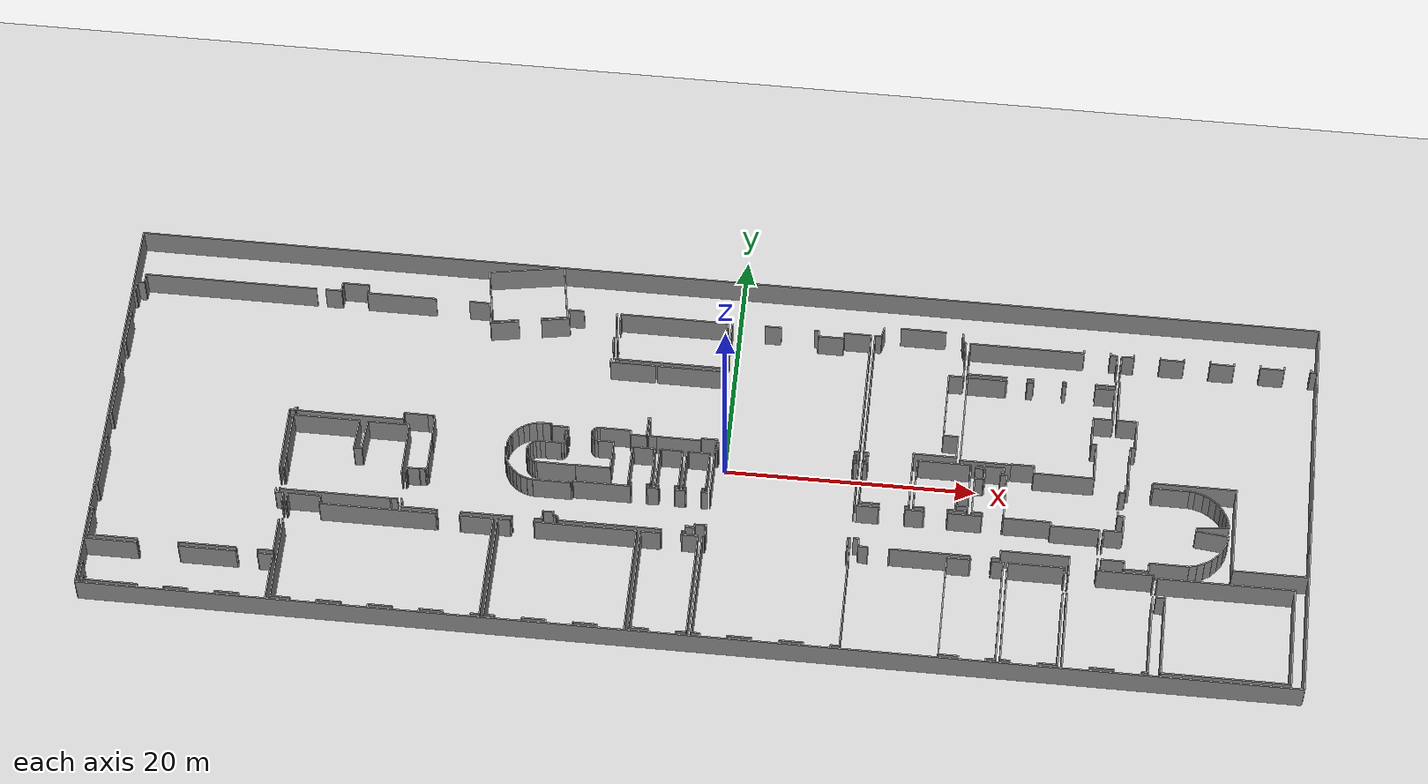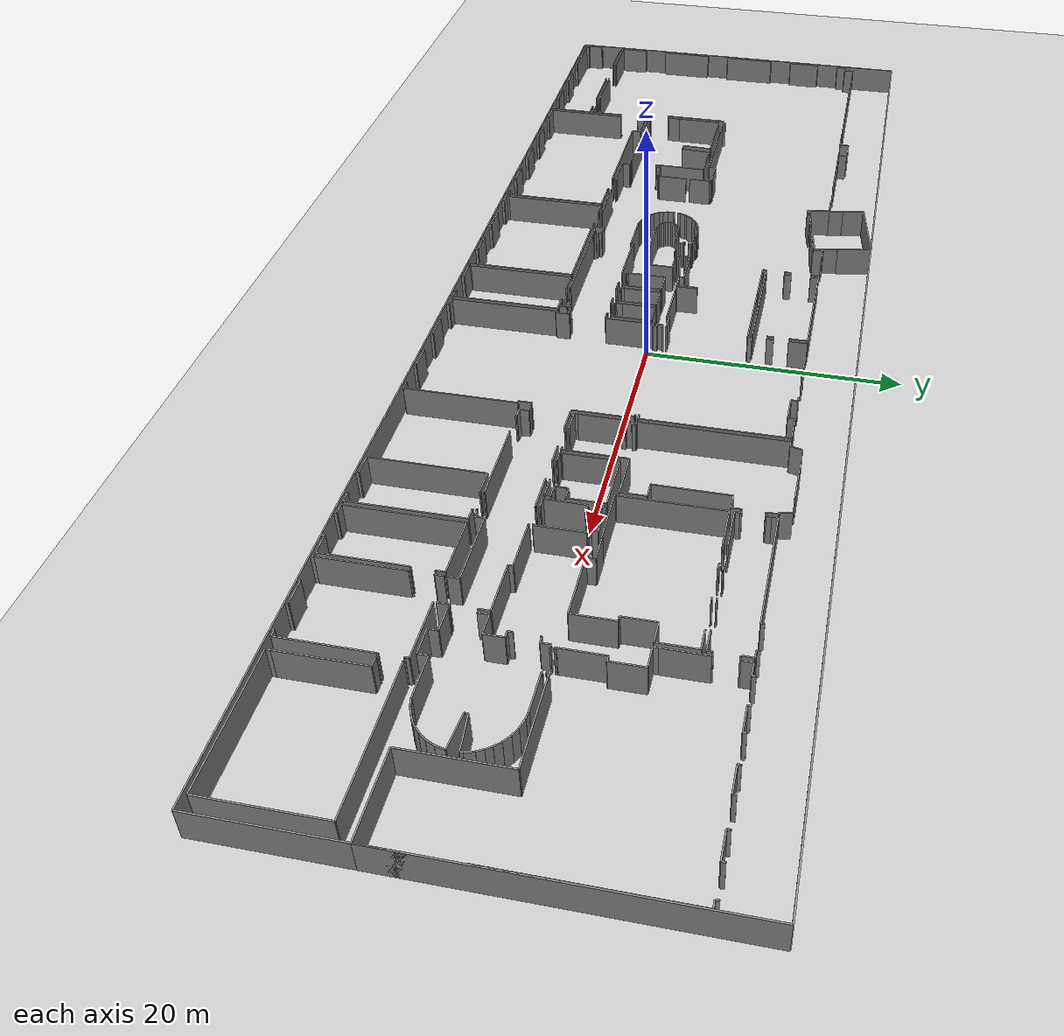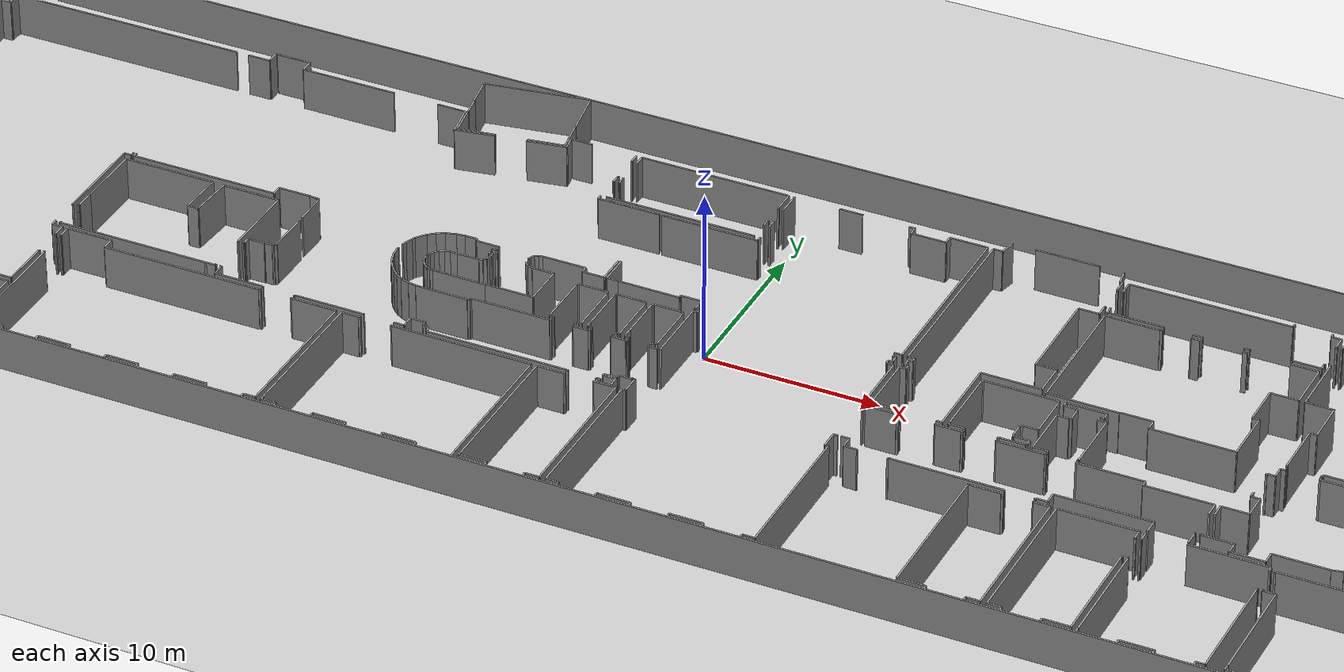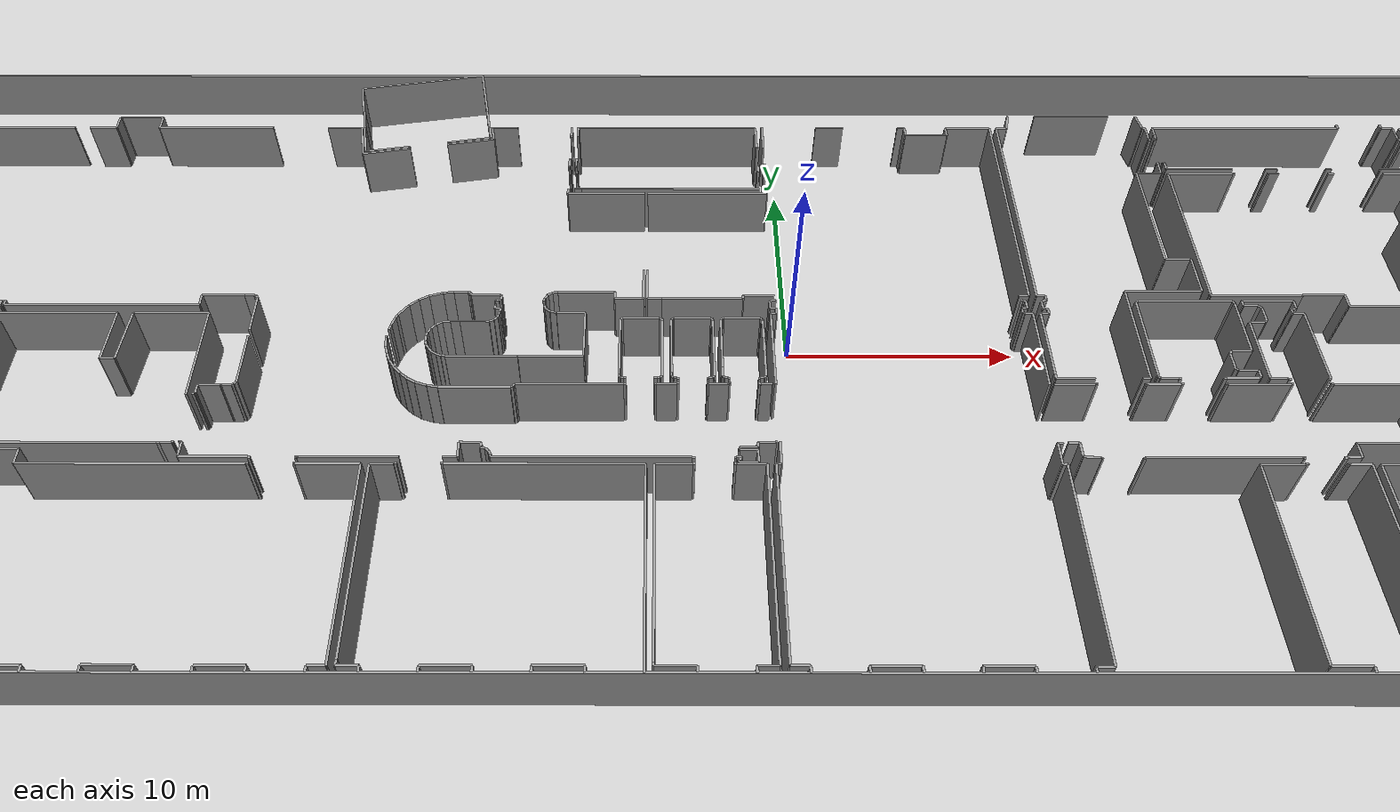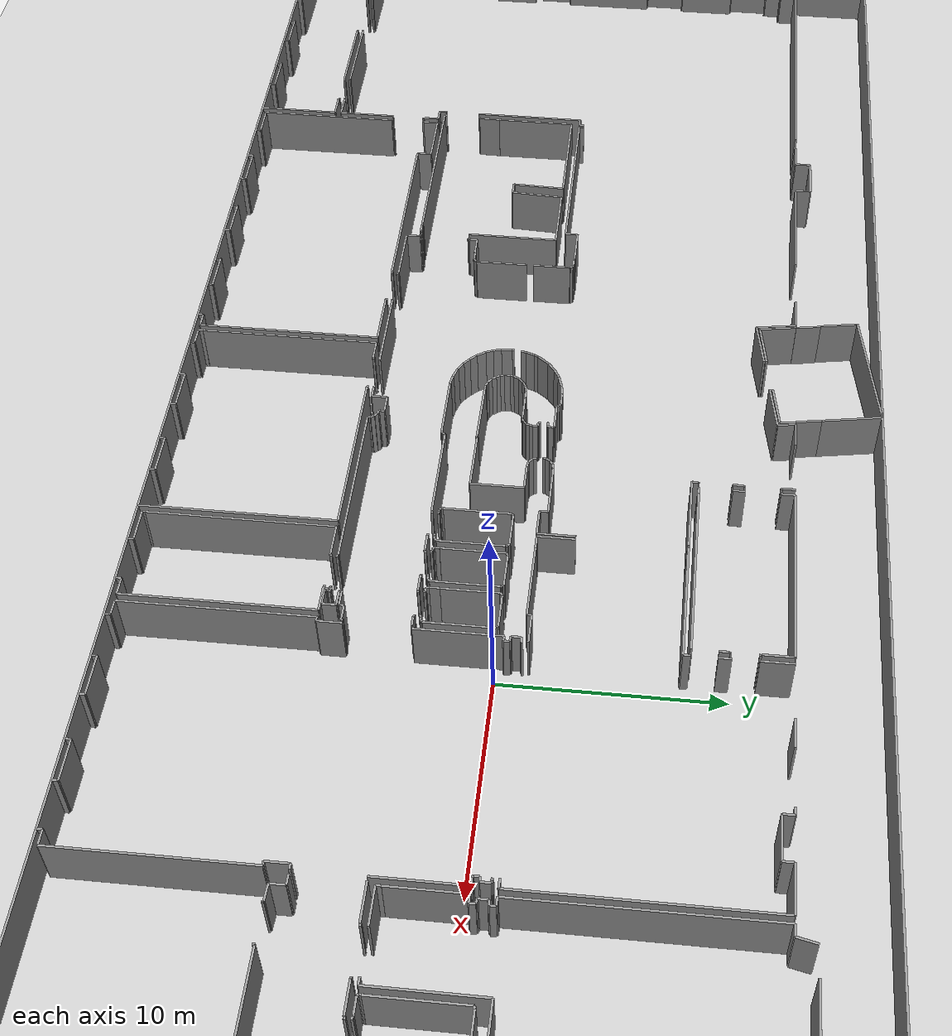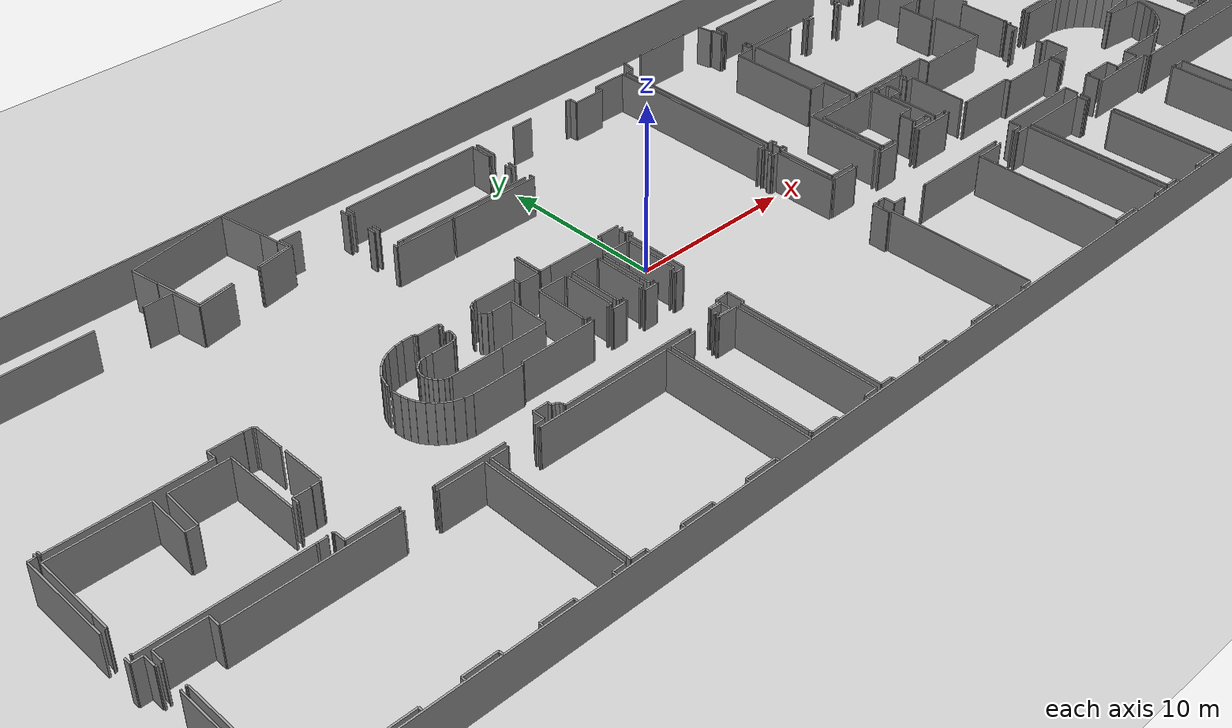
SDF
<sdf version="1.6">
  <world name="default">
    <light name="sun" type="directional">
      <cast_shadows>1</cast_shadows>
      <pose frame="">0 0 10 0 -0 0</pose>
      <diffuse>0.8 0.8 0.8 1</diffuse>
      <specular>0.1 0.1 0.1 1</specular>
      <attenuation>
        <range>1000</range>
        <constant>0.9</constant>
        <linear>0.01</linear>
        <quadratic>0.001</quadratic>
      </attenuation>
      <direction>-0.5 0.5 -1</direction>
    </light>
    <model name="ground_plane">
      <static>1</static>
      <link name="link">
        <collision name="collision">
          <geometry>
            <plane>
              <normal>0 0 1</normal>
              <size>100 100</size>
            </plane>
          </geometry>
          <surface>
            <friction>
              <ode>
                <mu>100</mu>
                <mu2>50</mu2>
              </ode>
              <torsional>
                <ode />
              </torsional>
            </friction>
            <contact>
              <ode />
            </contact>
            <bounce />
          </surface>
          <max_contacts>10</max_contacts>
        </collision>
        <visual name="visual">
          <cast_shadows>0</cast_shadows>
          <geometry>
            <plane>
              <normal>0 0 1</normal>
              <size>100 100</size>
            </plane>
          </geometry>
          <material>
            <script>
              <uri>file://media/materials/scripts/gazebo.material</uri>
              <name>Gazebo/Grey</name>
            </script>
          </material>
        </visual>
        <self_collide>0</self_collide>
        <kinematic>0</kinematic>
        <gravity>1</gravity>
      </link>
    </model>
    <gravity>0 0 -9.8</gravity>
    <magnetic_field>6e-06 2.3e-05 -4.2e-05</magnetic_field>
    <atmosphere type="adiabatic" />
    <physics default="0" name="default_physics" type="ode">
      <max_step_size>0.001</max_step_size>
      <real_time_factor>1</real_time_factor>
      <real_time_update_rate>1000</real_time_update_rate>
    </physics>
    <scene>
      <ambient>0.4 0.4 0.4 1</ambient>
      <background>0.7 0.7 0.7 1</background>
      <shadows>1</shadows>
    </scene>
    <spherical_coordinates>
      <surface_model>EARTH_WGS84</surface_model>
      <latitude_deg>0</latitude_deg>
      <longitude_deg>0</longitude_deg>
      <elevation>0</elevation>
      <heading_deg>0</heading_deg>
    </spherical_coordinates>
  <model name="0510032261_A_40_1_103">
		<static>1</static>
		<link name="Wall_0">
			<collision name="Wall_0_Collision">
				<geometry>
					<box>
						<size>2.5165184244 0.1 2.5</size>
					</box>
				</geometry>
				<pose frame="">1.2582592122 0 1.25 0 0 0</pose>
			</collision>
			<visual name="Wall_0_Visual">
				<pose frame="">1.2582592122 0 1.25 0 0 0</pose>
				<geometry>
					<box>
						<size>2.5165184244 0.1 2.5</size>
					</box>
				</geometry>
				<material>
					<script>
						<uri>file://media/materials/scripts/gazebo.material</uri>
						<name>Gazebo/Grey</name>
					</script>
					<ambient>1 1 1 1</ambient>
				</material>
			</visual>
			<pose frame="">0.275984752224 -28.7393900889 0 0 0 1.57079632679</pose>
		</link>
		<link name="Wall_1">
			<collision name="Wall_1_Collision">
				<geometry>
					<box>
						<size>0.257560355781 0.1 2.5</size>
					</box>
				</geometry>
				<pose frame="">0.128780177891 0 1.25 0 0 0</pose>
			</collision>
			<visual name="Wall_1_Visual">
				<pose frame="">0.128780177891 0 1.25 0 0 0</pose>
				<geometry>
					<box>
						<size>0.257560355781 0.1 2.5</size>
					</box>
				</geometry>
				<material>
					<script>
						<uri>file://media/materials/scripts/gazebo.material</uri>
						<name>Gazebo/Grey</name>
					</script>
					<ambient>1 1 1 1</ambient>
				</material>
			</visual>
			<pose frame="">0.275984752224 -26.2228716645 0 0 0 3.14159265359</pose>
		</link>
		<link name="Wall_2">
			<collision name="Wall_2_Collision">
				<geometry>
					<box>
						<size>0.247268106734 0.1 2.5</size>
					</box>
				</geometry>
				<pose frame="">0.123634053367 0 1.25 0 0 0</pose>
			</collision>
			<visual name="Wall_2_Visual">
				<pose frame="">0.123634053367 0 1.25 0 0 0</pose>
				<geometry>
					<box>
						<size>0.247268106734 0.1 2.5</size>
					</box>
				</geometry>
				<material>
					<script>
						<uri>file://media/materials/scripts/gazebo.material</uri>
						<name>Gazebo/Grey</name>
					</script>
					<ambient>1 1 1 1</ambient>
				</material>
			</visual>
			<pose frame="">0.0184243964422 -24.1005082592 0 0 0 0.0</pose>
		</link>
		<link name="Wall_3">
			<collision name="Wall_3_Collision">
				<geometry>
					<box>
						<size>4.61766200762 0.1 2.5</size>
					</box>
				</geometry>
				<pose frame="">2.30883100381 0 1.25 0 0 0</pose>
			</collision>
			<visual name="Wall_3_Visual">
				<pose frame="">2.30883100381 0 1.25 0 0 0</pose>
				<geometry>
					<box>
						<size>4.61766200762 0.1 2.5</size>
					</box>
				</geometry>
				<material>
					<script>
						<uri>file://media/materials/scripts/gazebo.material</uri>
						<name>Gazebo/Grey</name>
					</script>
					<ambient>1 1 1 1</ambient>
				</material>
			</visual>
			<pose frame="">0.265692503177 -24.1005082592 0 0 0 1.57079632679</pose>
		</link>
		<link name="Wall_4">
			<collision name="Wall_4_Collision">
				<geometry>
					<box>
						<size>0.253494282084 0.1 2.5</size>
					</box>
				</geometry>
				<pose frame="">0.126747141042 0 1.25 0 0 0</pose>
			</collision>
			<visual name="Wall_4_Visual">
				<pose frame="">0.126747141042 0 1.25 0 0 0</pose>
				<geometry>
					<box>
						<size>0.253494282084 0.1 2.5</size>
					</box>
				</geometry>
				<material>
					<script>
						<uri>file://media/materials/scripts/gazebo.material</uri>
						<name>Gazebo/Grey</name>
					</script>
					<ambient>1 1 1 1</ambient>
				</material>
			</visual>
			<pose frame="">0.265692503177 -19.4828462516 0 0 0 3.14159265359</pose>
		</link>
		<link name="Wall_5">
			<collision name="Wall_5_Collision">
				<geometry>
					<box>
						<size>0.249301143583 0.1 2.5</size>
					</box>
				</geometry>
				<pose frame="">0.124650571792 0 1.25 0 0 0</pose>
			</collision>
			<visual name="Wall_5_Visual">
				<pose frame="">0.124650571792 0 1.25 0 0 0</pose>
				<geometry>
					<box>
						<size>0.249301143583 0.1 2.5</size>
					</box>
				</geometry>
				<material>
					<script>
						<uri>file://media/materials/scripts/gazebo.material</uri>
						<name>Gazebo/Grey</name>
					</script>
					<ambient>1 1 1 1</ambient>
				</material>
			</visual>
			<pose frame="">0.0121982210928 -17.3575603558 0 0 0 0.0</pose>
		</link>
		<link name="Wall_6">
			<collision name="Wall_6_Collision">
				<geometry>
					<box>
						<size>4.6331639136 0.1 2.5</size>
					</box>
				</geometry>
				<pose frame="">2.3165819568 0 1.25 0 0 0</pose>
			</collision>
			<visual name="Wall_6_Visual">
				<pose frame="">2.3165819568 0 1.25 0 0 0</pose>
				<geometry>
					<box>
						<size>4.6331639136 0.1 2.5</size>
					</box>
				</geometry>
				<material>
					<script>
						<uri>file://media/materials/scripts/gazebo.material</uri>
						<name>Gazebo/Grey</name>
					</script>
					<ambient>1 1 1 1</ambient>
				</material>
			</visual>
			<pose frame="">0.261499364676 -17.3575603558 0 0 0 1.57079632679</pose>
		</link>
		<link name="Wall_7">
			<collision name="Wall_7_Collision">
				<geometry>
					<box>
						<size>0.250190597205 0.1 2.5</size>
					</box>
				</geometry>
				<pose frame="">0.125095298602 0 1.25 0 0 0</pose>
			</collision>
			<visual name="Wall_7_Visual">
				<pose frame="">0.125095298602 0 1.25 0 0 0</pose>
				<geometry>
					<box>
						<size>0.250190597205 0.1 2.5</size>
					</box>
				</geometry>
				<material>
					<script>
						<uri>file://media/materials/scripts/gazebo.material</uri>
						<name>Gazebo/Grey</name>
					</script>
					<ambient>1 1 1 1</ambient>
				</material>
			</visual>
			<pose frame="">0.261499364676 -12.7243964422 0 0 0 3.14159265359</pose>
		</link>
		<link name="Wall_8">
			<collision name="Wall_8_Collision">
				<geometry>
					<box>
						<size>0.252858958069 0.1 2.5</size>
					</box>
				</geometry>
				<pose frame="">0.126429479034 0 1.25 0 0 0</pose>
			</collision>
			<visual name="Wall_8_Visual">
				<pose frame="">0.126429479034 0 1.25 0 0 0</pose>
				<geometry>
					<box>
						<size>0.252858958069 0.1 2.5</size>
					</box>
				</geometry>
				<material>
					<script>
						<uri>file://media/materials/scripts/gazebo.material</uri>
						<name>Gazebo/Grey</name>
					</script>
					<ambient>1 1 1 1</ambient>
				</material>
			</visual>
			<pose frame="">0.0113087674714 -10.6087674714 0 0 0 0.0</pose>
		</link>
		<link name="Wall_9">
			<collision name="Wall_9_Collision">
				<geometry>
					<box>
						<size>2.86200762389 0.1 2.5</size>
					</box>
				</geometry>
				<pose frame="">1.43100381194 0 1.25 0 0 0</pose>
			</collision>
			<visual name="Wall_9_Visual">
				<pose frame="">1.43100381194 0 1.25 0 0 0</pose>
				<geometry>
					<box>
						<size>2.86200762389 0.1 2.5</size>
					</box>
				</geometry>
				<material>
					<script>
						<uri>file://media/materials/scripts/gazebo.material</uri>
						<name>Gazebo/Grey</name>
					</script>
					<ambient>1 1 1 1</ambient>
				</material>
			</visual>
			<pose frame="">0.26416772554 -10.6087674714 0 0 0 1.57079632679</pose>
		</link>
		<link name="Wall_10">
			<collision name="Wall_10_Collision">
				<geometry>
					<box>
						<size>0.251715374841 0.1 2.5</size>
					</box>
				</geometry>
				<pose frame="">0.125857687421 0 1.25 0 0 0</pose>
			</collision>
			<visual name="Wall_10_Visual">
				<pose frame="">0.125857687421 0 1.25 0 0 0</pose>
				<geometry>
					<box>
						<size>0.251715374841 0.1 2.5</size>
					</box>
				</geometry>
				<material>
					<script>
						<uri>file://media/materials/scripts/gazebo.material</uri>
						<name>Gazebo/Grey</name>
					</script>
					<ambient>1 1 1 1</ambient>
				</material>
			</visual>
			<pose frame="">0.26416772554 -7.74675984752 0 0 0 3.14159265359</pose>
		</link>
		<link name="Wall_11">
			<collision name="Wall_11_Collision">
				<geometry>
					<box>
						<size>0.257179161372 0.1 2.5</size>
					</box>
				</geometry>
				<pose frame="">0.128589580686 0 1.25 0 0 0</pose>
			</collision>
			<visual name="Wall_11_Visual">
				<pose frame="">0.128589580686 0 1.25 0 0 0</pose>
				<geometry>
					<box>
						<size>0.257179161372 0.1 2.5</size>
					</box>
				</geometry>
				<material>
					<script>
						<uri>file://media/materials/scripts/gazebo.material</uri>
						<name>Gazebo/Grey</name>
					</script>
					<ambient>1 1 1 1</ambient>
				</material>
			</visual>
			<pose frame="">0.0124523506989 -5.65171537484 0 0 0 0.0</pose>
		</link>
		<link name="Wall_12">
			<collision name="Wall_12_Collision">
				<geometry>
					<box>
						<size>0.840787801779 0.1 2.5</size>
					</box>
				</geometry>
				<pose frame="">0.420393900889 0 1.25 0 0 0</pose>
			</collision>
			<visual name="Wall_12_Visual">
				<pose frame="">0.420393900889 0 1.25 0 0 0</pose>
				<geometry>
					<box>
						<size>0.840787801779 0.1 2.5</size>
					</box>
				</geometry>
				<material>
					<script>
						<uri>file://media/materials/scripts/gazebo.material</uri>
						<name>Gazebo/Grey</name>
					</script>
					<ambient>1 1 1 1</ambient>
				</material>
			</visual>
			<pose frame="">0.269631512071 -5.65171537484 0 0 0 1.57079632679</pose>
		</link>
		<link name="Wall_13">
			<collision name="Wall_13_Collision">
				<geometry>
					<box>
						<size>0.595044472681 0.1 2.5</size>
					</box>
				</geometry>
				<pose frame="">0.297522236341 0 1.25 0 0 0</pose>
			</collision>
			<visual name="Wall_13_Visual">
				<pose frame="">0.297522236341 0 1.25 0 0 0</pose>
				<geometry>
					<box>
						<size>0.595044472681 0.1 2.5</size>
					</box>
				</geometry>
				<material>
					<script>
						<uri>file://media/materials/scripts/gazebo.material</uri>
						<name>Gazebo/Grey</name>
					</script>
					<ambient>1 1 1 1</ambient>
				</material>
			</visual>
			<pose frame="">0.269631512071 -4.81092757306 0 0 0 0.0</pose>
		</link>
		<link name="Wall_14">
			<collision name="Wall_14_Collision">
				<geometry>
					<box>
						<size>0.805463786531 0.1 2.5</size>
					</box>
				</geometry>
				<pose frame="">0.402731893266 0 1.25 0 0 0</pose>
			</collision>
			<visual name="Wall_14_Visual">
				<pose frame="">0.402731893266 0 1.25 0 0 0</pose>
				<geometry>
					<box>
						<size>0.805463786531 0.1 2.5</size>
					</box>
				</geometry>
				<material>
					<script>
						<uri>file://media/materials/scripts/gazebo.material</uri>
						<name>Gazebo/Grey</name>
					</script>
					<ambient>1 1 1 1</ambient>
				</material>
			</visual>
			<pose frame="">0.864675984752 -4.81092757306 0 0 0 1.57079632679</pose>
		</link>
		<link name="Wall_15">
			<collision name="Wall_15_Collision">
				<geometry>
					<box>
						<size>13.9137229987 0.1 2.5</size>
					</box>
				</geometry>
				<pose frame="">6.95686149936 0 1.25 0 0 0</pose>
			</collision>
			<visual name="Wall_15_Visual">
				<pose frame="">6.95686149936 0 1.25 0 0 0</pose>
				<geometry>
					<box>
						<size>13.9137229987 0.1 2.5</size>
					</box>
				</geometry>
				<material>
					<script>
						<uri>file://media/materials/scripts/gazebo.material</uri>
						<name>Gazebo/Grey</name>
					</script>
					<ambient>1 1 1 1</ambient>
				</material>
			</visual>
			<pose frame="">0.864675984752 -4.00546378653 0 0 0 0.0</pose>
		</link>
		<link name="Wall_16">
			<collision name="Wall_16_Collision">
				<geometry>
					<box>
						<size>0.24917407878 0.1 2.5</size>
					</box>
				</geometry>
				<pose frame="">0.12458703939 0 1.25 0 0 0</pose>
			</collision>
			<visual name="Wall_16_Visual">
				<pose frame="">0.12458703939 0 1.25 0 0 0</pose>
				<geometry>
					<box>
						<size>0.24917407878 0.1 2.5</size>
					</box>
				</geometry>
				<material>
					<script>
						<uri>file://media/materials/scripts/gazebo.material</uri>
						<name>Gazebo/Grey</name>
					</script>
					<ambient>1 1 1 1</ambient>
				</material>
			</visual>
			<pose frame="">14.7219822109 -15.4337992376 0 0 0 -1.57079632679</pose>
		</link>
		<link name="Wall_17">
			<collision name="Wall_17_Collision">
				<geometry>
					<box>
						<size>0.419822109276 0.1 2.5</size>
					</box>
				</geometry>
				<pose frame="">0.209911054638 0 1.25 0 0 0</pose>
			</collision>
			<visual name="Wall_17_Visual">
				<pose frame="">0.209911054638 0 1.25 0 0 0</pose>
				<geometry>
					<box>
						<size>0.419822109276 0.1 2.5</size>
					</box>
				</geometry>
				<material>
					<script>
						<uri>file://media/materials/scripts/gazebo.material</uri>
						<name>Gazebo/Grey</name>
					</script>
					<ambient>1 1 1 1</ambient>
				</material>
			</visual>
			<pose frame="">14.7219822109 -15.6829733164 0 0 0 3.14159265359</pose>
		</link>
		<link name="Wall_18">
			<collision name="Wall_18_Collision">
				<geometry>
					<box>
						<size>5.55311308767 0.1 2.5</size>
					</box>
				</geometry>
				<pose frame="">2.77655654384 0 1.25 0 0 0</pose>
			</collision>
			<visual name="Wall_18_Visual">
				<pose frame="">2.77655654384 0 1.25 0 0 0</pose>
				<geometry>
					<box>
						<size>5.55311308767 0.1 2.5</size>
					</box>
				</geometry>
				<material>
					<script>
						<uri>file://media/materials/scripts/gazebo.material</uri>
						<name>Gazebo/Grey</name>
					</script>
					<ambient>1 1 1 1</ambient>
				</material>
			</visual>
			<pose frame="">14.3021601017 -15.6829733164 0 0 0 -1.57079632679</pose>
		</link>
		<link name="Wall_19">
			<collision name="Wall_19_Collision">
				<geometry>
					<box>
						<size>0.390470139771 0.1 2.5</size>
					</box>
				</geometry>
				<pose frame="">0.195235069886 0 1.25 0 0 0</pose>
			</collision>
			<visual name="Wall_19_Visual">
				<pose frame="">0.195235069886 0 1.25 0 0 0</pose>
				<geometry>
					<box>
						<size>0.390470139771 0.1 2.5</size>
					</box>
				</geometry>
				<material>
					<script>
						<uri>file://media/materials/scripts/gazebo.material</uri>
						<name>Gazebo/Grey</name>
					</script>
					<ambient>1 1 1 1</ambient>
				</material>
			</visual>
			<pose frame="">14.3021601017 -22.9911054638 0 0 0 -1.57079632679</pose>
		</link>
		<link name="Wall_20">
			<collision name="Wall_20_Collision">
				<geometry>
					<box>
						<size>0.613977128335 0.1 2.5</size>
					</box>
				</geometry>
				<pose frame="">0.306988564168 0 1.25 0 0 0</pose>
			</collision>
			<visual name="Wall_20_Visual">
				<pose frame="">0.306988564168 0 1.25 0 0 0</pose>
				<geometry>
					<box>
						<size>0.613977128335 0.1 2.5</size>
					</box>
				</geometry>
				<material>
					<script>
						<uri>file://media/materials/scripts/gazebo.material</uri>
						<name>Gazebo/Grey</name>
					</script>
					<ambient>1 1 1 1</ambient>
				</material>
			</visual>
			<pose frame="">14.3021601017 -23.3815756036 0 0 0 0.0</pose>
		</link>
		<link name="Wall_21">
			<collision name="Wall_21_Collision">
				<geometry>
					<box>
						<size>0.757052096569 0.1 2.5</size>
					</box>
				</geometry>
				<pose frame="">0.378526048285 0 1.25 0 0 0</pose>
			</collision>
			<visual name="Wall_21_Visual">
				<pose frame="">0.378526048285 0 1.25 0 0 0</pose>
				<geometry>
					<box>
						<size>0.757052096569 0.1 2.5</size>
					</box>
				</geometry>
				<material>
					<script>
						<uri>file://media/materials/scripts/gazebo.material</uri>
						<name>Gazebo/Grey</name>
					</script>
					<ambient>1 1 1 1</ambient>
				</material>
			</visual>
			<pose frame="">14.91613723 -23.3815756036 0 0 0 -1.57079632679</pose>
		</link>
		<link name="Wall_22">
			<collision name="Wall_22_Collision">
				<geometry>
					<box>
						<size>0.0388818297332 0.1 2.5</size>
					</box>
				</geometry>
				<pose frame="">0.0194409148666 0 1.25 0 0 0</pose>
			</collision>
			<visual name="Wall_22_Visual">
				<pose frame="">0.0194409148666 0 1.25 0 0 0</pose>
				<geometry>
					<box>
						<size>0.0388818297332 0.1 2.5</size>
					</box>
				</geometry>
				<material>
					<script>
						<uri>file://media/materials/scripts/gazebo.material</uri>
						<name>Gazebo/Grey</name>
					</script>
					<ambient>1 1 1 1</ambient>
				</material>
			</visual>
			<pose frame="">14.91613723 -24.1386277001 0 0 0 0.0</pose>
		</link>
		<link name="Wall_23">
			<collision name="Wall_23_Collision">
				<geometry>
					<box>
						<size>0.111944091487 0.1 2.5</size>
					</box>
				</geometry>
				<pose frame="">0.0559720457433 0 1.25 0 0 0</pose>
			</collision>
			<visual name="Wall_23_Visual">
				<pose frame="">0.0559720457433 0 1.25 0 0 0</pose>
				<geometry>
					<box>
						<size>0.111944091487 0.1 2.5</size>
					</box>
				</geometry>
				<material>
					<script>
						<uri>file://media/materials/scripts/gazebo.material</uri>
						<name>Gazebo/Grey</name>
					</script>
					<ambient>1 1 1 1</ambient>
				</material>
			</visual>
			<pose frame="">14.9550190597 -24.1386277001 0 0 0 -1.57079632679</pose>
		</link>
		<link name="Wall_24">
			<collision name="Wall_24_Collision">
				<geometry>
					<box>
						<size>0.0569250317662 0.1 2.5</size>
					</box>
				</geometry>
				<pose frame="">0.0284625158831 0 1.25 0 0 0</pose>
			</collision>
			<visual name="Wall_24_Visual">
				<pose frame="">0.0284625158831 0 1.25 0 0 0</pose>
				<geometry>
					<box>
						<size>0.0569250317662 0.1 2.5</size>
					</box>
				</geometry>
				<material>
					<script>
						<uri>file://media/materials/scripts/gazebo.material</uri>
						<name>Gazebo/Grey</name>
					</script>
					<ambient>1 1 1 1</ambient>
				</material>
			</visual>
			<pose frame="">14.9550190597 -25.8360864041 0 0 0 -1.57079632679</pose>
		</link>
		<link name="Wall_25">
			<collision name="Wall_25_Collision">
				<geometry>
					<box>
						<size>0.0237611181703 0.1 2.5</size>
					</box>
				</geometry>
				<pose frame="">0.0118805590851 0 1.25 0 0 0</pose>
			</collision>
			<visual name="Wall_25_Visual">
				<pose frame="">0.0118805590851 0 1.25 0 0 0</pose>
				<geometry>
					<box>
						<size>0.0237611181703 0.1 2.5</size>
					</box>
				</geometry>
				<material>
					<script>
						<uri>file://media/materials/scripts/gazebo.material</uri>
						<name>Gazebo/Grey</name>
					</script>
					<ambient>1 1 1 1</ambient>
				</material>
			</visual>
			<pose frame="">14.9550190597 -25.8930114358 0 0 0 3.14159265359</pose>
		</link>
		<link name="Wall_26">
			<collision name="Wall_26_Collision">
				<geometry>
					<box>
						<size>2.84904701398 0.1 2.5</size>
					</box>
				</geometry>
				<pose frame="">1.42452350699 0 1.25 0 0 0</pose>
			</collision>
			<visual name="Wall_26_Visual">
				<pose frame="">1.42452350699 0 1.25 0 0 0</pose>
				<geometry>
					<box>
						<size>2.84904701398 0.1 2.5</size>
					</box>
				</geometry>
				<material>
					<script>
						<uri>file://media/materials/scripts/gazebo.material</uri>
						<name>Gazebo/Grey</name>
					</script>
					<ambient>1 1 1 1</ambient>
				</material>
			</visual>
			<pose frame="">14.9312579416 -25.8930114358 0 0 0 -1.57079632679</pose>
		</link>
		<link name="Wall_27">
			<collision name="Wall_27_Collision">
				<geometry>
					<box>
						<size>1.18996188056 0.1 2.5</size>
					</box>
				</geometry>
				<pose frame="">0.59498094028 0 1.25 0 0 0</pose>
			</collision>
			<visual name="Wall_27_Visual">
				<pose frame="">0.59498094028 0 1.25 0 0 0</pose>
				<geometry>
					<box>
						<size>1.18996188056 0.1 2.5</size>
					</box>
				</geometry>
				<material>
					<script>
						<uri>file://media/materials/scripts/gazebo.material</uri>
						<name>Gazebo/Grey</name>
					</script>
					<ambient>1 1 1 1</ambient>
				</material>
			</visual>
			<pose frame="">14.9312579416 -28.7420584498 0 0 0 3.14159265359</pose>
		</link>
		<link name="Wall_28">
			<collision name="Wall_28_Collision">
				<geometry>
					<box>
						<size>0.0199491740788 0.1 2.5</size>
					</box>
				</geometry>
				<pose frame="">0.00997458703939 0 1.25 0 0 0</pose>
			</collision>
			<visual name="Wall_28_Visual">
				<pose frame="">0.00997458703939 0 1.25 0 0 0</pose>
				<geometry>
					<box>
						<size>0.0199491740788 0.1 2.5</size>
					</box>
				</geometry>
				<material>
					<script>
						<uri>file://media/materials/scripts/gazebo.material</uri>
						<name>Gazebo/Grey</name>
					</script>
					<ambient>1 1 1 1</ambient>
				</material>
			</visual>
			<pose frame="">13.741296061 -28.7420584498 0 0 0 -1.57079632679</pose>
		</link>
		<link name="Wall_29">
			<collision name="Wall_29_Collision">
				<geometry>
					<box>
						<size>0.0866581956798 0.1 2.5</size>
					</box>
				</geometry>
				<pose frame="">0.0433290978399 0 1.25 0 0 0</pose>
			</collision>
			<visual name="Wall_29_Visual">
				<pose frame="">0.0433290978399 0 1.25 0 0 0</pose>
				<geometry>
					<box>
						<size>0.0866581956798 0.1 2.5</size>
					</box>
				</geometry>
				<material>
					<script>
						<uri>file://media/materials/scripts/gazebo.material</uri>
						<name>Gazebo/Grey</name>
					</script>
					<ambient>1 1 1 1</ambient>
				</material>
			</visual>
			<pose frame="">13.741296061 -28.7620076239 0 0 0 3.14159265359</pose>
		</link>
		<link name="Wall_30">
			<collision name="Wall_30_Collision">
				<geometry>
					<box>
						<size>0.0725540025413 0.1 2.5</size>
					</box>
				</geometry>
				<pose frame="">0.0362770012706 0 1.25 0 0 0</pose>
			</collision>
			<visual name="Wall_30_Visual">
				<pose frame="">0.0362770012706 0 1.25 0 0 0</pose>
				<geometry>
					<box>
						<size>0.0725540025413 0.1 2.5</size>
					</box>
				</geometry>
				<material>
					<script>
						<uri>file://media/materials/scripts/gazebo.material</uri>
						<name>Gazebo/Grey</name>
					</script>
					<ambient>1 1 1 1</ambient>
				</material>
			</visual>
			<pose frame="">12.0565438374 -28.7620076239 0 0 0 3.14159265359</pose>
		</link>
		<link name="Wall_31">
			<collision name="Wall_31_Collision">
				<geometry>
					<box>
						<size>0.025667090216 0.1 2.5</size>
					</box>
				</geometry>
				<pose frame="">0.012833545108 0 1.25 0 0 0</pose>
			</collision>
			<visual name="Wall_31_Visual">
				<pose frame="">0.012833545108 0 1.25 0 0 0</pose>
				<geometry>
					<box>
						<size>0.025667090216 0.1 2.5</size>
					</box>
				</geometry>
				<material>
					<script>
						<uri>file://media/materials/scripts/gazebo.material</uri>
						<name>Gazebo/Grey</name>
					</script>
					<ambient>1 1 1 1</ambient>
				</material>
			</visual>
			<pose frame="">11.9839898348 -28.7620076239 0 0 0 1.57079632679</pose>
		</link>
		<link name="Wall_32">
			<collision name="Wall_32_Collision">
				<geometry>
					<box>
						<size>4.47001270648 0.1 2.5</size>
					</box>
				</geometry>
				<pose frame="">2.23500635324 0 1.25 0 0 0</pose>
			</collision>
			<visual name="Wall_32_Visual">
				<pose frame="">2.23500635324 0 1.25 0 0 0</pose>
				<geometry>
					<box>
						<size>4.47001270648 0.1 2.5</size>
					</box>
				</geometry>
				<material>
					<script>
						<uri>file://media/materials/scripts/gazebo.material</uri>
						<name>Gazebo/Grey</name>
					</script>
					<ambient>1 1 1 1</ambient>
				</material>
			</visual>
			<pose frame="">11.9839898348 -28.7363405337 0 0 0 3.14159265359</pose>
		</link>
		<link name="Wall_33">
			<collision name="Wall_33_Collision">
				<geometry>
					<box>
						<size>0.0294790343075 0.1 2.5</size>
					</box>
				</geometry>
				<pose frame="">0.0147395171537 0 1.25 0 0 0</pose>
			</collision>
			<visual name="Wall_33_Visual">
				<pose frame="">0.0147395171537 0 1.25 0 0 0</pose>
				<geometry>
					<box>
						<size>0.0294790343075 0.1 2.5</size>
					</box>
				</geometry>
				<material>
					<script>
						<uri>file://media/materials/scripts/gazebo.material</uri>
						<name>Gazebo/Grey</name>
					</script>
					<ambient>1 1 1 1</ambient>
				</material>
			</visual>
			<pose frame="">7.51397712834 -28.7363405337 0 0 0 -1.57079632679</pose>
		</link>
		<link name="Wall_34">
			<collision name="Wall_34_Collision">
				<geometry>
					<box>
						<size>0.0997458703939 0.1 2.5</size>
					</box>
				</geometry>
				<pose frame="">0.049872935197 0 1.25 0 0 0</pose>
			</collision>
			<visual name="Wall_34_Visual">
				<pose frame="">0.049872935197 0 1.25 0 0 0</pose>
				<geometry>
					<box>
						<size>0.0997458703939 0.1 2.5</size>
					</box>
				</geometry>
				<material>
					<script>
						<uri>file://media/materials/scripts/gazebo.material</uri>
						<name>Gazebo/Grey</name>
					</script>
					<ambient>1 1 1 1</ambient>
				</material>
			</visual>
			<pose frame="">7.51397712834 -28.765819568 0 0 0 3.14159265359</pose>
		</link>
		<link name="Wall_35">
			<collision name="Wall_35_Collision">
				<geometry>
					<box>
						<size>0.0818297331639 0.1 2.5</size>
					</box>
				</geometry>
				<pose frame="">0.040914866582 0 1.25 0 0 0</pose>
			</collision>
			<visual name="Wall_35_Visual">
				<pose frame="">0.040914866582 0 1.25 0 0 0</pose>
				<geometry>
					<box>
						<size>0.0818297331639 0.1 2.5</size>
					</box>
				</geometry>
				<material>
					<script>
						<uri>file://media/materials/scripts/gazebo.material</uri>
						<name>Gazebo/Grey</name>
					</script>
					<ambient>1 1 1 1</ambient>
				</material>
			</visual>
			<pose frame="">4.23799237611 -28.765819568 0 0 0 3.14159265359</pose>
		</link>
		<link name="Wall_36">
			<collision name="Wall_36_Collision">
				<geometry>
					<box>
						<size>0.0247776365947 0.1 2.5</size>
					</box>
				</geometry>
				<pose frame="">0.0123888182973 0 1.25 0 0 0</pose>
			</collision>
			<visual name="Wall_36_Visual">
				<pose frame="">0.0123888182973 0 1.25 0 0 0</pose>
				<geometry>
					<box>
						<size>0.0247776365947 0.1 2.5</size>
					</box>
				</geometry>
				<material>
					<script>
						<uri>file://media/materials/scripts/gazebo.material</uri>
						<name>Gazebo/Grey</name>
					</script>
					<ambient>1 1 1 1</ambient>
				</material>
			</visual>
			<pose frame="">4.15616264295 -28.765819568 0 0 0 1.57079632679</pose>
		</link>
		<link name="Wall_37">
			<collision name="Wall_37_Collision">
				<geometry>
					<box>
						<size>3.88017824233 0.1 2.5</size>
					</box>
				</geometry>
				<pose frame="">1.94008912116 0 1.25 0 0 0</pose>
			</collision>
			<visual name="Wall_37_Visual">
				<pose frame="">1.94008912116 0 1.25 0 0 0</pose>
				<geometry>
					<box>
						<size>3.88017824233 0.1 2.5</size>
					</box>
				</geometry>
				<material>
					<script>
						<uri>file://media/materials/scripts/gazebo.material</uri>
						<name>Gazebo/Grey</name>
					</script>
					<ambient>1 1 1 1</ambient>
				</material>
			</visual>
			<pose frame="">4.15616264295 -28.7410419314 0 0 0 3.14116694055</pose>
		</link>
		<link name="Wall_38">
			<collision name="Wall_38_Collision">
				<geometry>
					<box>
						<size>1.35628970775 0.1 2.5</size>
					</box>
				</geometry>
				<pose frame="">0.678144853875 0 1.25 0 0 0</pose>
			</collision>
			<visual name="Wall_38_Visual">
				<pose frame="">0.678144853875 0 1.25 0 0 0</pose>
				<geometry>
					<box>
						<size>1.35628970775 0.1 2.5</size>
					</box>
				</geometry>
				<material>
					<script>
						<uri>file://media/materials/scripts/gazebo.material</uri>
						<name>Gazebo/Grey</name>
					</script>
					<ambient>1 1 1 1</ambient>
				</material>
			</visual>
			<pose frame="">0.274968233799 -32.5261753494 0 0 0 1.57079632679</pose>
		</link>
		<link name="Wall_39">
			<collision name="Wall_39_Collision">
				<geometry>
					<box>
						<size>0.274968233799 0.1 2.5</size>
					</box>
				</geometry>
				<pose frame="">0.1374841169 0 1.25 0 0 0</pose>
			</collision>
			<visual name="Wall_39_Visual">
				<pose frame="">0.1374841169 0 1.25 0 0 0</pose>
				<geometry>
					<box>
						<size>0.274968233799 0.1 2.5</size>
					</box>
				</geometry>
				<material>
					<script>
						<uri>file://media/materials/scripts/gazebo.material</uri>
						<name>Gazebo/Grey</name>
					</script>
					<ambient>1 1 1 1</ambient>
				</material>
			</visual>
			<pose frame="">0.274968233799 -31.1698856417 0 0 0 3.14159265359</pose>
		</link>
		<link name="Wall_40">
			<collision name="Wall_40_Collision">
				<geometry>
					<box>
						<size>4.17522236341 0.1 2.5</size>
					</box>
				</geometry>
				<pose frame="">2.0876111817 0 1.25 0 0 0</pose>
			</collision>
			<visual name="Wall_40_Visual">
				<pose frame="">2.0876111817 0 1.25 0 0 0</pose>
				<geometry>
					<box>
						<size>4.17522236341 0.1 2.5</size>
					</box>
				</geometry>
				<material>
					<script>
						<uri>file://media/materials/scripts/gazebo.material</uri>
						<name>Gazebo/Grey</name>
					</script>
					<ambient>1 1 1 1</ambient>
				</material>
			</visual>
			<pose frame="">0.0 -29.0681067344 0 0 0 0.0</pose>
		</link>
		<link name="Wall_41">
			<collision name="Wall_41_Collision">
				<geometry>
					<box>
						<size>0.0348157560356 0.1 2.5</size>
					</box>
				</geometry>
				<pose frame="">0.0174078780178 0 1.25 0 0 0</pose>
			</collision>
			<visual name="Wall_41_Visual">
				<pose frame="">0.0174078780178 0 1.25 0 0 0</pose>
				<geometry>
					<box>
						<size>0.0348157560356 0.1 2.5</size>
					</box>
				</geometry>
				<material>
					<script>
						<uri>file://media/materials/scripts/gazebo.material</uri>
						<name>Gazebo/Grey</name>
					</script>
					<ambient>1 1 1 1</ambient>
				</material>
			</visual>
			<pose frame="">4.17522236341 -29.0681067344 0 0 0 1.57079632679</pose>
		</link>
		<link name="Wall_42">
			<collision name="Wall_42_Collision">
				<geometry>
					<box>
						<size>0.0900889453621 0.1 2.5</size>
					</box>
				</geometry>
				<pose frame="">0.0450444726811 0 1.25 0 0 0</pose>
			</collision>
			<visual name="Wall_42_Visual">
				<pose frame="">0.0450444726811 0 1.25 0 0 0</pose>
				<geometry>
					<box>
						<size>0.0900889453621 0.1 2.5</size>
					</box>
				</geometry>
				<material>
					<script>
						<uri>file://media/materials/scripts/gazebo.material</uri>
						<name>Gazebo/Grey</name>
					</script>
					<ambient>1 1 1 1</ambient>
				</material>
			</visual>
			<pose frame="">4.17522236341 -29.0332909784 0 0 0 0.0</pose>
		</link>
		<link name="Wall_43">
			<collision name="Wall_43_Collision">
				<geometry>
					<box>
						<size>0.0623888182973 0.1 2.5</size>
					</box>
				</geometry>
				<pose frame="">0.0311944091487 0 1.25 0 0 0</pose>
			</collision>
			<visual name="Wall_43_Visual">
				<pose frame="">0.0311944091487 0 1.25 0 0 0</pose>
				<geometry>
					<box>
						<size>0.0623888182973 0.1 2.5</size>
					</box>
				</geometry>
				<material>
					<script>
						<uri>file://media/materials/scripts/gazebo.material</uri>
						<name>Gazebo/Grey</name>
					</script>
					<ambient>1 1 1 1</ambient>
				</material>
			</visual>
			<pose frame="">7.44345616264 -29.0332909784 0 0 0 0.0</pose>
		</link>
		<link name="Wall_44">
			<collision name="Wall_44_Collision">
				<geometry>
					<box>
						<size>0.0223634053367 0.1 2.5</size>
					</box>
				</geometry>
				<pose frame="">0.0111817026684 0 1.25 0 0 0</pose>
			</collision>
			<visual name="Wall_44_Visual">
				<pose frame="">0.0111817026684 0 1.25 0 0 0</pose>
				<geometry>
					<box>
						<size>0.0223634053367 0.1 2.5</size>
					</box>
				</geometry>
				<material>
					<script>
						<uri>file://media/materials/scripts/gazebo.material</uri>
						<name>Gazebo/Grey</name>
					</script>
					<ambient>1 1 1 1</ambient>
				</material>
			</visual>
			<pose frame="">7.50584498094 -29.0332909784 0 0 0 -1.57079632679</pose>
		</link>
		<link name="Wall_45">
			<collision name="Wall_45_Collision">
				<geometry>
					<box>
						<size>4.49695044473 0.1 2.5</size>
					</box>
				</geometry>
				<pose frame="">2.24847522236 0 1.25 0 0 0</pose>
			</collision>
			<visual name="Wall_45_Visual">
				<pose frame="">2.24847522236 0 1.25 0 0 0</pose>
				<geometry>
					<box>
						<size>4.49695044473 0.1 2.5</size>
					</box>
				</geometry>
				<material>
					<script>
						<uri>file://media/materials/scripts/gazebo.material</uri>
						<name>Gazebo/Grey</name>
					</script>
					<ambient>1 1 1 1</ambient>
				</material>
			</visual>
			<pose frame="">7.50584498094 -29.0556543837 0 0 0 0.0</pose>
		</link>
		<link name="Wall_46">
			<collision name="Wall_46_Collision">
				<geometry>
					<box>
						<size>0.0223634053367 0.1 2.5</size>
					</box>
				</geometry>
				<pose frame="">0.0111817026684 0 1.25 0 0 0</pose>
			</collision>
			<visual name="Wall_46_Visual">
				<pose frame="">0.0111817026684 0 1.25 0 0 0</pose>
				<geometry>
					<box>
						<size>0.0223634053367 0.1 2.5</size>
					</box>
				</geometry>
				<material>
					<script>
						<uri>file://media/materials/scripts/gazebo.material</uri>
						<name>Gazebo/Grey</name>
					</script>
					<ambient>1 1 1 1</ambient>
				</material>
			</visual>
			<pose frame="">12.0027954257 -29.0556543837 0 0 0 1.57079632679</pose>
		</link>
		<link name="Wall_47">
			<collision name="Wall_47_Collision">
				<geometry>
					<box>
						<size>0.125667090216 0.1 2.5</size>
					</box>
				</geometry>
				<pose frame="">0.062833545108 0 1.25 0 0 0</pose>
			</collision>
			<visual name="Wall_47_Visual">
				<pose frame="">0.062833545108 0 1.25 0 0 0</pose>
				<geometry>
					<box>
						<size>0.125667090216 0.1 2.5</size>
					</box>
				</geometry>
				<material>
					<script>
						<uri>file://media/materials/scripts/gazebo.material</uri>
						<name>Gazebo/Grey</name>
					</script>
					<ambient>1 1 1 1</ambient>
				</material>
			</visual>
			<pose frame="">12.0027954257 -29.0332909784 0 0 0 0.0</pose>
		</link>
		<link name="Wall_48">
			<collision name="Wall_48_Collision">
				<geometry>
					<box>
						<size>0.0631512071156 0.1 2.5</size>
					</box>
				</geometry>
				<pose frame="">0.0315756035578 0 1.25 0 0 0</pose>
			</collision>
			<visual name="Wall_48_Visual">
				<pose frame="">0.0315756035578 0 1.25 0 0 0</pose>
				<geometry>
					<box>
						<size>0.0631512071156 0.1 2.5</size>
					</box>
				</geometry>
				<material>
					<script>
						<uri>file://media/materials/scripts/gazebo.material</uri>
						<name>Gazebo/Grey</name>
					</script>
					<ambient>1 1 1 1</ambient>
				</material>
			</visual>
			<pose frame="">13.6867852605 -29.0332909784 0 0 0 0.0</pose>
		</link>
		<link name="Wall_49">
			<collision name="Wall_49_Collision">
				<geometry>
					<box>
						<size>0.043583227446 0.1 2.5</size>
					</box>
				</geometry>
				<pose frame="">0.021791613723 0 1.25 0 0 0</pose>
			</collision>
			<visual name="Wall_49_Visual">
				<pose frame="">0.021791613723 0 1.25 0 0 0</pose>
				<geometry>
					<box>
						<size>0.043583227446 0.1 2.5</size>
					</box>
				</geometry>
				<material>
					<script>
						<uri>file://media/materials/scripts/gazebo.material</uri>
						<name>Gazebo/Grey</name>
					</script>
					<ambient>1 1 1 1</ambient>
				</material>
			</visual>
			<pose frame="">13.7499364676 -29.0332909784 0 0 0 -1.57079632679</pose>
		</link>
		<link name="Wall_50">
			<collision name="Wall_50_Collision">
				<geometry>
					<box>
						<size>1.1750952986 0.1 2.5</size>
					</box>
				</geometry>
				<pose frame="">0.587547649301 0 1.25 0 0 0</pose>
			</collision>
			<visual name="Wall_50_Visual">
				<pose frame="">0.587547649301 0 1.25 0 0 0</pose>
				<geometry>
					<box>
						<size>1.1750952986 0.1 2.5</size>
					</box>
				</geometry>
				<material>
					<script>
						<uri>file://media/materials/scripts/gazebo.material</uri>
						<name>Gazebo/Grey</name>
					</script>
					<ambient>1 1 1 1</ambient>
				</material>
			</visual>
			<pose frame="">13.7499364676 -29.0768742058 0 0 0 0.0</pose>
		</link>
		<link name="Wall_51">
			<collision name="Wall_51_Collision">
				<geometry>
					<box>
						<size>3.9998729352 0.1 2.5</size>
					</box>
				</geometry>
				<pose frame="">1.9999364676 0 1.25 0 0 0</pose>
			</collision>
			<visual name="Wall_51_Visual">
				<pose frame="">1.9999364676 0 1.25 0 0 0</pose>
				<geometry>
					<box>
						<size>3.9998729352 0.1 2.5</size>
					</box>
				</geometry>
				<material>
					<script>
						<uri>file://media/materials/scripts/gazebo.material</uri>
						<name>Gazebo/Grey</name>
					</script>
					<ambient>1 1 1 1</ambient>
				</material>
			</visual>
			<pose frame="">14.9250317662 -29.0768742058 0 0 0 -1.57079632679</pose>
		</link>
		<link name="Wall_52">
			<collision name="Wall_52_Collision">
				<geometry>
					<box>
						<size>0.258068614994 0.1 2.5</size>
					</box>
				</geometry>
				<pose frame="">0.129034307497 0 1.25 0 0 0</pose>
			</collision>
			<visual name="Wall_52_Visual">
				<pose frame="">0.129034307497 0 1.25 0 0 0</pose>
				<geometry>
					<box>
						<size>0.258068614994 0.1 2.5</size>
					</box>
				</geometry>
				<material>
					<script>
						<uri>file://media/materials/scripts/gazebo.material</uri>
						<name>Gazebo/Grey</name>
					</script>
					<ambient>1 1 1 1</ambient>
				</material>
			</visual>
			<pose frame="">12.8343074968 -33.076747141 0 0 0 1.57079632679</pose>
		</link>
		<link name="Wall_53">
			<collision name="Wall_53_Collision">
				<geometry>
					<box>
						<size>1.90991105464 0.1 2.5</size>
					</box>
				</geometry>
				<pose frame="">0.954955527319 0 1.25 0 0 0</pose>
			</collision>
			<visual name="Wall_53_Visual">
				<pose frame="">0.954955527319 0 1.25 0 0 0</pose>
				<geometry>
					<box>
						<size>1.90991105464 0.1 2.5</size>
					</box>
				</geometry>
				<material>
					<script>
						<uri>file://media/materials/scripts/gazebo.material</uri>
						<name>Gazebo/Grey</name>
					</script>
					<ambient>1 1 1 1</ambient>
				</material>
			</visual>
			<pose frame="">12.8343074968 -32.818678526 0 0 0 3.14159265359</pose>
		</link>
		<link name="Wall_54">
			<collision name="Wall_54_Collision">
				<geometry>
					<box>
						<size>0.249555273189 0.1 2.5</size>
					</box>
				</geometry>
				<pose frame="">0.124777636595 0 1.25 0 0 0</pose>
			</collision>
			<visual name="Wall_54_Visual">
				<pose frame="">0.124777636595 0 1.25 0 0 0</pose>
				<geometry>
					<box>
						<size>0.249555273189 0.1 2.5</size>
					</box>
				</geometry>
				<material>
					<script>
						<uri>file://media/materials/scripts/gazebo.material</uri>
						<name>Gazebo/Grey</name>
					</script>
					<ambient>1 1 1 1</ambient>
				</material>
			</visual>
			<pose frame="">10.9243964422 -32.818678526 0 0 0 -1.57079632679</pose>
		</link>
		<link name="Wall_55">
			<collision name="Wall_55_Collision">
				<geometry>
					<box>
						<size>0.253621346887 0.1 2.5</size>
					</box>
				</geometry>
				<pose frame="">0.126810673443 0 1.25 0 0 0</pose>
			</collision>
			<visual name="Wall_55_Visual">
				<pose frame="">0.126810673443 0 1.25 0 0 0</pose>
				<geometry>
					<box>
						<size>0.253621346887 0.1 2.5</size>
					</box>
				</geometry>
				<material>
					<script>
						<uri>file://media/materials/scripts/gazebo.material</uri>
						<name>Gazebo/Grey</name>
					</script>
					<ambient>1 1 1 1</ambient>
				</material>
			</visual>
			<pose frame="">8.81817026684 -33.0682337992 0 0 0 1.57079632679</pose>
		</link>
		<link name="Wall_56">
			<collision name="Wall_56_Collision">
				<geometry>
					<box>
						<size>1.89072426938 0.1 2.5</size>
					</box>
				</geometry>
				<pose frame="">0.945362134689 0 1.25 0 0 0</pose>
			</collision>
			<visual name="Wall_56_Visual">
				<pose frame="">0.945362134689 0 1.25 0 0 0</pose>
				<geometry>
					<box>
						<size>1.89072426938 0.1 2.5</size>
					</box>
				</geometry>
				<material>
					<script>
						<uri>file://media/materials/scripts/gazebo.material</uri>
						<name>Gazebo/Grey</name>
					</script>
					<ambient>1 1 1 1</ambient>
				</material>
			</visual>
			<pose frame="">8.81817026684 -32.8146124524 0 0 0 3.14159265359</pose>
		</link>
		<link name="Wall_57">
			<collision name="Wall_57_Collision">
				<geometry>
					<box>
						<size>0.2625158831 0.1 2.5</size>
					</box>
				</geometry>
				<pose frame="">0.13125794155 0 1.25 0 0 0</pose>
			</collision>
			<visual name="Wall_57_Visual">
				<pose frame="">0.13125794155 0 1.25 0 0 0</pose>
				<geometry>
					<box>
						<size>0.2625158831 0.1 2.5</size>
					</box>
				</geometry>
				<material>
					<script>
						<uri>file://media/materials/scripts/gazebo.material</uri>
						<name>Gazebo/Grey</name>
					</script>
					<ambient>1 1 1 1</ambient>
				</material>
			</visual>
			<pose frame="">6.92744599746 -32.8146124524 0 0 0 -1.57079632679</pose>
		</link>
		<link name="Wall_58">
			<collision name="Wall_58_Collision">
				<geometry>
					<box>
						<size>0.269123252859 0.1 2.5</size>
					</box>
				</geometry>
				<pose frame="">0.134561626429 0 1.25 0 0 0</pose>
			</collision>
			<visual name="Wall_58_Visual">
				<pose frame="">0.134561626429 0 1.25 0 0 0</pose>
				<geometry>
					<box>
						<size>0.269123252859 0.1 2.5</size>
					</box>
				</geometry>
				<material>
					<script>
						<uri>file://media/materials/scripts/gazebo.material</uri>
						<name>Gazebo/Grey</name>
					</script>
					<ambient>1 1 1 1</ambient>
				</material>
			</visual>
			<pose frame="">4.82350698856 -33.0771283355 0 0 0 1.57079632679</pose>
		</link>
		<link name="Wall_59">
			<collision name="Wall_59_Collision">
				<geometry>
					<box>
						<size>4.24777636595 0.1 2.5</size>
					</box>
				</geometry>
				<pose frame="">2.12388818297 0 1.25 0 0 0</pose>
			</collision>
			<visual name="Wall_59_Visual">
				<pose frame="">2.12388818297 0 1.25 0 0 0</pose>
				<geometry>
					<box>
						<size>4.24777636595 0.1 2.5</size>
					</box>
				</geometry>
				<material>
					<script>
						<uri>file://media/materials/scripts/gazebo.material</uri>
						<name>Gazebo/Grey</name>
					</script>
					<ambient>1 1 1 1</ambient>
				</material>
			</visual>
			<pose frame="">4.82350698856 -32.8080050826 0 0 0 3.14159265359</pose>
		</link>
		<link name="Wall_60">
			<collision name="Wall_60_Collision">
				<geometry>
					<box>
						<size>0.278780177891 0.1 2.5</size>
					</box>
				</geometry>
				<pose frame="">0.139390088945 0 1.25 0 0 0</pose>
			</collision>
			<visual name="Wall_60_Visual">
				<pose frame="">0.139390088945 0 1.25 0 0 0</pose>
				<geometry>
					<box>
						<size>0.278780177891 0.1 2.5</size>
					</box>
				</geometry>
				<material>
					<script>
						<uri>file://media/materials/scripts/gazebo.material</uri>
						<name>Gazebo/Grey</name>
					</script>
					<ambient>1 1 1 1</ambient>
				</material>
			</visual>
			<pose frame="">0.575730622618 -32.8080050826 0 0 0 1.57079632679</pose>
		</link>
		<link name="Wall_61">
			<collision name="Wall_61_Collision">
				<geometry>
					<box>
						<size>0.300777848777 0.1 2.5</size>
					</box>
				</geometry>
				<pose frame="">0.150388924389 0 1.25 0 0 0</pose>
			</collision>
			<visual name="Wall_61_Visual">
				<pose frame="">0.150388924389 0 1.25 0 0 0</pose>
				<geometry>
					<box>
						<size>0.300777848777 0.1 2.5</size>
					</box>
				</geometry>
				<material>
					<script>
						<uri>file://media/materials/scripts/gazebo.material</uri>
						<name>Gazebo/Grey</name>
					</script>
					<ambient>1 1 1 1</ambient>
				</material>
			</visual>
			<pose frame="">0.575730622618 -32.5292249047 0 0 0 3.13145358406</pose>
		</link>
		<link name="Wall_62">
			<collision name="Wall_62_Collision">
				<geometry>
					<box>
						<size>3.93494282084 0.1 2.5</size>
					</box>
				</geometry>
				<pose frame="">1.96747141042 0 1.25 0 0 0</pose>
			</collision>
			<visual name="Wall_62_Visual">
				<pose frame="">1.96747141042 0 1.25 0 0 0</pose>
				<geometry>
					<box>
						<size>3.93494282084 0.1 2.5</size>
					</box>
				</geometry>
				<material>
					<script>
						<uri>file://media/materials/scripts/gazebo.material</uri>
						<name>Gazebo/Grey</name>
					</script>
					<ambient>1 1 1 1</ambient>
				</material>
			</visual>
			<pose frame="">14.673570521 -20.0603557814 0 0 0 1.57079632679</pose>
		</link>
		<link name="Wall_63">
			<collision name="Wall_63_Collision">
				<geometry>
					<box>
						<size>5.29822109276 0.1 2.5</size>
					</box>
				</geometry>
				<pose frame="">2.64911054638 0 1.25 0 0 0</pose>
			</collision>
			<visual name="Wall_63_Visual">
				<pose frame="">2.64911054638 0 1.25 0 0 0</pose>
				<geometry>
					<box>
						<size>5.29822109276 0.1 2.5</size>
					</box>
				</geometry>
				<material>
					<script>
						<uri>file://media/materials/scripts/gazebo.material</uri>
						<name>Gazebo/Grey</name>
					</script>
					<ambient>1 1 1 1</ambient>
				</material>
			</visual>
			<pose frame="">14.673570521 -16.1254129606 0 0 0 0.0</pose>
		</link>
		<link name="Wall_64">
			<collision name="Wall_64_Collision">
				<geometry>
					<box>
						<size>2.58875288688 0.1 2.5</size>
					</box>
				</geometry>
				<pose frame="">1.29437644344 0 1.25 0 0 0</pose>
			</collision>
			<visual name="Wall_64_Visual">
				<pose frame="">1.29437644344 0 1.25 0 0 0</pose>
				<geometry>
					<box>
						<size>2.58875288688 0.1 2.5</size>
					</box>
				</geometry>
				<material>
					<script>
						<uri>file://media/materials/scripts/gazebo.material</uri>
						<name>Gazebo/Grey</name>
					</script>
					<ambient>1 1 1 1</ambient>
				</material>
			</visual>
			<pose frame="">19.9717916137 -16.1254129606 0 0 0 -1.60437568511</pose>
		</link>
		<link name="Wall_65">
			<collision name="Wall_65_Collision">
				<geometry>
					<box>
						<size>0.625794155019 0.1 2.5</size>
					</box>
				</geometry>
				<pose frame="">0.31289707751 0 1.25 0 0 0</pose>
			</collision>
			<visual name="Wall_65_Visual">
				<pose frame="">0.31289707751 0 1.25 0 0 0</pose>
				<geometry>
					<box>
						<size>0.625794155019 0.1 2.5</size>
					</box>
				</geometry>
				<material>
					<script>
						<uri>file://media/materials/scripts/gazebo.material</uri>
						<name>Gazebo/Grey</name>
					</script>
					<ambient>1 1 1 1</ambient>
				</material>
			</visual>
			<pose frame="">19.8848792884 -18.7127064803 0 0 0 0.0</pose>
		</link>
		<link name="Wall_66">
			<collision name="Wall_66_Collision">
				<geometry>
					<box>
						<size>2.56463150476 0.1 2.5</size>
					</box>
				</geometry>
				<pose frame="">1.28231575238 0 1.25 0 0 0</pose>
			</collision>
			<visual name="Wall_66_Visual">
				<pose frame="">1.28231575238 0 1.25 0 0 0</pose>
				<geometry>
					<box>
						<size>2.56463150476 0.1 2.5</size>
					</box>
				</geometry>
				<material>
					<script>
						<uri>file://media/materials/scripts/gazebo.material</uri>
						<name>Gazebo/Grey</name>
					</script>
					<ambient>1 1 1 1</ambient>
				</material>
			</visual>
			<pose frame="">20.5106734435 -18.7127064803 0 0 0 1.5130442423</pose>
		</link>
		<link name="Wall_67">
			<collision name="Wall_67_Collision">
				<geometry>
					<box>
						<size>3.2874205845 0.1 2.5</size>
					</box>
				</geometry>
				<pose frame="">1.64371029225 0 1.25 0 0 0</pose>
			</collision>
			<visual name="Wall_67_Visual">
				<pose frame="">1.64371029225 0 1.25 0 0 0</pose>
				<geometry>
					<box>
						<size>3.2874205845 0.1 2.5</size>
					</box>
				</geometry>
				<material>
					<script>
						<uri>file://media/materials/scripts/gazebo.material</uri>
						<name>Gazebo/Grey</name>
					</script>
					<ambient>1 1 1 1</ambient>
				</material>
			</visual>
			<pose frame="">20.658703939 -16.1523506989 0 0 0 0.0</pose>
		</link>
		<link name="Wall_68">
			<collision name="Wall_68_Collision">
				<geometry>
					<box>
						<size>4.46581956798 0.1 2.5</size>
					</box>
				</geometry>
				<pose frame="">2.23290978399 0 1.25 0 0 0</pose>
			</collision>
			<visual name="Wall_68_Visual">
				<pose frame="">2.23290978399 0 1.25 0 0 0</pose>
				<geometry>
					<box>
						<size>4.46581956798 0.1 2.5</size>
					</box>
				</geometry>
				<material>
					<script>
						<uri>file://media/materials/scripts/gazebo.material</uri>
						<name>Gazebo/Grey</name>
					</script>
					<ambient>1 1 1 1</ambient>
				</material>
			</visual>
			<pose frame="">23.9461245235 -16.1523506989 0 0 0 -1.57079632679</pose>
		</link>
		<link name="Wall_69">
			<collision name="Wall_69_Collision">
				<geometry>
					<box>
						<size>0.0932655654384 0.1 2.5</size>
					</box>
				</geometry>
				<pose frame="">0.0466327827192 0 1.25 0 0 0</pose>
			</collision>
			<visual name="Wall_69_Visual">
				<pose frame="">0.0466327827192 0 1.25 0 0 0</pose>
				<geometry>
					<box>
						<size>0.0932655654384 0.1 2.5</size>
					</box>
				</geometry>
				<material>
					<script>
						<uri>file://media/materials/scripts/gazebo.material</uri>
						<name>Gazebo/Grey</name>
					</script>
					<ambient>1 1 1 1</ambient>
				</material>
			</visual>
			<pose frame="">23.9461245235 -22.9804320203 0 0 0 -1.57079632679</pose>
		</link>
		<link name="Wall_70">
			<collision name="Wall_70_Collision">
				<geometry>
					<box>
						<size>0.494663278272 0.1 2.5</size>
					</box>
				</geometry>
				<pose frame="">0.247331639136 0 1.25 0 0 0</pose>
			</collision>
			<visual name="Wall_70_Visual">
				<pose frame="">0.247331639136 0 1.25 0 0 0</pose>
				<geometry>
					<box>
						<size>0.494663278272 0.1 2.5</size>
					</box>
				</geometry>
				<material>
					<script>
						<uri>file://media/materials/scripts/gazebo.material</uri>
						<name>Gazebo/Grey</name>
					</script>
					<ambient>1 1 1 1</ambient>
				</material>
			</visual>
			<pose frame="">23.9461245235 -23.0736975858 0 0 0 3.14159265359</pose>
		</link>
		<link name="Wall_71">
			<collision name="Wall_71_Collision">
				<geometry>
					<box>
						<size>0.126302414231 0.1 2.5</size>
					</box>
				</geometry>
				<pose frame="">0.0631512071156 0 1.25 0 0 0</pose>
			</collision>
			<visual name="Wall_71_Visual">
				<pose frame="">0.0631512071156 0 1.25 0 0 0</pose>
				<geometry>
					<box>
						<size>0.126302414231 0.1 2.5</size>
					</box>
				</geometry>
				<material>
					<script>
						<uri>file://media/materials/scripts/gazebo.material</uri>
						<name>Gazebo/Grey</name>
					</script>
					<ambient>1 1 1 1</ambient>
				</material>
			</visual>
			<pose frame="">23.4514612452 -23.0736975858 0 0 0 3.14159265359</pose>
		</link>
		<link name="Wall_72">
			<collision name="Wall_72_Collision">
				<geometry>
					<box>
						<size>8.73443456163 0.1 2.5</size>
					</box>
				</geometry>
				<pose frame="">4.36721728081 0 1.25 0 0 0</pose>
			</collision>
			<visual name="Wall_72_Visual">
				<pose frame="">4.36721728081 0 1.25 0 0 0</pose>
				<geometry>
					<box>
						<size>8.73443456163 0.1 2.5</size>
					</box>
				</geometry>
				<material>
					<script>
						<uri>file://media/materials/scripts/gazebo.material</uri>
						<name>Gazebo/Grey</name>
					</script>
					<ambient>1 1 1 1</ambient>
				</material>
			</visual>
			<pose frame="">23.325158831 -23.0736975858 0 0 0 3.14159265359</pose>
		</link>
		<link name="Wall_73">
			<collision name="Wall_73_Collision">
				<geometry>
					<box>
						<size>0.126302414231 0.1 2.5</size>
					</box>
				</geometry>
				<pose frame="">0.0631512071156 0 1.25 0 0 0</pose>
			</collision>
			<visual name="Wall_73_Visual">
				<pose frame="">0.0631512071156 0 1.25 0 0 0</pose>
				<geometry>
					<box>
						<size>0.126302414231 0.1 2.5</size>
					</box>
				</geometry>
				<material>
					<script>
						<uri>file://media/materials/scripts/gazebo.material</uri>
						<name>Gazebo/Grey</name>
					</script>
					<ambient>1 1 1 1</ambient>
				</material>
			</visual>
			<pose frame="">14.5907242694 -23.0736975858 0 0 0 1.57079632679</pose>
		</link>
		<link name="Wall_74">
			<collision name="Wall_74_Collision">
				<geometry>
					<box>
						<size>0.0526048284625 0.1 2.5</size>
					</box>
				</geometry>
				<pose frame="">0.0263024142313 0 1.25 0 0 0</pose>
			</collision>
			<visual name="Wall_74_Visual">
				<pose frame="">0.0263024142313 0 1.25 0 0 0</pose>
				<geometry>
					<box>
						<size>0.0526048284625 0.1 2.5</size>
					</box>
				</geometry>
				<material>
					<script>
						<uri>file://media/materials/scripts/gazebo.material</uri>
						<name>Gazebo/Grey</name>
					</script>
					<ambient>1 1 1 1</ambient>
				</material>
			</visual>
			<pose frame="">14.5907242694 -21.1871664549 0 0 0 1.57079632679</pose>
		</link>
		<link name="Wall_75">
			<collision name="Wall_75_Collision">
				<geometry>
					<box>
						<size>0.0682337992376 0.1 2.5</size>
					</box>
				</geometry>
				<pose frame="">0.0341168996188 0 1.25 0 0 0</pose>
			</collision>
			<visual name="Wall_75_Visual">
				<pose frame="">0.0341168996188 0 1.25 0 0 0</pose>
				<geometry>
					<box>
						<size>0.0682337992376 0.1 2.5</size>
					</box>
				</geometry>
				<material>
					<script>
						<uri>file://media/materials/scripts/gazebo.material</uri>
						<name>Gazebo/Grey</name>
					</script>
					<ambient>1 1 1 1</ambient>
				</material>
			</visual>
			<pose frame="">14.5907242694 -21.1345616264 0 0 0 0.0</pose>
		</link>
		<link name="Wall_76">
			<collision name="Wall_76_Collision">
				<geometry>
					<box>
						<size>1.07430522718 0.1 2.5</size>
					</box>
				</geometry>
				<pose frame="">0.537152613592 0 1.25 0 0 0</pose>
			</collision>
			<visual name="Wall_76_Visual">
				<pose frame="">0.537152613592 0 1.25 0 0 0</pose>
				<geometry>
					<box>
						<size>1.07430522718 0.1 2.5</size>
					</box>
				</geometry>
				<material>
					<script>
						<uri>file://media/materials/scripts/gazebo.material</uri>
						<name>Gazebo/Grey</name>
					</script>
					<ambient>1 1 1 1</ambient>
				</material>
			</visual>
			<pose frame="">14.6589580686 -21.1345616264 0 0 0 1.55719413759</pose>
		</link>
		<link name="Wall_77">
			<collision name="Wall_77_Collision">
				<geometry>
					<box>
						<size>1.30673443456 0.1 2.5</size>
					</box>
				</geometry>
				<pose frame="">0.653367217281 0 1.25 0 0 0</pose>
			</collision>
			<visual name="Wall_77_Visual">
				<pose frame="">0.653367217281 0 1.25 0 0 0</pose>
				<geometry>
					<box>
						<size>1.30673443456 0.1 2.5</size>
					</box>
				</geometry>
				<material>
					<script>
						<uri>file://media/materials/scripts/gazebo.material</uri>
						<name>Gazebo/Grey</name>
					</script>
					<ambient>1 1 1 1</ambient>
				</material>
			</visual>
			<pose frame="">15.51613723 -4.0127064803 0 0 0 0.0</pose>
		</link>
		<link name="Wall_78">
			<collision name="Wall_78_Collision">
				<geometry>
					<box>
						<size>0.762642947903 0.1 2.5</size>
					</box>
				</geometry>
				<pose frame="">0.381321473952 0 1.25 0 0 0</pose>
			</collision>
			<visual name="Wall_78_Visual">
				<pose frame="">0.381321473952 0 1.25 0 0 0</pose>
				<geometry>
					<box>
						<size>0.762642947903 0.1 2.5</size>
					</box>
				</geometry>
				<material>
					<script>
						<uri>file://media/materials/scripts/gazebo.material</uri>
						<name>Gazebo/Grey</name>
					</script>
					<ambient>1 1 1 1</ambient>
				</material>
			</visual>
			<pose frame="">16.8228716645 -4.0127064803 0 0 0 1.57079632679</pose>
		</link>
		<link name="Wall_79">
			<collision name="Wall_79_Collision">
				<geometry>
					<box>
						<size>0.0908513341804 0.1 2.5</size>
					</box>
				</geometry>
				<pose frame="">0.0454256670902 0 1.25 0 0 0</pose>
			</collision>
			<visual name="Wall_79_Visual">
				<pose frame="">0.0454256670902 0 1.25 0 0 0</pose>
				<geometry>
					<box>
						<size>0.0908513341804 0.1 2.5</size>
					</box>
				</geometry>
				<material>
					<script>
						<uri>file://media/materials/scripts/gazebo.material</uri>
						<name>Gazebo/Grey</name>
					</script>
					<ambient>1 1 1 1</ambient>
				</material>
			</visual>
			<pose frame="">16.8228716645 -3.2500635324 0 0 0 0.0</pose>
		</link>
		<link name="Wall_80">
			<collision name="Wall_80_Collision">
				<geometry>
					<box>
						<size>2.02287166455 0.1 2.5</size>
					</box>
				</geometry>
				<pose frame="">1.01143583227 0 1.25 0 0 0</pose>
			</collision>
			<visual name="Wall_80_Visual">
				<pose frame="">1.01143583227 0 1.25 0 0 0</pose>
				<geometry>
					<box>
						<size>2.02287166455 0.1 2.5</size>
					</box>
				</geometry>
				<material>
					<script>
						<uri>file://media/materials/scripts/gazebo.material</uri>
						<name>Gazebo/Grey</name>
					</script>
					<ambient>1 1 1 1</ambient>
				</material>
			</visual>
			<pose frame="">16.9137229987 -3.2500635324 0 0 0 0.0</pose>
		</link>
		<link name="Wall_81">
			<collision name="Wall_81_Collision">
				<geometry>
					<box>
						<size>0.756289707751 0.1 2.5</size>
					</box>
				</geometry>
				<pose frame="">0.378144853875 0 1.25 0 0 0</pose>
			</collision>
			<visual name="Wall_81_Visual">
				<pose frame="">0.378144853875 0 1.25 0 0 0</pose>
				<geometry>
					<box>
						<size>0.756289707751 0.1 2.5</size>
					</box>
				</geometry>
				<material>
					<script>
						<uri>file://media/materials/scripts/gazebo.material</uri>
						<name>Gazebo/Grey</name>
					</script>
					<ambient>1 1 1 1</ambient>
				</material>
			</visual>
			<pose frame="">18.9365946633 -3.2500635324 0 0 0 -1.57079632679</pose>
		</link>
		<link name="Wall_82">
			<collision name="Wall_82_Collision">
				<geometry>
					<box>
						<size>5.59707750953 0.1 2.5</size>
					</box>
				</geometry>
				<pose frame="">2.79853875476 0 1.25 0 0 0</pose>
			</collision>
			<visual name="Wall_82_Visual">
				<pose frame="">2.79853875476 0 1.25 0 0 0</pose>
				<geometry>
					<box>
						<size>5.59707750953 0.1 2.5</size>
					</box>
				</geometry>
				<material>
					<script>
						<uri>file://media/materials/scripts/gazebo.material</uri>
						<name>Gazebo/Grey</name>
					</script>
					<ambient>1 1 1 1</ambient>
				</material>
			</visual>
			<pose frame="">18.9365946633 -4.00635324015 0 0 0 0.0</pose>
		</link>
		<link name="Wall_83">
			<collision name="Wall_83_Collision">
				<geometry>
					<box>
						<size>1.67191867853 0.1 2.5</size>
					</box>
				</geometry>
				<pose frame="">0.835959339263 0 1.25 0 0 0</pose>
			</collision>
			<visual name="Wall_83_Visual">
				<pose frame="">0.835959339263 0 1.25 0 0 0</pose>
				<geometry>
					<box>
						<size>1.67191867853 0.1 2.5</size>
					</box>
				</geometry>
				<material>
					<script>
						<uri>file://media/materials/scripts/gazebo.material</uri>
						<name>Gazebo/Grey</name>
					</script>
					<ambient>1 1 1 1</ambient>
				</material>
			</visual>
			<pose frame="">27.2144853875 -4.00635324015 0 0 0 0.0</pose>
		</link>
		<link name="Wall_84">
			<collision name="Wall_84_Collision">
				<geometry>
					<box>
						<size>1.91315334118 0.1 2.5</size>
					</box>
				</geometry>
				<pose frame="">0.956576670588 0 1.25 0 0 0</pose>
			</collision>
			<visual name="Wall_84_Visual">
				<pose frame="">0.956576670588 0 1.25 0 0 0</pose>
				<geometry>
					<box>
						<size>1.91315334118 0.1 2.5</size>
					</box>
				</geometry>
				<material>
					<script>
						<uri>file://media/materials/scripts/gazebo.material</uri>
						<name>Gazebo/Grey</name>
					</script>
					<ambient>1 1 1 1</ambient>
				</material>
			</visual>
			<pose frame="">28.8864040661 -4.00635324015 0 0 0 -1.40782049086</pose>
		</link>
		<link name="Wall_85">
			<collision name="Wall_85_Collision">
				<geometry>
					<box>
						<size>2.26966656097 0.1 2.5</size>
					</box>
				</geometry>
				<pose frame="">1.13483328049 0 1.25 0 0 0</pose>
			</collision>
			<visual name="Wall_85_Visual">
				<pose frame="">1.13483328049 0 1.25 0 0 0</pose>
				<geometry>
					<box>
						<size>2.26966656097 0.1 2.5</size>
					</box>
				</geometry>
				<material>
					<script>
						<uri>file://media/materials/scripts/gazebo.material</uri>
						<name>Gazebo/Grey</name>
					</script>
					<ambient>1 1 1 1</ambient>
				</material>
			</visual>
			<pose frame="">29.1968233799 -5.89415501906 0 0 0 0.172557721861</pose>
		</link>
		<link name="Wall_86">
			<collision name="Wall_86_Collision">
				<geometry>
					<box>
						<size>2.26686902757 0.1 2.5</size>
					</box>
				</geometry>
				<pose frame="">1.13343451379 0 1.25 0 0 0</pose>
			</collision>
			<visual name="Wall_86_Visual">
				<pose frame="">1.13343451379 0 1.25 0 0 0</pose>
				<geometry>
					<box>
						<size>2.26686902757 0.1 2.5</size>
					</box>
				</geometry>
				<material>
					<script>
						<uri>file://media/materials/scripts/gazebo.material</uri>
						<name>Gazebo/Grey</name>
					</script>
					<ambient>1 1 1 1</ambient>
				</material>
			</visual>
			<pose frame="">33.200635324 -5.21766200762 0 0 0 0.172659018626</pose>
		</link>
		<link name="Wall_87">
			<collision name="Wall_87_Collision">
				<geometry>
					<box>
						<size>0.841072962729 0.1 2.5</size>
					</box>
				</geometry>
				<pose frame="">0.420536481364 0 1.25 0 0 0</pose>
			</collision>
			<visual name="Wall_87_Visual">
				<pose frame="">0.420536481364 0 1.25 0 0 0</pose>
				<geometry>
					<box>
						<size>0.841072962729 0.1 2.5</size>
					</box>
				</geometry>
				<material>
					<script>
						<uri>file://media/materials/scripts/gazebo.material</uri>
						<name>Gazebo/Grey</name>
					</script>
					<ambient>1 1 1 1</ambient>
				</material>
			</visual>
			<pose frame="">35.4337992376 -4.82820838628 0 0 0 1.73974500082</pose>
		</link>
		<link name="Wall_88">
			<collision name="Wall_88_Collision">
				<geometry>
					<box>
						<size>1.26073697586 0.1 2.5</size>
					</box>
				</geometry>
				<pose frame="">0.630368487929 0 1.25 0 0 0</pose>
			</collision>
			<visual name="Wall_88_Visual">
				<pose frame="">0.630368487929 0 1.25 0 0 0</pose>
				<geometry>
					<box>
						<size>1.26073697586 0.1 2.5</size>
					</box>
				</geometry>
				<material>
					<script>
						<uri>file://media/materials/scripts/gazebo.material</uri>
						<name>Gazebo/Grey</name>
					</script>
					<ambient>1 1 1 1</ambient>
				</material>
			</visual>
			<pose frame="">35.2923761118 -3.99911054638 0 0 0 0.0</pose>
		</link>
		<link name="Wall_89">
			<collision name="Wall_89_Collision">
				<geometry>
					<box>
						<size>0.587420584498 0.1 2.5</size>
					</box>
				</geometry>
				<pose frame="">0.293710292249 0 1.25 0 0 0</pose>
			</collision>
			<visual name="Wall_89_Visual">
				<pose frame="">0.293710292249 0 1.25 0 0 0</pose>
				<geometry>
					<box>
						<size>0.587420584498 0.1 2.5</size>
					</box>
				</geometry>
				<material>
					<script>
						<uri>file://media/materials/scripts/gazebo.material</uri>
						<name>Gazebo/Grey</name>
					</script>
					<ambient>1 1 1 1</ambient>
				</material>
			</visual>
			<pose frame="">39.2010165184 -3.99911054638 0 0 0 -1.57079632679</pose>
		</link>
		<link name="Wall_90">
			<collision name="Wall_90_Collision">
				<geometry>
					<box>
						<size>0.0260482846252 0.1 2.5</size>
					</box>
				</geometry>
				<pose frame="">0.0130241423126 0 1.25 0 0 0</pose>
			</collision>
			<visual name="Wall_90_Visual">
				<pose frame="">0.0130241423126 0 1.25 0 0 0</pose>
				<geometry>
					<box>
						<size>0.0260482846252 0.1 2.5</size>
					</box>
				</geometry>
				<material>
					<script>
						<uri>file://media/materials/scripts/gazebo.material</uri>
						<name>Gazebo/Grey</name>
					</script>
					<ambient>1 1 1 1</ambient>
				</material>
			</visual>
			<pose frame="">39.2010165184 -4.58653113088 0 0 0 0.0</pose>
		</link>
		<link name="Wall_91">
			<collision name="Wall_91_Collision">
				<geometry>
					<box>
						<size>0.0874205844981 0.1 2.5</size>
					</box>
				</geometry>
				<pose frame="">0.043710292249 0 1.25 0 0 0</pose>
			</collision>
			<visual name="Wall_91_Visual">
				<pose frame="">0.043710292249 0 1.25 0 0 0</pose>
				<geometry>
					<box>
						<size>0.0874205844981 0.1 2.5</size>
					</box>
				</geometry>
				<material>
					<script>
						<uri>file://media/materials/scripts/gazebo.material</uri>
						<name>Gazebo/Grey</name>
					</script>
					<ambient>1 1 1 1</ambient>
				</material>
			</visual>
			<pose frame="">39.227064803 -4.58653113088 0 0 0 -1.57079632679</pose>
		</link>
		<link name="Wall_92">
			<collision name="Wall_92_Collision">
				<geometry>
					<box>
						<size>0.0689961880559 0.1 2.5</size>
					</box>
				</geometry>
				<pose frame="">0.034498094028 0 1.25 0 0 0</pose>
			</collision>
			<visual name="Wall_92_Visual">
				<pose frame="">0.034498094028 0 1.25 0 0 0</pose>
				<geometry>
					<box>
						<size>0.0689961880559 0.1 2.5</size>
					</box>
				</geometry>
				<material>
					<script>
						<uri>file://media/materials/scripts/gazebo.material</uri>
						<name>Gazebo/Grey</name>
					</script>
					<ambient>1 1 1 1</ambient>
				</material>
			</visual>
			<pose frame="">39.227064803 -6.2416772554 0 0 0 -1.57079632679</pose>
		</link>
		<link name="Wall_93">
			<collision name="Wall_93_Collision">
				<geometry>
					<box>
						<size>0.0274459974587 0.1 2.5</size>
					</box>
				</geometry>
				<pose frame="">0.0137229987294 0 1.25 0 0 0</pose>
			</collision>
			<visual name="Wall_93_Visual">
				<pose frame="">0.0137229987294 0 1.25 0 0 0</pose>
				<geometry>
					<box>
						<size>0.0274459974587 0.1 2.5</size>
					</box>
				</geometry>
				<material>
					<script>
						<uri>file://media/materials/scripts/gazebo.material</uri>
						<name>Gazebo/Grey</name>
					</script>
					<ambient>1 1 1 1</ambient>
				</material>
			</visual>
			<pose frame="">39.227064803 -6.31067344346 0 0 0 3.14159265359</pose>
		</link>
		<link name="Wall_94">
			<collision name="Wall_94_Collision">
				<geometry>
					<box>
						<size>0.482719186785 0.1 2.5</size>
					</box>
				</geometry>
				<pose frame="">0.241359593393 0 1.25 0 0 0</pose>
			</collision>
			<visual name="Wall_94_Visual">
				<pose frame="">0.241359593393 0 1.25 0 0 0</pose>
				<geometry>
					<box>
						<size>0.482719186785 0.1 2.5</size>
					</box>
				</geometry>
				<material>
					<script>
						<uri>file://media/materials/scripts/gazebo.material</uri>
						<name>Gazebo/Grey</name>
					</script>
					<ambient>1 1 1 1</ambient>
				</material>
			</visual>
			<pose frame="">39.1996188056 -6.31067344346 0 0 0 -1.57079632679</pose>
		</link>
		<link name="Wall_95">
			<collision name="Wall_95_Collision">
				<geometry>
					<box>
						<size>0.0247776365947 0.1 2.5</size>
					</box>
				</geometry>
				<pose frame="">0.0123888182973 0 1.25 0 0 0</pose>
			</collision>
			<visual name="Wall_95_Visual">
				<pose frame="">0.0123888182973 0 1.25 0 0 0</pose>
				<geometry>
					<box>
						<size>0.0247776365947 0.1 2.5</size>
					</box>
				</geometry>
				<material>
					<script>
						<uri>file://media/materials/scripts/gazebo.material</uri>
						<name>Gazebo/Grey</name>
					</script>
					<ambient>1 1 1 1</ambient>
				</material>
			</visual>
			<pose frame="">39.1996188056 -6.79339263024 0 0 0 0.0</pose>
		</link>
		<link name="Wall_96">
			<collision name="Wall_96_Collision">
				<geometry>
					<box>
						<size>0.0193138500635 0.1 2.5</size>
					</box>
				</geometry>
				<pose frame="">0.00965692503176 0 1.25 0 0 0</pose>
			</collision>
			<visual name="Wall_96_Visual">
				<pose frame="">0.00965692503176 0 1.25 0 0 0</pose>
				<geometry>
					<box>
						<size>0.0193138500635 0.1 2.5</size>
					</box>
				</geometry>
				<material>
					<script>
						<uri>file://media/materials/scripts/gazebo.material</uri>
						<name>Gazebo/Grey</name>
					</script>
					<ambient>1 1 1 1</ambient>
				</material>
			</visual>
			<pose frame="">39.2243964422 -8.35095298602 0 0 0 3.14159265359</pose>
		</link>
		<link name="Wall_97">
			<collision name="Wall_97_Collision">
				<geometry>
					<box>
						<size>0.287420584498 0.1 2.5</size>
					</box>
				</geometry>
				<pose frame="">0.143710292249 0 1.25 0 0 0</pose>
			</collision>
			<visual name="Wall_97_Visual">
				<pose frame="">0.143710292249 0 1.25 0 0 0</pose>
				<geometry>
					<box>
						<size>0.287420584498 0.1 2.5</size>
					</box>
				</geometry>
				<material>
					<script>
						<uri>file://media/materials/scripts/gazebo.material</uri>
						<name>Gazebo/Grey</name>
					</script>
					<ambient>1 1 1 1</ambient>
				</material>
			</visual>
			<pose frame="">39.2050825921 -8.35095298602 0 0 0 -1.57079632679</pose>
		</link>
		<link name="Wall_98">
			<collision name="Wall_98_Collision">
				<geometry>
					<box>
						<size>3.59428208386 0.1 2.5</size>
					</box>
				</geometry>
				<pose frame="">1.79714104193 0 1.25 0 0 0</pose>
			</collision>
			<visual name="Wall_98_Visual">
				<pose frame="">1.79714104193 0 1.25 0 0 0</pose>
				<geometry>
					<box>
						<size>3.59428208386 0.1 2.5</size>
					</box>
				</geometry>
				<material>
					<script>
						<uri>file://media/materials/scripts/gazebo.material</uri>
						<name>Gazebo/Grey</name>
					</script>
					<ambient>1 1 1 1</ambient>
				</material>
			</visual>
			<pose frame="">39.2050825921 -8.63837357052 0 0 0 0.0</pose>
		</link>
		<link name="Wall_99">
			<collision name="Wall_99_Collision">
				<geometry>
					<box>
						<size>1.7249047014 0.1 2.5</size>
					</box>
				</geometry>
				<pose frame="">0.862452350699 0 1.25 0 0 0</pose>
			</collision>
			<visual name="Wall_99_Visual">
				<pose frame="">0.862452350699 0 1.25 0 0 0</pose>
				<geometry>
					<box>
						<size>1.7249047014 0.1 2.5</size>
					</box>
				</geometry>
				<material>
					<script>
						<uri>file://media/materials/scripts/gazebo.material</uri>
						<name>Gazebo/Grey</name>
					</script>
					<ambient>1 1 1 1</ambient>
				</material>
			</visual>
			<pose frame="">42.799364676 -13.5702668361 0 0 0 -1.57079632679</pose>
		</link>
		<link name="Wall_100">
			<collision name="Wall_100_Collision">
				<geometry>
					<box>
						<size>1.2542566709 0.1 2.5</size>
					</box>
				</geometry>
				<pose frame="">0.627128335451 0 1.25 0 0 0</pose>
			</collision>
			<visual name="Wall_100_Visual">
				<pose frame="">0.627128335451 0 1.25 0 0 0</pose>
				<geometry>
					<box>
						<size>1.2542566709 0.1 2.5</size>
					</box>
				</geometry>
				<material>
					<script>
						<uri>file://media/materials/scripts/gazebo.material</uri>
						<name>Gazebo/Grey</name>
					</script>
					<ambient>1 1 1 1</ambient>
				</material>
			</visual>
			<pose frame="">42.799364676 -15.2951715375 0 0 0 3.14159265359</pose>
		</link>
		<link name="Wall_101">
			<collision name="Wall_101_Collision">
				<geometry>
					<box>
						<size>0.388691232529 0.1 2.5</size>
					</box>
				</geometry>
				<pose frame="">0.194345616264 0 1.25 0 0 0</pose>
			</collision>
			<visual name="Wall_101_Visual">
				<pose frame="">0.194345616264 0 1.25 0 0 0</pose>
				<geometry>
					<box>
						<size>0.388691232529 0.1 2.5</size>
					</box>
				</geometry>
				<material>
					<script>
						<uri>file://media/materials/scripts/gazebo.material</uri>
						<name>Gazebo/Grey</name>
					</script>
					<ambient>1 1 1 1</ambient>
				</material>
			</visual>
			<pose frame="">41.5451080051 -15.2951715375 0 0 0 1.57079632679</pose>
		</link>
		<link name="Wall_102">
			<collision name="Wall_102_Collision">
				<geometry>
					<box>
						<size>2.51639135959 0.1 2.5</size>
					</box>
				</geometry>
				<pose frame="">1.2581956798 0 1.25 0 0 0</pose>
			</collision>
			<visual name="Wall_102_Visual">
				<pose frame="">1.2581956798 0 1.25 0 0 0</pose>
				<geometry>
					<box>
						<size>2.51639135959 0.1 2.5</size>
					</box>
				</geometry>
				<material>
					<script>
						<uri>file://media/materials/scripts/gazebo.material</uri>
						<name>Gazebo/Grey</name>
					</script>
					<ambient>1 1 1 1</ambient>
				</material>
			</visual>
			<pose frame="">41.5451080051 -14.906480305 0 0 0 3.14159265359</pose>
		</link>
		<link name="Wall_103">
			<collision name="Wall_103_Collision">
				<geometry>
					<box>
						<size>0.234006937741 0.1 2.5</size>
					</box>
				</geometry>
				<pose frame="">0.117003468871 0 1.25 0 0 0</pose>
			</collision>
			<visual name="Wall_103_Visual">
				<pose frame="">0.117003468871 0 1.25 0 0 0</pose>
				<geometry>
					<box>
						<size>0.234006937741 0.1 2.5</size>
					</box>
				</geometry>
				<material>
					<script>
						<uri>file://media/materials/scripts/gazebo.material</uri>
						<name>Gazebo/Grey</name>
					</script>
					<ambient>1 1 1 1</ambient>
				</material>
			</visual>
			<pose frame="">39.0287166455 -14.906480305 0 0 0 -2.9209801328</pose>
		</link>
		<link name="Wall_104">
			<collision name="Wall_104_Collision">
				<geometry>
					<box>
						<size>0.231687956319 0.1 2.5</size>
					</box>
				</geometry>
				<pose frame="">0.11584397816 0 1.25 0 0 0</pose>
			</collision>
			<visual name="Wall_104_Visual">
				<pose frame="">0.11584397816 0 1.25 0 0 0</pose>
				<geometry>
					<box>
						<size>0.231687956319 0.1 2.5</size>
					</box>
				</geometry>
				<material>
					<script>
						<uri>file://media/materials/scripts/gazebo.material</uri>
						<name>Gazebo/Grey</name>
					</script>
					<ambient>1 1 1 1</ambient>
				</material>
			</visual>
			<pose frame="">38.8003811944 -14.9576874206 0 0 0 -2.57351742863</pose>
		</link>
		<link name="Wall_105">
			<collision name="Wall_105_Collision">
				<geometry>
					<box>
						<size>0.253036084387 0.1 2.5</size>
					</box>
				</geometry>
				<pose frame="">0.126518042193 0 1.25 0 0 0</pose>
			</collision>
			<visual name="Wall_105_Visual">
				<pose frame="">0.126518042193 0 1.25 0 0 0</pose>
				<geometry>
					<box>
						<size>0.253036084387 0.1 2.5</size>
					</box>
				</geometry>
				<material>
					<script>
						<uri>file://media/materials/scripts/gazebo.material</uri>
						<name>Gazebo/Grey</name>
					</script>
					<ambient>1 1 1 1</ambient>
				</material>
			</visual>
			<pose frame="">38.6050825921 -15.0823379924 0 0 0 -2.08589388017</pose>
		</link>
		<link name="Wall_106">
			<collision name="Wall_106_Collision">
				<geometry>
					<box>
						<size>0.146028198736 0.1 2.5</size>
					</box>
				</geometry>
				<pose frame="">0.073014099368 0 1.25 0 0 0</pose>
			</collision>
			<visual name="Wall_106_Visual">
				<pose frame="">0.073014099368 0 1.25 0 0 0</pose>
				<geometry>
					<box>
						<size>0.146028198736 0.1 2.5</size>
					</box>
				</geometry>
				<material>
					<script>
						<uri>file://media/materials/scripts/gazebo.material</uri>
						<name>Gazebo/Grey</name>
					</script>
					<ambient>1 1 1 1</ambient>
				</material>
			</visual>
			<pose frame="">38.4804320203 -15.3025412961 0 0 0 -1.82949299808</pose>
		</link>
		<link name="Wall_107">
			<collision name="Wall_107_Collision">
				<geometry>
					<box>
						<size>0.0415501905972 0.1 2.5</size>
					</box>
				</geometry>
				<pose frame="">0.0207750952986 0 1.25 0 0 0</pose>
			</collision>
			<visual name="Wall_107_Visual">
				<pose frame="">0.0207750952986 0 1.25 0 0 0</pose>
				<geometry>
					<box>
						<size>0.0415501905972 0.1 2.5</size>
					</box>
				</geometry>
				<material>
					<script>
						<uri>file://media/materials/scripts/gazebo.material</uri>
						<name>Gazebo/Grey</name>
					</script>
					<ambient>1 1 1 1</ambient>
				</material>
			</visual>
			<pose frame="">36.3288437103 -15.4437102922 0 0 0 1.57079632679</pose>
		</link>
		<link name="Wall_108">
			<collision name="Wall_108_Collision">
				<geometry>
					<box>
						<size>0.153843208513 0.1 2.5</size>
					</box>
				</geometry>
				<pose frame="">0.0769216042564 0 1.25 0 0 0</pose>
			</collision>
			<visual name="Wall_108_Visual">
				<pose frame="">0.0769216042564 0 1.25 0 0 0</pose>
				<geometry>
					<box>
						<size>0.153843208513 0.1 2.5</size>
					</box>
				</geometry>
				<material>
					<script>
						<uri>file://media/materials/scripts/gazebo.material</uri>
						<name>Gazebo/Grey</name>
					</script>
					<ambient>1 1 1 1</ambient>
				</material>
			</visual>
			<pose frame="">36.3288437103 -15.4021601017 0 0 0 0.0537117293032</pose>
		</link>
		<link name="Wall_109">
			<collision name="Wall_109_Collision">
				<geometry>
					<box>
						<size>0.09881982579 0.1 2.5</size>
					</box>
				</geometry>
				<pose frame="">0.049409912895 0 1.25 0 0 0</pose>
			</collision>
			<visual name="Wall_109_Visual">
				<pose frame="">0.049409912895 0 1.25 0 0 0</pose>
				<geometry>
					<box>
						<size>0.09881982579 0.1 2.5</size>
					</box>
				</geometry>
				<material>
					<script>
						<uri>file://media/materials/scripts/gazebo.material</uri>
						<name>Gazebo/Grey</name>
					</script>
					<ambient>1 1 1 1</ambient>
				</material>
			</visual>
			<pose frame="">36.4824650572 -15.3939008895 0 0 0 0.387669578374</pose>
		</link>
		<link name="Wall_110">
			<collision name="Wall_110_Collision">
				<geometry>
					<box>
						<size>0.220203303685 0.1 2.5</size>
					</box>
				</geometry>
				<pose frame="">0.110101651842 0 1.25 0 0 0</pose>
			</collision>
			<visual name="Wall_110_Visual">
				<pose frame="">0.110101651842 0 1.25 0 0 0</pose>
				<geometry>
					<box>
						<size>0.220203303685 0.1 2.5</size>
					</box>
				</geometry>
				<material>
					<script>
						<uri>file://media/materials/scripts/gazebo.material</uri>
						<name>Gazebo/Grey</name>
					</script>
					<ambient>1 1 1 1</ambient>
				</material>
			</visual>
			<pose frame="">36.5739517154 -15.3565438374 0 0 0 1.57079632679</pose>
		</link>
		<link name="Wall_111">
			<collision name="Wall_111_Collision">
				<geometry>
					<box>
						<size>0.0707723577634 0.1 2.5</size>
					</box>
				</geometry>
				<pose frame="">0.0353861788817 0 1.25 0 0 0</pose>
			</collision>
			<visual name="Wall_111_Visual">
				<pose frame="">0.0353861788817 0 1.25 0 0 0</pose>
				<geometry>
					<box>
						<size>0.0707723577634 0.1 2.5</size>
					</box>
				</geometry>
				<material>
					<script>
						<uri>file://media/materials/scripts/gazebo.material</uri>
						<name>Gazebo/Grey</name>
					</script>
					<ambient>1 1 1 1</ambient>
				</material>
			</visual>
			<pose frame="">36.5739517154 -15.1363405337 0 0 0 2.438808574</pose>
		</link>
		<link name="Wall_112">
			<collision name="Wall_112_Collision">
				<geometry>
					<box>
						<size>1.27115628971 0.1 2.5</size>
					</box>
				</geometry>
				<pose frame="">0.635578144854 0 1.25 0 0 0</pose>
			</collision>
			<visual name="Wall_112_Visual">
				<pose frame="">0.635578144854 0 1.25 0 0 0</pose>
				<geometry>
					<box>
						<size>1.27115628971 0.1 2.5</size>
					</box>
				</geometry>
				<material>
					<script>
						<uri>file://media/materials/scripts/gazebo.material</uri>
						<name>Gazebo/Grey</name>
					</script>
					<ambient>1 1 1 1</ambient>
				</material>
			</visual>
			<pose frame="">36.5199491741 -15.0905972046 0 0 0 3.14159265359</pose>
		</link>
		<link name="Wall_113">
			<collision name="Wall_113_Collision">
				<geometry>
					<box>
						<size>0.123423099919 0.1 2.5</size>
					</box>
				</geometry>
				<pose frame="">0.0617115499596 0 1.25 0 0 0</pose>
			</collision>
			<visual name="Wall_113_Visual">
				<pose frame="">0.0617115499596 0 1.25 0 0 0</pose>
				<geometry>
					<box>
						<size>0.123423099919 0.1 2.5</size>
					</box>
				</geometry>
				<material>
					<script>
						<uri>file://media/materials/scripts/gazebo.material</uri>
						<name>Gazebo/Grey</name>
					</script>
					<ambient>1 1 1 1</ambient>
				</material>
			</visual>
			<pose frame="">35.2487928844 -15.0905972046 0 0 0 1.91305849451</pose>
		</link>
		<link name="Wall_114">
			<collision name="Wall_114_Collision">
				<geometry>
					<box>
						<size>0.132588027473 0.1 2.5</size>
					</box>
				</geometry>
				<pose frame="">0.0662940137367 0 1.25 0 0 0</pose>
			</collision>
			<visual name="Wall_114_Visual">
				<pose frame="">0.0662940137367 0 1.25 0 0 0</pose>
				<geometry>
					<box>
						<size>0.132588027473 0.1 2.5</size>
					</box>
				</geometry>
				<material>
					<script>
						<uri>file://media/materials/scripts/gazebo.material</uri>
						<name>Gazebo/Grey</name>
					</script>
					<ambient>1 1 1 1</ambient>
				</material>
			</visual>
			<pose frame="">35.2073697586 -14.9743329098 0 0 0 2.57964105499</pose>
		</link>
		<link name="Wall_115">
			<collision name="Wall_115_Collision">
				<geometry>
					<box>
						<size>0.631440698633 0.1 2.5</size>
					</box>
				</geometry>
				<pose frame="">0.315720349316 0 1.25 0 0 0</pose>
			</collision>
			<visual name="Wall_115_Visual">
				<pose frame="">0.315720349316 0 1.25 0 0 0</pose>
				<geometry>
					<box>
						<size>0.631440698633 0.1 2.5</size>
					</box>
				</geometry>
				<material>
					<script>
						<uri>file://media/materials/scripts/gazebo.material</uri>
						<name>Gazebo/Grey</name>
					</script>
					<ambient>1 1 1 1</ambient>
				</material>
			</visual>
			<pose frame="">35.0951715375 -14.9036848793 0 0 0 -3.12831108403</pose>
		</link>
		<link name="Wall_116">
			<collision name="Wall_116_Collision">
				<geometry>
					<box>
						<size>0.472955696886 0.1 2.5</size>
					</box>
				</geometry>
				<pose frame="">0.236477848443 0 1.25 0 0 0</pose>
			</collision>
			<visual name="Wall_116_Visual">
				<pose frame="">0.236477848443 0 1.25 0 0 0</pose>
				<geometry>
					<box>
						<size>0.472955696886 0.1 2.5</size>
					</box>
				</geometry>
				<material>
					<script>
						<uri>file://media/materials/scripts/gazebo.material</uri>
						<name>Gazebo/Grey</name>
					</script>
					<ambient>1 1 1 1</ambient>
				</material>
			</visual>
			<pose frame="">34.4637865311 -14.9120711563 0 0 0 -3.01850394515</pose>
		</link>
		<link name="Wall_117">
			<collision name="Wall_117_Collision">
				<geometry>
					<box>
						<size>0.62541923379 0.1 2.5</size>
					</box>
				</geometry>
				<pose frame="">0.312709616895 0 1.25 0 0 0</pose>
			</collision>
			<visual name="Wall_117_Visual">
				<pose frame="">0.312709616895 0 1.25 0 0 0</pose>
				<geometry>
					<box>
						<size>0.62541923379 0.1 2.5</size>
					</box>
				</geometry>
				<material>
					<script>
						<uri>file://media/materials/scripts/gazebo.material</uri>
						<name>Gazebo/Grey</name>
					</script>
					<ambient>1 1 1 1</ambient>
				</material>
			</visual>
			<pose frame="">33.9944091487 -14.9701397713 0 0 0 -2.84490111992</pose>
		</link>
		<link name="Wall_118">
			<collision name="Wall_118_Collision">
				<geometry>
					<box>
						<size>0.485397426671 0.1 2.5</size>
					</box>
				</geometry>
				<pose frame="">0.242698713335 0 1.25 0 0 0</pose>
			</collision>
			<visual name="Wall_118_Visual">
				<pose frame="">0.242698713335 0 1.25 0 0 0</pose>
				<geometry>
					<box>
						<size>0.485397426671 0.1 2.5</size>
					</box>
				</geometry>
				<material>
					<script>
						<uri>file://media/materials/scripts/gazebo.material</uri>
						<name>Gazebo/Grey</name>
					</script>
					<ambient>1 1 1 1</ambient>
				</material>
			</visual>
			<pose frame="">33.3963151207 -15.1529860229 0 0 0 -2.63215497218</pose>
		</link>
		<link name="Wall_119">
			<collision name="Wall_119_Collision">
				<geometry>
					<box>
						<size>0.510533744751 0.1 2.5</size>
					</box>
				</geometry>
				<pose frame="">0.255266872376 0 1.25 0 0 0</pose>
			</collision>
			<visual name="Wall_119_Visual">
				<pose frame="">0.255266872376 0 1.25 0 0 0</pose>
				<geometry>
					<box>
						<size>0.510533744751 0.1 2.5</size>
					</box>
				</geometry>
				<material>
					<script>
						<uri>file://media/materials/scripts/gazebo.material</uri>
						<name>Gazebo/Grey</name>
					</script>
					<ambient>1 1 1 1</ambient>
				</material>
			</visual>
			<pose frame="">32.9725540025 -15.389707751 0 0 0 -2.4540244266</pose>
		</link>
		<link name="Wall_120">
			<collision name="Wall_120_Collision">
				<geometry>
					<box>
						<size>0.687826567013 0.1 2.5</size>
					</box>
				</geometry>
				<pose frame="">0.343913283506 0 1.25 0 0 0</pose>
			</collision>
			<visual name="Wall_120_Visual">
				<pose frame="">0.343913283506 0 1.25 0 0 0</pose>
				<geometry>
					<box>
						<size>0.687826567013 0.1 2.5</size>
					</box>
				</geometry>
				<material>
					<script>
						<uri>file://media/materials/scripts/gazebo.material</uri>
						<name>Gazebo/Grey</name>
					</script>
					<ambient>1 1 1 1</ambient>
				</material>
			</visual>
			<pose frame="">32.5780177891 -15.7137229987 0 0 0 -2.22637931886</pose>
		</link>
		<link name="Wall_121">
			<collision name="Wall_121_Collision">
				<geometry>
					<box>
						<size>0.203804735175 0.1 2.5</size>
					</box>
				</geometry>
				<pose frame="">0.101902367588 0 1.25 0 0 0</pose>
			</collision>
			<visual name="Wall_121_Visual">
				<pose frame="">0.101902367588 0 1.25 0 0 0</pose>
				<geometry>
					<box>
						<size>0.203804735175 0.1 2.5</size>
					</box>
				</geometry>
				<material>
					<script>
						<uri>file://media/materials/scripts/gazebo.material</uri>
						<name>Gazebo/Grey</name>
					</script>
					<ambient>1 1 1 1</ambient>
				</material>
			</visual>
			<pose frame="">32.158703939 -16.2589580686 0 0 0 -1.99009680966</pose>
		</link>
		<link name="Wall_122">
			<collision name="Wall_122_Collision">
				<geometry>
					<box>
						<size>0.438626559045 0.1 2.5</size>
					</box>
				</geometry>
				<pose frame="">0.219313279523 0 1.25 0 0 0</pose>
			</collision>
			<visual name="Wall_122_Visual">
				<pose frame="">0.219313279523 0 1.25 0 0 0</pose>
				<geometry>
					<box>
						<size>0.438626559045 0.1 2.5</size>
					</box>
				</geometry>
				<material>
					<script>
						<uri>file://media/materials/scripts/gazebo.material</uri>
						<name>Gazebo/Grey</name>
					</script>
					<ambient>1 1 1 1</ambient>
				</material>
			</visual>
			<pose frame="">32.0757306226 -16.4451080051 0 0 0 -1.89786013277</pose>
		</link>
		<link name="Wall_123">
			<collision name="Wall_123_Collision">
				<geometry>
					<box>
						<size>0.250862383722 0.1 2.5</size>
					</box>
				</geometry>
				<pose frame="">0.125431191861 0 1.25 0 0 0</pose>
			</collision>
			<visual name="Wall_123_Visual">
				<pose frame="">0.125431191861 0 1.25 0 0 0</pose>
				<geometry>
					<box>
						<size>0.250862383722 0.1 2.5</size>
					</box>
				</geometry>
				<material>
					<script>
						<uri>file://media/materials/scripts/gazebo.material</uri>
						<name>Gazebo/Grey</name>
					</script>
					<ambient>1 1 1 1</ambient>
				</material>
			</visual>
			<pose frame="">31.934815756 -16.8604828463 0 0 0 -1.78776216477</pose>
		</link>
		<link name="Wall_124">
			<collision name="Wall_124_Collision">
				<geometry>
					<box>
						<size>1.84040660737 0.1 2.5</size>
					</box>
				</geometry>
				<pose frame="">0.920203303685 0 1.25 0 0 0</pose>
			</collision>
			<visual name="Wall_124_Visual">
				<pose frame="">0.920203303685 0 1.25 0 0 0</pose>
				<geometry>
					<box>
						<size>1.84040660737 0.1 2.5</size>
					</box>
				</geometry>
				<material>
					<script>
						<uri>file://media/materials/scripts/gazebo.material</uri>
						<name>Gazebo/Grey</name>
					</script>
					<ambient>1 1 1 1</ambient>
				</material>
			</visual>
			<pose frame="">25.8893265565 -17.1054637865 0 0 0 1.57079632679</pose>
		</link>
		<link name="Wall_125">
			<collision name="Wall_125_Collision">
				<geometry>
					<box>
						<size>0.135455728683 0.1 2.5</size>
					</box>
				</geometry>
				<pose frame="">0.0677278643417 0 1.25 0 0 0</pose>
			</collision>
			<visual name="Wall_125_Visual">
				<pose frame="">0.0677278643417 0 1.25 0 0 0</pose>
				<geometry>
					<box>
						<size>0.135455728683 0.1 2.5</size>
					</box>
				</geometry>
				<material>
					<script>
						<uri>file://media/materials/scripts/gazebo.material</uri>
						<name>Gazebo/Grey</name>
					</script>
					<ambient>1 1 1 1</ambient>
				</material>
			</visual>
			<pose frame="">25.8893265565 -15.2650571792 0 0 0 2.10960707684</pose>
		</link>
		<link name="Wall_126">
			<collision name="Wall_126_Collision">
				<geometry>
					<box>
						<size>0.102595681749 0.1 2.5</size>
					</box>
				</geometry>
				<pose frame="">0.0512978408747 0 1.25 0 0 0</pose>
			</collision>
			<visual name="Wall_126_Visual">
				<pose frame="">0.0512978408747 0 1.25 0 0 0</pose>
				<geometry>
					<box>
						<size>0.102595681749 0.1 2.5</size>
					</box>
				</geometry>
				<material>
					<script>
						<uri>file://media/materials/scripts/gazebo.material</uri>
						<name>Gazebo/Grey</name>
					</script>
					<ambient>1 1 1 1</ambient>
				</material>
			</visual>
			<pose frame="">25.8198221093 -15.1487928844 0 0 0 2.76890580431</pose>
		</link>
		<link name="Wall_127">
			<collision name="Wall_127_Collision">
				<geometry>
					<box>
						<size>0.432020330368 0.1 2.5</size>
					</box>
				</geometry>
				<pose frame="">0.216010165184 0 1.25 0 0 0</pose>
			</collision>
			<visual name="Wall_127_Visual">
				<pose frame="">0.216010165184 0 1.25 0 0 0</pose>
				<geometry>
					<box>
						<size>0.432020330368 0.1 2.5</size>
					</box>
				</geometry>
				<material>
					<script>
						<uri>file://media/materials/scripts/gazebo.material</uri>
						<name>Gazebo/Grey</name>
					</script>
					<ambient>1 1 1 1</ambient>
				</material>
			</visual>
			<pose frame="">25.7242693774 -15.1114358323 0 0 0 3.14159265359</pose>
		</link>
		<link name="Wall_128">
			<collision name="Wall_128_Collision">
				<geometry>
					<box>
						<size>0.0290978398984 0.1 2.5</size>
					</box>
				</geometry>
				<pose frame="">0.0145489199492 0 1.25 0 0 0</pose>
			</collision>
			<visual name="Wall_128_Visual">
				<pose frame="">0.0145489199492 0 1.25 0 0 0</pose>
				<geometry>
					<box>
						<size>0.0290978398984 0.1 2.5</size>
					</box>
				</geometry>
				<material>
					<script>
						<uri>file://media/materials/scripts/gazebo.material</uri>
						<name>Gazebo/Grey</name>
					</script>
					<ambient>1 1 1 1</ambient>
				</material>
			</visual>
			<pose frame="">25.292249047 -15.1114358323 0 0 0 1.57079632679</pose>
		</link>
		<link name="Wall_129">
			<collision name="Wall_129_Collision">
				<geometry>
					<box>
						<size>1.86823379924 0.1 2.5</size>
					</box>
				</geometry>
				<pose frame="">0.934116899619 0 1.25 0 0 0</pose>
			</collision>
			<visual name="Wall_129_Visual">
				<pose frame="">0.934116899619 0 1.25 0 0 0</pose>
				<geometry>
					<box>
						<size>1.86823379924 0.1 2.5</size>
					</box>
				</geometry>
				<material>
					<script>
						<uri>file://media/materials/scripts/gazebo.material</uri>
						<name>Gazebo/Grey</name>
					</script>
					<ambient>1 1 1 1</ambient>
				</material>
			</visual>
			<pose frame="">25.292249047 -15.0823379924 0 0 0 3.14159265359</pose>
		</link>
		<link name="Wall_130">
			<collision name="Wall_130_Collision">
				<geometry>
					<box>
						<size>0.602795425667 0.1 2.5</size>
					</box>
				</geometry>
				<pose frame="">0.301397712834 0 1.25 0 0 0</pose>
			</collision>
			<visual name="Wall_130_Visual">
				<pose frame="">0.301397712834 0 1.25 0 0 0</pose>
				<geometry>
					<box>
						<size>0.602795425667 0.1 2.5</size>
					</box>
				</geometry>
				<material>
					<script>
						<uri>file://media/materials/scripts/gazebo.material</uri>
						<name>Gazebo/Grey</name>
					</script>
					<ambient>1 1 1 1</ambient>
				</material>
			</visual>
			<pose frame="">23.4240152478 -15.0823379924 0 0 0 -1.57079632679</pose>
		</link>
		<link name="Wall_131">
			<collision name="Wall_131_Collision">
				<geometry>
					<box>
						<size>8.53087674714 0.1 2.5</size>
					</box>
				</geometry>
				<pose frame="">4.26543837357 0 1.25 0 0 0</pose>
			</collision>
			<visual name="Wall_131_Visual">
				<pose frame="">4.26543837357 0 1.25 0 0 0</pose>
				<geometry>
					<box>
						<size>8.53087674714 0.1 2.5</size>
					</box>
				</geometry>
				<material>
					<script>
						<uri>file://media/materials/scripts/gazebo.material</uri>
						<name>Gazebo/Grey</name>
					</script>
					<ambient>1 1 1 1</ambient>
				</material>
			</visual>
			<pose frame="">23.4240152478 -15.685133418 0 0 0 3.14159265359</pose>
		</link>
		<link name="Wall_132">
			<collision name="Wall_132_Collision">
				<geometry>
					<box>
						<size>0.258831003812 0.1 2.5</size>
					</box>
				</geometry>
				<pose frame="">0.129415501906 0 1.25 0 0 0</pose>
			</collision>
			<visual name="Wall_132_Visual">
				<pose frame="">0.129415501906 0 1.25 0 0 0</pose>
				<geometry>
					<box>
						<size>0.258831003812 0.1 2.5</size>
					</box>
				</geometry>
				<material>
					<script>
						<uri>file://media/materials/scripts/gazebo.material</uri>
						<name>Gazebo/Grey</name>
					</script>
					<ambient>1 1 1 1</ambient>
				</material>
			</visual>
			<pose frame="">14.8931385006 -15.685133418 0 0 0 1.57079632679</pose>
		</link>
		<link name="Wall_133">
			<collision name="Wall_133_Collision">
				<geometry>
					<box>
						<size>0.0264294790343 0.1 2.5</size>
					</box>
				</geometry>
				<pose frame="">0.0132147395172 0 1.25 0 0 0</pose>
			</collision>
			<visual name="Wall_133_Visual">
				<pose frame="">0.0132147395172 0 1.25 0 0 0</pose>
				<geometry>
					<box>
						<size>0.0264294790343 0.1 2.5</size>
					</box>
				</geometry>
				<material>
					<script>
						<uri>file://media/materials/scripts/gazebo.material</uri>
						<name>Gazebo/Grey</name>
					</script>
					<ambient>1 1 1 1</ambient>
				</material>
			</visual>
			<pose frame="">37.4912325286 -20.0506988564 0 0 0 3.14159265359</pose>
		</link>
		<link name="Wall_134">
			<collision name="Wall_134_Collision">
				<geometry>
					<box>
						<size>0.138328349531 0.1 2.5</size>
					</box>
				</geometry>
				<pose frame="">0.0691641747655 0 1.25 0 0 0</pose>
			</collision>
			<visual name="Wall_134_Visual">
				<pose frame="">0.0691641747655 0 1.25 0 0 0</pose>
				<geometry>
					<box>
						<size>0.138328349531 0.1 2.5</size>
					</box>
				</geometry>
				<material>
					<script>
						<uri>file://media/materials/scripts/gazebo.material</uri>
						<name>Gazebo/Grey</name>
					</script>
					<ambient>1 1 1 1</ambient>
				</material>
			</visual>
			<pose frame="">37.4648030496 -20.0506988564 0 0 0 -2.00198513845</pose>
		</link>
		<link name="Wall_135">
			<collision name="Wall_135_Collision">
				<geometry>
					<box>
						<size>0.109798474855 0.1 2.5</size>
					</box>
				</geometry>
				<pose frame="">0.0548992374275 0 1.25 0 0 0</pose>
			</collision>
			<visual name="Wall_135_Visual">
				<pose frame="">0.0548992374275 0 1.25 0 0 0</pose>
				<geometry>
					<box>
						<size>0.109798474855 0.1 2.5</size>
					</box>
				</geometry>
				<material>
					<script>
						<uri>file://media/materials/scripts/gazebo.material</uri>
						<name>Gazebo/Grey</name>
					</script>
					<ambient>1 1 1 1</ambient>
				</material>
			</visual>
			<pose frame="">37.4069885642 -20.1763659466 0 0 0 -2.6629358198</pose>
		</link>
		<link name="Wall_136">
			<collision name="Wall_136_Collision">
				<geometry>
					<box>
						<size>3.01194409149 0.1 2.5</size>
					</box>
				</geometry>
				<pose frame="">1.50597204574 0 1.25 0 0 0</pose>
			</collision>
			<visual name="Wall_136_Visual">
				<pose frame="">1.50597204574 0 1.25 0 0 0</pose>
				<geometry>
					<box>
						<size>3.01194409149 0.1 2.5</size>
					</box>
				</geometry>
				<material>
					<script>
						<uri>file://media/materials/scripts/gazebo.material</uri>
						<name>Gazebo/Grey</name>
					</script>
					<ambient>1 1 1 1</ambient>
				</material>
			</visual>
			<pose frame="">37.3095298602 -20.2269377382 0 0 0 3.14159265359</pose>
		</link>
		<link name="Wall_137">
			<collision name="Wall_137_Collision">
				<geometry>
					<box>
						<size>0.459233451374 0.1 2.5</size>
					</box>
				</geometry>
				<pose frame="">0.229616725687 0 1.25 0 0 0</pose>
			</collision>
			<visual name="Wall_137_Visual">
				<pose frame="">0.229616725687 0 1.25 0 0 0</pose>
				<geometry>
					<box>
						<size>0.459233451374 0.1 2.5</size>
					</box>
				</geometry>
				<material>
					<script>
						<uri>file://media/materials/scripts/gazebo.material</uri>
						<name>Gazebo/Grey</name>
					</script>
					<ambient>1 1 1 1</ambient>
				</material>
			</visual>
			<pose frame="">34.2975857687 -20.2269377382 0 0 0 2.97312339158</pose>
		</link>
		<link name="Wall_138">
			<collision name="Wall_138_Collision">
				<geometry>
					<box>
						<size>0.546393368792 0.1 2.5</size>
					</box>
				</geometry>
				<pose frame="">0.273196684396 0 1.25 0 0 0</pose>
			</collision>
			<visual name="Wall_138_Visual">
				<pose frame="">0.273196684396 0 1.25 0 0 0</pose>
				<geometry>
					<box>
						<size>0.546393368792 0.1 2.5</size>
					</box>
				</geometry>
				<material>
					<script>
						<uri>file://media/materials/scripts/gazebo.material</uri>
						<name>Gazebo/Grey</name>
					</script>
					<ambient>1 1 1 1</ambient>
				</material>
			</visual>
			<pose frame="">33.8448538755 -20.1499364676 0 0 0 2.82469571603</pose>
		</link>
		<link name="Wall_139">
			<collision name="Wall_139_Collision">
				<geometry>
					<box>
						<size>0.422328388434 0.1 2.5</size>
					</box>
				</geometry>
				<pose frame="">0.211164194217 0 1.25 0 0 0</pose>
			</collision>
			<visual name="Wall_139_Visual">
				<pose frame="">0.211164194217 0 1.25 0 0 0</pose>
				<geometry>
					<box>
						<size>0.422328388434 0.1 2.5</size>
					</box>
				</geometry>
				<material>
					<script>
						<uri>file://media/materials/scripts/gazebo.material</uri>
						<name>Gazebo/Grey</name>
					</script>
					<ambient>1 1 1 1</ambient>
				</material>
			</visual>
			<pose frame="">33.3256670902 -19.9796696315 0 0 0 2.59415572465</pose>
		</link>
		<link name="Wall_140">
			<collision name="Wall_140_Collision">
				<geometry>
					<box>
						<size>0.39449749875 0.1 2.5</size>
					</box>
				</geometry>
				<pose frame="">0.197248749375 0 1.25 0 0 0</pose>
			</collision>
			<visual name="Wall_140_Visual">
				<pose frame="">0.197248749375 0 1.25 0 0 0</pose>
				<geometry>
					<box>
						<size>0.39449749875 0.1 2.5</size>
					</box>
				</geometry>
				<material>
					<script>
						<uri>file://media/materials/scripts/gazebo.material</uri>
						<name>Gazebo/Grey</name>
					</script>
					<ambient>1 1 1 1</ambient>
				</material>
			</visual>
			<pose frame="">32.9650571792 -19.7598475222 0 0 0 2.440792096</pose>
		</link>
		<link name="Wall_141">
			<collision name="Wall_141_Collision">
				<geometry>
					<box>
						<size>0.42944117635 0.1 2.5</size>
					</box>
				</geometry>
				<pose frame="">0.214720588175 0 1.25 0 0 0</pose>
			</collision>
			<visual name="Wall_141_Visual">
				<pose frame="">0.214720588175 0 1.25 0 0 0</pose>
				<geometry>
					<box>
						<size>0.42944117635 0.1 2.5</size>
					</box>
				</geometry>
				<material>
					<script>
						<uri>file://media/materials/scripts/gazebo.material</uri>
						<name>Gazebo/Grey</name>
					</script>
					<ambient>1 1 1 1</ambient>
				</material>
			</visual>
			<pose frame="">32.6635324015 -19.5054637865 0 0 0 2.31726943772</pose>
		</link>
		<link name="Wall_142">
			<collision name="Wall_142_Collision">
				<geometry>
					<box>
						<size>0.473972154313 0.1 2.5</size>
					</box>
				</geometry>
				<pose frame="">0.236986077156 0 1.25 0 0 0</pose>
			</collision>
			<visual name="Wall_142_Visual">
				<pose frame="">0.236986077156 0 1.25 0 0 0</pose>
				<geometry>
					<box>
						<size>0.473972154313 0.1 2.5</size>
					</box>
				</geometry>
				<material>
					<script>
						<uri>file://media/materials/scripts/gazebo.material</uri>
						<name>Gazebo/Grey</name>
					</script>
					<ambient>1 1 1 1</ambient>
				</material>
			</visual>
			<pose frame="">32.3719186785 -19.1902160102 0 0 0 2.14496875925</pose>
		</link>
		<link name="Wall_143">
			<collision name="Wall_143_Collision">
				<geometry>
					<box>
						<size>0.368353697674 0.1 2.5</size>
					</box>
				</geometry>
				<pose frame="">0.184176848837 0 1.25 0 0 0</pose>
			</collision>
			<visual name="Wall_143_Visual">
				<pose frame="">0.184176848837 0 1.25 0 0 0</pose>
				<geometry>
					<box>
						<size>0.368353697674 0.1 2.5</size>
					</box>
				</geometry>
				<material>
					<script>
						<uri>file://media/materials/scripts/gazebo.material</uri>
						<name>Gazebo/Grey</name>
					</script>
					<ambient>1 1 1 1</ambient>
				</material>
			</visual>
			<pose frame="">32.1144853875 -18.792249047 0 0 0 1.95738808135</pose>
		</link>
		<link name="Wall_144">
			<collision name="Wall_144_Collision">
				<geometry>
					<box>
						<size>0.406099587635 0.1 2.5</size>
					</box>
				</geometry>
				<pose frame="">0.203049793818 0 1.25 0 0 0</pose>
			</collision>
			<visual name="Wall_144_Visual">
				<pose frame="">0.203049793818 0 1.25 0 0 0</pose>
				<geometry>
					<box>
						<size>0.406099587635 0.1 2.5</size>
					</box>
				</geometry>
				<material>
					<script>
						<uri>file://media/materials/scripts/gazebo.material</uri>
						<name>Gazebo/Grey</name>
					</script>
					<ambient>1 1 1 1</ambient>
				</material>
			</visual>
			<pose frame="">31.9756035578 -18.4510800508 0 0 0 1.83869491672</pose>
		</link>
		<link name="Wall_145">
			<collision name="Wall_145_Collision">
				<geometry>
					<box>
						<size>0.520493448216 0.1 2.5</size>
					</box>
				</geometry>
				<pose frame="">0.260246724108 0 1.25 0 0 0</pose>
			</collision>
			<visual name="Wall_145_Visual">
				<pose frame="">0.260246724108 0 1.25 0 0 0</pose>
				<geometry>
					<box>
						<size>0.520493448216 0.1 2.5</size>
					</box>
				</geometry>
				<material>
					<script>
						<uri>file://media/materials/scripts/gazebo.material</uri>
						<name>Gazebo/Grey</name>
					</script>
					<ambient>1 1 1 1</ambient>
				</material>
			</visual>
			<pose frame="">31.8681067344 -18.0594663278 0 0 0 1.6678658159</pose>
		</link>
		<link name="Wall_146">
			<collision name="Wall_146_Collision">
				<geometry>
					<box>
						<size>0.107369758577 0.1 2.5</size>
					</box>
				</geometry>
				<pose frame="">0.0536848792884 0 1.25 0 0 0</pose>
			</collision>
			<visual name="Wall_146_Visual">
				<pose frame="">0.0536848792884 0 1.25 0 0 0</pose>
				<geometry>
					<box>
						<size>0.107369758577 0.1 2.5</size>
					</box>
				</geometry>
				<material>
					<script>
						<uri>file://media/materials/scripts/gazebo.material</uri>
						<name>Gazebo/Grey</name>
					</script>
					<ambient>1 1 1 1</ambient>
				</material>
			</visual>
			<pose frame="">31.8176620076 -17.5414231258 0 0 0 1.57079632679</pose>
		</link>
		<link name="Wall_147">
			<collision name="Wall_147_Collision">
				<geometry>
					<box>
						<size>2.5289707751 0.1 2.5</size>
					</box>
				</geometry>
				<pose frame="">1.26448538755 0 1.25 0 0 0</pose>
			</collision>
			<visual name="Wall_147_Visual">
				<pose frame="">1.26448538755 0 1.25 0 0 0</pose>
				<geometry>
					<box>
						<size>2.5289707751 0.1 2.5</size>
					</box>
				</geometry>
				<material>
					<script>
						<uri>file://media/materials/scripts/gazebo.material</uri>
						<name>Gazebo/Grey</name>
					</script>
					<ambient>1 1 1 1</ambient>
				</material>
			</visual>
			<pose frame="">25.9036848793 -17.4340533672 0 0 0 -1.57079632679</pose>
		</link>
		<link name="Wall_148">
			<collision name="Wall_148_Collision">
				<geometry>
					<box>
						<size>0.151723036847 0.1 2.5</size>
					</box>
				</geometry>
				<pose frame="">0.0758615184234 0 1.25 0 0 0</pose>
			</collision>
			<visual name="Wall_148_Visual">
				<pose frame="">0.0758615184234 0 1.25 0 0 0</pose>
				<geometry>
					<box>
						<size>0.151723036847 0.1 2.5</size>
					</box>
				</geometry>
				<material>
					<script>
						<uri>file://media/materials/scripts/gazebo.material</uri>
						<name>Gazebo/Grey</name>
					</script>
					<ambient>1 1 1 1</ambient>
				</material>
			</visual>
			<pose frame="">25.9036848793 -19.9630241423 0 0 0 -2.22434734848</pose>
		</link>
		<link name="Wall_149">
			<collision name="Wall_149_Collision">
				<geometry>
					<box>
						<size>0.0866303375538 0.1 2.5</size>
					</box>
				</geometry>
				<pose frame="">0.0433151687769 0 1.25 0 0 0</pose>
			</collision>
			<visual name="Wall_149_Visual">
				<pose frame="">0.0433151687769 0 1.25 0 0 0</pose>
				<geometry>
					<box>
						<size>0.0866303375538 0.1 2.5</size>
					</box>
				</geometry>
				<material>
					<script>
						<uri>file://media/materials/scripts/gazebo.material</uri>
						<name>Gazebo/Grey</name>
					</script>
					<ambient>1 1 1 1</ambient>
				</material>
			</visual>
			<pose frame="">25.8114358323 -20.0834815756 0 0 0 -2.84999537021</pose>
		</link>
		<link name="Wall_150">
			<collision name="Wall_150_Collision">
				<geometry>
					<box>
						<size>0.427954256671 0.1 2.5</size>
					</box>
				</geometry>
				<pose frame="">0.213977128335 0 1.25 0 0 0</pose>
			</collision>
			<visual name="Wall_150_Visual">
				<pose frame="">0.213977128335 0 1.25 0 0 0</pose>
				<geometry>
					<box>
						<size>0.427954256671 0.1 2.5</size>
					</box>
				</geometry>
				<material>
					<script>
						<uri>file://media/materials/scripts/gazebo.material</uri>
						<name>Gazebo/Grey</name>
					</script>
					<ambient>1 1 1 1</ambient>
				</material>
			</visual>
			<pose frame="">25.7284625159 -20.108386277 0 0 0 3.14159265359</pose>
		</link>
		<link name="Wall_151">
			<collision name="Wall_151_Collision">
				<geometry>
					<box>
						<size>0.0483334201383 0.1 2.5</size>
					</box>
				</geometry>
				<pose frame="">0.0241667100692 0 1.25 0 0 0</pose>
			</collision>
			<visual name="Wall_151_Visual">
				<pose frame="">0.0241667100692 0 1.25 0 0 0</pose>
				<geometry>
					<box>
						<size>0.0483334201383 0.1 2.5</size>
					</box>
				</geometry>
				<material>
					<script>
						<uri>file://media/materials/scripts/gazebo.material</uri>
						<name>Gazebo/Grey</name>
					</script>
					<ambient>1 1 1 1</ambient>
				</material>
			</visual>
			<pose frame="">25.3005082592 -20.108386277 0 0 0 -2.60027144031</pose>
		</link>
		<link name="Wall_152">
			<collision name="Wall_152_Collision">
				<geometry>
					<box>
						<size>0.941296060991 0.1 2.5</size>
					</box>
				</geometry>
				<pose frame="">0.470648030496 0 1.25 0 0 0</pose>
			</collision>
			<visual name="Wall_152_Visual">
				<pose frame="">0.470648030496 0 1.25 0 0 0</pose>
				<geometry>
					<box>
						<size>0.941296060991 0.1 2.5</size>
					</box>
				</geometry>
				<material>
					<script>
						<uri>file://media/materials/scripts/gazebo.material</uri>
						<name>Gazebo/Grey</name>
					</script>
					<ambient>1 1 1 1</ambient>
				</material>
			</visual>
			<pose frame="">25.2590851334 -20.1332909784 0 0 0 3.14159265359</pose>
		</link>
		<link name="Wall_153">
			<collision name="Wall_153_Collision">
				<geometry>
					<box>
						<size>0.399491740788 0.1 2.5</size>
					</box>
				</geometry>
				<pose frame="">0.199745870394 0 1.25 0 0 0</pose>
			</collision>
			<visual name="Wall_153_Visual">
				<pose frame="">0.199745870394 0 1.25 0 0 0</pose>
				<geometry>
					<box>
						<size>0.399491740788 0.1 2.5</size>
					</box>
				</geometry>
				<material>
					<script>
						<uri>file://media/materials/scripts/gazebo.material</uri>
						<name>Gazebo/Grey</name>
					</script>
					<ambient>1 1 1 1</ambient>
				</material>
			</visual>
			<pose frame="">24.3177890724 -20.1332909784 0 0 0 -1.57079632679</pose>
		</link>
		<link name="Wall_154">
			<collision name="Wall_154_Collision">
				<geometry>
					<box>
						<size>0.07166454892 0.1 2.5</size>
					</box>
				</geometry>
				<pose frame="">0.03583227446 0 1.25 0 0 0</pose>
			</collision>
			<visual name="Wall_154_Visual">
				<pose frame="">0.03583227446 0 1.25 0 0 0</pose>
				<geometry>
					<box>
						<size>0.07166454892 0.1 2.5</size>
					</box>
				</geometry>
				<material>
					<script>
						<uri>file://media/materials/scripts/gazebo.material</uri>
						<name>Gazebo/Grey</name>
					</script>
					<ambient>1 1 1 1</ambient>
				</material>
			</visual>
			<pose frame="">24.3177890724 -20.5327827192 0 0 0 3.14159265359</pose>
		</link>
		<link name="Wall_155">
			<collision name="Wall_155_Collision">
				<geometry>
					<box>
						<size>0.0954256670902 0.1 2.5</size>
					</box>
				</geometry>
				<pose frame="">0.0477128335451 0 1.25 0 0 0</pose>
			</collision>
			<visual name="Wall_155_Visual">
				<pose frame="">0.0477128335451 0 1.25 0 0 0</pose>
				<geometry>
					<box>
						<size>0.0954256670902 0.1 2.5</size>
					</box>
				</geometry>
				<material>
					<script>
						<uri>file://media/materials/scripts/gazebo.material</uri>
						<name>Gazebo/Grey</name>
					</script>
					<ambient>1 1 1 1</ambient>
				</material>
			</visual>
			<pose frame="">24.2461245235 -20.5327827192 0 0 0 -1.57079632679</pose>
		</link>
		<link name="Wall_156">
			<collision name="Wall_156_Collision">
				<geometry>
					<box>
						<size>0.0653113087675 0.1 2.5</size>
					</box>
				</geometry>
				<pose frame="">0.0326556543837 0 1.25 0 0 0</pose>
			</collision>
			<visual name="Wall_156_Visual">
				<pose frame="">0.0326556543837 0 1.25 0 0 0</pose>
				<geometry>
					<box>
						<size>0.0653113087675 0.1 2.5</size>
					</box>
				</geometry>
				<material>
					<script>
						<uri>file://media/materials/scripts/gazebo.material</uri>
						<name>Gazebo/Grey</name>
					</script>
					<ambient>1 1 1 1</ambient>
				</material>
			</visual>
			<pose frame="">24.2461245235 -22.9930114358 0 0 0 -1.57079632679</pose>
		</link>
		<link name="Wall_157">
			<collision name="Wall_157_Collision">
				<geometry>
					<box>
						<size>0.0736975857687 0.1 2.5</size>
					</box>
				</geometry>
				<pose frame="">0.0368487928844 0 1.25 0 0 0</pose>
			</collision>
			<visual name="Wall_157_Visual">
				<pose frame="">0.0368487928844 0 1.25 0 0 0</pose>
				<geometry>
					<box>
						<size>0.0736975857687 0.1 2.5</size>
					</box>
				</geometry>
				<material>
					<script>
						<uri>file://media/materials/scripts/gazebo.material</uri>
						<name>Gazebo/Grey</name>
					</script>
					<ambient>1 1 1 1</ambient>
				</material>
			</visual>
			<pose frame="">24.2461245235 -23.0583227446 0 0 0 0.0</pose>
		</link>
		<link name="Wall_158">
			<collision name="Wall_158_Collision">
				<geometry>
					<box>
						<size>0.697458703939 0.1 2.5</size>
					</box>
				</geometry>
				<pose frame="">0.34872935197 0 1.25 0 0 0</pose>
			</collision>
			<visual name="Wall_158_Visual">
				<pose frame="">0.34872935197 0 1.25 0 0 0</pose>
				<geometry>
					<box>
						<size>0.697458703939 0.1 2.5</size>
					</box>
				</geometry>
				<material>
					<script>
						<uri>file://media/materials/scripts/gazebo.material</uri>
						<name>Gazebo/Grey</name>
					</script>
					<ambient>1 1 1 1</ambient>
				</material>
			</visual>
			<pose frame="">24.3198221093 -23.0583227446 0 0 0 -1.57079632679</pose>
		</link>
		<link name="Wall_159">
			<collision name="Wall_159_Collision">
				<geometry>
					<box>
						<size>2.7876747141 0.1 2.5</size>
					</box>
				</geometry>
				<pose frame="">1.39383735705 0 1.25 0 0 0</pose>
			</collision>
			<visual name="Wall_159_Visual">
				<pose frame="">1.39383735705 0 1.25 0 0 0</pose>
				<geometry>
					<box>
						<size>2.7876747141 0.1 2.5</size>
					</box>
				</geometry>
				<material>
					<script>
						<uri>file://media/materials/scripts/gazebo.material</uri>
						<name>Gazebo/Grey</name>
					</script>
					<ambient>1 1 1 1</ambient>
				</material>
			</visual>
			<pose frame="">24.3198221093 -23.7557814485 0 0 0 0.0</pose>
		</link>
		<link name="Wall_160">
			<collision name="Wall_160_Collision">
				<geometry>
					<box>
						<size>0.0411689961881 0.1 2.5</size>
					</box>
				</geometry>
				<pose frame="">0.020584498094 0 1.25 0 0 0</pose>
			</collision>
			<visual name="Wall_160_Visual">
				<pose frame="">0.020584498094 0 1.25 0 0 0</pose>
				<geometry>
					<box>
						<size>0.0411689961881 0.1 2.5</size>
					</box>
				</geometry>
				<material>
					<script>
						<uri>file://media/materials/scripts/gazebo.material</uri>
						<name>Gazebo/Grey</name>
					</script>
					<ambient>1 1 1 1</ambient>
				</material>
			</visual>
			<pose frame="">27.1074968234 -23.7557814485 0 0 0 -1.57079632679</pose>
		</link>
		<link name="Wall_161">
			<collision name="Wall_161_Collision">
				<geometry>
					<box>
						<size>0.108005082592 0.1 2.5</size>
					</box>
				</geometry>
				<pose frame="">0.0540025412961 0 1.25 0 0 0</pose>
			</collision>
			<visual name="Wall_161_Visual">
				<pose frame="">0.0540025412961 0 1.25 0 0 0</pose>
				<geometry>
					<box>
						<size>0.108005082592 0.1 2.5</size>
					</box>
				</geometry>
				<material>
					<script>
						<uri>file://media/materials/scripts/gazebo.material</uri>
						<name>Gazebo/Grey</name>
					</script>
					<ambient>1 1 1 1</ambient>
				</material>
			</visual>
			<pose frame="">27.1074968234 -23.7969504447 0 0 0 0.0</pose>
		</link>
		<link name="Wall_162">
			<collision name="Wall_162_Collision">
				<geometry>
					<box>
						<size>0.0823379923761 0.1 2.5</size>
					</box>
				</geometry>
				<pose frame="">0.0411689961881 0 1.25 0 0 0</pose>
			</collision>
			<visual name="Wall_162_Visual">
				<pose frame="">0.0411689961881 0 1.25 0 0 0</pose>
				<geometry>
					<box>
						<size>0.0823379923761 0.1 2.5</size>
					</box>
				</geometry>
				<material>
					<script>
						<uri>file://media/materials/scripts/gazebo.material</uri>
						<name>Gazebo/Grey</name>
					</script>
					<ambient>1 1 1 1</ambient>
				</material>
			</visual>
			<pose frame="">28.9888182973 -23.7969504447 0 0 0 0.0</pose>
		</link>
		<link name="Wall_163">
			<collision name="Wall_163_Collision">
				<geometry>
					<box>
						<size>0.025540025413 0.1 2.5</size>
					</box>
				</geometry>
				<pose frame="">0.0127700127065 0 1.25 0 0 0</pose>
			</collision>
			<visual name="Wall_163_Visual">
				<pose frame="">0.0127700127065 0 1.25 0 0 0</pose>
				<geometry>
					<box>
						<size>0.025540025413 0.1 2.5</size>
					</box>
				</geometry>
				<material>
					<script>
						<uri>file://media/materials/scripts/gazebo.material</uri>
						<name>Gazebo/Grey</name>
					</script>
					<ambient>1 1 1 1</ambient>
				</material>
			</visual>
			<pose frame="">29.0711562897 -23.7969504447 0 0 0 1.57079632679</pose>
		</link>
		<link name="Wall_164">
			<collision name="Wall_164_Collision">
				<geometry>
					<box>
						<size>4.06111817027 0.1 2.5</size>
					</box>
				</geometry>
				<pose frame="">2.03055908513 0 1.25 0 0 0</pose>
			</collision>
			<visual name="Wall_164_Visual">
				<pose frame="">2.03055908513 0 1.25 0 0 0</pose>
				<geometry>
					<box>
						<size>4.06111817027 0.1 2.5</size>
					</box>
				</geometry>
				<material>
					<script>
						<uri>file://media/materials/scripts/gazebo.material</uri>
						<name>Gazebo/Grey</name>
					</script>
					<ambient>1 1 1 1</ambient>
				</material>
			</visual>
			<pose frame="">29.0711562897 -23.7714104193 0 0 0 0.0</pose>
		</link>
		<link name="Wall_165">
			<collision name="Wall_165_Collision">
				<geometry>
					<box>
						<size>0.593265565438 0.1 2.5</size>
					</box>
				</geometry>
				<pose frame="">0.296632782719 0 1.25 0 0 0</pose>
			</collision>
			<visual name="Wall_165_Visual">
				<pose frame="">0.296632782719 0 1.25 0 0 0</pose>
				<geometry>
					<box>
						<size>0.593265565438 0.1 2.5</size>
					</box>
				</geometry>
				<material>
					<script>
						<uri>file://media/materials/scripts/gazebo.material</uri>
						<name>Gazebo/Grey</name>
					</script>
					<ambient>1 1 1 1</ambient>
				</material>
			</visual>
			<pose frame="">34.8598475222 -23.7714104193 0 0 0 0.0</pose>
		</link>
		<link name="Wall_166">
			<collision name="Wall_166_Collision">
				<geometry>
					<box>
						<size>0.719949174079 0.1 2.5</size>
					</box>
				</geometry>
				<pose frame="">0.359974587039 0 1.25 0 0 0</pose>
			</collision>
			<visual name="Wall_166_Visual">
				<pose frame="">0.359974587039 0 1.25 0 0 0</pose>
				<geometry>
					<box>
						<size>0.719949174079 0.1 2.5</size>
					</box>
				</geometry>
				<material>
					<script>
						<uri>file://media/materials/scripts/gazebo.material</uri>
						<name>Gazebo/Grey</name>
					</script>
					<ambient>1 1 1 1</ambient>
				</material>
			</visual>
			<pose frame="">35.4531130877 -23.7714104193 0 0 0 1.57079632679</pose>
		</link>
		<link name="Wall_167">
			<collision name="Wall_167_Collision">
				<geometry>
					<box>
						<size>0.877128335451 0.1 2.5</size>
					</box>
				</geometry>
				<pose frame="">0.438564167726 0 1.25 0 0 0</pose>
			</collision>
			<visual name="Wall_167_Visual">
				<pose frame="">0.438564167726 0 1.25 0 0 0</pose>
				<geometry>
					<box>
						<size>0.877128335451 0.1 2.5</size>
					</box>
				</geometry>
				<material>
					<script>
						<uri>file://media/materials/scripts/gazebo.material</uri>
						<name>Gazebo/Grey</name>
					</script>
					<ambient>1 1 1 1</ambient>
				</material>
			</visual>
			<pose frame="">35.4531130877 -23.0514612452 0 0 0 0.0</pose>
		</link>
		<link name="Wall_168">
			<collision name="Wall_168_Collision">
				<geometry>
					<box>
						<size>0.258958068615 0.1 2.5</size>
					</box>
				</geometry>
				<pose frame="">0.129479034307 0 1.25 0 0 0</pose>
			</collision>
			<visual name="Wall_168_Visual">
				<pose frame="">0.129479034307 0 1.25 0 0 0</pose>
				<geometry>
					<box>
						<size>0.258958068615 0.1 2.5</size>
					</box>
				</geometry>
				<material>
					<script>
						<uri>file://media/materials/scripts/gazebo.material</uri>
						<name>Gazebo/Grey</name>
					</script>
					<ambient>1 1 1 1</ambient>
				</material>
			</visual>
			<pose frame="">36.3302414231 -23.0514612452 0 0 0 -1.57079632679</pose>
		</link>
		<link name="Wall_169">
			<collision name="Wall_169_Collision">
				<geometry>
					<box>
						<size>0.185558905784 0.1 2.5</size>
					</box>
				</geometry>
				<pose frame="">0.0927794528922 0 1.25 0 0 0</pose>
			</collision>
			<visual name="Wall_169_Visual">
				<pose frame="">0.0927794528922 0 1.25 0 0 0</pose>
				<geometry>
					<box>
						<size>0.185558905784 0.1 2.5</size>
					</box>
				</geometry>
				<material>
					<script>
						<uri>file://media/materials/scripts/gazebo.material</uri>
						<name>Gazebo/Grey</name>
					</script>
					<ambient>1 1 1 1</ambient>
				</material>
			</visual>
			<pose frame="">36.3302414231 -23.3104193139 0 0 0 -0.135311831182</pose>
		</link>
		<link name="Wall_170">
			<collision name="Wall_170_Collision">
				<geometry>
					<box>
						<size>0.207497445864 0.1 2.5</size>
					</box>
				</geometry>
				<pose frame="">0.103748722932 0 1.25 0 0 0</pose>
			</collision>
			<visual name="Wall_170_Visual">
				<pose frame="">0.103748722932 0 1.25 0 0 0</pose>
				<geometry>
					<box>
						<size>0.207497445864 0.1 2.5</size>
					</box>
				</geometry>
				<material>
					<script>
						<uri>file://media/materials/scripts/gazebo.material</uri>
						<name>Gazebo/Grey</name>
					</script>
					<ambient>1 1 1 1</ambient>
				</material>
			</visual>
			<pose frame="">36.5141041931 -23.3354510801 0 0 0 -0.699991481755</pose>
		</link>
		<link name="Wall_171">
			<collision name="Wall_171_Collision">
				<geometry>
					<box>
						<size>0.186954603456 0.1 2.5</size>
					</box>
				</geometry>
				<pose frame="">0.0934773017278 0 1.25 0 0 0</pose>
			</collision>
			<visual name="Wall_171_Visual">
				<pose frame="">0.0934773017278 0 1.25 0 0 0</pose>
				<geometry>
					<box>
						<size>0.186954603456 0.1 2.5</size>
					</box>
				</geometry>
				<material>
					<script>
						<uri>file://media/materials/scripts/gazebo.material</uri>
						<name>Gazebo/Grey</name>
					</script>
					<ambient>1 1 1 1</ambient>
				</material>
			</visual>
			<pose frame="">36.6728081321 -23.4691232529 0 0 0 -1.10714871779</pose>
		</link>
		<link name="Wall_172">
			<collision name="Wall_172_Collision">
				<geometry>
					<box>
						<size>0.125285895807 0.1 2.5</size>
					</box>
				</geometry>
				<pose frame="">0.0626429479034 0 1.25 0 0 0</pose>
			</collision>
			<visual name="Wall_172_Visual">
				<pose frame="">0.0626429479034 0 1.25 0 0 0</pose>
				<geometry>
					<box>
						<size>0.125285895807 0.1 2.5</size>
					</box>
				</geometry>
				<material>
					<script>
						<uri>file://media/materials/scripts/gazebo.material</uri>
						<name>Gazebo/Grey</name>
					</script>
					<ambient>1 1 1 1</ambient>
				</material>
			</visual>
			<pose frame="">36.7564167726 -23.6363405337 0 0 0 -1.57079632679</pose>
		</link>
		<link name="Wall_173">
			<collision name="Wall_173_Collision">
				<geometry>
					<box>
						<size>8.03494282084 0.1 2.5</size>
					</box>
				</geometry>
				<pose frame="">4.01747141042 0 1.25 0 0 0</pose>
			</collision>
			<visual name="Wall_173_Visual">
				<pose frame="">4.01747141042 0 1.25 0 0 0</pose>
				<geometry>
					<box>
						<size>8.03494282084 0.1 2.5</size>
					</box>
				</geometry>
				<material>
					<script>
						<uri>file://media/materials/scripts/gazebo.material</uri>
						<name>Gazebo/Grey</name>
					</script>
					<ambient>1 1 1 1</ambient>
				</material>
			</visual>
			<pose frame="">36.7564167726 -23.7616264295 0 0 0 0.0</pose>
		</link>
		<link name="Wall_174">
			<collision name="Wall_174_Collision">
				<geometry>
					<box>
						<size>0.0288437102923 0.1 2.5</size>
					</box>
				</geometry>
				<pose frame="">0.0144218551461 0 1.25 0 0 0</pose>
			</collision>
			<visual name="Wall_174_Visual">
				<pose frame="">0.0144218551461 0 1.25 0 0 0</pose>
				<geometry>
					<box>
						<size>0.0288437102923 0.1 2.5</size>
					</box>
				</geometry>
				<material>
					<script>
						<uri>file://media/materials/scripts/gazebo.material</uri>
						<name>Gazebo/Grey</name>
					</script>
					<ambient>1 1 1 1</ambient>
				</material>
			</visual>
			<pose frame="">44.7913595934 -23.7616264295 0 0 0 -1.57079632679</pose>
		</link>
		<link name="Wall_175">
			<collision name="Wall_175_Collision">
				<geometry>
					<box>
						<size>0.133672172808 0.1 2.5</size>
					</box>
				</geometry>
				<pose frame="">0.0668360864041 0 1.25 0 0 0</pose>
			</collision>
			<visual name="Wall_175_Visual">
				<pose frame="">0.0668360864041 0 1.25 0 0 0</pose>
				<geometry>
					<box>
						<size>0.133672172808 0.1 2.5</size>
					</box>
				</geometry>
				<material>
					<script>
						<uri>file://media/materials/scripts/gazebo.material</uri>
						<name>Gazebo/Grey</name>
					</script>
					<ambient>1 1 1 1</ambient>
				</material>
			</visual>
			<pose frame="">44.7913595934 -23.7904701398 0 0 0 0.0</pose>
		</link>
		<link name="Wall_176">
			<collision name="Wall_176_Collision">
				<geometry>
					<box>
						<size>0.0726810673443 0.1 2.5</size>
					</box>
				</geometry>
				<pose frame="">0.0363405336722 0 1.25 0 0 0</pose>
			</collision>
			<visual name="Wall_176_Visual">
				<pose frame="">0.0363405336722 0 1.25 0 0 0</pose>
				<geometry>
					<box>
						<size>0.0726810673443 0.1 2.5</size>
					</box>
				</geometry>
				<material>
					<script>
						<uri>file://media/materials/scripts/gazebo.material</uri>
						<name>Gazebo/Grey</name>
					</script>
					<ambient>1 1 1 1</ambient>
				</material>
			</visual>
			<pose frame="">46.4780177891 -23.7904701398 0 0 0 0.0</pose>
		</link>
		<link name="Wall_177">
			<collision name="Wall_177_Collision">
				<geometry>
					<box>
						<size>0.0274459974587 0.1 2.5</size>
					</box>
				</geometry>
				<pose frame="">0.0137229987294 0 1.25 0 0 0</pose>
			</collision>
			<visual name="Wall_177_Visual">
				<pose frame="">0.0137229987294 0 1.25 0 0 0</pose>
				<geometry>
					<box>
						<size>0.0274459974587 0.1 2.5</size>
					</box>
				</geometry>
				<material>
					<script>
						<uri>file://media/materials/scripts/gazebo.material</uri>
						<name>Gazebo/Grey</name>
					</script>
					<ambient>1 1 1 1</ambient>
				</material>
			</visual>
			<pose frame="">46.5506988564 -23.7904701398 0 0 0 1.57079632679</pose>
		</link>
		<link name="Wall_178">
			<collision name="Wall_178_Collision">
				<geometry>
					<box>
						<size>0.203430749682 0.1 2.5</size>
					</box>
				</geometry>
				<pose frame="">0.101715374841 0 1.25 0 0 0</pose>
			</collision>
			<visual name="Wall_178_Visual">
				<pose frame="">0.101715374841 0 1.25 0 0 0</pose>
				<geometry>
					<box>
						<size>0.203430749682 0.1 2.5</size>
					</box>
				</geometry>
				<material>
					<script>
						<uri>file://media/materials/scripts/gazebo.material</uri>
						<name>Gazebo/Grey</name>
					</script>
					<ambient>1 1 1 1</ambient>
				</material>
			</visual>
			<pose frame="">46.5506988564 -23.7630241423 0 0 0 0.0</pose>
		</link>
		<link name="Wall_179">
			<collision name="Wall_179_Collision">
				<geometry>
					<box>
						<size>0.101778907243 0.1 2.5</size>
					</box>
				</geometry>
				<pose frame="">0.0508894536213 0 1.25 0 0 0</pose>
			</collision>
			<visual name="Wall_179_Visual">
				<pose frame="">0.0508894536213 0 1.25 0 0 0</pose>
				<geometry>
					<box>
						<size>0.101778907243 0.1 2.5</size>
					</box>
				</geometry>
				<material>
					<script>
						<uri>file://media/materials/scripts/gazebo.material</uri>
						<name>Gazebo/Grey</name>
					</script>
					<ambient>1 1 1 1</ambient>
				</material>
			</visual>
			<pose frame="">46.7541296061 -23.7630241423 0 0 0 -1.57079632679</pose>
		</link>
		<link name="Wall_180">
			<collision name="Wall_180_Collision">
				<geometry>
					<box>
						<size>0.109021601017 0.1 2.5</size>
					</box>
				</geometry>
				<pose frame="">0.0545108005083 0 1.25 0 0 0</pose>
			</collision>
			<visual name="Wall_180_Visual">
				<pose frame="">0.0545108005083 0 1.25 0 0 0</pose>
				<geometry>
					<box>
						<size>0.109021601017 0.1 2.5</size>
					</box>
				</geometry>
				<material>
					<script>
						<uri>file://media/materials/scripts/gazebo.material</uri>
						<name>Gazebo/Grey</name>
					</script>
					<ambient>1 1 1 1</ambient>
				</material>
			</visual>
			<pose frame="">46.7541296061 -23.8648030496 0 0 0 3.14159265359</pose>
		</link>
		<link name="Wall_181">
			<collision name="Wall_181_Collision">
				<geometry>
					<box>
						<size>0.159847522236 0.1 2.5</size>
					</box>
				</geometry>
				<pose frame="">0.0799237611182 0 1.25 0 0 0</pose>
			</collision>
			<visual name="Wall_181_Visual">
				<pose frame="">0.0799237611182 0 1.25 0 0 0</pose>
				<geometry>
					<box>
						<size>0.159847522236 0.1 2.5</size>
					</box>
				</geometry>
				<material>
					<script>
						<uri>file://media/materials/scripts/gazebo.material</uri>
						<name>Gazebo/Grey</name>
					</script>
					<ambient>1 1 1 1</ambient>
				</material>
			</visual>
			<pose frame="">46.6451080051 -23.8648030496 0 0 0 -1.57079632679</pose>
		</link>
		<link name="Wall_182">
			<collision name="Wall_182_Collision">
				<geometry>
					<box>
						<size>0.791867852605 0.1 2.5</size>
					</box>
				</geometry>
				<pose frame="">0.395933926302 0 1.25 0 0 0</pose>
			</collision>
			<visual name="Wall_182_Visual">
				<pose frame="">0.395933926302 0 1.25 0 0 0</pose>
				<geometry>
					<box>
						<size>0.791867852605 0.1 2.5</size>
					</box>
				</geometry>
				<material>
					<script>
						<uri>file://media/materials/scripts/gazebo.material</uri>
						<name>Gazebo/Grey</name>
					</script>
					<ambient>1 1 1 1</ambient>
				</material>
			</visual>
			<pose frame="">46.6451080051 -24.0246505718 0 0 0 0.0</pose>
		</link>
		<link name="Wall_183">
			<collision name="Wall_183_Collision">
				<geometry>
					<box>
						<size>0.632147395172 0.1 2.5</size>
					</box>
				</geometry>
				<pose frame="">0.316073697586 0 1.25 0 0 0</pose>
			</collision>
			<visual name="Wall_183_Visual">
				<pose frame="">0.316073697586 0 1.25 0 0 0</pose>
				<geometry>
					<box>
						<size>0.632147395172 0.1 2.5</size>
					</box>
				</geometry>
				<material>
					<script>
						<uri>file://media/materials/scripts/gazebo.material</uri>
						<name>Gazebo/Grey</name>
					</script>
					<ambient>1 1 1 1</ambient>
				</material>
			</visual>
			<pose frame="">47.4369758577 -24.0246505718 0 0 0 1.57079632679</pose>
		</link>
		<link name="Wall_184">
			<collision name="Wall_184_Collision">
				<geometry>
					<box>
						<size>0.726429479034 0.1 2.5</size>
					</box>
				</geometry>
				<pose frame="">0.363214739517 0 1.25 0 0 0</pose>
			</collision>
			<visual name="Wall_184_Visual">
				<pose frame="">0.363214739517 0 1.25 0 0 0</pose>
				<geometry>
					<box>
						<size>0.726429479034 0.1 2.5</size>
					</box>
				</geometry>
				<material>
					<script>
						<uri>file://media/materials/scripts/gazebo.material</uri>
						<name>Gazebo/Grey</name>
					</script>
					<ambient>1 1 1 1</ambient>
				</material>
			</visual>
			<pose frame="">47.4369758577 -23.3925031766 0 0 0 3.14159265359</pose>
		</link>
		<link name="Wall_185">
			<collision name="Wall_185_Collision">
				<geometry>
					<box>
						<size>0.11626429479 0.1 2.5</size>
					</box>
				</geometry>
				<pose frame="">0.0581321473952 0 1.25 0 0 0</pose>
			</collision>
			<visual name="Wall_185_Visual">
				<pose frame="">0.0581321473952 0 1.25 0 0 0</pose>
				<geometry>
					<box>
						<size>0.11626429479 0.1 2.5</size>
					</box>
				</geometry>
				<material>
					<script>
						<uri>file://media/materials/scripts/gazebo.material</uri>
						<name>Gazebo/Grey</name>
					</script>
					<ambient>1 1 1 1</ambient>
				</material>
			</visual>
			<pose frame="">46.7105463787 -23.3925031766 0 0 0 1.57079632679</pose>
		</link>
		<link name="Wall_186">
			<collision name="Wall_186_Collision">
				<geometry>
					<box>
						<size>0.726429479034 0.1 2.5</size>
					</box>
				</geometry>
				<pose frame="">0.363214739517 0 1.25 0 0 0</pose>
			</collision>
			<visual name="Wall_186_Visual">
				<pose frame="">0.363214739517 0 1.25 0 0 0</pose>
				<geometry>
					<box>
						<size>0.726429479034 0.1 2.5</size>
					</box>
				</geometry>
				<material>
					<script>
						<uri>file://media/materials/scripts/gazebo.material</uri>
						<name>Gazebo/Grey</name>
					</script>
					<ambient>1 1 1 1</ambient>
				</material>
			</visual>
			<pose frame="">46.7105463787 -23.2762388818 0 0 0 0.0</pose>
		</link>
		<link name="Wall_187">
			<collision name="Wall_187_Collision">
				<geometry>
					<box>
						<size>0.21791613723 0.1 2.5</size>
					</box>
				</geometry>
				<pose frame="">0.108958068615 0 1.25 0 0 0</pose>
			</collision>
			<visual name="Wall_187_Visual">
				<pose frame="">0.108958068615 0 1.25 0 0 0</pose>
				<geometry>
					<box>
						<size>0.21791613723 0.1 2.5</size>
					</box>
				</geometry>
				<material>
					<script>
						<uri>file://media/materials/scripts/gazebo.material</uri>
						<name>Gazebo/Grey</name>
					</script>
					<ambient>1 1 1 1</ambient>
				</material>
			</visual>
			<pose frame="">47.4369758577 -23.2762388818 0 0 0 1.57079632679</pose>
		</link>
		<link name="Wall_188">
			<collision name="Wall_188_Collision">
				<geometry>
					<box>
						<size>0.746124523507 0.1 2.5</size>
					</box>
				</geometry>
				<pose frame="">0.373062261753 0 1.25 0 0 0</pose>
			</collision>
			<visual name="Wall_188_Visual">
				<pose frame="">0.373062261753 0 1.25 0 0 0</pose>
				<geometry>
					<box>
						<size>0.746124523507 0.1 2.5</size>
					</box>
				</geometry>
				<material>
					<script>
						<uri>file://media/materials/scripts/gazebo.material</uri>
						<name>Gazebo/Grey</name>
					</script>
					<ambient>1 1 1 1</ambient>
				</material>
			</visual>
			<pose frame="">47.4369758577 -23.0583227446 0 0 0 0.0</pose>
		</link>
		<link name="Wall_189">
			<collision name="Wall_189_Collision">
				<geometry>
					<box>
						<size>0.0987293519695 0.1 2.5</size>
					</box>
				</geometry>
				<pose frame="">0.0493646759847 0 1.25 0 0 0</pose>
			</collision>
			<visual name="Wall_189_Visual">
				<pose frame="">0.0493646759847 0 1.25 0 0 0</pose>
				<geometry>
					<box>
						<size>0.0987293519695 0.1 2.5</size>
					</box>
				</geometry>
				<material>
					<script>
						<uri>file://media/materials/scripts/gazebo.material</uri>
						<name>Gazebo/Grey</name>
					</script>
					<ambient>1 1 1 1</ambient>
				</material>
			</visual>
			<pose frame="">48.1831003812 -23.0583227446 0 0 0 1.57079632679</pose>
		</link>
		<link name="Wall_190">
			<collision name="Wall_190_Collision">
				<geometry>
					<box>
						<size>0.477890724269 0.1 2.5</size>
					</box>
				</geometry>
				<pose frame="">0.238945362135 0 1.25 0 0 0</pose>
			</collision>
			<visual name="Wall_190_Visual">
				<pose frame="">0.238945362135 0 1.25 0 0 0</pose>
				<geometry>
					<box>
						<size>0.477890724269 0.1 2.5</size>
					</box>
				</geometry>
				<material>
					<script>
						<uri>file://media/materials/scripts/gazebo.material</uri>
						<name>Gazebo/Grey</name>
					</script>
					<ambient>1 1 1 1</ambient>
				</material>
			</visual>
			<pose frame="">48.1831003812 -20.0550190597 0 0 0 3.14159265359</pose>
		</link>
		<link name="Wall_191">
			<collision name="Wall_191_Collision">
				<geometry>
					<box>
						<size>0.033418043202 0.1 2.5</size>
					</box>
				</geometry>
				<pose frame="">0.016709021601 0 1.25 0 0 0</pose>
			</collision>
			<visual name="Wall_191_Visual">
				<pose frame="">0.016709021601 0 1.25 0 0 0</pose>
				<geometry>
					<box>
						<size>0.033418043202 0.1 2.5</size>
					</box>
				</geometry>
				<material>
					<script>
						<uri>file://media/materials/scripts/gazebo.material</uri>
						<name>Gazebo/Grey</name>
					</script>
					<ambient>1 1 1 1</ambient>
				</material>
			</visual>
			<pose frame="">47.7052096569 -20.0550190597 0 0 0 1.57079632679</pose>
		</link>
		<link name="Wall_192">
			<collision name="Wall_192_Collision">
				<geometry>
					<box>
						<size>0.0955527318933 0.1 2.5</size>
					</box>
				</geometry>
				<pose frame="">0.0477763659466 0 1.25 0 0 0</pose>
			</collision>
			<visual name="Wall_192_Visual">
				<pose frame="">0.0477763659466 0 1.25 0 0 0</pose>
				<geometry>
					<box>
						<size>0.0955527318933 0.1 2.5</size>
					</box>
				</geometry>
				<material>
					<script>
						<uri>file://media/materials/scripts/gazebo.material</uri>
						<name>Gazebo/Grey</name>
					</script>
					<ambient>1 1 1 1</ambient>
				</material>
			</visual>
			<pose frame="">47.7052096569 -20.0216010165 0 0 0 3.14159265359</pose>
		</link>
		<link name="Wall_193">
			<collision name="Wall_193_Collision">
				<geometry>
					<box>
						<size>0.0758576874206 0.1 2.5</size>
					</box>
				</geometry>
				<pose frame="">0.0379288437103 0 1.25 0 0 0</pose>
			</collision>
			<visual name="Wall_193_Visual">
				<pose frame="">0.0379288437103 0 1.25 0 0 0</pose>
				<geometry>
					<box>
						<size>0.0758576874206 0.1 2.5</size>
					</box>
				</geometry>
				<material>
					<script>
						<uri>file://media/materials/scripts/gazebo.material</uri>
						<name>Gazebo/Grey</name>
					</script>
					<ambient>1 1 1 1</ambient>
				</material>
			</visual>
			<pose frame="">46.4513341804 -20.0216010165 0 0 0 3.14159265359</pose>
		</link>
		<link name="Wall_194">
			<collision name="Wall_194_Collision">
				<geometry>
					<box>
						<size>0.0283354510801 0.1 2.5</size>
					</box>
				</geometry>
				<pose frame="">0.01416772554 0 1.25 0 0 0</pose>
			</collision>
			<visual name="Wall_194_Visual">
				<pose frame="">0.01416772554 0 1.25 0 0 0</pose>
				<geometry>
					<box>
						<size>0.0283354510801 0.1 2.5</size>
					</box>
				</geometry>
				<material>
					<script>
						<uri>file://media/materials/scripts/gazebo.material</uri>
						<name>Gazebo/Grey</name>
					</script>
					<ambient>1 1 1 1</ambient>
				</material>
			</visual>
			<pose frame="">46.375476493 -20.0216010165 0 0 0 -1.57079632679</pose>
		</link>
		<link name="Wall_195">
			<collision name="Wall_195_Collision">
				<geometry>
					<box>
						<size>0.82706480305 0.1 2.5</size>
					</box>
				</geometry>
				<pose frame="">0.413532401525 0 1.25 0 0 0</pose>
			</collision>
			<visual name="Wall_195_Visual">
				<pose frame="">0.413532401525 0 1.25 0 0 0</pose>
				<geometry>
					<box>
						<size>0.82706480305 0.1 2.5</size>
					</box>
				</geometry>
				<material>
					<script>
						<uri>file://media/materials/scripts/gazebo.material</uri>
						<name>Gazebo/Grey</name>
					</script>
					<ambient>1 1 1 1</ambient>
				</material>
			</visual>
			<pose frame="">46.375476493 -20.0499364676 0 0 0 3.14159265359</pose>
		</link>
		<link name="Wall_196">
			<collision name="Wall_196_Collision">
				<geometry>
					<box>
						<size>0.0325285895807 0.1 2.5</size>
					</box>
				</geometry>
				<pose frame="">0.0162642947903 0 1.25 0 0 0</pose>
			</collision>
			<visual name="Wall_196_Visual">
				<pose frame="">0.0162642947903 0 1.25 0 0 0</pose>
				<geometry>
					<box>
						<size>0.0325285895807 0.1 2.5</size>
					</box>
				</geometry>
				<material>
					<script>
						<uri>file://media/materials/scripts/gazebo.material</uri>
						<name>Gazebo/Grey</name>
					</script>
					<ambient>1 1 1 1</ambient>
				</material>
			</visual>
			<pose frame="">45.54841169 -20.0499364676 0 0 0 1.57079632679</pose>
		</link>
		<link name="Wall_197">
			<collision name="Wall_197_Collision">
				<geometry>
					<box>
						<size>0.0650571791614 0.1 2.5</size>
					</box>
				</geometry>
				<pose frame="">0.0325285895807 0 1.25 0 0 0</pose>
			</collision>
			<visual name="Wall_197_Visual">
				<pose frame="">0.0325285895807 0 1.25 0 0 0</pose>
				<geometry>
					<box>
						<size>0.0650571791614 0.1 2.5</size>
					</box>
				</geometry>
				<material>
					<script>
						<uri>file://media/materials/scripts/gazebo.material</uri>
						<name>Gazebo/Grey</name>
					</script>
					<ambient>1 1 1 1</ambient>
				</material>
			</visual>
			<pose frame="">45.54841169 -20.017407878 0 0 0 3.14159265359</pose>
		</link>
		<link name="Wall_198">
			<collision name="Wall_198_Collision">
				<geometry>
					<box>
						<size>0.0997458703939 0.1 2.5</size>
					</box>
				</geometry>
				<pose frame="">0.049872935197 0 1.25 0 0 0</pose>
			</collision>
			<visual name="Wall_198_Visual">
				<pose frame="">0.049872935197 0 1.25 0 0 0</pose>
				<geometry>
					<box>
						<size>0.0997458703939 0.1 2.5</size>
					</box>
				</geometry>
				<material>
					<script>
						<uri>file://media/materials/scripts/gazebo.material</uri>
						<name>Gazebo/Grey</name>
					</script>
					<ambient>1 1 1 1</ambient>
				</material>
			</visual>
			<pose frame="">44.3207115629 -20.017407878 0 0 0 3.14159265359</pose>
		</link>
		<link name="Wall_199">
			<collision name="Wall_199_Collision">
				<geometry>
					<box>
						<size>0.0329097839898 0.1 2.5</size>
					</box>
				</geometry>
				<pose frame="">0.0164548919949 0 1.25 0 0 0</pose>
			</collision>
			<visual name="Wall_199_Visual">
				<pose frame="">0.0164548919949 0 1.25 0 0 0</pose>
				<geometry>
					<box>
						<size>0.0329097839898 0.1 2.5</size>
					</box>
				</geometry>
				<material>
					<script>
						<uri>file://media/materials/scripts/gazebo.material</uri>
						<name>Gazebo/Grey</name>
					</script>
					<ambient>1 1 1 1</ambient>
				</material>
			</visual>
			<pose frame="">44.2209656925 -20.017407878 0 0 0 -1.57079632679</pose>
		</link>
		<link name="Wall_200">
			<collision name="Wall_200_Collision">
				<geometry>
					<box>
						<size>0.847395171537 0.1 2.5</size>
					</box>
				</geometry>
				<pose frame="">0.423697585769 0 1.25 0 0 0</pose>
			</collision>
			<visual name="Wall_200_Visual">
				<pose frame="">0.423697585769 0 1.25 0 0 0</pose>
				<geometry>
					<box>
						<size>0.847395171537 0.1 2.5</size>
					</box>
				</geometry>
				<material>
					<script>
						<uri>file://media/materials/scripts/gazebo.material</uri>
						<name>Gazebo/Grey</name>
					</script>
					<ambient>1 1 1 1</ambient>
				</material>
			</visual>
			<pose frame="">44.2209656925 -20.050317662 0 0 0 3.14159265359</pose>
		</link>
		<link name="Wall_201">
			<collision name="Wall_201_Collision">
				<geometry>
					<box>
						<size>0.0166454891995 0.1 2.5</size>
					</box>
				</geometry>
				<pose frame="">0.00832274459975 0 1.25 0 0 0</pose>
			</collision>
			<visual name="Wall_201_Visual">
				<pose frame="">0.00832274459975 0 1.25 0 0 0</pose>
				<geometry>
					<box>
						<size>0.0166454891995 0.1 2.5</size>
					</box>
				</geometry>
				<material>
					<script>
						<uri>file://media/materials/scripts/gazebo.material</uri>
						<name>Gazebo/Grey</name>
					</script>
					<ambient>1 1 1 1</ambient>
				</material>
			</visual>
			<pose frame="">43.373570521 -20.050317662 0 0 0 1.57079632679</pose>
		</link>
		<link name="Wall_202">
			<collision name="Wall_202_Collision">
				<geometry>
					<box>
						<size>0.087166454892 0.1 2.5</size>
					</box>
				</geometry>
				<pose frame="">0.043583227446 0 1.25 0 0 0</pose>
			</collision>
			<visual name="Wall_202_Visual">
				<pose frame="">0.043583227446 0 1.25 0 0 0</pose>
				<geometry>
					<box>
						<size>0.087166454892 0.1 2.5</size>
					</box>
				</geometry>
				<material>
					<script>
						<uri>file://media/materials/scripts/gazebo.material</uri>
						<name>Gazebo/Grey</name>
					</script>
					<ambient>1 1 1 1</ambient>
				</material>
			</visual>
			<pose frame="">43.373570521 -20.0336721728 0 0 0 3.14159265359</pose>
		</link>
		<link name="Wall_203">
			<collision name="Wall_203_Collision">
				<geometry>
					<box>
						<size>0.104828462516 0.1 2.5</size>
					</box>
				</geometry>
				<pose frame="">0.0524142312579 0 1.25 0 0 0</pose>
			</collision>
			<visual name="Wall_203_Visual">
				<pose frame="">0.0524142312579 0 1.25 0 0 0</pose>
				<geometry>
					<box>
						<size>0.104828462516 0.1 2.5</size>
					</box>
				</geometry>
				<material>
					<script>
						<uri>file://media/materials/scripts/gazebo.material</uri>
						<name>Gazebo/Grey</name>
					</script>
					<ambient>1 1 1 1</ambient>
				</material>
			</visual>
			<pose frame="">42.1062261753 -20.0336721728 0 0 0 3.14159265359</pose>
		</link>
		<link name="Wall_204">
			<collision name="Wall_204_Collision">
				<geometry>
					<box>
						<size>0.0198221092757 0.1 2.5</size>
					</box>
				</geometry>
				<pose frame="">0.00991105463787 0 1.25 0 0 0</pose>
			</collision>
			<visual name="Wall_204_Visual">
				<pose frame="">0.00991105463787 0 1.25 0 0 0</pose>
				<geometry>
					<box>
						<size>0.0198221092757 0.1 2.5</size>
					</box>
				</geometry>
				<material>
					<script>
						<uri>file://media/materials/scripts/gazebo.material</uri>
						<name>Gazebo/Grey</name>
					</script>
					<ambient>1 1 1 1</ambient>
				</material>
			</visual>
			<pose frame="">42.0013977128 -20.0336721728 0 0 0 -1.57079632679</pose>
		</link>
		<link name="Wall_205">
			<collision name="Wall_205_Collision">
				<geometry>
					<box>
						<size>4.51016605055 0.1 2.5</size>
					</box>
				</geometry>
				<pose frame="">2.25508302528 0 1.25 0 0 0</pose>
			</collision>
			<visual name="Wall_205_Visual">
				<pose frame="">2.25508302528 0 1.25 0 0 0</pose>
				<geometry>
					<box>
						<size>4.51016605055 0.1 2.5</size>
					</box>
				</geometry>
				<material>
					<script>
						<uri>file://media/materials/scripts/gazebo.material</uri>
						<name>Gazebo/Grey</name>
					</script>
					<ambient>1 1 1 1</ambient>
				</material>
			</visual>
			<pose frame="">42.0013977128 -20.0534942821 0 0 0 3.14097284806</pose>
		</link>
		<link name="Wall_206">
			<collision name="Wall_206_Collision">
				<geometry>
					<box>
						<size>3.06968528981 0.1 2.5</size>
					</box>
				</geometry>
				<pose frame="">1.53484264491 0 1.25 0 0 0</pose>
			</collision>
			<visual name="Wall_206_Visual">
				<pose frame="">1.53484264491 0 1.25 0 0 0</pose>
				<geometry>
					<box>
						<size>3.06968528981 0.1 2.5</size>
					</box>
				</geometry>
				<material>
					<script>
						<uri>file://media/materials/scripts/gazebo.material</uri>
						<name>Gazebo/Grey</name>
					</script>
					<ambient>1 1 1 1</ambient>
				</material>
			</visual>
			<pose frame="">37.5 -18.5733163914 0 0 0 3.13567335854</pose>
		</link>
		<link name="Wall_207">
			<collision name="Wall_207_Collision">
				<geometry>
					<box>
						<size>0.16783259646 0.1 2.5</size>
					</box>
				</geometry>
				<pose frame="">0.0839162982301 0 1.25 0 0 0</pose>
			</collision>
			<visual name="Wall_207_Visual">
				<pose frame="">0.0839162982301 0 1.25 0 0 0</pose>
				<geometry>
					<box>
						<size>0.16783259646 0.1 2.5</size>
					</box>
				</geometry>
				<material>
					<script>
						<uri>file://media/materials/scripts/gazebo.material</uri>
						<name>Gazebo/Grey</name>
					</script>
					<ambient>1 1 1 1</ambient>
				</material>
			</visual>
			<pose frame="">34.4303684879 -18.5551461245 0 0 0 3.05593649459</pose>
		</link>
		<link name="Wall_208">
			<collision name="Wall_208_Collision">
				<geometry>
					<box>
						<size>0.210217762829 0.1 2.5</size>
					</box>
				</geometry>
				<pose frame="">0.105108881414 0 1.25 0 0 0</pose>
			</collision>
			<visual name="Wall_208_Visual">
				<pose frame="">0.105108881414 0 1.25 0 0 0</pose>
				<geometry>
					<box>
						<size>0.210217762829 0.1 2.5</size>
					</box>
				</geometry>
				<material>
					<script>
						<uri>file://media/materials/scripts/gazebo.material</uri>
						<name>Gazebo/Grey</name>
					</script>
					<ambient>1 1 1 1</ambient>
				</material>
			</visual>
			<pose frame="">34.2631512071 -18.5407878018 0 0 0 2.76916781565</pose>
		</link>
		<link name="Wall_209">
			<collision name="Wall_209_Collision">
				<geometry>
					<box>
						<size>0.279547562621 0.1 2.5</size>
					</box>
				</geometry>
				<pose frame="">0.139773781311 0 1.25 0 0 0</pose>
			</collision>
			<visual name="Wall_209_Visual">
				<pose frame="">0.139773781311 0 1.25 0 0 0</pose>
				<geometry>
					<box>
						<size>0.279547562621 0.1 2.5</size>
					</box>
				</geometry>
				<material>
					<script>
						<uri>file://media/materials/scripts/gazebo.material</uri>
						<name>Gazebo/Grey</name>
					</script>
					<ambient>1 1 1 1</ambient>
				</material>
			</visual>
			<pose frame="">34.0673443456 -18.4642947903 0 0 0 2.56304513893</pose>
		</link>
		<link name="Wall_210">
			<collision name="Wall_210_Collision">
				<geometry>
					<box>
						<size>0.248407302775 0.1 2.5</size>
					</box>
				</geometry>
				<pose frame="">0.124203651388 0 1.25 0 0 0</pose>
			</collision>
			<visual name="Wall_210_Visual">
				<pose frame="">0.124203651388 0 1.25 0 0 0</pose>
				<geometry>
					<box>
						<size>0.248407302775 0.1 2.5</size>
					</box>
				</geometry>
				<material>
					<script>
						<uri>file://media/materials/scripts/gazebo.material</uri>
						<name>Gazebo/Grey</name>
					</script>
					<ambient>1 1 1 1</ambient>
				</material>
			</visual>
			<pose frame="">33.8332909784 -18.3114358323 0 0 0 2.23363402041</pose>
		</link>
		<link name="Wall_211">
			<collision name="Wall_211_Collision">
				<geometry>
					<box>
						<size>0.208134552149 0.1 2.5</size>
					</box>
				</geometry>
				<pose frame="">0.104067276074 0 1.25 0 0 0</pose>
			</collision>
			<visual name="Wall_211_Visual">
				<pose frame="">0.104067276074 0 1.25 0 0 0</pose>
				<geometry>
					<box>
						<size>0.208134552149 0.1 2.5</size>
					</box>
				</geometry>
				<material>
					<script>
						<uri>file://media/materials/scripts/gazebo.material</uri>
						<name>Gazebo/Grey</name>
					</script>
					<ambient>1 1 1 1</ambient>
				</material>
			</visual>
			<pose frame="">33.6804320203 -18.1156289708 0 0 0 2.12713071364</pose>
		</link>
		<link name="Wall_212">
			<collision name="Wall_212_Collision">
				<geometry>
					<box>
						<size>0.208658900604 0.1 2.5</size>
					</box>
				</geometry>
				<pose frame="">0.104329450302 0 1.25 0 0 0</pose>
			</collision>
			<visual name="Wall_212_Visual">
				<pose frame="">0.104329450302 0 1.25 0 0 0</pose>
				<geometry>
					<box>
						<size>0.208658900604 0.1 2.5</size>
					</box>
				</geometry>
				<material>
					<script>
						<uri>file://media/materials/scripts/gazebo.material</uri>
						<name>Gazebo/Grey</name>
					</script>
					<ambient>1 1 1 1</ambient>
				</material>
			</visual>
			<pose frame="">33.5705209657 -17.9388818297 0 0 0 1.84901233879</pose>
		</link>
		<link name="Wall_213">
			<collision name="Wall_213_Collision">
				<geometry>
					<box>
						<size>0.292511373344 0.1 2.5</size>
					</box>
				</geometry>
				<pose frame="">0.146255686672 0 1.25 0 0 0</pose>
			</collision>
			<visual name="Wall_213_Visual">
				<pose frame="">0.146255686672 0 1.25 0 0 0</pose>
				<geometry>
					<box>
						<size>0.292511373344 0.1 2.5</size>
					</box>
				</geometry>
				<material>
					<script>
						<uri>file://media/materials/scripts/gazebo.material</uri>
						<name>Gazebo/Grey</name>
					</script>
					<ambient>1 1 1 1</ambient>
				</material>
			</visual>
			<pose frame="">33.5132147395 -17.7382465057 0 0 0 1.60120850309</pose>
		</link>
		<link name="Wall_214">
			<collision name="Wall_214_Collision">
				<geometry>
					<box>
						<size>0.189509177421 0.1 2.5</size>
					</box>
				</geometry>
				<pose frame="">0.0947545887104 0 1.25 0 0 0</pose>
			</collision>
			<visual name="Wall_214_Visual">
				<pose frame="">0.0947545887104 0 1.25 0 0 0</pose>
				<geometry>
					<box>
						<size>0.189509177421 0.1 2.5</size>
					</box>
				</geometry>
				<material>
					<script>
						<uri>file://media/materials/scripts/gazebo.material</uri>
						<name>Gazebo/Grey</name>
					</script>
					<ambient>1 1 1 1</ambient>
				</material>
			</visual>
			<pose frame="">33.5043202033 -17.4458703939 0 0 0 1.3048383088</pose>
		</link>
		<link name="Wall_215">
			<collision name="Wall_215_Collision">
				<geometry>
					<box>
						<size>0.271246779998 0.1 2.5</size>
					</box>
				</geometry>
				<pose frame="">0.135623389999 0 1.25 0 0 0</pose>
			</collision>
			<visual name="Wall_215_Visual">
				<pose frame="">0.135623389999 0 1.25 0 0 0</pose>
				<geometry>
					<box>
						<size>0.271246779998 0.1 2.5</size>
					</box>
				</geometry>
				<material>
					<script>
						<uri>file://media/materials/scripts/gazebo.material</uri>
						<name>Gazebo/Grey</name>
					</script>
					<ambient>1 1 1 1</ambient>
				</material>
			</visual>
			<pose frame="">33.5541296061 -17.2630241423 0 0 0 1.08326390623</pose>
		</link>
		<link name="Wall_216">
			<collision name="Wall_216_Collision">
				<geometry>
					<box>
						<size>0.294926714503 0.1 2.5</size>
					</box>
				</geometry>
				<pose frame="">0.147463357251 0 1.25 0 0 0</pose>
			</collision>
			<visual name="Wall_216_Visual">
				<pose frame="">0.147463357251 0 1.25 0 0 0</pose>
				<geometry>
					<box>
						<size>0.294926714503 0.1 2.5</size>
					</box>
				</geometry>
				<material>
					<script>
						<uri>file://media/materials/scripts/gazebo.material</uri>
						<name>Gazebo/Grey</name>
					</script>
					<ambient>1 1 1 1</ambient>
				</material>
			</visual>
			<pose frame="">33.6811944091 -17.0233799238 0 0 0 0.815562738657</pose>
		</link>
		<link name="Wall_217">
			<collision name="Wall_217_Collision">
				<geometry>
					<box>
						<size>0.286063962972 0.1 2.5</size>
					</box>
				</geometry>
				<pose frame="">0.143031981486 0 1.25 0 0 0</pose>
			</collision>
			<visual name="Wall_217_Visual">
				<pose frame="">0.143031981486 0 1.25 0 0 0</pose>
				<geometry>
					<box>
						<size>0.286063962972 0.1 2.5</size>
					</box>
				</geometry>
				<material>
					<script>
						<uri>file://media/materials/scripts/gazebo.material</uri>
						<name>Gazebo/Grey</name>
					</script>
					<ambient>1 1 1 1</ambient>
				</material>
			</visual>
			<pose frame="">33.8833545108 -16.8086404066 0 0 0 0.533030284564</pose>
		</link>
		<link name="Wall_218">
			<collision name="Wall_218_Collision">
				<geometry>
					<box>
						<size>0.345864558767 0.1 2.5</size>
					</box>
				</geometry>
				<pose frame="">0.172932279384 0 1.25 0 0 0</pose>
			</collision>
			<visual name="Wall_218_Visual">
				<pose frame="">0.172932279384 0 1.25 0 0 0</pose>
				<geometry>
					<box>
						<size>0.345864558767 0.1 2.5</size>
					</box>
				</geometry>
				<material>
					<script>
						<uri>file://media/materials/scripts/gazebo.material</uri>
						<name>Gazebo/Grey</name>
					</script>
					<ambient>1 1 1 1</ambient>
				</material>
			</visual>
			<pose frame="">34.1297331639 -16.6632782719 0 0 0 0.164967485172</pose>
		</link>
		<link name="Wall_219">
			<collision name="Wall_219_Collision">
				<geometry>
					<box>
						<size>0.404320203304 0.1 2.5</size>
					</box>
				</geometry>
				<pose frame="">0.202160101652 0 1.25 0 0 0</pose>
			</collision>
			<visual name="Wall_219_Visual">
				<pose frame="">0.202160101652 0 1.25 0 0 0</pose>
				<geometry>
					<box>
						<size>0.404320203304 0.1 2.5</size>
					</box>
				</geometry>
				<material>
					<script>
						<uri>file://media/materials/scripts/gazebo.material</uri>
						<name>Gazebo/Grey</name>
					</script>
					<ambient>1 1 1 1</ambient>
				</material>
			</visual>
			<pose frame="">34.4709021601 -16.606480305 0 0 0 0.0</pose>
		</link>
		<link name="Wall_220">
			<collision name="Wall_220_Collision">
				<geometry>
					<box>
						<size>1.26975857687 0.1 2.5</size>
					</box>
				</geometry>
				<pose frame="">0.634879288437 0 1.25 0 0 0</pose>
			</collision>
			<visual name="Wall_220_Visual">
				<pose frame="">0.634879288437 0 1.25 0 0 0</pose>
				<geometry>
					<box>
						<size>1.26975857687 0.1 2.5</size>
					</box>
				</geometry>
				<material>
					<script>
						<uri>file://media/materials/scripts/gazebo.material</uri>
						<name>Gazebo/Grey</name>
					</script>
					<ambient>1 1 1 1</ambient>
				</material>
			</visual>
			<pose frame="">34.8752223634 -16.606480305 0 0 0 0.0</pose>
		</link>
		<link name="Wall_221">
			<collision name="Wall_221_Collision">
				<geometry>
					<box>
						<size>0.198766151859 0.1 2.5</size>
					</box>
				</geometry>
				<pose frame="">0.0993830759294 0 1.25 0 0 0</pose>
			</collision>
			<visual name="Wall_221_Visual">
				<pose frame="">0.0993830759294 0 1.25 0 0 0</pose>
				<geometry>
					<box>
						<size>0.198766151859 0.1 2.5</size>
					</box>
				</geometry>
				<material>
					<script>
						<uri>file://media/materials/scripts/gazebo.material</uri>
						<name>Gazebo/Grey</name>
					</script>
					<ambient>1 1 1 1</ambient>
				</material>
			</visual>
			<pose frame="">36.1449809403 -16.606480305 0 0 0 0.365429756277</pose>
		</link>
		<link name="Wall_222">
			<collision name="Wall_222_Collision">
				<geometry>
					<box>
						<size>0.20220238561 0.1 2.5</size>
					</box>
				</geometry>
				<pose frame="">0.101101192805 0 1.25 0 0 0</pose>
			</collision>
			<visual name="Wall_222_Visual">
				<pose frame="">0.101101192805 0 1.25 0 0 0</pose>
				<geometry>
					<box>
						<size>0.20220238561 0.1 2.5</size>
					</box>
				</geometry>
				<material>
					<script>
						<uri>file://media/materials/scripts/gazebo.material</uri>
						<name>Gazebo/Grey</name>
					</script>
					<ambient>1 1 1 1</ambient>
				</material>
			</visual>
			<pose frame="">36.3306226175 -16.5354510801 0 0 0 0.722258692736</pose>
		</link>
		<link name="Wall_223">
			<collision name="Wall_223_Collision">
				<geometry>
					<box>
						<size>0.191058484588 0.1 2.5</size>
					</box>
				</geometry>
				<pose frame="">0.0955292422938 0 1.25 0 0 0</pose>
			</collision>
			<visual name="Wall_223_Visual">
				<pose frame="">0.0955292422938 0 1.25 0 0 0</pose>
				<geometry>
					<box>
						<size>0.191058484588 0.1 2.5</size>
					</box>
				</geometry>
				<material>
					<script>
						<uri>file://media/materials/scripts/gazebo.material</uri>
						<name>Gazebo/Grey</name>
					</script>
					<ambient>1 1 1 1</ambient>
				</material>
			</visual>
			<pose frame="">36.4823379924 -16.4017789072 0 0 0 1.30291105464</pose>
		</link>
		<link name="Wall_224">
			<collision name="Wall_224_Collision">
				<geometry>
					<box>
						<size>0.135935467985 0.1 2.5</size>
					</box>
				</geometry>
				<pose frame="">0.0679677339924 0 1.25 0 0 0</pose>
			</collision>
			<visual name="Wall_224_Visual">
				<pose frame="">0.0679677339924 0 1.25 0 0 0</pose>
				<geometry>
					<box>
						<size>0.135935467985 0.1 2.5</size>
					</box>
				</geometry>
				<material>
					<script>
						<uri>file://media/materials/scripts/gazebo.material</uri>
						<name>Gazebo/Grey</name>
					</script>
					<ambient>1 1 1 1</ambient>
				</material>
			</visual>
			<pose frame="">36.532909784 -16.2175349428 0 0 0 1.27387804127</pose>
		</link>
		<link name="Wall_225">
			<collision name="Wall_225_Collision">
				<geometry>
					<box>
						<size>0.228843710292 0.1 2.5</size>
					</box>
				</geometry>
				<pose frame="">0.114421855146 0 1.25 0 0 0</pose>
			</collision>
			<visual name="Wall_225_Visual">
				<pose frame="">0.114421855146 0 1.25 0 0 0</pose>
				<geometry>
					<box>
						<size>0.228843710292 0.1 2.5</size>
					</box>
				</geometry>
				<material>
					<script>
						<uri>file://media/materials/scripts/gazebo.material</uri>
						<name>Gazebo/Grey</name>
					</script>
					<ambient>1 1 1 1</ambient>
				</material>
			</visual>
			<pose frame="">36.5726810673 -16.0875476493 0 0 0 1.57079632679</pose>
		</link>
		<link name="Wall_226">
			<collision name="Wall_226_Collision">
				<geometry>
					<box>
						<size>0.230378895373 0.1 2.5</size>
					</box>
				</geometry>
				<pose frame="">0.115189447687 0 1.25 0 0 0</pose>
			</collision>
			<visual name="Wall_226_Visual">
				<pose frame="">0.115189447687 0 1.25 0 0 0</pose>
				<geometry>
					<box>
						<size>0.230378895373 0.1 2.5</size>
					</box>
				</geometry>
				<material>
					<script>
						<uri>file://media/materials/scripts/gazebo.material</uri>
						<name>Gazebo/Grey</name>
					</script>
					<ambient>1 1 1 1</ambient>
				</material>
			</visual>
			<pose frame="">36.5726810673 -15.858703939 0 0 0 3.04713771819</pose>
		</link>
		<link name="Wall_227">
			<collision name="Wall_227_Collision">
				<geometry>
					<box>
						<size>0.11626429479 0.1 2.5</size>
					</box>
				</geometry>
				<pose frame="">0.0581321473952 0 1.25 0 0 0</pose>
			</collision>
			<visual name="Wall_227_Visual">
				<pose frame="">0.0581321473952 0 1.25 0 0 0</pose>
				<geometry>
					<box>
						<size>0.11626429479 0.1 2.5</size>
					</box>
				</geometry>
				<material>
					<script>
						<uri>file://media/materials/scripts/gazebo.material</uri>
						<name>Gazebo/Grey</name>
					</script>
					<ambient>1 1 1 1</ambient>
				</material>
			</visual>
			<pose frame="">36.3433290978 -15.8369758577 0 0 0 1.57079632679</pose>
		</link>
		<link name="Wall_228">
			<collision name="Wall_228_Collision">
				<geometry>
					<box>
						<size>0.174628880681 0.1 2.5</size>
					</box>
				</geometry>
				<pose frame="">0.0873144403407 0 1.25 0 0 0</pose>
			</collision>
			<visual name="Wall_228_Visual">
				<pose frame="">0.0873144403407 0 1.25 0 0 0</pose>
				<geometry>
					<box>
						<size>0.174628880681 0.1 2.5</size>
					</box>
				</geometry>
				<material>
					<script>
						<uri>file://media/materials/scripts/gazebo.material</uri>
						<name>Gazebo/Grey</name>
					</script>
					<ambient>1 1 1 1</ambient>
				</material>
			</visual>
			<pose frame="">38.481321474 -15.7207115629 0 0 0 -1.11495851671</pose>
		</link>
		<link name="Wall_229">
			<collision name="Wall_229_Collision">
				<geometry>
					<box>
						<size>0.275995779497 0.1 2.5</size>
					</box>
				</geometry>
				<pose frame="">0.137997889748 0 1.25 0 0 0</pose>
			</collision>
			<visual name="Wall_229_Visual">
				<pose frame="">0.137997889748 0 1.25 0 0 0</pose>
				<geometry>
					<box>
						<size>0.275995779497 0.1 2.5</size>
					</box>
				</geometry>
				<material>
					<script>
						<uri>file://media/materials/scripts/gazebo.material</uri>
						<name>Gazebo/Grey</name>
					</script>
					<ambient>1 1 1 1</ambient>
				</material>
			</visual>
			<pose frame="">38.5581956798 -15.8775095299 0 0 0 -0.742739145439</pose>
		</link>
		<link name="Wall_230">
			<collision name="Wall_230_Collision">
				<geometry>
					<box>
						<size>0.267299802793 0.1 2.5</size>
					</box>
				</geometry>
				<pose frame="">0.133649901397 0 1.25 0 0 0</pose>
			</collision>
			<visual name="Wall_230_Visual">
				<pose frame="">0.133649901397 0 1.25 0 0 0</pose>
				<geometry>
					<box>
						<size>0.267299802793 0.1 2.5</size>
					</box>
				</geometry>
				<material>
					<script>
						<uri>file://media/materials/scripts/gazebo.material</uri>
						<name>Gazebo/Grey</name>
					</script>
					<ambient>1 1 1 1</ambient>
				</material>
			</visual>
			<pose frame="">38.7614993647 -16.0641677255 0 0 0 -0.165226826836</pose>
		</link>
		<link name="Wall_231">
			<collision name="Wall_231_Collision">
				<geometry>
					<box>
						<size>1.25209656925 0.1 2.5</size>
					</box>
				</geometry>
				<pose frame="">0.626048284625 0 1.25 0 0 0</pose>
			</collision>
			<visual name="Wall_231_Visual">
				<pose frame="">0.626048284625 0 1.25 0 0 0</pose>
				<geometry>
					<box>
						<size>1.25209656925 0.1 2.5</size>
					</box>
				</geometry>
				<material>
					<script>
						<uri>file://media/materials/scripts/gazebo.material</uri>
						<name>Gazebo/Grey</name>
					</script>
					<ambient>1 1 1 1</ambient>
				</material>
			</visual>
			<pose frame="">39.025158831 -16.1081321474 0 0 0 0.0</pose>
		</link>
		<link name="Wall_232">
			<collision name="Wall_232_Collision">
				<geometry>
					<box>
						<size>2.44218551461 0.1 2.5</size>
					</box>
				</geometry>
				<pose frame="">1.22109275731 0 1.25 0 0 0</pose>
			</collision>
			<visual name="Wall_232_Visual">
				<pose frame="">1.22109275731 0 1.25 0 0 0</pose>
				<geometry>
					<box>
						<size>2.44218551461 0.1 2.5</size>
					</box>
				</geometry>
				<material>
					<script>
						<uri>file://media/materials/scripts/gazebo.material</uri>
						<name>Gazebo/Grey</name>
					</script>
					<ambient>1 1 1 1</ambient>
				</material>
			</visual>
			<pose frame="">40.2772554003 -16.1081321474 0 0 0 -1.57079632679</pose>
		</link>
		<link name="Wall_233">
			<collision name="Wall_233_Collision">
				<geometry>
					<box>
						<size>2.76454891995 0.1 2.5</size>
					</box>
				</geometry>
				<pose frame="">1.38227445997 0 1.25 0 0 0</pose>
			</collision>
			<visual name="Wall_233_Visual">
				<pose frame="">1.38227445997 0 1.25 0 0 0</pose>
				<geometry>
					<box>
						<size>2.76454891995 0.1 2.5</size>
					</box>
				</geometry>
				<material>
					<script>
						<uri>file://media/materials/scripts/gazebo.material</uri>
						<name>Gazebo/Grey</name>
					</script>
					<ambient>1 1 1 1</ambient>
				</material>
			</visual>
			<pose frame="">40.2772554003 -18.550317662 0 0 0 3.14159265359</pose>
		</link>
		<link name="Wall_234">
			<collision name="Wall_234_Collision">
				<geometry>
					<box>
						<size>0.0262753914061 0.1 2.5</size>
					</box>
				</geometry>
				<pose frame="">0.0131376957031 0 1.25 0 0 0</pose>
			</collision>
			<visual name="Wall_234_Visual">
				<pose frame="">0.0131376957031 0 1.25 0 0 0</pose>
				<geometry>
					<box>
						<size>0.0262753914061 0.1 2.5</size>
					</box>
				</geometry>
				<material>
					<script>
						<uri>file://media/materials/scripts/gazebo.material</uri>
						<name>Gazebo/Grey</name>
					</script>
					<ambient>1 1 1 1</ambient>
				</material>
			</visual>
			<pose frame="">37.5127064803 -18.550317662 0 0 0 -2.07554631507</pose>
		</link>
		<link name="Wall_235">
			<collision name="Wall_235_Collision">
				<geometry>
					<box>
						<size>0.343964421855 0.1 2.5</size>
					</box>
				</geometry>
				<pose frame="">0.171982210928 0 1.25 0 0 0</pose>
			</collision>
			<visual name="Wall_235_Visual">
				<pose frame="">0.171982210928 0 1.25 0 0 0</pose>
				<geometry>
					<box>
						<size>0.343964421855 0.1 2.5</size>
					</box>
				</geometry>
				<material>
					<script>
						<uri>file://media/materials/scripts/gazebo.material</uri>
						<name>Gazebo/Grey</name>
					</script>
					<ambient>1 1 1 1</ambient>
				</material>
			</visual>
			<pose frame="">39.8472681067 -8.31359593393 0 0 0 3.14159265359</pose>
		</link>
		<link name="Wall_236">
			<collision name="Wall_236_Collision">
				<geometry>
					<box>
						<size>0.0238881829733 0.1 2.5</size>
					</box>
				</geometry>
				<pose frame="">0.0119440914867 0 1.25 0 0 0</pose>
			</collision>
			<visual name="Wall_236_Visual">
				<pose frame="">0.0119440914867 0 1.25 0 0 0</pose>
				<geometry>
					<box>
						<size>0.0238881829733 0.1 2.5</size>
					</box>
				</geometry>
				<material>
					<script>
						<uri>file://media/materials/scripts/gazebo.material</uri>
						<name>Gazebo/Grey</name>
					</script>
					<ambient>1 1 1 1</ambient>
				</material>
			</visual>
			<pose frame="">39.5033036849 -6.7872935197 0 0 0 0.0</pose>
		</link>
		<link name="Wall_237">
			<collision name="Wall_237_Collision">
				<geometry>
					<box>
						<size>0.559339263024 0.1 2.5</size>
					</box>
				</geometry>
				<pose frame="">0.279669631512 0 1.25 0 0 0</pose>
			</collision>
			<visual name="Wall_237_Visual">
				<pose frame="">0.279669631512 0 1.25 0 0 0</pose>
				<geometry>
					<box>
						<size>0.559339263024 0.1 2.5</size>
					</box>
				</geometry>
				<material>
					<script>
						<uri>file://media/materials/scripts/gazebo.material</uri>
						<name>Gazebo/Grey</name>
					</script>
					<ambient>1 1 1 1</ambient>
				</material>
			</visual>
			<pose frame="">39.5271918679 -6.7872935197 0 0 0 1.57079632679</pose>
		</link>
		<link name="Wall_238">
			<collision name="Wall_238_Collision">
				<geometry>
					<box>
						<size>0.642693773825 0.1 2.5</size>
					</box>
				</geometry>
				<pose frame="">0.321346886912 0 1.25 0 0 0</pose>
			</collision>
			<visual name="Wall_238_Visual">
				<pose frame="">0.321346886912 0 1.25 0 0 0</pose>
				<geometry>
					<box>
						<size>0.642693773825 0.1 2.5</size>
					</box>
				</geometry>
				<material>
					<script>
						<uri>file://media/materials/scripts/gazebo.material</uri>
						<name>Gazebo/Grey</name>
					</script>
					<ambient>1 1 1 1</ambient>
				</material>
			</visual>
			<pose frame="">39.5271918679 -4.64904701398 0 0 0 1.57079632679</pose>
		</link>
		<link name="Wall_239">
			<collision name="Wall_239_Collision">
				<geometry>
					<box>
						<size>8.67954256671 0.1 2.5</size>
					</box>
				</geometry>
				<pose frame="">4.33977128335 0 1.25 0 0 0</pose>
			</collision>
			<visual name="Wall_239_Visual">
				<pose frame="">4.33977128335 0 1.25 0 0 0</pose>
				<geometry>
					<box>
						<size>8.67954256671 0.1 2.5</size>
					</box>
				</geometry>
				<material>
					<script>
						<uri>file://media/materials/scripts/gazebo.material</uri>
						<name>Gazebo/Grey</name>
					</script>
					<ambient>1 1 1 1</ambient>
				</material>
			</visual>
			<pose frame="">39.5271918679 -4.00635324015 0 0 0 0.0</pose>
		</link>
		<link name="Wall_240">
			<collision name="Wall_240_Collision">
				<geometry>
					<box>
						<size>1.38526048285 0.1 2.5</size>
					</box>
				</geometry>
				<pose frame="">0.692630241423 0 1.25 0 0 0</pose>
			</collision>
			<visual name="Wall_240_Visual">
				<pose frame="">0.692630241423 0 1.25 0 0 0</pose>
				<geometry>
					<box>
						<size>1.38526048285 0.1 2.5</size>
					</box>
				</geometry>
				<material>
					<script>
						<uri>file://media/materials/scripts/gazebo.material</uri>
						<name>Gazebo/Grey</name>
					</script>
					<ambient>1 1 1 1</ambient>
				</material>
			</visual>
			<pose frame="">48.2067344346 -4.00635324015 0 0 0 -1.57079632679</pose>
		</link>
		<link name="Wall_241">
			<collision name="Wall_241_Collision">
				<geometry>
					<box>
						<size>0.0350698856417 0.1 2.5</size>
					</box>
				</geometry>
				<pose frame="">0.0175349428208 0 1.25 0 0 0</pose>
			</collision>
			<visual name="Wall_241_Visual">
				<pose frame="">0.0175349428208 0 1.25 0 0 0</pose>
				<geometry>
					<box>
						<size>0.0350698856417 0.1 2.5</size>
					</box>
				</geometry>
				<material>
					<script>
						<uri>file://media/materials/scripts/gazebo.material</uri>
						<name>Gazebo/Grey</name>
					</script>
					<ambient>1 1 1 1</ambient>
				</material>
			</visual>
			<pose frame="">48.2067344346 -5.391613723 0 0 0 0.0</pose>
		</link>
		<link name="Wall_242">
			<collision name="Wall_242_Collision">
				<geometry>
					<box>
						<size>0.0955527318933 0.1 2.5</size>
					</box>
				</geometry>
				<pose frame="">0.0477763659466 0 1.25 0 0 0</pose>
			</collision>
			<visual name="Wall_242_Visual">
				<pose frame="">0.0477763659466 0 1.25 0 0 0</pose>
				<geometry>
					<box>
						<size>0.0955527318933 0.1 2.5</size>
					</box>
				</geometry>
				<material>
					<script>
						<uri>file://media/materials/scripts/gazebo.material</uri>
						<name>Gazebo/Grey</name>
					</script>
					<ambient>1 1 1 1</ambient>
				</material>
			</visual>
			<pose frame="">48.2418043202 -5.391613723 0 0 0 -1.57079632679</pose>
		</link>
		<link name="Wall_243">
			<collision name="Wall_243_Collision">
				<geometry>
					<box>
						<size>0.0726810673443 0.1 2.5</size>
					</box>
				</geometry>
				<pose frame="">0.0363405336722 0 1.25 0 0 0</pose>
			</collision>
			<visual name="Wall_243_Visual">
				<pose frame="">0.0363405336722 0 1.25 0 0 0</pose>
				<geometry>
					<box>
						<size>0.0726810673443 0.1 2.5</size>
					</box>
				</geometry>
				<material>
					<script>
						<uri>file://media/materials/scripts/gazebo.material</uri>
						<name>Gazebo/Grey</name>
					</script>
					<ambient>1 1 1 1</ambient>
				</material>
			</visual>
			<pose frame="">48.2418043202 -6.64675984752 0 0 0 -1.57079632679</pose>
		</link>
		<link name="Wall_244">
			<collision name="Wall_244_Collision">
				<geometry>
					<box>
						<size>0.0274459974587 0.1 2.5</size>
					</box>
				</geometry>
				<pose frame="">0.0137229987293 0 1.25 0 0 0</pose>
			</collision>
			<visual name="Wall_244_Visual">
				<pose frame="">0.0137229987293 0 1.25 0 0 0</pose>
				<geometry>
					<box>
						<size>0.0274459974587 0.1 2.5</size>
					</box>
				</geometry>
				<material>
					<script>
						<uri>file://media/materials/scripts/gazebo.material</uri>
						<name>Gazebo/Grey</name>
					</script>
					<ambient>1 1 1 1</ambient>
				</material>
			</visual>
			<pose frame="">48.2418043202 -6.71944091487 0 0 0 3.14159265359</pose>
		</link>
		<link name="Wall_245">
			<collision name="Wall_245_Collision">
				<geometry>
					<box>
						<size>0.449936467598 0.1 2.5</size>
					</box>
				</geometry>
				<pose frame="">0.224968233799 0 1.25 0 0 0</pose>
			</collision>
			<visual name="Wall_245_Visual">
				<pose frame="">0.224968233799 0 1.25 0 0 0</pose>
				<geometry>
					<box>
						<size>0.449936467598 0.1 2.5</size>
					</box>
				</geometry>
				<material>
					<script>
						<uri>file://media/materials/scripts/gazebo.material</uri>
						<name>Gazebo/Grey</name>
					</script>
					<ambient>1 1 1 1</ambient>
				</material>
			</visual>
			<pose frame="">48.2143583227 -6.71944091487 0 0 0 -1.57079632679</pose>
		</link>
		<link name="Wall_246">
			<collision name="Wall_246_Collision">
				<geometry>
					<box>
						<size>8.36709564312 0.1 2.5</size>
					</box>
				</geometry>
				<pose frame="">4.18354782156 0 1.25 0 0 0</pose>
			</collision>
			<visual name="Wall_246_Visual">
				<pose frame="">4.18354782156 0 1.25 0 0 0</pose>
				<geometry>
					<box>
						<size>8.36709564312 0.1 2.5</size>
					</box>
				</geometry>
				<material>
					<script>
						<uri>file://media/materials/scripts/gazebo.material</uri>
						<name>Gazebo/Grey</name>
					</script>
					<ambient>1 1 1 1</ambient>
				</material>
			</visual>
			<pose frame="">48.2143583227 -8.32312579416 0 0 0 3.14045368462</pose>
		</link>
		<link name="Wall_247">
			<collision name="Wall_247_Collision">
				<geometry>
					<box>
						<size>6.93595933926 0.1 2.5</size>
					</box>
				</geometry>
				<pose frame="">3.46797966963 0 1.25 0 0 0</pose>
			</collision>
			<visual name="Wall_247_Visual">
				<pose frame="">3.46797966963 0 1.25 0 0 0</pose>
				<geometry>
					<box>
						<size>6.93595933926 0.1 2.5</size>
					</box>
				</geometry>
				<material>
					<script>
						<uri>file://media/materials/scripts/gazebo.material</uri>
						<name>Gazebo/Grey</name>
					</script>
					<ambient>1 1 1 1</ambient>
				</material>
			</visual>
			<pose frame="">15.2763659466 -32.826429479 0 0 0 1.57079632679</pose>
		</link>
		<link name="Wall_248">
			<collision name="Wall_248_Collision">
				<geometry>
					<box>
						<size>0.0504447268107 0.1 2.5</size>
					</box>
				</geometry>
				<pose frame="">0.0252223634053 0 1.25 0 0 0</pose>
			</collision>
			<visual name="Wall_248_Visual">
				<pose frame="">0.0252223634053 0 1.25 0 0 0</pose>
				<geometry>
					<box>
						<size>0.0504447268107 0.1 2.5</size>
					</box>
				</geometry>
				<material>
					<script>
						<uri>file://media/materials/scripts/gazebo.material</uri>
						<name>Gazebo/Grey</name>
					</script>
					<ambient>1 1 1 1</ambient>
				</material>
			</visual>
			<pose frame="">15.2763659466 -25.8904701398 0 0 0 3.14159265359</pose>
		</link>
		<link name="Wall_249">
			<collision name="Wall_249_Collision">
				<geometry>
					<box>
						<size>0.101143583227 0.1 2.5</size>
					</box>
				</geometry>
				<pose frame="">0.0505717916137 0 1.25 0 0 0</pose>
			</collision>
			<visual name="Wall_249_Visual">
				<pose frame="">0.0505717916137 0 1.25 0 0 0</pose>
				<geometry>
					<box>
						<size>0.101143583227 0.1 2.5</size>
					</box>
				</geometry>
				<material>
					<script>
						<uri>file://media/materials/scripts/gazebo.material</uri>
						<name>Gazebo/Grey</name>
					</script>
					<ambient>1 1 1 1</ambient>
				</material>
			</visual>
			<pose frame="">15.2259212198 -25.8904701398 0 0 0 1.57079632679</pose>
		</link>
		<link name="Wall_250">
			<collision name="Wall_250_Collision">
				<geometry>
					<box>
						<size>0.0837357052097 0.1 2.5</size>
					</box>
				</geometry>
				<pose frame="">0.0418678526048 0 1.25 0 0 0</pose>
			</collision>
			<visual name="Wall_250_Visual">
				<pose frame="">0.0418678526048 0 1.25 0 0 0</pose>
				<geometry>
					<box>
						<size>0.0837357052097 0.1 2.5</size>
					</box>
				</geometry>
				<material>
					<script>
						<uri>file://media/materials/scripts/gazebo.material</uri>
						<name>Gazebo/Grey</name>
					</script>
					<ambient>1 1 1 1</ambient>
				</material>
			</visual>
			<pose frame="">15.2259212198 -24.2134688691 0 0 0 1.57079632679</pose>
		</link>
		<link name="Wall_251">
			<collision name="Wall_251_Collision">
				<geometry>
					<box>
						<size>0.0397712833545 0.1 2.5</size>
					</box>
				</geometry>
				<pose frame="">0.0198856416773 0 1.25 0 0 0</pose>
			</collision>
			<visual name="Wall_251_Visual">
				<pose frame="">0.0198856416773 0 1.25 0 0 0</pose>
				<geometry>
					<box>
						<size>0.0397712833545 0.1 2.5</size>
					</box>
				</geometry>
				<material>
					<script>
						<uri>file://media/materials/scripts/gazebo.material</uri>
						<name>Gazebo/Grey</name>
					</script>
					<ambient>1 1 1 1</ambient>
				</material>
			</visual>
			<pose frame="">15.2259212198 -24.1297331639 0 0 0 0.0</pose>
		</link>
		<link name="Wall_252">
			<collision name="Wall_252_Collision">
				<geometry>
					<box>
						<size>0.742820838628 0.1 2.5</size>
					</box>
				</geometry>
				<pose frame="">0.371410419314 0 1.25 0 0 0</pose>
			</collision>
			<visual name="Wall_252_Visual">
				<pose frame="">0.371410419314 0 1.25 0 0 0</pose>
				<geometry>
					<box>
						<size>0.742820838628 0.1 2.5</size>
					</box>
				</geometry>
				<material>
					<script>
						<uri>file://media/materials/scripts/gazebo.material</uri>
						<name>Gazebo/Grey</name>
					</script>
					<ambient>1 1 1 1</ambient>
				</material>
			</visual>
			<pose frame="">15.2656925032 -24.1297331639 0 0 0 1.57079632679</pose>
		</link>
		<link name="Wall_253">
			<collision name="Wall_253_Collision">
				<geometry>
					<box>
						<size>2.62655654384 0.1 2.5</size>
					</box>
				</geometry>
				<pose frame="">1.31327827192 0 1.25 0 0 0</pose>
			</collision>
			<visual name="Wall_253_Visual">
				<pose frame="">1.31327827192 0 1.25 0 0 0</pose>
				<geometry>
					<box>
						<size>2.62655654384 0.1 2.5</size>
					</box>
				</geometry>
				<material>
					<script>
						<uri>file://media/materials/scripts/gazebo.material</uri>
						<name>Gazebo/Grey</name>
					</script>
					<ambient>1 1 1 1</ambient>
				</material>
			</visual>
			<pose frame="">15.2656925032 -23.3869123253 0 0 0 0.0</pose>
		</link>
		<link name="Wall_254">
			<collision name="Wall_254_Collision">
				<geometry>
					<box>
						<size>0.713214739517 0.1 2.5</size>
					</box>
				</geometry>
				<pose frame="">0.356607369759 0 1.25 0 0 0</pose>
			</collision>
			<visual name="Wall_254_Visual">
				<pose frame="">0.356607369759 0 1.25 0 0 0</pose>
				<geometry>
					<box>
						<size>0.713214739517 0.1 2.5</size>
					</box>
				</geometry>
				<material>
					<script>
						<uri>file://media/materials/scripts/gazebo.material</uri>
						<name>Gazebo/Grey</name>
					</script>
					<ambient>1 1 1 1</ambient>
				</material>
			</visual>
			<pose frame="">17.892249047 -23.3869123253 0 0 0 -1.57079632679</pose>
		</link>
		<link name="Wall_255">
			<collision name="Wall_255_Collision">
				<geometry>
					<box>
						<size>9.20088945362 0.1 2.5</size>
					</box>
				</geometry>
				<pose frame="">4.60044472681 0 1.25 0 0 0</pose>
			</collision>
			<visual name="Wall_255_Visual">
				<pose frame="">4.60044472681 0 1.25 0 0 0</pose>
				<geometry>
					<box>
						<size>9.20088945362 0.1 2.5</size>
					</box>
				</geometry>
				<material>
					<script>
						<uri>file://media/materials/scripts/gazebo.material</uri>
						<name>Gazebo/Grey</name>
					</script>
					<ambient>1 1 1 1</ambient>
				</material>
			</visual>
			<pose frame="">17.892249047 -24.1001270648 0 0 0 0.0</pose>
		</link>
		<link name="Wall_256">
			<collision name="Wall_256_Collision">
				<geometry>
					<box>
						<size>0.0278271918679 0.1 2.5</size>
					</box>
				</geometry>
				<pose frame="">0.0139135959339 0 1.25 0 0 0</pose>
			</collision>
			<visual name="Wall_256_Visual">
				<pose frame="">0.0139135959339 0 1.25 0 0 0</pose>
				<geometry>
					<box>
						<size>0.0278271918679 0.1 2.5</size>
					</box>
				</geometry>
				<material>
					<script>
						<uri>file://media/materials/scripts/gazebo.material</uri>
						<name>Gazebo/Grey</name>
					</script>
					<ambient>1 1 1 1</ambient>
				</material>
			</visual>
			<pose frame="">27.0931385006 -24.1001270648 0 0 0 1.57079632679</pose>
		</link>
		<link name="Wall_257">
			<collision name="Wall_257_Collision">
				<geometry>
					<box>
						<size>0.114612452351 0.1 2.5</size>
					</box>
				</geometry>
				<pose frame="">0.0573062261753 0 1.25 0 0 0</pose>
			</collision>
			<visual name="Wall_257_Visual">
				<pose frame="">0.0573062261753 0 1.25 0 0 0</pose>
				<geometry>
					<box>
						<size>0.114612452351 0.1 2.5</size>
					</box>
				</geometry>
				<material>
					<script>
						<uri>file://media/materials/scripts/gazebo.material</uri>
						<name>Gazebo/Grey</name>
					</script>
					<ambient>1 1 1 1</ambient>
				</material>
			</visual>
			<pose frame="">27.0931385006 -24.0722998729 0 0 0 0.0</pose>
		</link>
		<link name="Wall_258">
			<collision name="Wall_258_Collision">
				<geometry>
					<box>
						<size>0.0914866581957 0.1 2.5</size>
					</box>
				</geometry>
				<pose frame="">0.0457433290978 0 1.25 0 0 0</pose>
			</collision>
			<visual name="Wall_258_Visual">
				<pose frame="">0.0457433290978 0 1.25 0 0 0</pose>
				<geometry>
					<box>
						<size>0.0914866581957 0.1 2.5</size>
					</box>
				</geometry>
				<material>
					<script>
						<uri>file://media/materials/scripts/gazebo.material</uri>
						<name>Gazebo/Grey</name>
					</script>
					<ambient>1 1 1 1</ambient>
				</material>
			</visual>
			<pose frame="">28.959974587 -24.0722998729 0 0 0 0.0</pose>
		</link>
		<link name="Wall_259">
			<collision name="Wall_259_Collision">
				<geometry>
					<box>
						<size>0.0278271918679 0.1 2.5</size>
					</box>
				</geometry>
				<pose frame="">0.0139135959339 0 1.25 0 0 0</pose>
			</collision>
			<visual name="Wall_259_Visual">
				<pose frame="">0.0139135959339 0 1.25 0 0 0</pose>
				<geometry>
					<box>
						<size>0.0278271918679 0.1 2.5</size>
					</box>
				</geometry>
				<material>
					<script>
						<uri>file://media/materials/scripts/gazebo.material</uri>
						<name>Gazebo/Grey</name>
					</script>
					<ambient>1 1 1 1</ambient>
				</material>
			</visual>
			<pose frame="">29.0514612452 -24.0722998729 0 0 0 -1.57079632679</pose>
		</link>
		<link name="Wall_260">
			<collision name="Wall_260_Collision">
				<geometry>
					<box>
						<size>2.60355781449 0.1 2.5</size>
					</box>
				</geometry>
				<pose frame="">1.30177890724 0 1.25 0 0 0</pose>
			</collision>
			<visual name="Wall_260_Visual">
				<pose frame="">1.30177890724 0 1.25 0 0 0</pose>
				<geometry>
					<box>
						<size>2.60355781449 0.1 2.5</size>
					</box>
				</geometry>
				<material>
					<script>
						<uri>file://media/materials/scripts/gazebo.material</uri>
						<name>Gazebo/Grey</name>
					</script>
					<ambient>1 1 1 1</ambient>
				</material>
			</visual>
			<pose frame="">29.0514612452 -24.1001270648 0 0 0 0.0</pose>
		</link>
		<link name="Wall_261">
			<collision name="Wall_261_Collision">
				<geometry>
					<box>
						<size>8.71512071156 0.1 2.5</size>
					</box>
				</geometry>
				<pose frame="">4.35756035578 0 1.25 0 0 0</pose>
			</collision>
			<visual name="Wall_261_Visual">
				<pose frame="">4.35756035578 0 1.25 0 0 0</pose>
				<geometry>
					<box>
						<size>8.71512071156 0.1 2.5</size>
					</box>
				</geometry>
				<material>
					<script>
						<uri>file://media/materials/scripts/gazebo.material</uri>
						<name>Gazebo/Grey</name>
					</script>
					<ambient>1 1 1 1</ambient>
				</material>
			</visual>
			<pose frame="">31.6550190597 -24.1001270648 0 0 0 -1.57079632679</pose>
		</link>
		<link name="Wall_262">
			<collision name="Wall_262_Collision">
				<geometry>
					<box>
						<size>0.706988564168 0.1 2.5</size>
					</box>
				</geometry>
				<pose frame="">0.353494282084 0 1.25 0 0 0</pose>
			</collision>
			<visual name="Wall_262_Visual">
				<pose frame="">0.353494282084 0 1.25 0 0 0</pose>
				<geometry>
					<box>
						<size>0.706988564168 0.1 2.5</size>
					</box>
				</geometry>
				<material>
					<script>
						<uri>file://media/materials/scripts/gazebo.material</uri>
						<name>Gazebo/Grey</name>
					</script>
					<ambient>1 1 1 1</ambient>
				</material>
			</visual>
			<pose frame="">31.6550190597 -32.8152477764 0 0 0 3.14159265359</pose>
		</link>
		<link name="Wall_263">
			<collision name="Wall_263_Collision">
				<geometry>
					<box>
						<size>0.247141041931 0.1 2.5</size>
					</box>
				</geometry>
				<pose frame="">0.123570520966 0 1.25 0 0 0</pose>
			</collision>
			<visual name="Wall_263_Visual">
				<pose frame="">0.123570520966 0 1.25 0 0 0</pose>
				<geometry>
					<box>
						<size>0.247141041931 0.1 2.5</size>
					</box>
				</geometry>
				<material>
					<script>
						<uri>file://media/materials/scripts/gazebo.material</uri>
						<name>Gazebo/Grey</name>
					</script>
					<ambient>1 1 1 1</ambient>
				</material>
			</visual>
			<pose frame="">30.9480304956 -32.8152477764 0 0 0 -1.57079632679</pose>
		</link>
		<link name="Wall_264">
			<collision name="Wall_264_Collision">
				<geometry>
					<box>
						<size>0.243583227446 0.1 2.5</size>
					</box>
				</geometry>
				<pose frame="">0.121791613723 0 1.25 0 0 0</pose>
			</collision>
			<visual name="Wall_264_Visual">
				<pose frame="">0.121791613723 0 1.25 0 0 0</pose>
				<geometry>
					<box>
						<size>0.243583227446 0.1 2.5</size>
					</box>
				</geometry>
				<material>
					<script>
						<uri>file://media/materials/scripts/gazebo.material</uri>
						<name>Gazebo/Grey</name>
					</script>
					<ambient>1 1 1 1</ambient>
				</material>
			</visual>
			<pose frame="">28.8175349428 -33.0623888183 0 0 0 1.57079632679</pose>
		</link>
		<link name="Wall_265">
			<collision name="Wall_265_Collision">
				<geometry>
					<box>
						<size>1.87725540025 0.1 2.5</size>
					</box>
				</geometry>
				<pose frame="">0.938627700127 0 1.25 0 0 0</pose>
			</collision>
			<visual name="Wall_265_Visual">
				<pose frame="">0.938627700127 0 1.25 0 0 0</pose>
				<geometry>
					<box>
						<size>1.87725540025 0.1 2.5</size>
					</box>
				</geometry>
				<material>
					<script>
						<uri>file://media/materials/scripts/gazebo.material</uri>
						<name>Gazebo/Grey</name>
					</script>
					<ambient>1 1 1 1</ambient>
				</material>
			</visual>
			<pose frame="">28.8175349428 -32.8188055909 0 0 0 3.14159265359</pose>
		</link>
		<link name="Wall_266">
			<collision name="Wall_266_Collision">
				<geometry>
					<box>
						<size>0.257941550191 0.1 2.5</size>
					</box>
				</geometry>
				<pose frame="">0.128970775095 0 1.25 0 0 0</pose>
			</collision>
			<visual name="Wall_266_Visual">
				<pose frame="">0.128970775095 0 1.25 0 0 0</pose>
				<geometry>
					<box>
						<size>0.257941550191 0.1 2.5</size>
					</box>
				</geometry>
				<material>
					<script>
						<uri>file://media/materials/scripts/gazebo.material</uri>
						<name>Gazebo/Grey</name>
					</script>
					<ambient>1 1 1 1</ambient>
				</material>
			</visual>
			<pose frame="">26.9402795426 -32.8188055909 0 0 0 -1.57079632679</pose>
		</link>
		<link name="Wall_267">
			<collision name="Wall_267_Collision">
				<geometry>
					<box>
						<size>0.272299872935 0.1 2.5</size>
					</box>
				</geometry>
				<pose frame="">0.136149936468 0 1.25 0 0 0</pose>
			</collision>
			<visual name="Wall_267_Visual">
				<pose frame="">0.136149936468 0 1.25 0 0 0</pose>
				<geometry>
					<box>
						<size>0.272299872935 0.1 2.5</size>
					</box>
				</geometry>
				<material>
					<script>
						<uri>file://media/materials/scripts/gazebo.material</uri>
						<name>Gazebo/Grey</name>
					</script>
					<ambient>1 1 1 1</ambient>
				</material>
			</visual>
			<pose frame="">24.8241423126 -33.076747141 0 0 0 1.57079632679</pose>
		</link>
		<link name="Wall_268">
			<collision name="Wall_268_Collision">
				<geometry>
					<box>
						<size>1.891613723 0.1 2.5</size>
					</box>
				</geometry>
				<pose frame="">0.945806861499 0 1.25 0 0 0</pose>
			</collision>
			<visual name="Wall_268_Visual">
				<pose frame="">0.945806861499 0 1.25 0 0 0</pose>
				<geometry>
					<box>
						<size>1.891613723 0.1 2.5</size>
					</box>
				</geometry>
				<material>
					<script>
						<uri>file://media/materials/scripts/gazebo.material</uri>
						<name>Gazebo/Grey</name>
					</script>
					<ambient>1 1 1 1</ambient>
				</material>
			</visual>
			<pose frame="">24.8241423126 -32.8044472681 0 0 0 3.14159265359</pose>
		</link>
		<link name="Wall_269">
			<collision name="Wall_269_Collision">
				<geometry>
					<box>
						<size>0.277001270648 0.1 2.5</size>
					</box>
				</geometry>
				<pose frame="">0.138500635324 0 1.25 0 0 0</pose>
			</collision>
			<visual name="Wall_269_Visual">
				<pose frame="">0.138500635324 0 1.25 0 0 0</pose>
				<geometry>
					<box>
						<size>0.277001270648 0.1 2.5</size>
					</box>
				</geometry>
				<material>
					<script>
						<uri>file://media/materials/scripts/gazebo.material</uri>
						<name>Gazebo/Grey</name>
					</script>
					<ambient>1 1 1 1</ambient>
				</material>
			</visual>
			<pose frame="">22.9325285896 -32.8044472681 0 0 0 -1.57079632679</pose>
		</link>
		<link name="Wall_270">
			<collision name="Wall_270_Collision">
				<geometry>
					<box>
						<size>0.263278271919 0.1 2.5</size>
					</box>
				</geometry>
				<pose frame="">0.131639135959 0 1.25 0 0 0</pose>
			</collision>
			<visual name="Wall_270_Visual">
				<pose frame="">0.131639135959 0 1.25 0 0 0</pose>
				<geometry>
					<box>
						<size>0.263278271919 0.1 2.5</size>
					</box>
				</geometry>
				<material>
					<script>
						<uri>file://media/materials/scripts/gazebo.material</uri>
						<name>Gazebo/Grey</name>
					</script>
					<ambient>1 1 1 1</ambient>
				</material>
			</visual>
			<pose frame="">20.8280813215 -33.0814485388 0 0 0 1.57079632679</pose>
		</link>
		<link name="Wall_271">
			<collision name="Wall_271_Collision">
				<geometry>
					<box>
						<size>1.89529860229 0.1 2.5</size>
					</box>
				</geometry>
				<pose frame="">0.947649301144 0 1.25 0 0 0</pose>
			</collision>
			<visual name="Wall_271_Visual">
				<pose frame="">0.947649301144 0 1.25 0 0 0</pose>
				<geometry>
					<box>
						<size>1.89529860229 0.1 2.5</size>
					</box>
				</geometry>
				<material>
					<script>
						<uri>file://media/materials/scripts/gazebo.material</uri>
						<name>Gazebo/Grey</name>
					</script>
					<ambient>1 1 1 1</ambient>
				</material>
			</visual>
			<pose frame="">20.8280813215 -32.8181702668 0 0 0 3.14159265359</pose>
		</link>
		<link name="Wall_272">
			<collision name="Wall_272_Collision">
				<geometry>
					<box>
						<size>0.254129606099 0.1 2.5</size>
					</box>
				</geometry>
				<pose frame="">0.12706480305 0 1.25 0 0 0</pose>
			</collision>
			<visual name="Wall_272_Visual">
				<pose frame="">0.12706480305 0 1.25 0 0 0</pose>
				<geometry>
					<box>
						<size>0.254129606099 0.1 2.5</size>
					</box>
				</geometry>
				<material>
					<script>
						<uri>file://media/materials/scripts/gazebo.material</uri>
						<name>Gazebo/Grey</name>
					</script>
					<ambient>1 1 1 1</ambient>
				</material>
			</visual>
			<pose frame="">18.9327827192 -32.8181702668 0 0 0 -1.57079632679</pose>
		</link>
		<link name="Wall_273">
			<collision name="Wall_273_Collision">
				<geometry>
					<box>
						<size>0.253367217281 0.1 2.5</size>
					</box>
				</geometry>
				<pose frame="">0.12668360864 0 1.25 0 0 0</pose>
			</collision>
			<visual name="Wall_273_Visual">
				<pose frame="">0.12668360864 0 1.25 0 0 0</pose>
				<geometry>
					<box>
						<size>0.253367217281 0.1 2.5</size>
					</box>
				</geometry>
				<material>
					<script>
						<uri>file://media/materials/scripts/gazebo.material</uri>
						<name>Gazebo/Grey</name>
					</script>
					<ambient>1 1 1 1</ambient>
				</material>
			</visual>
			<pose frame="">16.8310038119 -33.0722998729 0 0 0 1.57079632679</pose>
		</link>
		<link name="Wall_274">
			<collision name="Wall_274_Collision">
				<geometry>
					<box>
						<size>1.55465594091 0.1 2.5</size>
					</box>
				</geometry>
				<pose frame="">0.777327970457 0 1.25 0 0 0</pose>
			</collision>
			<visual name="Wall_274_Visual">
				<pose frame="">0.777327970457 0 1.25 0 0 0</pose>
				<geometry>
					<box>
						<size>1.55465594091 0.1 2.5</size>
					</box>
				</geometry>
				<material>
					<script>
						<uri>file://media/materials/scripts/gazebo.material</uri>
						<name>Gazebo/Grey</name>
					</script>
					<ambient>1 1 1 1</ambient>
				</material>
			</visual>
			<pose frame="">16.8310038119 -32.8189326557 0 0 0 -3.13677045966</pose>
		</link>
		<link name="Wall_275">
			<collision name="Wall_275_Collision">
				<geometry>
					<box>
						<size>8.48500635324 0.1 2.5</size>
					</box>
				</geometry>
				<pose frame="">4.24250317662 0 1.25 0 0 0</pose>
			</collision>
			<visual name="Wall_275_Visual">
				<pose frame="">4.24250317662 0 1.25 0 0 0</pose>
				<geometry>
					<box>
						<size>8.48500635324 0.1 2.5</size>
					</box>
				</geometry>
				<material>
					<script>
						<uri>file://media/materials/scripts/gazebo.material</uri>
						<name>Gazebo/Grey</name>
					</script>
					<ambient>1 1 1 1</ambient>
				</material>
			</visual>
			<pose frame="">31.9881829733 -32.5893265565 0 0 0 1.57079632679</pose>
		</link>
		<link name="Wall_276">
			<collision name="Wall_276_Collision">
				<geometry>
					<box>
						<size>0.978526048285 0.1 2.5</size>
					</box>
				</geometry>
				<pose frame="">0.489263024142 0 1.25 0 0 0</pose>
			</collision>
			<visual name="Wall_276_Visual">
				<pose frame="">0.489263024142 0 1.25 0 0 0</pose>
				<geometry>
					<box>
						<size>0.978526048285 0.1 2.5</size>
					</box>
				</geometry>
				<material>
					<script>
						<uri>file://media/materials/scripts/gazebo.material</uri>
						<name>Gazebo/Grey</name>
					</script>
					<ambient>1 1 1 1</ambient>
				</material>
			</visual>
			<pose frame="">31.9881829733 -24.1043202033 0 0 0 0.0</pose>
		</link>
		<link name="Wall_277">
			<collision name="Wall_277_Collision">
				<geometry>
					<box>
						<size>0.0367217280813 0.1 2.5</size>
					</box>
				</geometry>
				<pose frame="">0.0183608640407 0 1.25 0 0 0</pose>
			</collision>
			<visual name="Wall_277_Visual">
				<pose frame="">0.0183608640407 0 1.25 0 0 0</pose>
				<geometry>
					<box>
						<size>0.0367217280813 0.1 2.5</size>
					</box>
				</geometry>
				<material>
					<script>
						<uri>file://media/materials/scripts/gazebo.material</uri>
						<name>Gazebo/Grey</name>
					</script>
					<ambient>1 1 1 1</ambient>
				</material>
			</visual>
			<pose frame="">32.9667090216 -24.1043202033 0 0 0 1.57079632679</pose>
		</link>
		<link name="Wall_278">
			<collision name="Wall_278_Collision">
				<geometry>
					<box>
						<size>0.107750952986 0.1 2.5</size>
					</box>
				</geometry>
				<pose frame="">0.053875476493 0 1.25 0 0 0</pose>
			</collision>
			<visual name="Wall_278_Visual">
				<pose frame="">0.053875476493 0 1.25 0 0 0</pose>
				<geometry>
					<box>
						<size>0.107750952986 0.1 2.5</size>
					</box>
				</geometry>
				<material>
					<script>
						<uri>file://media/materials/scripts/gazebo.material</uri>
						<name>Gazebo/Grey</name>
					</script>
					<ambient>1 1 1 1</ambient>
				</material>
			</visual>
			<pose frame="">32.9667090216 -24.0675984752 0 0 0 0.0</pose>
		</link>
		<link name="Wall_279">
			<collision name="Wall_279_Collision">
				<geometry>
					<box>
						<size>0.0872935196951 0.1 2.5</size>
					</box>
				</geometry>
				<pose frame="">0.0436467598475 0 1.25 0 0 0</pose>
			</collision>
			<visual name="Wall_279_Visual">
				<pose frame="">0.0436467598475 0 1.25 0 0 0</pose>
				<geometry>
					<box>
						<size>0.0872935196951 0.1 2.5</size>
					</box>
				</geometry>
				<material>
					<script>
						<uri>file://media/materials/scripts/gazebo.material</uri>
						<name>Gazebo/Grey</name>
					</script>
					<ambient>1 1 1 1</ambient>
				</material>
			</visual>
			<pose frame="">34.825158831 -24.0675984752 0 0 0 0.0</pose>
		</link>
		<link name="Wall_280">
			<collision name="Wall_280_Collision">
				<geometry>
					<box>
						<size>0.0242693773825 0.1 2.5</size>
					</box>
				</geometry>
				<pose frame="">0.0121346886912 0 1.25 0 0 0</pose>
			</collision>
			<visual name="Wall_280_Visual">
				<pose frame="">0.0121346886912 0 1.25 0 0 0</pose>
				<geometry>
					<box>
						<size>0.0242693773825 0.1 2.5</size>
					</box>
				</geometry>
				<material>
					<script>
						<uri>file://media/materials/scripts/gazebo.material</uri>
						<name>Gazebo/Grey</name>
					</script>
					<ambient>1 1 1 1</ambient>
				</material>
			</visual>
			<pose frame="">34.9124523507 -24.0675984752 0 0 0 -1.57079632679</pose>
		</link>
		<link name="Wall_281">
			<collision name="Wall_281_Collision">
				<geometry>
					<box>
						<size>8.03494282084 0.1 2.5</size>
					</box>
				</geometry>
				<pose frame="">4.01747141042 0 1.25 0 0 0</pose>
			</collision>
			<visual name="Wall_281_Visual">
				<pose frame="">4.01747141042 0 1.25 0 0 0</pose>
				<geometry>
					<box>
						<size>8.03494282084 0.1 2.5</size>
					</box>
				</geometry>
				<material>
					<script>
						<uri>file://media/materials/scripts/gazebo.material</uri>
						<name>Gazebo/Grey</name>
					</script>
					<ambient>1 1 1 1</ambient>
				</material>
			</visual>
			<pose frame="">34.9124523507 -24.0918678526 0 0 0 0.0</pose>
		</link>
		<link name="Wall_282">
			<collision name="Wall_282_Collision">
				<geometry>
					<box>
						<size>8.98513341804 0.1 2.5</size>
					</box>
				</geometry>
				<pose frame="">4.49256670902 0 1.25 0 0 0</pose>
			</collision>
			<visual name="Wall_282_Visual">
				<pose frame="">4.49256670902 0 1.25 0 0 0</pose>
				<geometry>
					<box>
						<size>8.98513341804 0.1 2.5</size>
					</box>
				</geometry>
				<material>
					<script>
						<uri>file://media/materials/scripts/gazebo.material</uri>
						<name>Gazebo/Grey</name>
					</script>
					<ambient>1 1 1 1</ambient>
				</material>
			</visual>
			<pose frame="">42.9473951715 -24.0918678526 0 0 0 -1.57079632679</pose>
		</link>
		<link name="Wall_283">
			<collision name="Wall_283_Collision">
				<geometry>
					<box>
						<size>0.261118170267 0.1 2.5</size>
					</box>
				</geometry>
				<pose frame="">0.130559085133 0 1.25 0 0 0</pose>
			</collision>
			<visual name="Wall_283_Visual">
				<pose frame="">0.130559085133 0 1.25 0 0 0</pose>
				<geometry>
					<box>
						<size>0.261118170267 0.1 2.5</size>
					</box>
				</geometry>
				<material>
					<script>
						<uri>file://media/materials/scripts/gazebo.material</uri>
						<name>Gazebo/Grey</name>
					</script>
					<ambient>1 1 1 1</ambient>
				</material>
			</visual>
			<pose frame="">40.8466327827 -33.0770012706 0 0 0 1.57079632679</pose>
		</link>
		<link name="Wall_284">
			<collision name="Wall_284_Collision">
				<geometry>
					<box>
						<size>1.90088945362 0.1 2.5</size>
					</box>
				</geometry>
				<pose frame="">0.950444726811 0 1.25 0 0 0</pose>
			</collision>
			<visual name="Wall_284_Visual">
				<pose frame="">0.950444726811 0 1.25 0 0 0</pose>
				<geometry>
					<box>
						<size>1.90088945362 0.1 2.5</size>
					</box>
				</geometry>
				<material>
					<script>
						<uri>file://media/materials/scripts/gazebo.material</uri>
						<name>Gazebo/Grey</name>
					</script>
					<ambient>1 1 1 1</ambient>
				</material>
			</visual>
			<pose frame="">40.8466327827 -32.8158831004 0 0 0 3.14159265359</pose>
		</link>
		<link name="Wall_285">
			<collision name="Wall_285_Collision">
				<geometry>
					<box>
						<size>0.251588310038 0.1 2.5</size>
					</box>
				</geometry>
				<pose frame="">0.125794155019 0 1.25 0 0 0</pose>
			</collision>
			<visual name="Wall_285_Visual">
				<pose frame="">0.125794155019 0 1.25 0 0 0</pose>
				<geometry>
					<box>
						<size>0.251588310038 0.1 2.5</size>
					</box>
				</geometry>
				<material>
					<script>
						<uri>file://media/materials/scripts/gazebo.material</uri>
						<name>Gazebo/Grey</name>
					</script>
					<ambient>1 1 1 1</ambient>
				</material>
			</visual>
			<pose frame="">38.9457433291 -32.8158831004 0 0 0 -1.57079632679</pose>
		</link>
		<link name="Wall_286">
			<collision name="Wall_286_Collision">
				<geometry>
					<box>
						<size>0.256416772554 0.1 2.5</size>
					</box>
				</geometry>
				<pose frame="">0.128208386277 0 1.25 0 0 0</pose>
			</collision>
			<visual name="Wall_286_Visual">
				<pose frame="">0.128208386277 0 1.25 0 0 0</pose>
				<geometry>
					<box>
						<size>0.256416772554 0.1 2.5</size>
					</box>
				</geometry>
				<material>
					<script>
						<uri>file://media/materials/scripts/gazebo.material</uri>
						<name>Gazebo/Grey</name>
					</script>
					<ambient>1 1 1 1</ambient>
				</material>
			</visual>
			<pose frame="">36.8398983482 -33.0674714104 0 0 0 1.57079632679</pose>
		</link>
		<link name="Wall_287">
			<collision name="Wall_287_Collision">
				<geometry>
					<box>
						<size>1.89847522236 0.1 2.5</size>
					</box>
				</geometry>
				<pose frame="">0.949237611182 0 1.25 0 0 0</pose>
			</collision>
			<visual name="Wall_287_Visual">
				<pose frame="">0.949237611182 0 1.25 0 0 0</pose>
				<geometry>
					<box>
						<size>1.89847522236 0.1 2.5</size>
					</box>
				</geometry>
				<material>
					<script>
						<uri>file://media/materials/scripts/gazebo.material</uri>
						<name>Gazebo/Grey</name>
					</script>
					<ambient>1 1 1 1</ambient>
				</material>
			</visual>
			<pose frame="">36.8398983482 -32.8110546379 0 0 0 3.14159265359</pose>
		</link>
		<link name="Wall_288">
			<collision name="Wall_288_Collision">
				<geometry>
					<box>
						<size>0.252986022872 0.1 2.5</size>
					</box>
				</geometry>
				<pose frame="">0.126493011436 0 1.25 0 0 0</pose>
			</collision>
			<visual name="Wall_288_Visual">
				<pose frame="">0.126493011436 0 1.25 0 0 0</pose>
				<geometry>
					<box>
						<size>0.252986022872 0.1 2.5</size>
					</box>
				</geometry>
				<material>
					<script>
						<uri>file://media/materials/scripts/gazebo.material</uri>
						<name>Gazebo/Grey</name>
					</script>
					<ambient>1 1 1 1</ambient>
				</material>
			</visual>
			<pose frame="">34.9414231258 -32.8110546379 0 0 0 -1.57079632679</pose>
		</link>
		<link name="Wall_289">
			<collision name="Wall_289_Collision">
				<geometry>
					<box>
						<size>0.245108005083 0.1 2.5</size>
					</box>
				</geometry>
				<pose frame="">0.122554002541 0 1.25 0 0 0</pose>
			</collision>
			<visual name="Wall_289_Visual">
				<pose frame="">0.122554002541 0 1.25 0 0 0</pose>
				<geometry>
					<box>
						<size>0.245108005083 0.1 2.5</size>
					</box>
				</geometry>
				<material>
					<script>
						<uri>file://media/materials/scripts/gazebo.material</uri>
						<name>Gazebo/Grey</name>
					</script>
					<ambient>1 1 1 1</ambient>
				</material>
			</visual>
			<pose frame="">32.8271918679 -33.0640406607 0 0 0 1.57079632679</pose>
		</link>
		<link name="Wall_290">
			<collision name="Wall_290_Collision">
				<geometry>
					<box>
						<size>0.849047013977 0.1 2.5</size>
					</box>
				</geometry>
				<pose frame="">0.424523506989 0 1.25 0 0 0</pose>
			</collision>
			<visual name="Wall_290_Visual">
				<pose frame="">0.424523506989 0 1.25 0 0 0</pose>
				<geometry>
					<box>
						<size>0.849047013977 0.1 2.5</size>
					</box>
				</geometry>
				<material>
					<script>
						<uri>file://media/materials/scripts/gazebo.material</uri>
						<name>Gazebo/Grey</name>
					</script>
					<ambient>1 1 1 1</ambient>
				</material>
			</visual>
			<pose frame="">32.8271918679 -32.8189326557 0 0 0 3.14159265359</pose>
		</link>
		<link name="Wall_291">
			<collision name="Wall_291_Collision">
				<geometry>
					<box>
						<size>0.229825421985 0.1 2.5</size>
					</box>
				</geometry>
				<pose frame="">0.114912710993 0 1.25 0 0 0</pose>
			</collision>
			<visual name="Wall_291_Visual">
				<pose frame="">0.114912710993 0 1.25 0 0 0</pose>
				<geometry>
					<box>
						<size>0.229825421985 0.1 2.5</size>
					</box>
				</geometry>
				<material>
					<script>
						<uri>file://media/materials/scripts/gazebo.material</uri>
						<name>Gazebo/Grey</name>
					</script>
					<ambient>1 1 1 1</ambient>
				</material>
			</visual>
			<pose frame="">31.9781448539 -32.8189326557 0 0 0 1.52710527771</pose>
		</link>
		<link name="Wall_292">
			<collision name="Wall_292_Collision">
				<geometry>
					<box>
						<size>8.56645489199 0.1 2.5</size>
					</box>
				</geometry>
				<pose frame="">4.283227446 0 1.25 0 0 0</pose>
			</collision>
			<visual name="Wall_292_Visual">
				<pose frame="">4.283227446 0 1.25 0 0 0</pose>
				<geometry>
					<box>
						<size>8.56645489199 0.1 2.5</size>
					</box>
				</geometry>
				<material>
					<script>
						<uri>file://media/materials/scripts/gazebo.material</uri>
						<name>Gazebo/Grey</name>
					</script>
					<ambient>1 1 1 1</ambient>
				</material>
			</visual>
			<pose frame="">43.2770012706 -32.6706480305 0 0 0 1.57079632679</pose>
		</link>
		<link name="Wall_293">
			<collision name="Wall_293_Collision">
				<geometry>
					<box>
						<size>1.53379923761 0.1 2.5</size>
					</box>
				</geometry>
				<pose frame="">0.766899618806 0 1.25 0 0 0</pose>
			</collision>
			<visual name="Wall_293_Visual">
				<pose frame="">0.766899618806 0 1.25 0 0 0</pose>
				<geometry>
					<box>
						<size>1.53379923761 0.1 2.5</size>
					</box>
				</geometry>
				<material>
					<script>
						<uri>file://media/materials/scripts/gazebo.material</uri>
						<name>Gazebo/Grey</name>
					</script>
					<ambient>1 1 1 1</ambient>
				</material>
			</visual>
			<pose frame="">43.2770012706 -24.1041931385 0 0 0 0.0</pose>
		</link>
		<link name="Wall_294">
			<collision name="Wall_294_Collision">
				<geometry>
					<box>
						<size>0.0330368487929 0.1 2.5</size>
					</box>
				</geometry>
				<pose frame="">0.0165184243964 0 1.25 0 0 0</pose>
			</collision>
			<visual name="Wall_294_Visual">
				<pose frame="">0.0165184243964 0 1.25 0 0 0</pose>
				<geometry>
					<box>
						<size>0.0330368487929 0.1 2.5</size>
					</box>
				</geometry>
				<material>
					<script>
						<uri>file://media/materials/scripts/gazebo.material</uri>
						<name>Gazebo/Grey</name>
					</script>
					<ambient>1 1 1 1</ambient>
				</material>
			</visual>
			<pose frame="">44.8108005083 -24.1041931385 0 0 0 1.57079632679</pose>
		</link>
		<link name="Wall_295">
			<collision name="Wall_295_Collision">
				<geometry>
					<box>
						<size>0.0955527318932 0.1 2.5</size>
					</box>
				</geometry>
				<pose frame="">0.0477763659466 0 1.25 0 0 0</pose>
			</collision>
			<visual name="Wall_295_Visual">
				<pose frame="">0.0477763659466 0 1.25 0 0 0</pose>
				<geometry>
					<box>
						<size>0.0955527318932 0.1 2.5</size>
					</box>
				</geometry>
				<material>
					<script>
						<uri>file://media/materials/scripts/gazebo.material</uri>
						<name>Gazebo/Grey</name>
					</script>
					<ambient>1 1 1 1</ambient>
				</material>
			</visual>
			<pose frame="">44.8108005083 -24.0711562897 0 0 0 0.0</pose>
		</link>
		<link name="Wall_296">
			<collision name="Wall_296_Collision">
				<geometry>
					<box>
						<size>0.0902160101652 0.1 2.5</size>
					</box>
				</geometry>
				<pose frame="">0.0451080050826 0 1.25 0 0 0</pose>
			</collision>
			<visual name="Wall_296_Visual">
				<pose frame="">0.0451080050826 0 1.25 0 0 0</pose>
				<geometry>
					<box>
						<size>0.0902160101652 0.1 2.5</size>
					</box>
				</geometry>
				<material>
					<script>
						<uri>file://media/materials/scripts/gazebo.material</uri>
						<name>Gazebo/Grey</name>
					</script>
					<ambient>1 1 1 1</ambient>
				</material>
			</visual>
			<pose frame="">46.4510800508 -24.0711562897 0 0 0 0.0</pose>
		</link>
		<link name="Wall_297">
			<collision name="Wall_297_Collision">
				<geometry>
					<box>
						<size>0.0208386277001 0.1 2.5</size>
					</box>
				</geometry>
				<pose frame="">0.0104193138501 0 1.25 0 0 0</pose>
			</collision>
			<visual name="Wall_297_Visual">
				<pose frame="">0.0104193138501 0 1.25 0 0 0</pose>
				<geometry>
					<box>
						<size>0.0208386277001 0.1 2.5</size>
					</box>
				</geometry>
				<material>
					<script>
						<uri>file://media/materials/scripts/gazebo.material</uri>
						<name>Gazebo/Grey</name>
					</script>
					<ambient>1 1 1 1</ambient>
				</material>
			</visual>
			<pose frame="">46.541296061 -24.0711562897 0 0 0 -1.57079632679</pose>
		</link>
		<link name="Wall_298">
			<collision name="Wall_298_Collision">
				<geometry>
					<box>
						<size>1.23024142313 0.1 2.5</size>
					</box>
				</geometry>
				<pose frame="">0.615120711563 0 1.25 0 0 0</pose>
			</collision>
			<visual name="Wall_298_Visual">
				<pose frame="">0.615120711563 0 1.25 0 0 0</pose>
				<geometry>
					<box>
						<size>1.23024142313 0.1 2.5</size>
					</box>
				</geometry>
				<material>
					<script>
						<uri>file://media/materials/scripts/gazebo.material</uri>
						<name>Gazebo/Grey</name>
					</script>
					<ambient>1 1 1 1</ambient>
				</material>
			</visual>
			<pose frame="">46.541296061 -24.0919949174 0 0 0 0.0</pose>
		</link>
		<link name="Wall_299">
			<collision name="Wall_299_Collision">
				<geometry>
					<box>
						<size>8.71867852605 0.1 2.5</size>
					</box>
				</geometry>
				<pose frame="">4.35933926302 0 1.25 0 0 0</pose>
			</collision>
			<visual name="Wall_299_Visual">
				<pose frame="">4.35933926302 0 1.25 0 0 0</pose>
				<geometry>
					<box>
						<size>8.71867852605 0.1 2.5</size>
					</box>
				</geometry>
				<material>
					<script>
						<uri>file://media/materials/scripts/gazebo.material</uri>
						<name>Gazebo/Grey</name>
					</script>
					<ambient>1 1 1 1</ambient>
				</material>
			</visual>
			<pose frame="">47.7715374841 -24.0919949174 0 0 0 -1.57079632679</pose>
		</link>
		<link name="Wall_300">
			<collision name="Wall_300_Collision">
				<geometry>
					<box>
						<size>0.813214739517 0.1 2.5</size>
					</box>
				</geometry>
				<pose frame="">0.406607369759 0 1.25 0 0 0</pose>
			</collision>
			<visual name="Wall_300_Visual">
				<pose frame="">0.406607369759 0 1.25 0 0 0</pose>
				<geometry>
					<box>
						<size>0.813214739517 0.1 2.5</size>
					</box>
				</geometry>
				<material>
					<script>
						<uri>file://media/materials/scripts/gazebo.material</uri>
						<name>Gazebo/Grey</name>
					</script>
					<ambient>1 1 1 1</ambient>
				</material>
			</visual>
			<pose frame="">47.7715374841 -32.8106734435 0 0 0 3.14159265359</pose>
		</link>
		<link name="Wall_301">
			<collision name="Wall_301_Collision">
				<geometry>
					<box>
						<size>0.257560355781 0.1 2.5</size>
					</box>
				</geometry>
				<pose frame="">0.128780177891 0 1.25 0 0 0</pose>
			</collision>
			<visual name="Wall_301_Visual">
				<pose frame="">0.128780177891 0 1.25 0 0 0</pose>
				<geometry>
					<box>
						<size>0.257560355781 0.1 2.5</size>
					</box>
				</geometry>
				<material>
					<script>
						<uri>file://media/materials/scripts/gazebo.material</uri>
						<name>Gazebo/Grey</name>
					</script>
					<ambient>1 1 1 1</ambient>
				</material>
			</visual>
			<pose frame="">46.9583227446 -32.8106734435 0 0 0 -1.57079632679</pose>
		</link>
		<link name="Wall_302">
			<collision name="Wall_302_Collision">
				<geometry>
					<box>
						<size>0.253621346887 0.1 2.5</size>
					</box>
				</geometry>
				<pose frame="">0.126810673443 0 1.25 0 0 0</pose>
			</collision>
			<visual name="Wall_302_Visual">
				<pose frame="">0.126810673443 0 1.25 0 0 0</pose>
				<geometry>
					<box>
						<size>0.253621346887 0.1 2.5</size>
					</box>
				</geometry>
				<material>
					<script>
						<uri>file://media/materials/scripts/gazebo.material</uri>
						<name>Gazebo/Grey</name>
					</script>
					<ambient>1 1 1 1</ambient>
				</material>
			</visual>
			<pose frame="">44.8331639136 -33.0682337992 0 0 0 1.57079632679</pose>
		</link>
		<link name="Wall_303">
			<collision name="Wall_303_Collision">
				<geometry>
					<box>
						<size>1.55667090216 0.1 2.5</size>
					</box>
				</geometry>
				<pose frame="">0.77833545108 0 1.25 0 0 0</pose>
			</collision>
			<visual name="Wall_303_Visual">
				<pose frame="">0.77833545108 0 1.25 0 0 0</pose>
				<geometry>
					<box>
						<size>1.55667090216 0.1 2.5</size>
					</box>
				</geometry>
				<material>
					<script>
						<uri>file://media/materials/scripts/gazebo.material</uri>
						<name>Gazebo/Grey</name>
					</script>
					<ambient>1 1 1 1</ambient>
				</material>
			</visual>
			<pose frame="">44.8331639136 -32.8146124524 0 0 0 3.14159265359</pose>
		</link>
		<link name="Wall_304">
			<collision name="Wall_304_Collision">
				<geometry>
					<box>
						<size>0.143965319044 0.1 2.5</size>
					</box>
				</geometry>
				<pose frame="">0.0719826595221 0 1.25 0 0 0</pose>
			</collision>
			<visual name="Wall_304_Visual">
				<pose frame="">0.0719826595221 0 1.25 0 0 0</pose>
				<geometry>
					<box>
						<size>0.143965319044 0.1 2.5</size>
					</box>
				</geometry>
				<material>
					<script>
						<uri>file://media/materials/scripts/gazebo.material</uri>
						<name>Gazebo/Grey</name>
					</script>
					<ambient>1 1 1 1</ambient>
				</material>
			</visual>
			<pose frame="">43.2764930114 -32.8146124524 0 0 0 1.56726589133</pose>
		</link>
		<link name="Wall_305">
			<collision name="Wall_305_Collision">
				<geometry>
					<box>
						<size>3.05883100381 0.1 2.5</size>
					</box>
				</geometry>
				<pose frame="">1.52941550191 0 1.25 0 0 0</pose>
			</collision>
			<visual name="Wall_305_Visual">
				<pose frame="">1.52941550191 0 1.25 0 0 0</pose>
				<geometry>
					<box>
						<size>3.05883100381 0.1 2.5</size>
					</box>
				</geometry>
				<material>
					<script>
						<uri>file://media/materials/scripts/gazebo.material</uri>
						<name>Gazebo/Grey</name>
					</script>
					<ambient>1 1 1 1</ambient>
				</material>
			</visual>
			<pose frame="">41.8057179161 -19.5534942821 0 0 0 1.57079632679</pose>
		</link>
		<link name="Wall_306">
			<collision name="Wall_306_Collision">
				<geometry>
					<box>
						<size>0.130658272392 0.1 2.5</size>
					</box>
				</geometry>
				<pose frame="">0.0653291361961 0 1.25 0 0 0</pose>
			</collision>
			<visual name="Wall_306_Visual">
				<pose frame="">0.0653291361961 0 1.25 0 0 0</pose>
				<geometry>
					<box>
						<size>0.130658272392 0.1 2.5</size>
					</box>
				</geometry>
				<material>
					<script>
						<uri>file://media/materials/scripts/gazebo.material</uri>
						<name>Gazebo/Grey</name>
					</script>
					<ambient>1 1 1 1</ambient>
				</material>
			</visual>
			<pose frame="">41.8057179161 -16.4946632783 0 0 0 0.57127904814</pose>
		</link>
		<link name="Wall_307">
			<collision name="Wall_307_Collision">
				<geometry>
					<box>
						<size>1.57026683609 0.1 2.5</size>
					</box>
				</geometry>
				<pose frame="">0.785133418043 0 1.25 0 0 0</pose>
			</collision>
			<visual name="Wall_307_Visual">
				<pose frame="">0.785133418043 0 1.25 0 0 0</pose>
				<geometry>
					<box>
						<size>1.57026683609 0.1 2.5</size>
					</box>
				</geometry>
				<material>
					<script>
						<uri>file://media/materials/scripts/gazebo.material</uri>
						<name>Gazebo/Grey</name>
					</script>
					<ambient>1 1 1 1</ambient>
				</material>
			</visual>
			<pose frame="">41.9156289708 -16.4240152478 0 0 0 0.0</pose>
		</link>
		<link name="Wall_308">
			<collision name="Wall_308_Collision">
				<geometry>
					<box>
						<size>0.127531860794 0.1 2.5</size>
					</box>
				</geometry>
				<pose frame="">0.0637659303972 0 1.25 0 0 0</pose>
			</collision>
			<visual name="Wall_308_Visual">
				<pose frame="">0.0637659303972 0 1.25 0 0 0</pose>
				<geometry>
					<box>
						<size>0.127531860794 0.1 2.5</size>
					</box>
				</geometry>
				<material>
					<script>
						<uri>file://media/materials/scripts/gazebo.material</uri>
						<name>Gazebo/Grey</name>
					</script>
					<ambient>1 1 1 1</ambient>
				</material>
			</visual>
			<pose frame="">43.4858958069 -16.4240152478 0 0 0 -0.497517843312</pose>
		</link>
		<link name="Wall_309">
			<collision name="Wall_309_Collision">
				<geometry>
					<box>
						<size>0.0914769513416 0.1 2.5</size>
					</box>
				</geometry>
				<pose frame="">0.0457384756708 0 1.25 0 0 0</pose>
			</collision>
			<visual name="Wall_309_Visual">
				<pose frame="">0.0457384756708 0 1.25 0 0 0</pose>
				<geometry>
					<box>
						<size>0.0914769513416 0.1 2.5</size>
					</box>
				</geometry>
				<material>
					<script>
						<uri>file://media/materials/scripts/gazebo.material</uri>
						<name>Gazebo/Grey</name>
					</script>
					<ambient>1 1 1 1</ambient>
				</material>
			</visual>
			<pose frame="">43.5979669632 -16.4848792884 0 0 0 -1.41318347384</pose>
		</link>
		<link name="Wall_310">
			<collision name="Wall_310_Collision">
				<geometry>
					<box>
						<size>3.05590851334 0.1 2.5</size>
					</box>
				</geometry>
				<pose frame="">1.52795425667 0 1.25 0 0 0</pose>
			</collision>
			<visual name="Wall_310_Visual">
				<pose frame="">1.52795425667 0 1.25 0 0 0</pose>
				<geometry>
					<box>
						<size>3.05590851334 0.1 2.5</size>
					</box>
				</geometry>
				<material>
					<script>
						<uri>file://media/materials/scripts/gazebo.material</uri>
						<name>Gazebo/Grey</name>
					</script>
					<ambient>1 1 1 1</ambient>
				</material>
			</visual>
			<pose frame="">43.6123252859 -16.5752223634 0 0 0 -1.57079632679</pose>
		</link>
		<link name="Wall_311">
			<collision name="Wall_311_Collision">
				<geometry>
					<box>
						<size>0.126436630218 0.1 2.5</size>
					</box>
				</geometry>
				<pose frame="">0.063218315109 0 1.25 0 0 0</pose>
			</collision>
			<visual name="Wall_311_Visual">
				<pose frame="">0.063218315109 0 1.25 0 0 0</pose>
				<geometry>
					<box>
						<size>0.126436630218 0.1 2.5</size>
					</box>
				</geometry>
				<material>
					<script>
						<uri>file://media/materials/scripts/gazebo.material</uri>
						<name>Gazebo/Grey</name>
					</script>
					<ambient>1 1 1 1</ambient>
				</material>
			</visual>
			<pose frame="">43.6123252859 -19.6311308767 0 0 0 -2.33842805838</pose>
		</link>
		<link name="Wall_312">
			<collision name="Wall_312_Collision">
				<geometry>
					<box>
						<size>0.138119440915 0.1 2.5</size>
					</box>
				</geometry>
				<pose frame="">0.0690597204574 0 1.25 0 0 0</pose>
			</collision>
			<visual name="Wall_312_Visual">
				<pose frame="">0.0690597204574 0 1.25 0 0 0</pose>
				<geometry>
					<box>
						<size>0.138119440915 0.1 2.5</size>
					</box>
				</geometry>
				<material>
					<script>
						<uri>file://media/materials/scripts/gazebo.material</uri>
						<name>Gazebo/Grey</name>
					</script>
					<ambient>1 1 1 1</ambient>
				</material>
			</visual>
			<pose frame="">43.524523507 -19.7221092757 0 0 0 3.14159265359</pose>
		</link>
		<link name="Wall_313">
			<collision name="Wall_313_Collision">
				<geometry>
					<box>
						<size>0.0189326556544 0.1 2.5</size>
					</box>
				</geometry>
				<pose frame="">0.00946632782719 0 1.25 0 0 0</pose>
			</collision>
			<visual name="Wall_313_Visual">
				<pose frame="">0.00946632782719 0 1.25 0 0 0</pose>
				<geometry>
					<box>
						<size>0.0189326556544 0.1 2.5</size>
					</box>
				</geometry>
				<material>
					<script>
						<uri>file://media/materials/scripts/gazebo.material</uri>
						<name>Gazebo/Grey</name>
					</script>
					<ambient>1 1 1 1</ambient>
				</material>
			</visual>
			<pose frame="">43.3864040661 -19.7221092757 0 0 0 -1.57079632679</pose>
		</link>
		<link name="Wall_314">
			<collision name="Wall_314_Collision">
				<geometry>
					<box>
						<size>0.12249047014 0.1 2.5</size>
					</box>
				</geometry>
				<pose frame="">0.0612452350699 0 1.25 0 0 0</pose>
			</collision>
			<visual name="Wall_314_Visual">
				<pose frame="">0.0612452350699 0 1.25 0 0 0</pose>
				<geometry>
					<box>
						<size>0.12249047014 0.1 2.5</size>
					</box>
				</geometry>
				<material>
					<script>
						<uri>file://media/materials/scripts/gazebo.material</uri>
						<name>Gazebo/Grey</name>
					</script>
					<ambient>1 1 1 1</ambient>
				</material>
			</visual>
			<pose frame="">43.3864040661 -19.7410419314 0 0 0 3.14159265359</pose>
		</link>
		<link name="Wall_315">
			<collision name="Wall_315_Collision">
				<geometry>
					<box>
						<size>0.115501905972 0.1 2.5</size>
					</box>
				</geometry>
				<pose frame="">0.057750952986 0 1.25 0 0 0</pose>
			</collision>
			<visual name="Wall_315_Visual">
				<pose frame="">0.057750952986 0 1.25 0 0 0</pose>
				<geometry>
					<box>
						<size>0.115501905972 0.1 2.5</size>
					</box>
				</geometry>
				<material>
					<script>
						<uri>file://media/materials/scripts/gazebo.material</uri>
						<name>Gazebo/Grey</name>
					</script>
					<ambient>1 1 1 1</ambient>
				</material>
			</visual>
			<pose frame="">42.1133418043 -19.7410419314 0 0 0 3.14159265359</pose>
		</link>
		<link name="Wall_316">
			<collision name="Wall_316_Collision">
				<geometry>
					<box>
						<size>0.0125794155019 0.1 2.5</size>
					</box>
				</geometry>
				<pose frame="">0.00628970775095 0 1.25 0 0 0</pose>
			</collision>
			<visual name="Wall_316_Visual">
				<pose frame="">0.00628970775095 0 1.25 0 0 0</pose>
				<geometry>
					<box>
						<size>0.0125794155019 0.1 2.5</size>
					</box>
				</geometry>
				<material>
					<script>
						<uri>file://media/materials/scripts/gazebo.material</uri>
						<name>Gazebo/Grey</name>
					</script>
					<ambient>1 1 1 1</ambient>
				</material>
			</visual>
			<pose frame="">41.9978398983 -19.7410419314 0 0 0 1.57079632679</pose>
		</link>
		<link name="Wall_317">
			<collision name="Wall_317_Collision">
				<geometry>
					<box>
						<size>0.104828462516 0.1 2.5</size>
					</box>
				</geometry>
				<pose frame="">0.0524142312579 0 1.25 0 0 0</pose>
			</collision>
			<visual name="Wall_317_Visual">
				<pose frame="">0.0524142312579 0 1.25 0 0 0</pose>
				<geometry>
					<box>
						<size>0.104828462516 0.1 2.5</size>
					</box>
				</geometry>
				<material>
					<script>
						<uri>file://media/materials/scripts/gazebo.material</uri>
						<name>Gazebo/Grey</name>
					</script>
					<ambient>1 1 1 1</ambient>
				</material>
			</visual>
			<pose frame="">41.9978398983 -19.7284625159 0 0 0 3.14159265359</pose>
		</link>
		<link name="Wall_318">
			<collision name="Wall_318_Collision">
				<geometry>
					<box>
						<size>0.107396897392 0.1 2.5</size>
					</box>
				</geometry>
				<pose frame="">0.053698448696 0 1.25 0 0 0</pose>
			</collision>
			<visual name="Wall_318_Visual">
				<pose frame="">0.053698448696 0 1.25 0 0 0</pose>
				<geometry>
					<box>
						<size>0.107396897392 0.1 2.5</size>
					</box>
				</geometry>
				<material>
					<script>
						<uri>file://media/materials/scripts/gazebo.material</uri>
						<name>Gazebo/Grey</name>
					</script>
					<ambient>1 1 1 1</ambient>
				</material>
			</visual>
			<pose frame="">41.8930114358 -19.7284625159 0 0 0 2.40306131822</pose>
		</link>
		<link name="Wall_319">
			<collision name="Wall_319_Collision">
				<geometry>
					<box>
						<size>0.102970167946 0.1 2.5</size>
					</box>
				</geometry>
				<pose frame="">0.0514850839729 0 1.25 0 0 0</pose>
			</collision>
			<visual name="Wall_319_Visual">
				<pose frame="">0.0514850839729 0 1.25 0 0 0</pose>
				<geometry>
					<box>
						<size>0.102970167946 0.1 2.5</size>
					</box>
				</geometry>
				<material>
					<script>
						<uri>file://media/materials/scripts/gazebo.material</uri>
						<name>Gazebo/Grey</name>
					</script>
					<ambient>1 1 1 1</ambient>
				</material>
			</visual>
			<pose frame="">41.8135959339 -19.6561626429 0 0 0 1.64737893168</pose>
		</link>
		<link name="Wall_320">
			<collision name="Wall_320_Collision">
				<geometry>
					<box>
						<size>2.92439644219 0.1 2.5</size>
					</box>
				</geometry>
				<pose frame="">1.46219822109 0 1.25 0 0 0</pose>
			</collision>
			<visual name="Wall_320_Visual">
				<pose frame="">1.46219822109 0 1.25 0 0 0</pose>
				<geometry>
					<box>
						<size>2.92439644219 0.1 2.5</size>
					</box>
				</geometry>
				<material>
					<script>
						<uri>file://media/materials/scripts/gazebo.material</uri>
						<name>Gazebo/Grey</name>
					</script>
					<ambient>1 1 1 1</ambient>
				</material>
			</visual>
			<pose frame="">44.0049555273 -19.4271918679 0 0 0 1.57079632679</pose>
		</link>
		<link name="Wall_321">
			<collision name="Wall_321_Collision">
				<geometry>
					<box>
						<size>0.107117362344 0.1 2.5</size>
					</box>
				</geometry>
				<pose frame="">0.0535586811719 0 1.25 0 0 0</pose>
			</collision>
			<visual name="Wall_321_Visual">
				<pose frame="">0.0535586811719 0 1.25 0 0 0</pose>
				<geometry>
					<box>
						<size>0.107117362344 0.1 2.5</size>
					</box>
				</geometry>
				<material>
					<script>
						<uri>file://media/materials/scripts/gazebo.material</uri>
						<name>Gazebo/Grey</name>
					</script>
					<ambient>1 1 1 1</ambient>
				</material>
			</visual>
			<pose frame="">44.0049555273 -16.5027954257 0 0 0 0.70142104427</pose>
		</link>
		<link name="Wall_322">
			<collision name="Wall_322_Collision">
				<geometry>
					<box>
						<size>0.0566329979621 0.1 2.5</size>
					</box>
				</geometry>
				<pose frame="">0.028316498981 0 1.25 0 0 0</pose>
			</collision>
			<visual name="Wall_322_Visual">
				<pose frame="">0.028316498981 0 1.25 0 0 0</pose>
				<geometry>
					<box>
						<size>0.0566329979621 0.1 2.5</size>
					</box>
				</geometry>
				<material>
					<script>
						<uri>file://media/materials/scripts/gazebo.material</uri>
						<name>Gazebo/Grey</name>
					</script>
					<ambient>1 1 1 1</ambient>
				</material>
			</visual>
			<pose frame="">44.0867852605 -16.4336721728 0 0 0 0.0561207827013</pose>
		</link>
		<link name="Wall_323">
			<collision name="Wall_323_Collision">
				<geometry>
					<box>
						<size>1.57674714104 0.1 2.5</size>
					</box>
				</geometry>
				<pose frame="">0.788373570521 0 1.25 0 0 0</pose>
			</collision>
			<visual name="Wall_323_Visual">
				<pose frame="">0.788373570521 0 1.25 0 0 0</pose>
				<geometry>
					<box>
						<size>1.57674714104 0.1 2.5</size>
					</box>
				</geometry>
				<material>
					<script>
						<uri>file://media/materials/scripts/gazebo.material</uri>
						<name>Gazebo/Grey</name>
					</script>
					<ambient>1 1 1 1</ambient>
				</material>
			</visual>
			<pose frame="">44.1433290978 -16.4304955527 0 0 0 0.0</pose>
		</link>
		<link name="Wall_324">
			<collision name="Wall_324_Collision">
				<geometry>
					<box>
						<size>0.0911317767555 0.1 2.5</size>
					</box>
				</geometry>
				<pose frame="">0.0455658883778 0 1.25 0 0 0</pose>
			</collision>
			<visual name="Wall_324_Visual">
				<pose frame="">0.0455658883778 0 1.25 0 0 0</pose>
				<geometry>
					<box>
						<size>0.0911317767555 0.1 2.5</size>
					</box>
				</geometry>
				<material>
					<script>
						<uri>file://media/materials/scripts/gazebo.material</uri>
						<name>Gazebo/Grey</name>
					</script>
					<ambient>1 1 1 1</ambient>
				</material>
			</visual>
			<pose frame="">45.7200762389 -16.4304955527 0 0 0 -0.761733942618</pose>
		</link>
		<link name="Wall_325">
			<collision name="Wall_325_Collision">
				<geometry>
					<box>
						<size>0.0677733214685 0.1 2.5</size>
					</box>
				</geometry>
				<pose frame="">0.0338866607342 0 1.25 0 0 0</pose>
			</collision>
			<visual name="Wall_325_Visual">
				<pose frame="">0.0338866607342 0 1.25 0 0 0</pose>
				<geometry>
					<box>
						<size>0.0677733214685 0.1 2.5</size>
					</box>
				</geometry>
				<material>
					<script>
						<uri>file://media/materials/scripts/gazebo.material</uri>
						<name>Gazebo/Grey</name>
					</script>
					<ambient>1 1 1 1</ambient>
				</material>
			</visual>
			<pose frame="">45.7860228717 -16.4933926302 0 0 0 -1.33809535503</pose>
		</link>
		<link name="Wall_326">
			<collision name="Wall_326_Collision">
				<geometry>
					<box>
						<size>3.06429479034 0.1 2.5</size>
					</box>
				</geometry>
				<pose frame="">1.53214739517 0 1.25 0 0 0</pose>
			</collision>
			<visual name="Wall_326_Visual">
				<pose frame="">1.53214739517 0 1.25 0 0 0</pose>
				<geometry>
					<box>
						<size>3.06429479034 0.1 2.5</size>
					</box>
				</geometry>
				<material>
					<script>
						<uri>file://media/materials/scripts/gazebo.material</uri>
						<name>Gazebo/Grey</name>
					</script>
					<ambient>1 1 1 1</ambient>
				</material>
			</visual>
			<pose frame="">45.8016518424 -16.559339263 0 0 0 -1.57079632679</pose>
		</link>
		<link name="Wall_327">
			<collision name="Wall_327_Collision">
				<geometry>
					<box>
						<size>0.115516442725 0.1 2.5</size>
					</box>
				</geometry>
				<pose frame="">0.0577582213623 0 1.25 0 0 0</pose>
			</collision>
			<visual name="Wall_327_Visual">
				<pose frame="">0.0577582213623 0 1.25 0 0 0</pose>
				<geometry>
					<box>
						<size>0.115516442725 0.1 2.5</size>
					</box>
				</geometry>
				<material>
					<script>
						<uri>file://media/materials/scripts/gazebo.material</uri>
						<name>Gazebo/Grey</name>
					</script>
					<ambient>1 1 1 1</ambient>
				</material>
			</visual>
			<pose frame="">45.8016518424 -19.6236340534 0 0 0 -2.29159238349</pose>
		</link>
		<link name="Wall_328">
			<collision name="Wall_328_Collision">
				<geometry>
					<box>
						<size>0.158958068615 0.1 2.5</size>
					</box>
				</geometry>
				<pose frame="">0.0794790343075 0 1.25 0 0 0</pose>
			</collision>
			<visual name="Wall_328_Visual">
				<pose frame="">0.0794790343075 0 1.25 0 0 0</pose>
				<geometry>
					<box>
						<size>0.158958068615 0.1 2.5</size>
					</box>
				</geometry>
				<material>
					<script>
						<uri>file://media/materials/scripts/gazebo.material</uri>
						<name>Gazebo/Grey</name>
					</script>
					<ambient>1 1 1 1</ambient>
				</material>
			</visual>
			<pose frame="">45.7254129606 -19.7104193139 0 0 0 3.14159265359</pose>
		</link>
		<link name="Wall_329">
			<collision name="Wall_329_Collision">
				<geometry>
					<box>
						<size>0.0360864040661 0.1 2.5</size>
					</box>
				</geometry>
				<pose frame="">0.018043202033 0 1.25 0 0 0</pose>
			</collision>
			<visual name="Wall_329_Visual">
				<pose frame="">0.018043202033 0 1.25 0 0 0</pose>
				<geometry>
					<box>
						<size>0.0360864040661 0.1 2.5</size>
					</box>
				</geometry>
				<material>
					<script>
						<uri>file://media/materials/scripts/gazebo.material</uri>
						<name>Gazebo/Grey</name>
					</script>
					<ambient>1 1 1 1</ambient>
				</material>
			</visual>
			<pose frame="">45.566454892 -19.7104193139 0 0 0 -1.57079632679</pose>
		</link>
		<link name="Wall_330">
			<collision name="Wall_330_Collision">
				<geometry>
					<box>
						<size>0.0939008894536 0.1 2.5</size>
					</box>
				</geometry>
				<pose frame="">0.0469504447268 0 1.25 0 0 0</pose>
			</collision>
			<visual name="Wall_330_Visual">
				<pose frame="">0.0469504447268 0 1.25 0 0 0</pose>
				<geometry>
					<box>
						<size>0.0939008894536 0.1 2.5</size>
					</box>
				</geometry>
				<material>
					<script>
						<uri>file://media/materials/scripts/gazebo.material</uri>
						<name>Gazebo/Grey</name>
					</script>
					<ambient>1 1 1 1</ambient>
				</material>
			</visual>
			<pose frame="">45.566454892 -19.7465057179 0 0 0 3.14159265359</pose>
		</link>
		<link name="Wall_331">
			<collision name="Wall_331_Collision">
				<geometry>
					<box>
						<size>0.100254129606 0.1 2.5</size>
					</box>
				</geometry>
				<pose frame="">0.0501270648031 0 1.25 0 0 0</pose>
			</collision>
			<visual name="Wall_331_Visual">
				<pose frame="">0.0501270648031 0 1.25 0 0 0</pose>
				<geometry>
					<box>
						<size>0.100254129606 0.1 2.5</size>
					</box>
				</geometry>
				<material>
					<script>
						<uri>file://media/materials/scripts/gazebo.material</uri>
						<name>Gazebo/Grey</name>
					</script>
					<ambient>1 1 1 1</ambient>
				</material>
			</visual>
			<pose frame="">44.3135959339 -19.7465057179 0 0 0 3.14159265359</pose>
		</link>
		<link name="Wall_332">
			<collision name="Wall_332_Collision">
				<geometry>
					<box>
						<size>0.0257941550191 0.1 2.5</size>
					</box>
				</geometry>
				<pose frame="">0.0128970775095 0 1.25 0 0 0</pose>
			</collision>
			<visual name="Wall_332_Visual">
				<pose frame="">0.0128970775095 0 1.25 0 0 0</pose>
				<geometry>
					<box>
						<size>0.0257941550191 0.1 2.5</size>
					</box>
				</geometry>
				<material>
					<script>
						<uri>file://media/materials/scripts/gazebo.material</uri>
						<name>Gazebo/Grey</name>
					</script>
					<ambient>1 1 1 1</ambient>
				</material>
			</visual>
			<pose frame="">44.2133418043 -19.7465057179 0 0 0 1.57079632679</pose>
		</link>
		<link name="Wall_333">
			<collision name="Wall_333_Collision">
				<geometry>
					<box>
						<size>0.124269377382 0.1 2.5</size>
					</box>
				</geometry>
				<pose frame="">0.0621346886912 0 1.25 0 0 0</pose>
			</collision>
			<visual name="Wall_333_Visual">
				<pose frame="">0.0621346886912 0 1.25 0 0 0</pose>
				<geometry>
					<box>
						<size>0.124269377382 0.1 2.5</size>
					</box>
				</geometry>
				<material>
					<script>
						<uri>file://media/materials/scripts/gazebo.material</uri>
						<name>Gazebo/Grey</name>
					</script>
					<ambient>1 1 1 1</ambient>
				</material>
			</visual>
			<pose frame="">44.2133418043 -19.7207115629 0 0 0 3.14159265359</pose>
		</link>
		<link name="Wall_334">
			<collision name="Wall_334_Collision">
				<geometry>
					<box>
						<size>0.122398959844 0.1 2.5</size>
					</box>
				</geometry>
				<pose frame="">0.0611994799218 0 1.25 0 0 0</pose>
			</collision>
			<visual name="Wall_334_Visual">
				<pose frame="">0.0611994799218 0 1.25 0 0 0</pose>
				<geometry>
					<box>
						<size>0.122398959844 0.1 2.5</size>
					</box>
				</geometry>
				<material>
					<script>
						<uri>file://media/materials/scripts/gazebo.material</uri>
						<name>Gazebo/Grey</name>
					</script>
					<ambient>1 1 1 1</ambient>
				</material>
			</visual>
			<pose frame="">44.0890724269 -19.7207115629 0 0 0 2.46652745716</pose>
		</link>
		<link name="Wall_335">
			<collision name="Wall_335_Collision">
				<geometry>
					<box>
						<size>0.217327770103 0.1 2.5</size>
					</box>
				</geometry>
				<pose frame="">0.108663885052 0 1.25 0 0 0</pose>
			</collision>
			<visual name="Wall_335_Visual">
				<pose frame="">0.108663885052 0 1.25 0 0 0</pose>
				<geometry>
					<box>
						<size>0.217327770103 0.1 2.5</size>
					</box>
				</geometry>
				<material>
					<script>
						<uri>file://media/materials/scripts/gazebo.material</uri>
						<name>Gazebo/Grey</name>
					</script>
					<ambient>1 1 1 1</ambient>
				</material>
			</visual>
			<pose frame="">43.993519695 -19.6442185515 0 0 0 1.51815180615</pose>
		</link>
		<link name="Wall_336">
			<collision name="Wall_336_Collision">
				<geometry>
					<box>
						<size>2.58233799238 0.1 2.5</size>
					</box>
				</geometry>
				<pose frame="">1.29116899619 0 1.25 0 0 0</pose>
			</collision>
			<visual name="Wall_336_Visual">
				<pose frame="">1.29116899619 0 1.25 0 0 0</pose>
				<geometry>
					<box>
						<size>2.58233799238 0.1 2.5</size>
					</box>
				</geometry>
				<material>
					<script>
						<uri>file://media/materials/scripts/gazebo.material</uri>
						<name>Gazebo/Grey</name>
					</script>
					<ambient>1 1 1 1</ambient>
				</material>
			</visual>
			<pose frame="">46.1445997459 -19.1240152478 0 0 0 1.57079632679</pose>
		</link>
		<link name="Wall_337">
			<collision name="Wall_337_Collision">
				<geometry>
					<box>
						<size>0.128939787591 0.1 2.5</size>
					</box>
				</geometry>
				<pose frame="">0.0644698937953 0 1.25 0 0 0</pose>
			</collision>
			<visual name="Wall_337_Visual">
				<pose frame="">0.0644698937953 0 1.25 0 0 0</pose>
				<geometry>
					<box>
						<size>0.128939787591 0.1 2.5</size>
					</box>
				</geometry>
				<material>
					<script>
						<uri>file://media/materials/scripts/gazebo.material</uri>
						<name>Gazebo/Grey</name>
					</script>
					<ambient>1 1 1 1</ambient>
				</material>
			</visual>
			<pose frame="">46.1445997459 -16.5416772554 0 0 0 0.909753157944</pose>
		</link>
		<link name="Wall_338">
			<collision name="Wall_338_Collision">
				<geometry>
					<box>
						<size>0.0744700566917 0.1 2.5</size>
					</box>
				</geometry>
				<pose frame="">0.0372350283459 0 1.25 0 0 0</pose>
			</collision>
			<visual name="Wall_338_Visual">
				<pose frame="">0.0372350283459 0 1.25 0 0 0</pose>
				<geometry>
					<box>
						<size>0.0744700566917 0.1 2.5</size>
					</box>
				</geometry>
				<material>
					<script>
						<uri>file://media/materials/scripts/gazebo.material</uri>
						<name>Gazebo/Grey</name>
					</script>
					<ambient>1 1 1 1</ambient>
				</material>
			</visual>
			<pose frame="">46.2237611182 -16.4398983482 0 0 0 0.102554892354</pose>
		</link>
		<link name="Wall_339">
			<collision name="Wall_339_Collision">
				<geometry>
					<box>
						<size>1.55768742058 0.1 2.5</size>
					</box>
				</geometry>
				<pose frame="">0.778843710292 0 1.25 0 0 0</pose>
			</collision>
			<visual name="Wall_339_Visual">
				<pose frame="">0.778843710292 0 1.25 0 0 0</pose>
				<geometry>
					<box>
						<size>1.55768742058 0.1 2.5</size>
					</box>
				</geometry>
				<material>
					<script>
						<uri>file://media/materials/scripts/gazebo.material</uri>
						<name>Gazebo/Grey</name>
					</script>
					<ambient>1 1 1 1</ambient>
				</material>
			</visual>
			<pose frame="">46.2978398983 -16.43227446 0 0 0 0.0</pose>
		</link>
		<link name="Wall_340">
			<collision name="Wall_340_Collision">
				<geometry>
					<box>
						<size>0.10008722819 0.1 2.5</size>
					</box>
				</geometry>
				<pose frame="">0.050043614095 0 1.25 0 0 0</pose>
			</collision>
			<visual name="Wall_340_Visual">
				<pose frame="">0.050043614095 0 1.25 0 0 0</pose>
				<geometry>
					<box>
						<size>0.10008722819 0.1 2.5</size>
					</box>
				</geometry>
				<material>
					<script>
						<uri>file://media/materials/scripts/gazebo.material</uri>
						<name>Gazebo/Grey</name>
					</script>
					<ambient>1 1 1 1</ambient>
				</material>
			</visual>
			<pose frame="">47.8555273189 -16.43227446 0 0 0 -0.726115192602</pose>
		</link>
		<link name="Wall_341">
			<collision name="Wall_341_Collision">
				<geometry>
					<box>
						<size>0.0856425256067 0.1 2.5</size>
					</box>
				</geometry>
				<pose frame="">0.0428212628034 0 1.25 0 0 0</pose>
			</collision>
			<visual name="Wall_341_Visual">
				<pose frame="">0.0428212628034 0 1.25 0 0 0</pose>
				<geometry>
					<box>
						<size>0.0856425256067 0.1 2.5</size>
					</box>
				</geometry>
				<material>
					<script>
						<uri>file://media/materials/scripts/gazebo.material</uri>
						<name>Gazebo/Grey</name>
					</script>
					<ambient>1 1 1 1</ambient>
				</material>
			</visual>
			<pose frame="">47.9303684879 -16.498729352 0 0 0 -1.32653734688</pose>
		</link>
		<link name="Wall_342">
			<collision name="Wall_342_Collision">
				<geometry>
					<box>
						<size>3.05997458704 0.1 2.5</size>
					</box>
				</geometry>
				<pose frame="">1.52998729352 0 1.25 0 0 0</pose>
			</collision>
			<visual name="Wall_342_Visual">
				<pose frame="">1.52998729352 0 1.25 0 0 0</pose>
				<geometry>
					<box>
						<size>3.05997458704 0.1 2.5</size>
					</box>
				</geometry>
				<material>
					<script>
						<uri>file://media/materials/scripts/gazebo.material</uri>
						<name>Gazebo/Grey</name>
					</script>
					<ambient>1 1 1 1</ambient>
				</material>
			</visual>
			<pose frame="">47.9510800508 -16.5818297332 0 0 0 -1.57079632679</pose>
		</link>
		<link name="Wall_343">
			<collision name="Wall_343_Collision">
				<geometry>
					<box>
						<size>0.115497991918 0.1 2.5</size>
					</box>
				</geometry>
				<pose frame="">0.0577489959592 0 1.25 0 0 0</pose>
			</collision>
			<visual name="Wall_343_Visual">
				<pose frame="">0.0577489959592 0 1.25 0 0 0</pose>
				<geometry>
					<box>
						<size>0.115497991918 0.1 2.5</size>
					</box>
				</geometry>
				<material>
					<script>
						<uri>file://media/materials/scripts/gazebo.material</uri>
						<name>Gazebo/Grey</name>
					</script>
					<ambient>1 1 1 1</ambient>
				</material>
			</visual>
			<pose frame="">47.9510800508 -19.6418043202 0 0 0 -2.38342511172</pose>
		</link>
		<link name="Wall_344">
			<collision name="Wall_344_Collision">
				<geometry>
					<box>
						<size>0.158831003812 0.1 2.5</size>
					</box>
				</geometry>
				<pose frame="">0.079415501906 0 1.25 0 0 0</pose>
			</collision>
			<visual name="Wall_344_Visual">
				<pose frame="">0.079415501906 0 1.25 0 0 0</pose>
				<geometry>
					<box>
						<size>0.158831003812 0.1 2.5</size>
					</box>
				</geometry>
				<material>
					<script>
						<uri>file://media/materials/scripts/gazebo.material</uri>
						<name>Gazebo/Grey</name>
					</script>
					<ambient>1 1 1 1</ambient>
				</material>
			</visual>
			<pose frame="">47.8672172808 -19.7212198221 0 0 0 3.14159265359</pose>
		</link>
		<link name="Wall_345">
			<collision name="Wall_345_Collision">
				<geometry>
					<box>
						<size>0.0288437102922 0.1 2.5</size>
					</box>
				</geometry>
				<pose frame="">0.0144218551461 0 1.25 0 0 0</pose>
			</collision>
			<visual name="Wall_345_Visual">
				<pose frame="">0.0144218551461 0 1.25 0 0 0</pose>
				<geometry>
					<box>
						<size>0.0288437102922 0.1 2.5</size>
					</box>
				</geometry>
				<material>
					<script>
						<uri>file://media/materials/scripts/gazebo.material</uri>
						<name>Gazebo/Grey</name>
					</script>
					<ambient>1 1 1 1</ambient>
				</material>
			</visual>
			<pose frame="">47.708386277 -19.7212198221 0 0 0 -1.57079632679</pose>
		</link>
		<link name="Wall_346">
			<collision name="Wall_346_Collision">
				<geometry>
					<box>
						<size>0.0903430749682 0.1 2.5</size>
					</box>
				</geometry>
				<pose frame="">0.0451715374841 0 1.25 0 0 0</pose>
			</collision>
			<visual name="Wall_346_Visual">
				<pose frame="">0.0451715374841 0 1.25 0 0 0</pose>
				<geometry>
					<box>
						<size>0.0903430749682 0.1 2.5</size>
					</box>
				</geometry>
				<material>
					<script>
						<uri>file://media/materials/scripts/gazebo.material</uri>
						<name>Gazebo/Grey</name>
					</script>
					<ambient>1 1 1 1</ambient>
				</material>
			</visual>
			<pose frame="">47.708386277 -19.7500635324 0 0 0 3.14159265359</pose>
		</link>
		<link name="Wall_347">
			<collision name="Wall_347_Collision">
				<geometry>
					<box>
						<size>0.0721728081321 0.1 2.5</size>
					</box>
				</geometry>
				<pose frame="">0.0360864040661 0 1.25 0 0 0</pose>
			</collision>
			<visual name="Wall_347_Visual">
				<pose frame="">0.0360864040661 0 1.25 0 0 0</pose>
				<geometry>
					<box>
						<size>0.0721728081321 0.1 2.5</size>
					</box>
				</geometry>
				<material>
					<script>
						<uri>file://media/materials/scripts/gazebo.material</uri>
						<name>Gazebo/Grey</name>
					</script>
					<ambient>1 1 1 1</ambient>
				</material>
			</visual>
			<pose frame="">46.4405336722 -19.7500635324 0 0 0 3.14159265359</pose>
		</link>
		<link name="Wall_348">
			<collision name="Wall_348_Collision">
				<geometry>
					<box>
						<size>0.018043202033 0.1 2.5</size>
					</box>
				</geometry>
				<pose frame="">0.00902160101651 0 1.25 0 0 0</pose>
			</collision>
			<visual name="Wall_348_Visual">
				<pose frame="">0.00902160101651 0 1.25 0 0 0</pose>
				<geometry>
					<box>
						<size>0.018043202033 0.1 2.5</size>
					</box>
				</geometry>
				<material>
					<script>
						<uri>file://media/materials/scripts/gazebo.material</uri>
						<name>Gazebo/Grey</name>
					</script>
					<ambient>1 1 1 1</ambient>
				</material>
			</visual>
			<pose frame="">46.368360864 -19.7500635324 0 0 0 1.57079632679</pose>
		</link>
		<link name="Wall_349">
			<collision name="Wall_349_Collision">
				<geometry>
					<box>
						<size>0.148157560356 0.1 2.5</size>
					</box>
				</geometry>
				<pose frame="">0.0740787801779 0 1.25 0 0 0</pose>
			</collision>
			<visual name="Wall_349_Visual">
				<pose frame="">0.0740787801779 0 1.25 0 0 0</pose>
				<geometry>
					<box>
						<size>0.148157560356 0.1 2.5</size>
					</box>
				</geometry>
				<material>
					<script>
						<uri>file://media/materials/scripts/gazebo.material</uri>
						<name>Gazebo/Grey</name>
					</script>
					<ambient>1 1 1 1</ambient>
				</material>
			</visual>
			<pose frame="">46.368360864 -19.7320203304 0 0 0 3.14159265359</pose>
		</link>
		<link name="Wall_350">
			<collision name="Wall_350_Collision">
				<geometry>
					<box>
						<size>0.15129470091 0.1 2.5</size>
					</box>
				</geometry>
				<pose frame="">0.0756473504552 0 1.25 0 0 0</pose>
			</collision>
			<visual name="Wall_350_Visual">
				<pose frame="">0.0756473504552 0 1.25 0 0 0</pose>
				<geometry>
					<box>
						<size>0.15129470091 0.1 2.5</size>
					</box>
				</geometry>
				<material>
					<script>
						<uri>file://media/materials/scripts/gazebo.material</uri>
						<name>Gazebo/Grey</name>
					</script>
					<ambient>1 1 1 1</ambient>
				</material>
			</visual>
			<pose frame="">46.2202033037 -19.7320203304 0 0 0 2.15227677731</pose>
		</link>
		<link name="Wall_351">
			<collision name="Wall_351_Collision">
				<geometry>
					<box>
						<size>0.481633952606 0.1 2.5</size>
					</box>
				</geometry>
				<pose frame="">0.240816976303 0 1.25 0 0 0</pose>
			</collision>
			<visual name="Wall_351_Visual">
				<pose frame="">0.240816976303 0 1.25 0 0 0</pose>
				<geometry>
					<box>
						<size>0.481633952606 0.1 2.5</size>
					</box>
				</geometry>
				<material>
					<script>
						<uri>file://media/materials/scripts/gazebo.material</uri>
						<name>Gazebo/Grey</name>
					</script>
					<ambient>1 1 1 1</ambient>
				</material>
			</visual>
			<pose frame="">46.1371029225 -19.6055908513 0 0 0 1.55523030182</pose>
		</link>
		<link name="Wall_352">
			<collision name="Wall_352_Collision">
				<geometry>
					<box>
						<size>8.69517153748 0.1 2.5</size>
					</box>
				</geometry>
				<pose frame="">4.34758576874 0 1.25 0 0 0</pose>
			</collision>
			<visual name="Wall_352_Visual">
				<pose frame="">4.34758576874 0 1.25 0 0 0</pose>
				<geometry>
					<box>
						<size>8.69517153748 0.1 2.5</size>
					</box>
				</geometry>
				<material>
					<script>
						<uri>file://media/materials/scripts/gazebo.material</uri>
						<name>Gazebo/Grey</name>
					</script>
					<ambient>1 1 1 1</ambient>
				</material>
			</visual>
			<pose frame="">48.1255400254 -32.7884371029 0 0 0 1.57079632679</pose>
		</link>
		<link name="Wall_353">
			<collision name="Wall_353_Collision">
				<geometry>
					<box>
						<size>0.201778907243 0.1 2.5</size>
					</box>
				</geometry>
				<pose frame="">0.100889453621 0 1.25 0 0 0</pose>
			</collision>
			<visual name="Wall_353_Visual">
				<pose frame="">0.100889453621 0 1.25 0 0 0</pose>
				<geometry>
					<box>
						<size>0.201778907243 0.1 2.5</size>
					</box>
				</geometry>
				<material>
					<script>
						<uri>file://media/materials/scripts/gazebo.material</uri>
						<name>Gazebo/Grey</name>
					</script>
					<ambient>1 1 1 1</ambient>
				</material>
			</visual>
			<pose frame="">48.1255400254 -24.0932655654 0 0 0 0.0</pose>
		</link>
		<link name="Wall_354">
			<collision name="Wall_354_Collision">
				<geometry>
					<box>
						<size>1.10495552732 0.1 2.5</size>
					</box>
				</geometry>
				<pose frame="">0.552477763659 0 1.25 0 0 0</pose>
			</collision>
			<visual name="Wall_354_Visual">
				<pose frame="">0.552477763659 0 1.25 0 0 0</pose>
				<geometry>
					<box>
						<size>1.10495552732 0.1 2.5</size>
					</box>
				</geometry>
				<material>
					<script>
						<uri>file://media/materials/scripts/gazebo.material</uri>
						<name>Gazebo/Grey</name>
					</script>
					<ambient>1 1 1 1</ambient>
				</material>
			</visual>
			<pose frame="">48.3273189327 -24.0932655654 0 0 0 1.57079632679</pose>
		</link>
		<link name="Wall_355">
			<collision name="Wall_355_Collision">
				<geometry>
					<box>
						<size>3.89199491741 0.1 2.5</size>
					</box>
				</geometry>
				<pose frame="">1.9459974587 0 1.25 0 0 0</pose>
			</collision>
			<visual name="Wall_355_Visual">
				<pose frame="">1.9459974587 0 1.25 0 0 0</pose>
				<geometry>
					<box>
						<size>3.89199491741 0.1 2.5</size>
					</box>
				</geometry>
				<material>
					<script>
						<uri>file://media/materials/scripts/gazebo.material</uri>
						<name>Gazebo/Grey</name>
					</script>
					<ambient>1 1 1 1</ambient>
				</material>
			</visual>
			<pose frame="">48.3273189327 -20.0252858958 0 0 0 1.57079632679</pose>
		</link>
		<link name="Wall_356">
			<collision name="Wall_356_Collision">
				<geometry>
					<box>
						<size>0.247268106734 0.1 2.5</size>
					</box>
				</geometry>
				<pose frame="">0.123634053367 0 1.25 0 0 0</pose>
			</collision>
			<visual name="Wall_356_Visual">
				<pose frame="">0.123634053367 0 1.25 0 0 0</pose>
				<geometry>
					<box>
						<size>0.247268106734 0.1 2.5</size>
					</box>
				</geometry>
				<material>
					<script>
						<uri>file://media/materials/scripts/gazebo.material</uri>
						<name>Gazebo/Grey</name>
					</script>
					<ambient>1 1 1 1</ambient>
				</material>
			</visual>
			<pose frame="">48.3273189327 -16.1332909784 0 0 0 0.0</pose>
		</link>
		<link name="Wall_357">
			<collision name="Wall_357_Collision">
				<geometry>
					<box>
						<size>0.262770012706 0.1 2.5</size>
					</box>
				</geometry>
				<pose frame="">0.131385006353 0 1.25 0 0 0</pose>
			</collision>
			<visual name="Wall_357_Visual">
				<pose frame="">0.131385006353 0 1.25 0 0 0</pose>
				<geometry>
					<box>
						<size>0.262770012706 0.1 2.5</size>
					</box>
				</geometry>
				<material>
					<script>
						<uri>file://media/materials/scripts/gazebo.material</uri>
						<name>Gazebo/Grey</name>
					</script>
					<ambient>1 1 1 1</ambient>
				</material>
			</visual>
			<pose frame="">48.5745870394 -16.1332909784 0 0 0 1.57079632679</pose>
		</link>
		<link name="Wall_358">
			<collision name="Wall_358_Collision">
				<geometry>
					<box>
						<size>0.254863140833 0.1 2.5</size>
					</box>
				</geometry>
				<pose frame="">0.127431570416 0 1.25 0 0 0</pose>
			</collision>
			<visual name="Wall_358_Visual">
				<pose frame="">0.127431570416 0 1.25 0 0 0</pose>
				<geometry>
					<box>
						<size>0.254863140833 0.1 2.5</size>
					</box>
				</geometry>
				<material>
					<script>
						<uri>file://media/materials/scripts/gazebo.material</uri>
						<name>Gazebo/Grey</name>
					</script>
					<ambient>1 1 1 1</ambient>
				</material>
			</visual>
			<pose frame="">48.5745870394 -15.8705209657 0 0 0 3.02867809991</pose>
		</link>
		<link name="Wall_359">
			<collision name="Wall_359_Collision">
				<geometry>
					<box>
						<size>0.420330368488 0.1 2.5</size>
					</box>
				</geometry>
				<pose frame="">0.210165184244 0 1.25 0 0 0</pose>
			</collision>
			<visual name="Wall_359_Visual">
				<pose frame="">0.210165184244 0 1.25 0 0 0</pose>
				<geometry>
					<box>
						<size>0.420330368488 0.1 2.5</size>
					</box>
				</geometry>
				<material>
					<script>
						<uri>file://media/materials/scripts/gazebo.material</uri>
						<name>Gazebo/Grey</name>
					</script>
					<ambient>1 1 1 1</ambient>
				</material>
			</visual>
			<pose frame="">48.3213468869 -15.8418043202 0 0 0 1.57079632679</pose>
		</link>
		<link name="Wall_360">
			<collision name="Wall_360_Collision">
				<geometry>
					<box>
						<size>0.274688713568 0.1 2.5</size>
					</box>
				</geometry>
				<pose frame="">0.137344356784 0 1.25 0 0 0</pose>
			</collision>
			<visual name="Wall_360_Visual">
				<pose frame="">0.137344356784 0 1.25 0 0 0</pose>
				<geometry>
					<box>
						<size>0.274688713568 0.1 2.5</size>
					</box>
				</geometry>
				<material>
					<script>
						<uri>file://media/materials/scripts/gazebo.material</uri>
						<name>Gazebo/Grey</name>
					</script>
					<ambient>1 1 1 1</ambient>
				</material>
			</visual>
			<pose frame="">48.3213468869 -15.4214739517 0 0 0 0.227700310954</pose>
		</link>
		<link name="Wall_361">
			<collision name="Wall_361_Collision">
				<geometry>
					<box>
						<size>0.101608154526 0.1 2.5</size>
					</box>
				</geometry>
				<pose frame="">0.0508040772628 0 1.25 0 0 0</pose>
			</collision>
			<visual name="Wall_361_Visual">
				<pose frame="">0.0508040772628 0 1.25 0 0 0</pose>
				<geometry>
					<box>
						<size>0.101608154526 0.1 2.5</size>
					</box>
				</geometry>
				<material>
					<script>
						<uri>file://media/materials/scripts/gazebo.material</uri>
						<name>Gazebo/Grey</name>
					</script>
					<ambient>1 1 1 1</ambient>
				</material>
			</visual>
			<pose frame="">59.3121982211 -15.3594663278 0 0 0 -0.404891786285</pose>
		</link>
		<link name="Wall_362">
			<collision name="Wall_362_Collision">
				<geometry>
					<box>
						<size>0.109783989835 0.1 2.5</size>
					</box>
				</geometry>
				<pose frame="">0.0548919949174 0 1.25 0 0 0</pose>
			</collision>
			<visual name="Wall_362_Visual">
				<pose frame="">0.0548919949174 0 1.25 0 0 0</pose>
				<geometry>
					<box>
						<size>0.109783989835 0.1 2.5</size>
					</box>
				</geometry>
				<material>
					<script>
						<uri>file://media/materials/scripts/gazebo.material</uri>
						<name>Gazebo/Grey</name>
					</script>
					<ambient>1 1 1 1</ambient>
				</material>
			</visual>
			<pose frame="">59.4055908513 -15.3994917408 0 0 0 0.0</pose>
		</link>
		<link name="Wall_363">
			<collision name="Wall_363_Collision">
				<geometry>
					<box>
						<size>0.428462515883 0.1 2.5</size>
					</box>
				</geometry>
				<pose frame="">0.214231257942 0 1.25 0 0 0</pose>
			</collision>
			<visual name="Wall_363_Visual">
				<pose frame="">0.214231257942 0 1.25 0 0 0</pose>
				<geometry>
					<box>
						<size>0.428462515883 0.1 2.5</size>
					</box>
				</geometry>
				<material>
					<script>
						<uri>file://media/materials/scripts/gazebo.material</uri>
						<name>Gazebo/Grey</name>
					</script>
					<ambient>1 1 1 1</ambient>
				</material>
			</visual>
			<pose frame="">59.5153748412 -15.3994917408 0 0 0 -1.57079632679</pose>
		</link>
		<link name="Wall_364">
			<collision name="Wall_364_Collision">
				<geometry>
					<box>
						<size>0.232976876743 0.1 2.5</size>
					</box>
				</geometry>
				<pose frame="">0.116488438371 0 1.25 0 0 0</pose>
			</collision>
			<visual name="Wall_364_Visual">
				<pose frame="">0.116488438371 0 1.25 0 0 0</pose>
				<geometry>
					<box>
						<size>0.232976876743 0.1 2.5</size>
					</box>
				</geometry>
				<material>
					<script>
						<uri>file://media/materials/scripts/gazebo.material</uri>
						<name>Gazebo/Grey</name>
					</script>
					<ambient>1 1 1 1</ambient>
				</material>
			</visual>
			<pose frame="">59.5153748412 -15.8279542567 0 0 0 -2.99930994532</pose>
		</link>
		<link name="Wall_365">
			<collision name="Wall_365_Collision">
				<geometry>
					<box>
						<size>0.2416772554 0.1 2.5</size>
					</box>
				</geometry>
				<pose frame="">0.1208386277 0 1.25 0 0 0</pose>
			</collision>
			<visual name="Wall_365_Visual">
				<pose frame="">0.1208386277 0 1.25 0 0 0</pose>
				<geometry>
					<box>
						<size>0.2416772554 0.1 2.5</size>
					</box>
				</geometry>
				<material>
					<script>
						<uri>file://media/materials/scripts/gazebo.material</uri>
						<name>Gazebo/Grey</name>
					</script>
					<ambient>1 1 1 1</ambient>
				</material>
			</visual>
			<pose frame="">59.2847522236 -15.8609911055 0 0 0 -1.57079632679</pose>
		</link>
		<link name="Wall_366">
			<collision name="Wall_366_Collision">
				<geometry>
					<box>
						<size>0.0859764063255 0.1 2.5</size>
					</box>
				</geometry>
				<pose frame="">0.0429882031628 0 1.25 0 0 0</pose>
			</collision>
			<visual name="Wall_366_Visual">
				<pose frame="">0.0429882031628 0 1.25 0 0 0</pose>
				<geometry>
					<box>
						<size>0.0859764063255 0.1 2.5</size>
					</box>
				</geometry>
				<material>
					<script>
						<uri>file://media/materials/scripts/gazebo.material</uri>
						<name>Gazebo/Grey</name>
					</script>
					<ambient>1 1 1 1</ambient>
				</material>
			</visual>
			<pose frame="">59.2847522236 -16.1026683609 0 0 0 -0.464308547437</pose>
		</link>
		<link name="Wall_367">
			<collision name="Wall_367_Collision">
				<geometry>
					<box>
						<size>0.340533672173 0.1 2.5</size>
					</box>
				</geometry>
				<pose frame="">0.170266836086 0 1.25 0 0 0</pose>
			</collision>
			<visual name="Wall_367_Visual">
				<pose frame="">0.170266836086 0 1.25 0 0 0</pose>
				<geometry>
					<box>
						<size>0.340533672173 0.1 2.5</size>
					</box>
				</geometry>
				<material>
					<script>
						<uri>file://media/materials/scripts/gazebo.material</uri>
						<name>Gazebo/Grey</name>
					</script>
					<ambient>1 1 1 1</ambient>
				</material>
			</visual>
			<pose frame="">59.3616264295 -16.1411689962 0 0 0 0.0</pose>
		</link>
		<link name="Wall_368">
			<collision name="Wall_368_Collision">
				<geometry>
					<box>
						<size>3.9415501906 0.1 2.5</size>
					</box>
				</geometry>
				<pose frame="">1.9707750953 0 1.25 0 0 0</pose>
			</collision>
			<visual name="Wall_368_Visual">
				<pose frame="">1.9707750953 0 1.25 0 0 0</pose>
				<geometry>
					<box>
						<size>3.9415501906 0.1 2.5</size>
					</box>
				</geometry>
				<material>
					<script>
						<uri>file://media/materials/scripts/gazebo.material</uri>
						<name>Gazebo/Grey</name>
					</script>
					<ambient>1 1 1 1</ambient>
				</material>
			</visual>
			<pose frame="">59.7021601017 -16.1411689962 0 0 0 -1.57079632679</pose>
		</link>
		<link name="Wall_369">
			<collision name="Wall_369_Collision">
				<geometry>
					<box>
						<size>0.236848792884 0.1 2.5</size>
					</box>
				</geometry>
				<pose frame="">0.118424396442 0 1.25 0 0 0</pose>
			</collision>
			<visual name="Wall_369_Visual">
				<pose frame="">0.118424396442 0 1.25 0 0 0</pose>
				<geometry>
					<box>
						<size>0.236848792884 0.1 2.5</size>
					</box>
				</geometry>
				<material>
					<script>
						<uri>file://media/materials/scripts/gazebo.material</uri>
						<name>Gazebo/Grey</name>
					</script>
					<ambient>1 1 1 1</ambient>
				</material>
			</visual>
			<pose frame="">59.7021601017 -23.0659466328 0 0 0 3.14159265359</pose>
		</link>
		<link name="Wall_370">
			<collision name="Wall_370_Collision">
				<geometry>
					<box>
						<size>1.03837357052 0.1 2.5</size>
					</box>
				</geometry>
				<pose frame="">0.51918678526 0 1.25 0 0 0</pose>
			</collision>
			<visual name="Wall_370_Visual">
				<pose frame="">0.51918678526 0 1.25 0 0 0</pose>
				<geometry>
					<box>
						<size>1.03837357052 0.1 2.5</size>
					</box>
				</geometry>
				<material>
					<script>
						<uri>file://media/materials/scripts/gazebo.material</uri>
						<name>Gazebo/Grey</name>
					</script>
					<ambient>1 1 1 1</ambient>
				</material>
			</visual>
			<pose frame="">59.4653113088 -23.0659466328 0 0 0 -1.57079632679</pose>
		</link>
		<link name="Wall_371">
			<collision name="Wall_371_Collision">
				<geometry>
					<box>
						<size>0.191105463787 0.1 2.5</size>
					</box>
				</geometry>
				<pose frame="">0.0955527318933 0 1.25 0 0 0</pose>
			</collision>
			<visual name="Wall_371_Visual">
				<pose frame="">0.0955527318933 0 1.25 0 0 0</pose>
				<geometry>
					<box>
						<size>0.191105463787 0.1 2.5</size>
					</box>
				</geometry>
				<material>
					<script>
						<uri>file://media/materials/scripts/gazebo.material</uri>
						<name>Gazebo/Grey</name>
					</script>
					<ambient>1 1 1 1</ambient>
				</material>
			</visual>
			<pose frame="">59.4653113088 -24.1043202033 0 0 0 0.0</pose>
		</link>
		<link name="Wall_372">
			<collision name="Wall_372_Collision">
				<geometry>
					<box>
						<size>8.73049555273 0.1 2.5</size>
					</box>
				</geometry>
				<pose frame="">4.36524777637 0 1.25 0 0 0</pose>
			</collision>
			<visual name="Wall_372_Visual">
				<pose frame="">4.36524777637 0 1.25 0 0 0</pose>
				<geometry>
					<box>
						<size>8.73049555273 0.1 2.5</size>
					</box>
				</geometry>
				<material>
					<script>
						<uri>file://media/materials/scripts/gazebo.material</uri>
						<name>Gazebo/Grey</name>
					</script>
					<ambient>1 1 1 1</ambient>
				</material>
			</visual>
			<pose frame="">59.6564167726 -24.1043202033 0 0 0 -1.57079632679</pose>
		</link>
		<link name="Wall_373">
			<collision name="Wall_373_Collision">
				<geometry>
					<box>
						<size>0.685387547649 0.1 2.5</size>
					</box>
				</geometry>
				<pose frame="">0.342693773825 0 1.25 0 0 0</pose>
			</collision>
			<visual name="Wall_373_Visual">
				<pose frame="">0.342693773825 0 1.25 0 0 0</pose>
				<geometry>
					<box>
						<size>0.685387547649 0.1 2.5</size>
					</box>
				</geometry>
				<material>
					<script>
						<uri>file://media/materials/scripts/gazebo.material</uri>
						<name>Gazebo/Grey</name>
					</script>
					<ambient>1 1 1 1</ambient>
				</material>
			</visual>
			<pose frame="">59.6564167726 -32.834815756 0 0 0 3.14159265359</pose>
		</link>
		<link name="Wall_374">
			<collision name="Wall_374_Collision">
				<geometry>
					<box>
						<size>0.229224904701 0.1 2.5</size>
					</box>
				</geometry>
				<pose frame="">0.114612452351 0 1.25 0 0 0</pose>
			</collision>
			<visual name="Wall_374_Visual">
				<pose frame="">0.114612452351 0 1.25 0 0 0</pose>
				<geometry>
					<box>
						<size>0.229224904701 0.1 2.5</size>
					</box>
				</geometry>
				<material>
					<script>
						<uri>file://media/materials/scripts/gazebo.material</uri>
						<name>Gazebo/Grey</name>
					</script>
					<ambient>1 1 1 1</ambient>
				</material>
			</visual>
			<pose frame="">58.9710292249 -32.834815756 0 0 0 -1.57079632679</pose>
		</link>
		<link name="Wall_375">
			<collision name="Wall_375_Collision">
				<geometry>
					<box>
						<size>0.245870393901 0.1 2.5</size>
					</box>
				</geometry>
				<pose frame="">0.12293519695 0 1.25 0 0 0</pose>
			</collision>
			<visual name="Wall_375_Visual">
				<pose frame="">0.12293519695 0 1.25 0 0 0</pose>
				<geometry>
					<box>
						<size>0.245870393901 0.1 2.5</size>
					</box>
				</geometry>
				<material>
					<script>
						<uri>file://media/materials/scripts/gazebo.material</uri>
						<name>Gazebo/Grey</name>
					</script>
					<ambient>1 1 1 1</ambient>
				</material>
			</visual>
			<pose frame="">56.8430749682 -33.0640406607 0 0 0 1.57079632679</pose>
		</link>
		<link name="Wall_376">
			<collision name="Wall_376_Collision">
				<geometry>
					<box>
						<size>1.88043202033 0.1 2.5</size>
					</box>
				</geometry>
				<pose frame="">0.940216010165 0 1.25 0 0 0</pose>
			</collision>
			<visual name="Wall_376_Visual">
				<pose frame="">0.940216010165 0 1.25 0 0 0</pose>
				<geometry>
					<box>
						<size>1.88043202033 0.1 2.5</size>
					</box>
				</geometry>
				<material>
					<script>
						<uri>file://media/materials/scripts/gazebo.material</uri>
						<name>Gazebo/Grey</name>
					</script>
					<ambient>1 1 1 1</ambient>
				</material>
			</visual>
			<pose frame="">56.8430749682 -32.8181702668 0 0 0 3.14159265359</pose>
		</link>
		<link name="Wall_377">
			<collision name="Wall_377_Collision">
				<geometry>
					<box>
						<size>0.254129606099 0.1 2.5</size>
					</box>
				</geometry>
				<pose frame="">0.12706480305 0 1.25 0 0 0</pose>
			</collision>
			<visual name="Wall_377_Visual">
				<pose frame="">0.12706480305 0 1.25 0 0 0</pose>
				<geometry>
					<box>
						<size>0.254129606099 0.1 2.5</size>
					</box>
				</geometry>
				<material>
					<script>
						<uri>file://media/materials/scripts/gazebo.material</uri>
						<name>Gazebo/Grey</name>
					</script>
					<ambient>1 1 1 1</ambient>
				</material>
			</visual>
			<pose frame="">54.9626429479 -32.8181702668 0 0 0 -1.57079632679</pose>
		</link>
		<link name="Wall_378">
			<collision name="Wall_378_Collision">
				<geometry>
					<box>
						<size>0.254129606099 0.1 2.5</size>
					</box>
				</geometry>
				<pose frame="">0.12706480305 0 1.25 0 0 0</pose>
			</collision>
			<visual name="Wall_378_Visual">
				<pose frame="">0.12706480305 0 1.25 0 0 0</pose>
				<geometry>
					<box>
						<size>0.254129606099 0.1 2.5</size>
					</box>
				</geometry>
				<material>
					<script>
						<uri>file://media/materials/scripts/gazebo.material</uri>
						<name>Gazebo/Grey</name>
					</script>
					<ambient>1 1 1 1</ambient>
				</material>
			</visual>
			<pose frame="">52.8409148666 -33.0722998729 0 0 0 1.57079632679</pose>
		</link>
		<link name="Wall_379">
			<collision name="Wall_379_Collision">
				<geometry>
					<box>
						<size>1.88538754765 0.1 2.5</size>
					</box>
				</geometry>
				<pose frame="">0.942693773825 0 1.25 0 0 0</pose>
			</collision>
			<visual name="Wall_379_Visual">
				<pose frame="">0.942693773825 0 1.25 0 0 0</pose>
				<geometry>
					<box>
						<size>1.88538754765 0.1 2.5</size>
					</box>
				</geometry>
				<material>
					<script>
						<uri>file://media/materials/scripts/gazebo.material</uri>
						<name>Gazebo/Grey</name>
					</script>
					<ambient>1 1 1 1</ambient>
				</material>
			</visual>
			<pose frame="">52.8409148666 -32.8181702668 0 0 0 3.14159265359</pose>
		</link>
		<link name="Wall_380">
			<collision name="Wall_380_Collision">
				<geometry>
					<box>
						<size>0.252858958069 0.1 2.5</size>
					</box>
				</geometry>
				<pose frame="">0.126429479034 0 1.25 0 0 0</pose>
			</collision>
			<visual name="Wall_380_Visual">
				<pose frame="">0.126429479034 0 1.25 0 0 0</pose>
				<geometry>
					<box>
						<size>0.252858958069 0.1 2.5</size>
					</box>
				</geometry>
				<material>
					<script>
						<uri>file://media/materials/scripts/gazebo.material</uri>
						<name>Gazebo/Grey</name>
					</script>
					<ambient>1 1 1 1</ambient>
				</material>
			</visual>
			<pose frame="">50.9555273189 -32.8181702668 0 0 0 -1.57079632679</pose>
		</link>
		<link name="Wall_381">
			<collision name="Wall_381_Collision">
				<geometry>
					<box>
						<size>0.263278271919 0.1 2.5</size>
					</box>
				</geometry>
				<pose frame="">0.131639135959 0 1.25 0 0 0</pose>
			</collision>
			<visual name="Wall_381_Visual">
				<pose frame="">0.131639135959 0 1.25 0 0 0</pose>
				<geometry>
					<box>
						<size>0.263278271919 0.1 2.5</size>
					</box>
				</geometry>
				<material>
					<script>
						<uri>file://media/materials/scripts/gazebo.material</uri>
						<name>Gazebo/Grey</name>
					</script>
					<ambient>1 1 1 1</ambient>
				</material>
			</visual>
			<pose frame="">48.8517153748 -33.0710292249 0 0 0 1.57079632679</pose>
		</link>
		<link name="Wall_382">
			<collision name="Wall_382_Collision">
				<geometry>
					<box>
						<size>0.726432146123 0.1 2.5</size>
					</box>
				</geometry>
				<pose frame="">0.363216073062 0 1.25 0 0 0</pose>
			</collision>
			<visual name="Wall_382_Visual">
				<pose frame="">0.363216073062 0 1.25 0 0 0</pose>
				<geometry>
					<box>
						<size>0.726432146123 0.1 2.5</size>
					</box>
				</geometry>
				<material>
					<script>
						<uri>file://media/materials/scripts/gazebo.material</uri>
						<name>Gazebo/Grey</name>
					</script>
					<ambient>1 1 1 1</ambient>
				</material>
			</visual>
			<pose frame="">48.8517153748 -32.807750953 0 0 0 3.11500224686</pose>
		</link>
		<link name="Wall_383">
			<collision name="Wall_383_Collision">
				<geometry>
					<box>
						<size>0.650698856417 0.1 2.5</size>
					</box>
				</geometry>
				<pose frame="">0.325349428208 0 1.25 0 0 0</pose>
			</collision>
			<visual name="Wall_383_Visual">
				<pose frame="">0.325349428208 0 1.25 0 0 0</pose>
				<geometry>
					<box>
						<size>0.650698856417 0.1 2.5</size>
					</box>
				</geometry>
				<material>
					<script>
						<uri>file://media/materials/scripts/gazebo.material</uri>
						<name>Gazebo/Grey</name>
					</script>
					<ambient>1 1 1 1</ambient>
				</material>
			</visual>
			<pose frame="">43.6058449809 -15.2734434562 0 0 0 3.14159265359</pose>
		</link>
		<link name="Wall_384">
			<collision name="Wall_384_Collision">
				<geometry>
					<box>
						<size>1.71194409149 0.1 2.5</size>
					</box>
				</geometry>
				<pose frame="">0.855972045743 0 1.25 0 0 0</pose>
			</collision>
			<visual name="Wall_384_Visual">
				<pose frame="">0.855972045743 0 1.25 0 0 0</pose>
				<geometry>
					<box>
						<size>1.71194409149 0.1 2.5</size>
					</box>
				</geometry>
				<material>
					<script>
						<uri>file://media/materials/scripts/gazebo.material</uri>
						<name>Gazebo/Grey</name>
					</script>
					<ambient>1 1 1 1</ambient>
				</material>
			</visual>
			<pose frame="">42.9551461245 -15.2734434562 0 0 0 1.57079632679</pose>
		</link>
		<link name="Wall_385">
			<collision name="Wall_385_Collision">
				<geometry>
					<box>
						<size>5.5790343075 0.1 2.5</size>
					</box>
				</geometry>
				<pose frame="">2.78951715375 0 1.25 0 0 0</pose>
			</collision>
			<visual name="Wall_385_Visual">
				<pose frame="">2.78951715375 0 1.25 0 0 0</pose>
				<geometry>
					<box>
						<size>5.5790343075 0.1 2.5</size>
					</box>
				</geometry>
				<material>
					<script>
						<uri>file://media/materials/scripts/gazebo.material</uri>
						<name>Gazebo/Grey</name>
					</script>
					<ambient>1 1 1 1</ambient>
				</material>
			</visual>
			<pose frame="">42.9551461245 -8.64459974587 0 0 0 0.0</pose>
		</link>
		<link name="Wall_386">
			<collision name="Wall_386_Collision">
				<geometry>
					<box>
						<size>0.320457433291 0.1 2.5</size>
					</box>
				</geometry>
				<pose frame="">0.160228716645 0 1.25 0 0 0</pose>
			</collision>
			<visual name="Wall_386_Visual">
				<pose frame="">0.160228716645 0 1.25 0 0 0</pose>
				<geometry>
					<box>
						<size>0.320457433291 0.1 2.5</size>
					</box>
				</geometry>
				<material>
					<script>
						<uri>file://media/materials/scripts/gazebo.material</uri>
						<name>Gazebo/Grey</name>
					</script>
					<ambient>1 1 1 1</ambient>
				</material>
			</visual>
			<pose frame="">48.534180432 -8.64459974587 0 0 0 1.57079632679</pose>
		</link>
		<link name="Wall_387">
			<collision name="Wall_387_Collision">
				<geometry>
					<box>
						<size>0.563659466328 0.1 2.5</size>
					</box>
				</geometry>
				<pose frame="">0.281829733164 0 1.25 0 0 0</pose>
			</collision>
			<visual name="Wall_387_Visual">
				<pose frame="">0.281829733164 0 1.25 0 0 0</pose>
				<geometry>
					<box>
						<size>0.563659466328 0.1 2.5</size>
					</box>
				</geometry>
				<material>
					<script>
						<uri>file://media/materials/scripts/gazebo.material</uri>
						<name>Gazebo/Grey</name>
					</script>
					<ambient>1 1 1 1</ambient>
				</material>
			</visual>
			<pose frame="">48.534180432 -7.18144853875 0 0 0 1.57079632679</pose>
		</link>
		<link name="Wall_388">
			<collision name="Wall_388_Collision">
				<geometry>
					<box>
						<size>1.46645489199 0.1 2.5</size>
					</box>
				</geometry>
				<pose frame="">0.733227445997 0 1.25 0 0 0</pose>
			</collision>
			<visual name="Wall_388_Visual">
				<pose frame="">0.733227445997 0 1.25 0 0 0</pose>
				<geometry>
					<box>
						<size>1.46645489199 0.1 2.5</size>
					</box>
				</geometry>
				<material>
					<script>
						<uri>file://media/materials/scripts/gazebo.material</uri>
						<name>Gazebo/Grey</name>
					</script>
					<ambient>1 1 1 1</ambient>
				</material>
			</visual>
			<pose frame="">48.534180432 -5.46111817027 0 0 0 1.57079632679</pose>
		</link>
		<link name="Wall_389">
			<collision name="Wall_389_Collision">
				<geometry>
					<box>
						<size>1.34358322745 0.1 2.5</size>
					</box>
				</geometry>
				<pose frame="">0.671791613723 0 1.25 0 0 0</pose>
			</collision>
			<visual name="Wall_389_Visual">
				<pose frame="">0.671791613723 0 1.25 0 0 0</pose>
				<geometry>
					<box>
						<size>1.34358322745 0.1 2.5</size>
					</box>
				</geometry>
				<material>
					<script>
						<uri>file://media/materials/scripts/gazebo.material</uri>
						<name>Gazebo/Grey</name>
					</script>
					<ambient>1 1 1 1</ambient>
				</material>
			</visual>
			<pose frame="">51.1650571792 -3.99466327827 0 0 0 0.0</pose>
		</link>
		<link name="Wall_390">
			<collision name="Wall_390_Collision">
				<geometry>
					<box>
						<size>0.354891994917 0.1 2.5</size>
					</box>
				</geometry>
				<pose frame="">0.177445997459 0 1.25 0 0 0</pose>
			</collision>
			<visual name="Wall_390_Visual">
				<pose frame="">0.177445997459 0 1.25 0 0 0</pose>
				<geometry>
					<box>
						<size>0.354891994917 0.1 2.5</size>
					</box>
				</geometry>
				<material>
					<script>
						<uri>file://media/materials/scripts/gazebo.material</uri>
						<name>Gazebo/Grey</name>
					</script>
					<ambient>1 1 1 1</ambient>
				</material>
			</visual>
			<pose frame="">55.1803049555 -3.99466327827 0 0 0 0.0</pose>
		</link>
		<link name="Wall_391">
			<collision name="Wall_391_Collision">
				<geometry>
					<box>
						<size>0.516391359593 0.1 2.5</size>
					</box>
				</geometry>
				<pose frame="">0.258195679797 0 1.25 0 0 0</pose>
			</collision>
			<visual name="Wall_391_Visual">
				<pose frame="">0.258195679797 0 1.25 0 0 0</pose>
				<geometry>
					<box>
						<size>0.516391359593 0.1 2.5</size>
					</box>
				</geometry>
				<material>
					<script>
						<uri>file://media/materials/scripts/gazebo.material</uri>
						<name>Gazebo/Grey</name>
					</script>
					<ambient>1 1 1 1</ambient>
				</material>
			</visual>
			<pose frame="">55.5351969504 -3.99466327827 0 0 0 -1.57079632679</pose>
		</link>
		<link name="Wall_392">
			<collision name="Wall_392_Collision">
				<geometry>
					<box>
						<size>2.01359593393 0.1 2.5</size>
					</box>
				</geometry>
				<pose frame="">1.00679796696 0 1.25 0 0 0</pose>
			</collision>
			<visual name="Wall_392_Visual">
				<pose frame="">1.00679796696 0 1.25 0 0 0</pose>
				<geometry>
					<box>
						<size>2.01359593393 0.1 2.5</size>
					</box>
				</geometry>
				<material>
					<script>
						<uri>file://media/materials/scripts/gazebo.material</uri>
						<name>Gazebo/Grey</name>
					</script>
					<ambient>1 1 1 1</ambient>
				</material>
			</visual>
			<pose frame="">55.5351969504 -4.51105463787 0 0 0 0.0</pose>
		</link>
		<link name="Wall_393">
			<collision name="Wall_393_Collision">
				<geometry>
					<box>
						<size>0.504701397713 0.1 2.5</size>
					</box>
				</geometry>
				<pose frame="">0.252350698856 0 1.25 0 0 0</pose>
			</collision>
			<visual name="Wall_393_Visual">
				<pose frame="">0.252350698856 0 1.25 0 0 0</pose>
				<geometry>
					<box>
						<size>0.504701397713 0.1 2.5</size>
					</box>
				</geometry>
				<material>
					<script>
						<uri>file://media/materials/scripts/gazebo.material</uri>
						<name>Gazebo/Grey</name>
					</script>
					<ambient>1 1 1 1</ambient>
				</material>
			</visual>
			<pose frame="">57.5487928844 -4.51105463787 0 0 0 1.57079632679</pose>
		</link>
		<link name="Wall_394">
			<collision name="Wall_394_Collision">
				<geometry>
					<box>
						<size>2.16442185515 0.1 2.5</size>
					</box>
				</geometry>
				<pose frame="">1.08221092757 0 1.25 0 0 0</pose>
			</collision>
			<visual name="Wall_394_Visual">
				<pose frame="">1.08221092757 0 1.25 0 0 0</pose>
				<geometry>
					<box>
						<size>2.16442185515 0.1 2.5</size>
					</box>
				</geometry>
				<material>
					<script>
						<uri>file://media/materials/scripts/gazebo.material</uri>
						<name>Gazebo/Grey</name>
					</script>
					<ambient>1 1 1 1</ambient>
				</material>
			</visual>
			<pose frame="">57.5487928844 -4.00635324015 0 0 0 0.0</pose>
		</link>
		<link name="Wall_395">
			<collision name="Wall_395_Collision">
				<geometry>
					<box>
						<size>11.0855146125 0.1 2.5</size>
					</box>
				</geometry>
				<pose frame="">5.54275730623 0 1.25 0 0 0</pose>
			</collision>
			<visual name="Wall_395_Visual">
				<pose frame="">5.54275730623 0 1.25 0 0 0</pose>
				<geometry>
					<box>
						<size>11.0855146125 0.1 2.5</size>
					</box>
				</geometry>
				<material>
					<script>
						<uri>file://media/materials/scripts/gazebo.material</uri>
						<name>Gazebo/Grey</name>
					</script>
					<ambient>1 1 1 1</ambient>
				</material>
			</visual>
			<pose frame="">59.7132147395 -4.00635324015 0 0 0 -1.57079632679</pose>
		</link>
		<link name="Wall_396">
			<collision name="Wall_396_Collision">
				<geometry>
					<box>
						<size>0.434053367217 0.1 2.5</size>
					</box>
				</geometry>
				<pose frame="">0.217026683609 0 1.25 0 0 0</pose>
			</collision>
			<visual name="Wall_396_Visual">
				<pose frame="">0.217026683609 0 1.25 0 0 0</pose>
				<geometry>
					<box>
						<size>0.434053367217 0.1 2.5</size>
					</box>
				</geometry>
				<material>
					<script>
						<uri>file://media/materials/scripts/gazebo.material</uri>
						<name>Gazebo/Grey</name>
					</script>
					<ambient>1 1 1 1</ambient>
				</material>
			</visual>
			<pose frame="">59.7132147395 -15.0918678526 0 0 0 3.14159265359</pose>
		</link>
		<link name="Wall_397">
			<collision name="Wall_397_Collision">
				<geometry>
					<box>
						<size>1.37789072427 0.1 2.5</size>
					</box>
				</geometry>
				<pose frame="">0.688945362135 0 1.25 0 0 0</pose>
			</collision>
			<visual name="Wall_397_Visual">
				<pose frame="">0.688945362135 0 1.25 0 0 0</pose>
				<geometry>
					<box>
						<size>1.37789072427 0.1 2.5</size>
					</box>
				</geometry>
				<material>
					<script>
						<uri>file://media/materials/scripts/gazebo.material</uri>
						<name>Gazebo/Grey</name>
					</script>
					<ambient>1 1 1 1</ambient>
				</material>
			</visual>
			<pose frame="">48.5289707751 -15.0918678526 0 0 0 3.14159265359</pose>
		</link>
		<link name="Wall_398">
			<collision name="Wall_398_Collision">
				<geometry>
					<box>
						<size>0.200635324015 0.1 2.5</size>
					</box>
				</geometry>
				<pose frame="">0.100317662008 0 1.25 0 0 0</pose>
			</collision>
			<visual name="Wall_398_Visual">
				<pose frame="">0.100317662008 0 1.25 0 0 0</pose>
				<geometry>
					<box>
						<size>0.200635324015 0.1 2.5</size>
					</box>
				</geometry>
				<material>
					<script>
						<uri>file://media/materials/scripts/gazebo.material</uri>
						<name>Gazebo/Grey</name>
					</script>
					<ambient>1 1 1 1</ambient>
				</material>
			</visual>
			<pose frame="">47.1510800508 -15.0918678526 0 0 0 -1.57079632679</pose>
		</link>
		<link name="Wall_399">
			<collision name="Wall_399_Collision">
				<geometry>
					<box>
						<size>3.54528630349 0.1 2.5</size>
					</box>
				</geometry>
				<pose frame="">1.77264315174 0 1.25 0 0 0</pose>
			</collision>
			<visual name="Wall_399_Visual">
				<pose frame="">1.77264315174 0 1.25 0 0 0</pose>
				<geometry>
					<box>
						<size>3.54528630349 0.1 2.5</size>
					</box>
				</geometry>
				<material>
					<script>
						<uri>file://media/materials/scripts/gazebo.material</uri>
						<name>Gazebo/Grey</name>
					</script>
					<ambient>1 1 1 1</ambient>
				</material>
			</visual>
			<pose frame="">47.1510800508 -15.2925031766 0 0 0 3.13621655399</pose>
		</link>
		<link name="Wall_400">
			<collision name="Wall_400_Collision">
				<geometry>
					<box>
						<size>3.34663278272 0.1 2.5</size>
					</box>
				</geometry>
				<pose frame="">1.67331639136 0 1.25 0 0 0</pose>
			</collision>
			<visual name="Wall_400_Visual">
				<pose frame="">1.67331639136 0 1.25 0 0 0</pose>
				<geometry>
					<box>
						<size>3.34663278272 0.1 2.5</size>
					</box>
				</geometry>
				<material>
					<script>
						<uri>file://media/materials/scripts/gazebo.material</uri>
						<name>Gazebo/Grey</name>
					</script>
					<ambient>1 1 1 1</ambient>
				</material>
			</visual>
			<pose frame="">60.0320203304 -19.4886912325 0 0 0 1.57079632679</pose>
		</link>
		<link name="Wall_401">
			<collision name="Wall_401_Collision">
				<geometry>
					<box>
						<size>0.37293519695 0.1 2.5</size>
					</box>
				</geometry>
				<pose frame="">0.186467598475 0 1.25 0 0 0</pose>
			</collision>
			<visual name="Wall_401_Visual">
				<pose frame="">0.186467598475 0 1.25 0 0 0</pose>
				<geometry>
					<box>
						<size>0.37293519695 0.1 2.5</size>
					</box>
				</geometry>
				<material>
					<script>
						<uri>file://media/materials/scripts/gazebo.material</uri>
						<name>Gazebo/Grey</name>
					</script>
					<ambient>1 1 1 1</ambient>
				</material>
			</visual>
			<pose frame="">60.0320203304 -16.1420584498 0 0 0 0.0</pose>
		</link>
		<link name="Wall_402">
			<collision name="Wall_402_Collision">
				<geometry>
					<box>
						<size>0.26874205845 0.1 2.5</size>
					</box>
				</geometry>
				<pose frame="">0.134371029225 0 1.25 0 0 0</pose>
			</collision>
			<visual name="Wall_402_Visual">
				<pose frame="">0.134371029225 0 1.25 0 0 0</pose>
				<geometry>
					<box>
						<size>0.26874205845 0.1 2.5</size>
					</box>
				</geometry>
				<material>
					<script>
						<uri>file://media/materials/scripts/gazebo.material</uri>
						<name>Gazebo/Grey</name>
					</script>
					<ambient>1 1 1 1</ambient>
				</material>
			</visual>
			<pose frame="">60.4049555273 -16.1420584498 0 0 0 1.57079632679</pose>
		</link>
		<link name="Wall_403">
			<collision name="Wall_403_Collision">
				<geometry>
					<box>
						<size>0.212673421152 0.1 2.5</size>
					</box>
				</geometry>
				<pose frame="">0.106336710576 0 1.25 0 0 0</pose>
			</collision>
			<visual name="Wall_403_Visual">
				<pose frame="">0.106336710576 0 1.25 0 0 0</pose>
				<geometry>
					<box>
						<size>0.212673421152 0.1 2.5</size>
					</box>
				</geometry>
				<material>
					<script>
						<uri>file://media/materials/scripts/gazebo.material</uri>
						<name>Gazebo/Grey</name>
					</script>
					<ambient>1 1 1 1</ambient>
				</material>
			</visual>
			<pose frame="">60.4049555273 -15.8733163914 0 0 0 3.00434279832</pose>
		</link>
		<link name="Wall_404">
			<collision name="Wall_404_Collision">
				<geometry>
					<box>
						<size>0.428650773108 0.1 2.5</size>
					</box>
				</geometry>
				<pose frame="">0.214325386554 0 1.25 0 0 0</pose>
			</collision>
			<visual name="Wall_404_Visual">
				<pose frame="">0.214325386554 0 1.25 0 0 0</pose>
				<geometry>
					<box>
						<size>0.428650773108 0.1 2.5</size>
					</box>
				</geometry>
				<material>
					<script>
						<uri>file://media/materials/scripts/gazebo.material</uri>
						<name>Gazebo/Grey</name>
					</script>
					<ambient>1 1 1 1</ambient>
				</material>
			</visual>
			<pose frame="">60.1942820839 -15.8442185515 0 0 0 1.55389903209</pose>
		</link>
		<link name="Wall_405">
			<collision name="Wall_405_Collision">
				<geometry>
					<box>
						<size>0.230948065845 0.1 2.5</size>
					</box>
				</geometry>
				<pose frame="">0.115474032922 0 1.25 0 0 0</pose>
			</collision>
			<visual name="Wall_405_Visual">
				<pose frame="">0.115474032922 0 1.25 0 0 0</pose>
				<geometry>
					<box>
						<size>0.230948065845 0.1 2.5</size>
					</box>
				</geometry>
				<material>
					<script>
						<uri>file://media/materials/scripts/gazebo.material</uri>
						<name>Gazebo/Grey</name>
					</script>
					<ambient>1 1 1 1</ambient>
				</material>
			</visual>
			<pose frame="">60.2015247776 -15.4156289708 0 0 0 0.221891468585</pose>
		</link>
		<link name="Wall_406">
			<collision name="Wall_406_Collision">
				<geometry>
					<box>
						<size>0.261730208313 0.1 2.5</size>
					</box>
				</geometry>
				<pose frame="">0.130865104156 0 1.25 0 0 0</pose>
			</collision>
			<visual name="Wall_406_Visual">
				<pose frame="">0.130865104156 0 1.25 0 0 0</pose>
				<geometry>
					<box>
						<size>0.261730208313 0.1 2.5</size>
					</box>
				</geometry>
				<material>
					<script>
						<uri>file://media/materials/scripts/gazebo.material</uri>
						<name>Gazebo/Grey</name>
					</script>
					<ambient>1 1 1 1</ambient>
				</material>
			</visual>
			<pose frame="">60.4268106734 -15.3648030496 0 0 0 1.59895789378</pose>
		</link>
		<link name="Wall_407">
			<collision name="Wall_407_Collision">
				<geometry>
					<box>
						<size>0.377763659466 0.1 2.5</size>
					</box>
				</geometry>
				<pose frame="">0.188881829733 0 1.25 0 0 0</pose>
			</collision>
			<visual name="Wall_407_Visual">
				<pose frame="">0.188881829733 0 1.25 0 0 0</pose>
				<geometry>
					<box>
						<size>0.377763659466 0.1 2.5</size>
					</box>
				</geometry>
				<material>
					<script>
						<uri>file://media/materials/scripts/gazebo.material</uri>
						<name>Gazebo/Grey</name>
					</script>
					<ambient>1 1 1 1</ambient>
				</material>
			</visual>
			<pose frame="">60.4194409149 -15.1031766201 0 0 0 3.14159265359</pose>
		</link>
		<link name="Wall_408">
			<collision name="Wall_408_Collision">
				<geometry>
					<box>
						<size>11.0977128335 0.1 2.5</size>
					</box>
				</geometry>
				<pose frame="">5.54885641677 0 1.25 0 0 0</pose>
			</collision>
			<visual name="Wall_408_Visual">
				<pose frame="">5.54885641677 0 1.25 0 0 0</pose>
				<geometry>
					<box>
						<size>11.0977128335 0.1 2.5</size>
					</box>
				</geometry>
				<material>
					<script>
						<uri>file://media/materials/scripts/gazebo.material</uri>
						<name>Gazebo/Grey</name>
					</script>
					<ambient>1 1 1 1</ambient>
				</material>
			</visual>
			<pose frame="">60.0416772554 -15.1031766201 0 0 0 1.57079632679</pose>
		</link>
		<link name="Wall_409">
			<collision name="Wall_409_Collision">
				<geometry>
					<box>
						<size>0.518043202033 0.1 2.5</size>
					</box>
				</geometry>
				<pose frame="">0.259021601017 0 1.25 0 0 0</pose>
			</collision>
			<visual name="Wall_409_Visual">
				<pose frame="">0.259021601017 0 1.25 0 0 0</pose>
				<geometry>
					<box>
						<size>0.518043202033 0.1 2.5</size>
					</box>
				</geometry>
				<material>
					<script>
						<uri>file://media/materials/scripts/gazebo.material</uri>
						<name>Gazebo/Grey</name>
					</script>
					<ambient>1 1 1 1</ambient>
				</material>
			</visual>
			<pose frame="">60.0416772554 -4.00546378653 0 0 0 0.0</pose>
		</link>
		<link name="Wall_410">
			<collision name="Wall_410_Collision">
				<geometry>
					<box>
						<size>0.915095146515 0.1 2.5</size>
					</box>
				</geometry>
				<pose frame="">0.457547573258 0 1.25 0 0 0</pose>
			</collision>
			<visual name="Wall_410_Visual">
				<pose frame="">0.457547573258 0 1.25 0 0 0</pose>
				<geometry>
					<box>
						<size>0.915095146515 0.1 2.5</size>
					</box>
				</geometry>
				<material>
					<script>
						<uri>file://media/materials/scripts/gazebo.material</uri>
						<name>Gazebo/Grey</name>
					</script>
					<ambient>1 1 1 1</ambient>
				</material>
			</visual>
			<pose frame="">60.5597204574 -4.00546378653 0 0 0 1.35515461688</pose>
		</link>
		<link name="Wall_411">
			<collision name="Wall_411_Collision">
				<geometry>
					<box>
						<size>3.63595933926 0.1 2.5</size>
					</box>
				</geometry>
				<pose frame="">1.81797966963 0 1.25 0 0 0</pose>
			</collision>
			<visual name="Wall_411_Visual">
				<pose frame="">1.81797966963 0 1.25 0 0 0</pose>
				<geometry>
					<box>
						<size>3.63595933926 0.1 2.5</size>
					</box>
				</geometry>
				<material>
					<script>
						<uri>file://media/materials/scripts/gazebo.material</uri>
						<name>Gazebo/Grey</name>
					</script>
					<ambient>1 1 1 1</ambient>
				</material>
			</visual>
			<pose frame="">62.0834815756 -3.11156289708 0 0 0 0.0</pose>
		</link>
		<link name="Wall_412">
			<collision name="Wall_412_Collision">
				<geometry>
					<box>
						<size>0.916101894364 0.1 2.5</size>
					</box>
				</geometry>
				<pose frame="">0.458050947182 0 1.25 0 0 0</pose>
			</collision>
			<visual name="Wall_412_Visual">
				<pose frame="">0.458050947182 0 1.25 0 0 0</pose>
				<geometry>
					<box>
						<size>0.916101894364 0.1 2.5</size>
					</box>
				</geometry>
				<material>
					<script>
						<uri>file://media/materials/scripts/gazebo.material</uri>
						<name>Gazebo/Grey</name>
					</script>
					<ambient>1 1 1 1</ambient>
				</material>
			</visual>
			<pose frame="">67.0631512071 -3.11156289708 0 0 0 -1.38906954275</pose>
		</link>
		<link name="Wall_413">
			<collision name="Wall_413_Collision">
				<geometry>
					<box>
						<size>0.13710292249 0.1 2.5</size>
					</box>
				</geometry>
				<pose frame="">0.0685514612452 0 1.25 0 0 0</pose>
			</collision>
			<visual name="Wall_413_Visual">
				<pose frame="">0.0685514612452 0 1.25 0 0 0</pose>
				<geometry>
					<box>
						<size>0.13710292249 0.1 2.5</size>
					</box>
				</geometry>
				<material>
					<script>
						<uri>file://media/materials/scripts/gazebo.material</uri>
						<name>Gazebo/Grey</name>
					</script>
					<ambient>1 1 1 1</ambient>
				</material>
			</visual>
			<pose frame="">67.2287166455 -4.0125794155 0 0 0 0.0</pose>
		</link>
		<link name="Wall_414">
			<collision name="Wall_414_Collision">
				<geometry>
					<box>
						<size>0.778271918679 0.1 2.5</size>
					</box>
				</geometry>
				<pose frame="">0.389135959339 0 1.25 0 0 0</pose>
			</collision>
			<visual name="Wall_414_Visual">
				<pose frame="">0.389135959339 0 1.25 0 0 0</pose>
				<geometry>
					<box>
						<size>0.778271918679 0.1 2.5</size>
					</box>
				</geometry>
				<material>
					<script>
						<uri>file://media/materials/scripts/gazebo.material</uri>
						<name>Gazebo/Grey</name>
					</script>
					<ambient>1 1 1 1</ambient>
				</material>
			</visual>
			<pose frame="">67.365819568 -4.0125794155 0 0 0 -1.57079632679</pose>
		</link>
		<link name="Wall_415">
			<collision name="Wall_415_Collision">
				<geometry>
					<box>
						<size>0.0378653113088 0.1 2.5</size>
					</box>
				</geometry>
				<pose frame="">0.0189326556544 0 1.25 0 0 0</pose>
			</collision>
			<visual name="Wall_415_Visual">
				<pose frame="">0.0189326556544 0 1.25 0 0 0</pose>
				<geometry>
					<box>
						<size>0.0378653113088 0.1 2.5</size>
					</box>
				</geometry>
				<material>
					<script>
						<uri>file://media/materials/scripts/gazebo.material</uri>
						<name>Gazebo/Grey</name>
					</script>
					<ambient>1 1 1 1</ambient>
				</material>
			</visual>
			<pose frame="">67.365819568 -4.79085133418 0 0 0 0.0</pose>
		</link>
		<link name="Wall_416">
			<collision name="Wall_416_Collision">
				<geometry>
					<box>
						<size>0.121855146125 0.1 2.5</size>
					</box>
				</geometry>
				<pose frame="">0.0609275730623 0 1.25 0 0 0</pose>
			</collision>
			<visual name="Wall_416_Visual">
				<pose frame="">0.0609275730623 0 1.25 0 0 0</pose>
				<geometry>
					<box>
						<size>0.121855146125 0.1 2.5</size>
					</box>
				</geometry>
				<material>
					<script>
						<uri>file://media/materials/scripts/gazebo.material</uri>
						<name>Gazebo/Grey</name>
					</script>
					<ambient>1 1 1 1</ambient>
				</material>
			</visual>
			<pose frame="">67.4036848793 -4.79085133418 0 0 0 -1.57079632679</pose>
		</link>
		<link name="Wall_417">
			<collision name="Wall_417_Collision">
				<geometry>
					<box>
						<size>0.104701397713 0.1 2.5</size>
					</box>
				</geometry>
				<pose frame="">0.0523506988564 0 1.25 0 0 0</pose>
			</collision>
			<visual name="Wall_417_Visual">
				<pose frame="">0.0523506988564 0 1.25 0 0 0</pose>
				<geometry>
					<box>
						<size>0.104701397713 0.1 2.5</size>
					</box>
				</geometry>
				<material>
					<script>
						<uri>file://media/materials/scripts/gazebo.material</uri>
						<name>Gazebo/Grey</name>
					</script>
					<ambient>1 1 1 1</ambient>
				</material>
			</visual>
			<pose frame="">67.4036848793 -6.45082592122 0 0 0 -1.57079632679</pose>
		</link>
		<link name="Wall_418">
			<collision name="Wall_418_Collision">
				<geometry>
					<box>
						<size>0.0209656925032 0.1 2.5</size>
					</box>
				</geometry>
				<pose frame="">0.0104828462516 0 1.25 0 0 0</pose>
			</collision>
			<visual name="Wall_418_Visual">
				<pose frame="">0.0104828462516 0 1.25 0 0 0</pose>
				<geometry>
					<box>
						<size>0.0209656925032 0.1 2.5</size>
					</box>
				</geometry>
				<material>
					<script>
						<uri>file://media/materials/scripts/gazebo.material</uri>
						<name>Gazebo/Grey</name>
					</script>
					<ambient>1 1 1 1</ambient>
				</material>
			</visual>
			<pose frame="">67.4036848793 -6.55552731893 0 0 0 3.14159265359</pose>
		</link>
		<link name="Wall_419">
			<collision name="Wall_419_Collision">
				<geometry>
					<box>
						<size>0.673697585769 0.1 2.5</size>
					</box>
				</geometry>
				<pose frame="">0.336848792884 0 1.25 0 0 0</pose>
			</collision>
			<visual name="Wall_419_Visual">
				<pose frame="">0.336848792884 0 1.25 0 0 0</pose>
				<geometry>
					<box>
						<size>0.673697585769 0.1 2.5</size>
					</box>
				</geometry>
				<material>
					<script>
						<uri>file://media/materials/scripts/gazebo.material</uri>
						<name>Gazebo/Grey</name>
					</script>
					<ambient>1 1 1 1</ambient>
				</material>
			</visual>
			<pose frame="">67.3827191868 -6.55552731893 0 0 0 -1.57079632679</pose>
		</link>
		<link name="Wall_420">
			<collision name="Wall_420_Collision">
				<geometry>
					<box>
						<size>1.16734434562 0.1 2.5</size>
					</box>
				</geometry>
				<pose frame="">0.583672172808 0 1.25 0 0 0</pose>
			</collision>
			<visual name="Wall_420_Visual">
				<pose frame="">0.583672172808 0 1.25 0 0 0</pose>
				<geometry>
					<box>
						<size>1.16734434562 0.1 2.5</size>
					</box>
				</geometry>
				<material>
					<script>
						<uri>file://media/materials/scripts/gazebo.material</uri>
						<name>Gazebo/Grey</name>
					</script>
					<ambient>1 1 1 1</ambient>
				</material>
			</visual>
			<pose frame="">67.3827191868 -7.2292249047 0 0 0 3.14159265359</pose>
		</link>
		<link name="Wall_421">
			<collision name="Wall_421_Collision">
				<geometry>
					<box>
						<size>5.66010165184 0.1 2.5</size>
					</box>
				</geometry>
				<pose frame="">2.83005082592 0 1.25 0 0 0</pose>
			</collision>
			<visual name="Wall_421_Visual">
				<pose frame="">2.83005082592 0 1.25 0 0 0</pose>
				<geometry>
					<box>
						<size>5.66010165184 0.1 2.5</size>
					</box>
				</geometry>
				<material>
					<script>
						<uri>file://media/materials/scripts/gazebo.material</uri>
						<name>Gazebo/Grey</name>
					</script>
					<ambient>1 1 1 1</ambient>
				</material>
			</visual>
			<pose frame="">66.2153748412 -7.2292249047 0 0 0 -1.57079632679</pose>
		</link>
		<link name="Wall_422">
			<collision name="Wall_422_Collision">
				<geometry>
					<box>
						<size>1.16188055909 0.1 2.5</size>
					</box>
				</geometry>
				<pose frame="">0.580940279543 0 1.25 0 0 0</pose>
			</collision>
			<visual name="Wall_422_Visual">
				<pose frame="">0.580940279543 0 1.25 0 0 0</pose>
				<geometry>
					<box>
						<size>1.16188055909 0.1 2.5</size>
					</box>
				</geometry>
				<material>
					<script>
						<uri>file://media/materials/scripts/gazebo.material</uri>
						<name>Gazebo/Grey</name>
					</script>
					<ambient>1 1 1 1</ambient>
				</material>
			</visual>
			<pose frame="">66.2153748412 -12.8893265565 0 0 0 0.0</pose>
		</link>
		<link name="Wall_423">
			<collision name="Wall_423_Collision">
				<geometry>
					<box>
						<size>1.93888182973 0.1 2.5</size>
					</box>
				</geometry>
				<pose frame="">0.969440914867 0 1.25 0 0 0</pose>
			</collision>
			<visual name="Wall_423_Visual">
				<pose frame="">0.969440914867 0 1.25 0 0 0</pose>
				<geometry>
					<box>
						<size>1.93888182973 0.1 2.5</size>
					</box>
				</geometry>
				<material>
					<script>
						<uri>file://media/materials/scripts/gazebo.material</uri>
						<name>Gazebo/Grey</name>
					</script>
					<ambient>1 1 1 1</ambient>
				</material>
			</visual>
			<pose frame="">67.3772554003 -12.8893265565 0 0 0 -1.57079632679</pose>
		</link>
		<link name="Wall_424">
			<collision name="Wall_424_Collision">
				<geometry>
					<box>
						<size>3.40127064803 0.1 2.5</size>
					</box>
				</geometry>
				<pose frame="">1.70063532402 0 1.25 0 0 0</pose>
			</collision>
			<visual name="Wall_424_Visual">
				<pose frame="">1.70063532402 0 1.25 0 0 0</pose>
				<geometry>
					<box>
						<size>3.40127064803 0.1 2.5</size>
					</box>
				</geometry>
				<material>
					<script>
						<uri>file://media/materials/scripts/gazebo.material</uri>
						<name>Gazebo/Grey</name>
					</script>
					<ambient>1 1 1 1</ambient>
				</material>
			</visual>
			<pose frame="">67.3772554003 -14.8282083863 0 0 0 3.14159265359</pose>
		</link>
		<link name="Wall_425">
			<collision name="Wall_425_Collision">
				<geometry>
					<box>
						<size>4.89898348158 0.1 2.5</size>
					</box>
				</geometry>
				<pose frame="">2.44949174079 0 1.25 0 0 0</pose>
			</collision>
			<visual name="Wall_425_Visual">
				<pose frame="">2.44949174079 0 1.25 0 0 0</pose>
				<geometry>
					<box>
						<size>4.89898348158 0.1 2.5</size>
					</box>
				</geometry>
				<material>
					<script>
						<uri>file://media/materials/scripts/gazebo.material</uri>
						<name>Gazebo/Grey</name>
					</script>
					<ambient>1 1 1 1</ambient>
				</material>
			</visual>
			<pose frame="">63.9759847522 -14.8282083863 0 0 0 -1.57079632679</pose>
		</link>
		<link name="Wall_426">
			<collision name="Wall_426_Collision">
				<geometry>
					<box>
						<size>0.318805590851 0.1 2.5</size>
					</box>
				</geometry>
				<pose frame="">0.159402795426 0 1.25 0 0 0</pose>
			</collision>
			<visual name="Wall_426_Visual">
				<pose frame="">0.159402795426 0 1.25 0 0 0</pose>
				<geometry>
					<box>
						<size>0.318805590851 0.1 2.5</size>
					</box>
				</geometry>
				<material>
					<script>
						<uri>file://media/materials/scripts/gazebo.material</uri>
						<name>Gazebo/Grey</name>
					</script>
					<ambient>1 1 1 1</ambient>
				</material>
			</visual>
			<pose frame="">63.9759847522 -19.7271918679 0 0 0 3.14159265359</pose>
		</link>
		<link name="Wall_427">
			<collision name="Wall_427_Collision">
				<geometry>
					<box>
						<size>1.6458703939 0.1 2.5</size>
					</box>
				</geometry>
				<pose frame="">0.82293519695 0 1.25 0 0 0</pose>
			</collision>
			<visual name="Wall_427_Visual">
				<pose frame="">0.82293519695 0 1.25 0 0 0</pose>
				<geometry>
					<box>
						<size>1.6458703939 0.1 2.5</size>
					</box>
				</geometry>
				<material>
					<script>
						<uri>file://media/materials/scripts/gazebo.material</uri>
						<name>Gazebo/Grey</name>
					</script>
					<ambient>1 1 1 1</ambient>
				</material>
			</visual>
			<pose frame="">61.6785260483 -19.7271918679 0 0 0 3.14159265359</pose>
		</link>
		<link name="Wall_428">
			<collision name="Wall_428_Collision">
				<geometry>
					<box>
						<size>0.238501481519 0.1 2.5</size>
					</box>
				</geometry>
				<pose frame="">0.119250740759 0 1.25 0 0 0</pose>
			</collision>
			<visual name="Wall_428_Visual">
				<pose frame="">0.119250740759 0 1.25 0 0 0</pose>
				<geometry>
					<box>
						<size>0.238501481519 0.1 2.5</size>
					</box>
				</geometry>
				<material>
					<script>
						<uri>file://media/materials/scripts/gazebo.material</uri>
						<name>Gazebo/Grey</name>
					</script>
					<ambient>1 1 1 1</ambient>
				</material>
			</visual>
			<pose frame="">60.0326556544 -19.7271918679 0 0 0 1.57346014575</pose>
		</link>
		<link name="Wall_429">
			<collision name="Wall_429_Collision">
				<geometry>
					<box>
						<size>4.09466327827 0.1 2.5</size>
					</box>
				</geometry>
				<pose frame="">2.04733163914 0 1.25 0 0 0</pose>
			</collision>
			<visual name="Wall_429_Visual">
				<pose frame="">2.04733163914 0 1.25 0 0 0</pose>
				<geometry>
					<box>
						<size>4.09466327827 0.1 2.5</size>
					</box>
				</geometry>
				<material>
					<script>
						<uri>file://media/materials/scripts/gazebo.material</uri>
						<name>Gazebo/Grey</name>
					</script>
					<ambient>1 1 1 1</ambient>
				</material>
			</visual>
			<pose frame="">64.3185514612 -19.5592121982 0 0 0 1.57079632679</pose>
		</link>
		<link name="Wall_430">
			<collision name="Wall_430_Collision">
				<geometry>
					<box>
						<size>0.116728577705 0.1 2.5</size>
					</box>
				</geometry>
				<pose frame="">0.0583642888526 0 1.25 0 0 0</pose>
			</collision>
			<visual name="Wall_430_Visual">
				<pose frame="">0.0583642888526 0 1.25 0 0 0</pose>
				<geometry>
					<box>
						<size>0.116728577705 0.1 2.5</size>
					</box>
				</geometry>
				<material>
					<script>
						<uri>file://media/materials/scripts/gazebo.material</uri>
						<name>Gazebo/Grey</name>
					</script>
					<ambient>1 1 1 1</ambient>
				</material>
			</visual>
			<pose frame="">64.3185514612 -15.4645489199 0 0 0 0.326914019695</pose>
		</link>
		<link name="Wall_431">
			<collision name="Wall_431_Collision">
				<geometry>
					<box>
						<size>4.10787801779 0.1 2.5</size>
					</box>
				</geometry>
				<pose frame="">2.05393900889 0 1.25 0 0 0</pose>
			</collision>
			<visual name="Wall_431_Visual">
				<pose frame="">2.05393900889 0 1.25 0 0 0</pose>
				<geometry>
					<box>
						<size>4.10787801779 0.1 2.5</size>
					</box>
				</geometry>
				<material>
					<script>
						<uri>file://media/materials/scripts/gazebo.material</uri>
						<name>Gazebo/Grey</name>
					</script>
					<ambient>1 1 1 1</ambient>
				</material>
			</visual>
			<pose frame="">64.4290978399 -15.427064803 0 0 0 0.0</pose>
		</link>
		<link name="Wall_432">
			<collision name="Wall_432_Collision">
				<geometry>
					<box>
						<size>0.142682911237 0.1 2.5</size>
					</box>
				</geometry>
				<pose frame="">0.0713414556187 0 1.25 0 0 0</pose>
			</collision>
			<visual name="Wall_432_Visual">
				<pose frame="">0.0713414556187 0 1.25 0 0 0</pose>
				<geometry>
					<box>
						<size>0.142682911237 0.1 2.5</size>
					</box>
				</geometry>
				<material>
					<script>
						<uri>file://media/materials/scripts/gazebo.material</uri>
						<name>Gazebo/Grey</name>
					</script>
					<ambient>1 1 1 1</ambient>
				</material>
			</visual>
			<pose frame="">68.5369758577 -15.427064803 0 0 0 -1.04458085059</pose>
		</link>
		<link name="Wall_433">
			<collision name="Wall_433_Collision">
				<geometry>
					<box>
						<size>2.69707750953 0.1 2.5</size>
					</box>
				</geometry>
				<pose frame="">1.34853875476 0 1.25 0 0 0</pose>
			</collision>
			<visual name="Wall_433_Visual">
				<pose frame="">1.34853875476 0 1.25 0 0 0</pose>
				<geometry>
					<box>
						<size>2.69707750953 0.1 2.5</size>
					</box>
				</geometry>
				<material>
					<script>
						<uri>file://media/materials/scripts/gazebo.material</uri>
						<name>Gazebo/Grey</name>
					</script>
					<ambient>1 1 1 1</ambient>
				</material>
			</visual>
			<pose frame="">68.6086404066 -15.5504447268 0 0 0 -1.57079632679</pose>
		</link>
		<link name="Wall_434">
			<collision name="Wall_434_Collision">
				<geometry>
					<box>
						<size>0.850190597205 0.1 2.5</size>
					</box>
				</geometry>
				<pose frame="">0.425095298602 0 1.25 0 0 0</pose>
			</collision>
			<visual name="Wall_434_Visual">
				<pose frame="">0.425095298602 0 1.25 0 0 0</pose>
				<geometry>
					<box>
						<size>0.850190597205 0.1 2.5</size>
					</box>
				</geometry>
				<material>
					<script>
						<uri>file://media/materials/scripts/gazebo.material</uri>
						<name>Gazebo/Grey</name>
					</script>
					<ambient>1 1 1 1</ambient>
				</material>
			</visual>
			<pose frame="">68.6086404066 -18.2475222363 0 0 0 3.14159265359</pose>
		</link>
		<link name="Wall_435">
			<collision name="Wall_435_Collision">
				<geometry>
					<box>
						<size>0.168866493976 0.1 2.5</size>
					</box>
				</geometry>
				<pose frame="">0.0844332469879 0 1.25 0 0 0</pose>
			</collision>
			<visual name="Wall_435_Visual">
				<pose frame="">0.0844332469879 0 1.25 0 0 0</pose>
				<geometry>
					<box>
						<size>0.168866493976 0.1 2.5</size>
					</box>
				</geometry>
				<material>
					<script>
						<uri>file://media/materials/scripts/gazebo.material</uri>
						<name>Gazebo/Grey</name>
					</script>
					<ambient>1 1 1 1</ambient>
				</material>
			</visual>
			<pose frame="">67.7584498094 -18.2475222363 0 0 0 -2.29550153311</pose>
		</link>
		<link name="Wall_436">
			<collision name="Wall_436_Collision">
				<geometry>
					<box>
						<size>0.833163913596 0.1 2.5</size>
					</box>
				</geometry>
				<pose frame="">0.416581956798 0 1.25 0 0 0</pose>
			</collision>
			<visual name="Wall_436_Visual">
				<pose frame="">0.416581956798 0 1.25 0 0 0</pose>
				<geometry>
					<box>
						<size>0.833163913596 0.1 2.5</size>
					</box>
				</geometry>
				<material>
					<script>
						<uri>file://media/materials/scripts/gazebo.material</uri>
						<name>Gazebo/Grey</name>
					</script>
					<ambient>1 1 1 1</ambient>
				</material>
			</visual>
			<pose frame="">67.6465057179 -18.3739517154 0 0 0 -1.57079632679</pose>
		</link>
		<link name="Wall_437">
			<collision name="Wall_437_Collision">
				<geometry>
					<box>
						<size>0.134237514811 0.1 2.5</size>
					</box>
				</geometry>
				<pose frame="">0.0671187574056 0 1.25 0 0 0</pose>
			</collision>
			<visual name="Wall_437_Visual">
				<pose frame="">0.0671187574056 0 1.25 0 0 0</pose>
				<geometry>
					<box>
						<size>0.134237514811 0.1 2.5</size>
					</box>
				</geometry>
				<material>
					<script>
						<uri>file://media/materials/scripts/gazebo.material</uri>
						<name>Gazebo/Grey</name>
					</script>
					<ambient>1 1 1 1</ambient>
				</material>
			</visual>
			<pose frame="">67.6465057179 -19.207115629 0 0 0 -0.653156242308</pose>
		</link>
		<link name="Wall_438">
			<collision name="Wall_438_Collision">
				<geometry>
					<box>
						<size>0.844853875477 0.1 2.5</size>
					</box>
				</geometry>
				<pose frame="">0.422426937738 0 1.25 0 0 0</pose>
			</collision>
			<visual name="Wall_438_Visual">
				<pose frame="">0.422426937738 0 1.25 0 0 0</pose>
				<geometry>
					<box>
						<size>0.844853875477 0.1 2.5</size>
					</box>
				</geometry>
				<material>
					<script>
						<uri>file://media/materials/scripts/gazebo.material</uri>
						<name>Gazebo/Grey</name>
					</script>
					<ambient>1 1 1 1</ambient>
				</material>
			</visual>
			<pose frame="">67.7531130877 -19.2886912325 0 0 0 0.0</pose>
		</link>
		<link name="Wall_439">
			<collision name="Wall_439_Collision">
				<geometry>
					<box>
						<size>0.36124523507 0.1 2.5</size>
					</box>
				</geometry>
				<pose frame="">0.180622617535 0 1.25 0 0 0</pose>
			</collision>
			<visual name="Wall_439_Visual">
				<pose frame="">0.180622617535 0 1.25 0 0 0</pose>
				<geometry>
					<box>
						<size>0.36124523507 0.1 2.5</size>
					</box>
				</geometry>
				<material>
					<script>
						<uri>file://media/materials/scripts/gazebo.material</uri>
						<name>Gazebo/Grey</name>
					</script>
					<ambient>1 1 1 1</ambient>
				</material>
			</visual>
			<pose frame="">68.5979669632 -19.2886912325 0 0 0 -1.57079632679</pose>
		</link>
		<link name="Wall_440">
			<collision name="Wall_440_Collision">
				<geometry>
					<box>
						<size>0.091044125953 0.1 2.5</size>
					</box>
				</geometry>
				<pose frame="">0.0455220629765 0 1.25 0 0 0</pose>
			</collision>
			<visual name="Wall_440_Visual">
				<pose frame="">0.0455220629765 0 1.25 0 0 0</pose>
				<geometry>
					<box>
						<size>0.091044125953 0.1 2.5</size>
					</box>
				</geometry>
				<material>
					<script>
						<uri>file://media/materials/scripts/gazebo.material</uri>
						<name>Gazebo/Grey</name>
					</script>
					<ambient>1 1 1 1</ambient>
				</material>
			</visual>
			<pose frame="">68.5979669632 -19.6499364676 0 0 0 -2.33152032796</pose>
		</link>
		<link name="Wall_441">
			<collision name="Wall_441_Collision">
				<geometry>
					<box>
						<size>1.40711562897 0.1 2.5</size>
					</box>
				</geometry>
				<pose frame="">0.703557814485 0 1.25 0 0 0</pose>
			</collision>
			<visual name="Wall_441_Visual">
				<pose frame="">0.703557814485 0 1.25 0 0 0</pose>
				<geometry>
					<box>
						<size>1.40711562897 0.1 2.5</size>
					</box>
				</geometry>
				<material>
					<script>
						<uri>file://media/materials/scripts/gazebo.material</uri>
						<name>Gazebo/Grey</name>
					</script>
					<ambient>1 1 1 1</ambient>
				</material>
			</visual>
			<pose frame="">68.5351969504 -19.7158831004 0 0 0 3.14159265359</pose>
		</link>
		<link name="Wall_442">
			<collision name="Wall_442_Collision">
				<geometry>
					<box>
						<size>0.0345616264295 0.1 2.5</size>
					</box>
				</geometry>
				<pose frame="">0.0172808132147 0 1.25 0 0 0</pose>
			</collision>
			<visual name="Wall_442_Visual">
				<pose frame="">0.0172808132147 0 1.25 0 0 0</pose>
				<geometry>
					<box>
						<size>0.0345616264295 0.1 2.5</size>
					</box>
				</geometry>
				<material>
					<script>
						<uri>file://media/materials/scripts/gazebo.material</uri>
						<name>Gazebo/Grey</name>
					</script>
					<ambient>1 1 1 1</ambient>
				</material>
			</visual>
			<pose frame="">67.1280813215 -19.7158831004 0 0 0 -1.57079632679</pose>
		</link>
		<link name="Wall_443">
			<collision name="Wall_443_Collision">
				<geometry>
					<box>
						<size>0.119313850064 0.1 2.5</size>
					</box>
				</geometry>
				<pose frame="">0.0596569250318 0 1.25 0 0 0</pose>
			</collision>
			<visual name="Wall_443_Visual">
				<pose frame="">0.0596569250318 0 1.25 0 0 0</pose>
				<geometry>
					<box>
						<size>0.119313850064 0.1 2.5</size>
					</box>
				</geometry>
				<material>
					<script>
						<uri>file://media/materials/scripts/gazebo.material</uri>
						<name>Gazebo/Grey</name>
					</script>
					<ambient>1 1 1 1</ambient>
				</material>
			</visual>
			<pose frame="">67.1280813215 -19.7504447268 0 0 0 3.14159265359</pose>
		</link>
		<link name="Wall_444">
			<collision name="Wall_444_Collision">
				<geometry>
					<box>
						<size>0.113087674714 0.1 2.5</size>
					</box>
				</geometry>
				<pose frame="">0.0565438373571 0 1.25 0 0 0</pose>
			</collision>
			<visual name="Wall_444_Visual">
				<pose frame="">0.0565438373571 0 1.25 0 0 0</pose>
				<geometry>
					<box>
						<size>0.113087674714 0.1 2.5</size>
					</box>
				</geometry>
				<material>
					<script>
						<uri>file://media/materials/scripts/gazebo.material</uri>
						<name>Gazebo/Grey</name>
					</script>
					<ambient>1 1 1 1</ambient>
				</material>
			</visual>
			<pose frame="">65.2561626429 -19.7504447268 0 0 0 3.14159265359</pose>
		</link>
		<link name="Wall_445">
			<collision name="Wall_445_Collision">
				<geometry>
					<box>
						<size>0.02833545108 0.1 2.5</size>
					</box>
				</geometry>
				<pose frame="">0.01416772554 0 1.25 0 0 0</pose>
			</collision>
			<visual name="Wall_445_Visual">
				<pose frame="">0.01416772554 0 1.25 0 0 0</pose>
				<geometry>
					<box>
						<size>0.02833545108 0.1 2.5</size>
					</box>
				</geometry>
				<material>
					<script>
						<uri>file://media/materials/scripts/gazebo.material</uri>
						<name>Gazebo/Grey</name>
					</script>
					<ambient>1 1 1 1</ambient>
				</material>
			</visual>
			<pose frame="">65.1430749682 -19.7504447268 0 0 0 1.57079632679</pose>
		</link>
		<link name="Wall_446">
			<collision name="Wall_446_Collision">
				<geometry>
					<box>
						<size>0.766454891995 0.1 2.5</size>
					</box>
				</geometry>
				<pose frame="">0.383227445997 0 1.25 0 0 0</pose>
			</collision>
			<visual name="Wall_446_Visual">
				<pose frame="">0.383227445997 0 1.25 0 0 0</pose>
				<geometry>
					<box>
						<size>0.766454891995 0.1 2.5</size>
					</box>
				</geometry>
				<material>
					<script>
						<uri>file://media/materials/scripts/gazebo.material</uri>
						<name>Gazebo/Grey</name>
					</script>
					<ambient>1 1 1 1</ambient>
				</material>
			</visual>
			<pose frame="">65.1430749682 -19.7221092757 0 0 0 3.14159265359</pose>
		</link>
		<link name="Wall_447">
			<collision name="Wall_447_Collision">
				<geometry>
					<box>
						<size>0.0932767305463 0.1 2.5</size>
					</box>
				</geometry>
				<pose frame="">0.0466383652732 0 1.25 0 0 0</pose>
			</collision>
			<visual name="Wall_447_Visual">
				<pose frame="">0.0466383652732 0 1.25 0 0 0</pose>
				<geometry>
					<box>
						<size>0.0932767305463 0.1 2.5</size>
					</box>
				</geometry>
				<material>
					<script>
						<uri>file://media/materials/scripts/gazebo.material</uri>
						<name>Gazebo/Grey</name>
					</script>
					<ambient>1 1 1 1</ambient>
				</material>
			</visual>
			<pose frame="">64.3766200762 -19.7221092757 0 0 0 2.30897792222</pose>
		</link>
		<link name="Wall_448">
			<collision name="Wall_448_Collision">
				<geometry>
					<box>
						<size>0.0940185097767 0.1 2.5</size>
					</box>
				</geometry>
				<pose frame="">0.0470092548884 0 1.25 0 0 0</pose>
			</collision>
			<visual name="Wall_448_Visual">
				<pose frame="">0.0470092548884 0 1.25 0 0 0</pose>
				<geometry>
					<box>
						<size>0.0940185097767 0.1 2.5</size>
					</box>
				</geometry>
				<material>
					<script>
						<uri>file://media/materials/scripts/gazebo.material</uri>
						<name>Gazebo/Grey</name>
					</script>
					<ambient>1 1 1 1</ambient>
				</material>
			</visual>
			<pose frame="">64.3138500635 -19.6531130877 0 0 0 1.52077044103</pose>
		</link>
		<link name="Wall_449">
			<collision name="Wall_449_Collision">
				<geometry>
					<box>
						<size>3.10470139771 0.1 2.5</size>
					</box>
				</geometry>
				<pose frame="">1.55235069886 0 1.25 0 0 0</pose>
			</collision>
			<visual name="Wall_449_Visual">
				<pose frame="">1.55235069886 0 1.25 0 0 0</pose>
				<geometry>
					<box>
						<size>3.10470139771 0.1 2.5</size>
					</box>
				</geometry>
				<material>
					<script>
						<uri>file://media/materials/scripts/gazebo.material</uri>
						<name>Gazebo/Grey</name>
					</script>
					<ambient>1 1 1 1</ambient>
				</material>
			</visual>
			<pose frame="">68.9555273189 -19.7346886912 0 0 0 1.57079632679</pose>
		</link>
		<link name="Wall_450">
			<collision name="Wall_450_Collision">
				<geometry>
					<box>
						<size>0.667725540025 0.1 2.5</size>
					</box>
				</geometry>
				<pose frame="">0.333862770013 0 1.25 0 0 0</pose>
			</collision>
			<visual name="Wall_450_Visual">
				<pose frame="">0.333862770013 0 1.25 0 0 0</pose>
				<geometry>
					<box>
						<size>0.667725540025 0.1 2.5</size>
					</box>
				</geometry>
				<material>
					<script>
						<uri>file://media/materials/scripts/gazebo.material</uri>
						<name>Gazebo/Grey</name>
					</script>
					<ambient>1 1 1 1</ambient>
				</material>
			</visual>
			<pose frame="">68.9555273189 -16.6299872935 0 0 0 0.0</pose>
		</link>
		<link name="Wall_451">
			<collision name="Wall_451_Collision">
				<geometry>
					<box>
						<size>0.15545016814 0.1 2.5</size>
					</box>
				</geometry>
				<pose frame="">0.0777250840698 0 1.25 0 0 0</pose>
			</collision>
			<visual name="Wall_451_Visual">
				<pose frame="">0.0777250840698 0 1.25 0 0 0</pose>
				<geometry>
					<box>
						<size>0.15545016814 0.1 2.5</size>
					</box>
				</geometry>
				<material>
					<script>
						<uri>file://media/materials/scripts/gazebo.material</uri>
						<name>Gazebo/Grey</name>
					</script>
					<ambient>1 1 1 1</ambient>
				</material>
			</visual>
			<pose frame="">69.623252859 -16.6299872935 0 0 0 0.835125652237</pose>
		</link>
		<link name="Wall_452">
			<collision name="Wall_452_Collision">
				<geometry>
					<box>
						<size>0.703176620076 0.1 2.5</size>
					</box>
				</geometry>
				<pose frame="">0.351588310038 0 1.25 0 0 0</pose>
			</collision>
			<visual name="Wall_452_Visual">
				<pose frame="">0.351588310038 0 1.25 0 0 0</pose>
				<geometry>
					<box>
						<size>0.703176620076 0.1 2.5</size>
					</box>
				</geometry>
				<material>
					<script>
						<uri>file://media/materials/scripts/gazebo.material</uri>
						<name>Gazebo/Grey</name>
					</script>
					<ambient>1 1 1 1</ambient>
				</material>
			</visual>
			<pose frame="">69.7275730623 -16.5147395172 0 0 0 1.57079632679</pose>
		</link>
		<link name="Wall_453">
			<collision name="Wall_453_Collision">
				<geometry>
					<box>
						<size>0.186685224186 0.1 2.5</size>
					</box>
				</geometry>
				<pose frame="">0.0933426120932 0 1.25 0 0 0</pose>
			</collision>
			<visual name="Wall_453_Visual">
				<pose frame="">0.0933426120932 0 1.25 0 0 0</pose>
				<geometry>
					<box>
						<size>0.186685224186 0.1 2.5</size>
					</box>
				</geometry>
				<material>
					<script>
						<uri>file://media/materials/scripts/gazebo.material</uri>
						<name>Gazebo/Grey</name>
					</script>
					<ambient>1 1 1 1</ambient>
				</material>
			</visual>
			<pose frame="">69.7275730623 -15.8115628971 0 0 0 2.39759663652</pose>
		</link>
		<link name="Wall_454">
			<collision name="Wall_454_Collision">
				<geometry>
					<box>
						<size>0.631639135959 0.1 2.5</size>
					</box>
				</geometry>
				<pose frame="">0.31581956798 0 1.25 0 0 0</pose>
			</collision>
			<visual name="Wall_454_Visual">
				<pose frame="">0.31581956798 0 1.25 0 0 0</pose>
				<geometry>
					<box>
						<size>0.631639135959 0.1 2.5</size>
					</box>
				</geometry>
				<material>
					<script>
						<uri>file://media/materials/scripts/gazebo.material</uri>
						<name>Gazebo/Grey</name>
					</script>
					<ambient>1 1 1 1</ambient>
				</material>
			</visual>
			<pose frame="">69.5902160102 -15.685133418 0 0 0 3.14159265359</pose>
		</link>
		<link name="Wall_455">
			<collision name="Wall_455_Collision">
				<geometry>
					<box>
						<size>0.269123252859 0.1 2.5</size>
					</box>
				</geometry>
				<pose frame="">0.134561626429 0 1.25 0 0 0</pose>
			</collision>
			<visual name="Wall_455_Visual">
				<pose frame="">0.134561626429 0 1.25 0 0 0</pose>
				<geometry>
					<box>
						<size>0.269123252859 0.1 2.5</size>
					</box>
				</geometry>
				<material>
					<script>
						<uri>file://media/materials/scripts/gazebo.material</uri>
						<name>Gazebo/Grey</name>
					</script>
					<ambient>1 1 1 1</ambient>
				</material>
			</visual>
			<pose frame="">68.9585768742 -15.685133418 0 0 0 1.57079632679</pose>
		</link>
		<link name="Wall_456">
			<collision name="Wall_456_Collision">
				<geometry>
					<box>
						<size>2.2581956798 0.1 2.5</size>
					</box>
				</geometry>
				<pose frame="">1.1290978399 0 1.25 0 0 0</pose>
			</collision>
			<visual name="Wall_456_Visual">
				<pose frame="">1.1290978399 0 1.25 0 0 0</pose>
				<geometry>
					<box>
						<size>2.2581956798 0.1 2.5</size>
					</box>
				</geometry>
				<material>
					<script>
						<uri>file://media/materials/scripts/gazebo.material</uri>
						<name>Gazebo/Grey</name>
					</script>
					<ambient>1 1 1 1</ambient>
				</material>
			</visual>
			<pose frame="">68.9585768742 -15.4160101652 0 0 0 0.0</pose>
		</link>
		<link name="Wall_457">
			<collision name="Wall_457_Collision">
				<geometry>
					<box>
						<size>0.421092757306 0.1 2.5</size>
					</box>
				</geometry>
				<pose frame="">0.210546378653 0 1.25 0 0 0</pose>
			</collision>
			<visual name="Wall_457_Visual">
				<pose frame="">0.210546378653 0 1.25 0 0 0</pose>
				<geometry>
					<box>
						<size>0.421092757306 0.1 2.5</size>
					</box>
				</geometry>
				<material>
					<script>
						<uri>file://media/materials/scripts/gazebo.material</uri>
						<name>Gazebo/Grey</name>
					</script>
					<ambient>1 1 1 1</ambient>
				</material>
			</visual>
			<pose frame="">71.216772554 -15.4160101652 0 0 0 -1.57079632679</pose>
		</link>
		<link name="Wall_458">
			<collision name="Wall_458_Collision">
				<geometry>
					<box>
						<size>0.235269258492 0.1 2.5</size>
					</box>
				</geometry>
				<pose frame="">0.117634629246 0 1.25 0 0 0</pose>
			</collision>
			<visual name="Wall_458_Visual">
				<pose frame="">0.117634629246 0 1.25 0 0 0</pose>
				<geometry>
					<box>
						<size>0.235269258492 0.1 2.5</size>
					</box>
				</geometry>
				<material>
					<script>
						<uri>file://media/materials/scripts/gazebo.material</uri>
						<name>Gazebo/Grey</name>
					</script>
					<ambient>1 1 1 1</ambient>
				</material>
			</visual>
			<pose frame="">71.216772554 -15.8371029225 0 0 0 -3.03988187152</pose>
		</link>
		<link name="Wall_459">
			<collision name="Wall_459_Collision">
				<geometry>
					<box>
						<size>0.262770012706 0.1 2.5</size>
					</box>
				</geometry>
				<pose frame="">0.131385006353 0 1.25 0 0 0</pose>
			</collision>
			<visual name="Wall_459_Visual">
				<pose frame="">0.131385006353 0 1.25 0 0 0</pose>
				<geometry>
					<box>
						<size>0.262770012706 0.1 2.5</size>
					</box>
				</geometry>
				<material>
					<script>
						<uri>file://media/materials/scripts/gazebo.material</uri>
						<name>Gazebo/Grey</name>
					</script>
					<ambient>1 1 1 1</ambient>
				</material>
			</visual>
			<pose frame="">70.9827191868 -15.8609911055 0 0 0 -1.57079632679</pose>
		</link>
		<link name="Wall_460">
			<collision name="Wall_460_Collision">
				<geometry>
					<box>
						<size>0.482465057179 0.1 2.5</size>
					</box>
				</geometry>
				<pose frame="">0.24123252859 0 1.25 0 0 0</pose>
			</collision>
			<visual name="Wall_460_Visual">
				<pose frame="">0.24123252859 0 1.25 0 0 0</pose>
				<geometry>
					<box>
						<size>0.482465057179 0.1 2.5</size>
					</box>
				</geometry>
				<material>
					<script>
						<uri>file://media/materials/scripts/gazebo.material</uri>
						<name>Gazebo/Grey</name>
					</script>
					<ambient>1 1 1 1</ambient>
				</material>
			</visual>
			<pose frame="">70.9827191868 -16.1237611182 0 0 0 0.0</pose>
		</link>
		<link name="Wall_461">
			<collision name="Wall_461_Collision">
				<geometry>
					<box>
						<size>3.63989834816 0.1 2.5</size>
					</box>
				</geometry>
				<pose frame="">1.81994917408 0 1.25 0 0 0</pose>
			</collision>
			<visual name="Wall_461_Visual">
				<pose frame="">1.81994917408 0 1.25 0 0 0</pose>
				<geometry>
					<box>
						<size>3.63989834816 0.1 2.5</size>
					</box>
				</geometry>
				<material>
					<script>
						<uri>file://media/materials/scripts/gazebo.material</uri>
						<name>Gazebo/Grey</name>
					</script>
					<ambient>1 1 1 1</ambient>
				</material>
			</visual>
			<pose frame="">71.465184244 -16.1237611182 0 0 0 -1.57079632679</pose>
		</link>
		<link name="Wall_462">
			<collision name="Wall_462_Collision">
				<geometry>
					<box>
						<size>0.0909783989835 0.1 2.5</size>
					</box>
				</geometry>
				<pose frame="">0.0454891994917 0 1.25 0 0 0</pose>
			</collision>
			<visual name="Wall_462_Visual">
				<pose frame="">0.0454891994917 0 1.25 0 0 0</pose>
				<geometry>
					<box>
						<size>0.0909783989835 0.1 2.5</size>
					</box>
				</geometry>
				<material>
					<script>
						<uri>file://media/materials/scripts/gazebo.material</uri>
						<name>Gazebo/Grey</name>
					</script>
					<ambient>1 1 1 1</ambient>
				</material>
			</visual>
			<pose frame="">71.465184244 -19.7636594663 0 0 0 3.14159265359</pose>
		</link>
		<link name="Wall_463">
			<collision name="Wall_463_Collision">
				<geometry>
					<box>
						<size>0.113087674714 0.1 2.5</size>
					</box>
				</geometry>
				<pose frame="">0.0565438373571 0 1.25 0 0 0</pose>
			</collision>
			<visual name="Wall_463_Visual">
				<pose frame="">0.0565438373571 0 1.25 0 0 0</pose>
				<geometry>
					<box>
						<size>0.113087674714 0.1 2.5</size>
					</box>
				</geometry>
				<material>
					<script>
						<uri>file://media/materials/scripts/gazebo.material</uri>
						<name>Gazebo/Grey</name>
					</script>
					<ambient>1 1 1 1</ambient>
				</material>
			</visual>
			<pose frame="">69.8198221093 -19.7636594663 0 0 0 3.14159265359</pose>
		</link>
		<link name="Wall_464">
			<collision name="Wall_464_Collision">
				<geometry>
					<box>
						<size>0.0257941550191 0.1 2.5</size>
					</box>
				</geometry>
				<pose frame="">0.0128970775095 0 1.25 0 0 0</pose>
			</collision>
			<visual name="Wall_464_Visual">
				<pose frame="">0.0128970775095 0 1.25 0 0 0</pose>
				<geometry>
					<box>
						<size>0.0257941550191 0.1 2.5</size>
					</box>
				</geometry>
				<material>
					<script>
						<uri>file://media/materials/scripts/gazebo.material</uri>
						<name>Gazebo/Grey</name>
					</script>
					<ambient>1 1 1 1</ambient>
				</material>
			</visual>
			<pose frame="">69.7067344346 -19.7636594663 0 0 0 1.57079632679</pose>
		</link>
		<link name="Wall_465">
			<collision name="Wall_465_Collision">
				<geometry>
					<box>
						<size>0.751213832066 0.1 2.5</size>
					</box>
				</geometry>
				<pose frame="">0.375606916033 0 1.25 0 0 0</pose>
			</collision>
			<visual name="Wall_465_Visual">
				<pose frame="">0.375606916033 0 1.25 0 0 0</pose>
				<geometry>
					<box>
						<size>0.751213832066 0.1 2.5</size>
					</box>
				</geometry>
				<material>
					<script>
						<uri>file://media/materials/scripts/gazebo.material</uri>
						<name>Gazebo/Grey</name>
					</script>
					<ambient>1 1 1 1</ambient>
				</material>
			</visual>
			<pose frame="">69.7067344346 -19.7378653113 0 0 0 3.13736399138</pose>
		</link>
		<link name="Wall_466">
			<collision name="Wall_466_Collision">
				<geometry>
					<box>
						<size>8.71385006353 0.1 2.5</size>
					</box>
				</geometry>
				<pose frame="">4.35692503177 0 1.25 0 0 0</pose>
			</collision>
			<visual name="Wall_466_Visual">
				<pose frame="">4.35692503177 0 1.25 0 0 0</pose>
				<geometry>
					<box>
						<size>8.71385006353 0.1 2.5</size>
					</box>
				</geometry>
				<material>
					<script>
						<uri>file://media/materials/scripts/gazebo.material</uri>
						<name>Gazebo/Grey</name>
					</script>
					<ambient>1 1 1 1</ambient>
				</material>
			</visual>
			<pose frame="">67.2950444727 -32.8139771283 0 0 0 1.57079632679</pose>
		</link>
		<link name="Wall_467">
			<collision name="Wall_467_Collision">
				<geometry>
					<box>
						<size>1.80559085133 0.1 2.5</size>
					</box>
				</geometry>
				<pose frame="">0.902795425667 0 1.25 0 0 0</pose>
			</collision>
			<visual name="Wall_467_Visual">
				<pose frame="">0.902795425667 0 1.25 0 0 0</pose>
				<geometry>
					<box>
						<size>1.80559085133 0.1 2.5</size>
					</box>
				</geometry>
				<material>
					<script>
						<uri>file://media/materials/scripts/gazebo.material</uri>
						<name>Gazebo/Grey</name>
					</script>
					<ambient>1 1 1 1</ambient>
				</material>
			</visual>
			<pose frame="">67.2950444727 -24.1001270648 0 0 0 0.0</pose>
		</link>
		<link name="Wall_468">
			<collision name="Wall_468_Collision">
				<geometry>
					<box>
						<size>0.0376111817027 0.1 2.5</size>
					</box>
				</geometry>
				<pose frame="">0.0188055908513 0 1.25 0 0 0</pose>
			</collision>
			<visual name="Wall_468_Visual">
				<pose frame="">0.0188055908513 0 1.25 0 0 0</pose>
				<geometry>
					<box>
						<size>0.0376111817027 0.1 2.5</size>
					</box>
				</geometry>
				<material>
					<script>
						<uri>file://media/materials/scripts/gazebo.material</uri>
						<name>Gazebo/Grey</name>
					</script>
					<ambient>1 1 1 1</ambient>
				</material>
			</visual>
			<pose frame="">69.100635324 -24.1001270648 0 0 0 1.57079632679</pose>
		</link>
		<link name="Wall_469">
			<collision name="Wall_469_Collision">
				<geometry>
					<box>
						<size>0.120203303685 0.1 2.5</size>
					</box>
				</geometry>
				<pose frame="">0.0601016518424 0 1.25 0 0 0</pose>
			</collision>
			<visual name="Wall_469_Visual">
				<pose frame="">0.0601016518424 0 1.25 0 0 0</pose>
				<geometry>
					<box>
						<size>0.120203303685 0.1 2.5</size>
					</box>
				</geometry>
				<material>
					<script>
						<uri>file://media/materials/scripts/gazebo.material</uri>
						<name>Gazebo/Grey</name>
					</script>
					<ambient>1 1 1 1</ambient>
				</material>
			</visual>
			<pose frame="">69.100635324 -24.0625158831 0 0 0 0.0</pose>
		</link>
		<link name="Wall_470">
			<collision name="Wall_470_Collision">
				<geometry>
					<box>
						<size>0.0601016518424 0.1 2.5</size>
					</box>
				</geometry>
				<pose frame="">0.0300508259212 0 1.25 0 0 0</pose>
			</collision>
			<visual name="Wall_470_Visual">
				<pose frame="">0.0300508259212 0 1.25 0 0 0</pose>
				<geometry>
					<box>
						<size>0.0601016518424 0.1 2.5</size>
					</box>
				</geometry>
				<material>
					<script>
						<uri>file://media/materials/scripts/gazebo.material</uri>
						<name>Gazebo/Grey</name>
					</script>
					<ambient>1 1 1 1</ambient>
				</material>
			</visual>
			<pose frame="">70.7693773825 -24.0625158831 0 0 0 0.0</pose>
		</link>
		<link name="Wall_471">
			<collision name="Wall_471_Collision">
				<geometry>
					<box>
						<size>0.0301143583227 0.1 2.5</size>
					</box>
				</geometry>
				<pose frame="">0.0150571791614 0 1.25 0 0 0</pose>
			</collision>
			<visual name="Wall_471_Visual">
				<pose frame="">0.0150571791614 0 1.25 0 0 0</pose>
				<geometry>
					<box>
						<size>0.0301143583227 0.1 2.5</size>
					</box>
				</geometry>
				<material>
					<script>
						<uri>file://media/materials/scripts/gazebo.material</uri>
						<name>Gazebo/Grey</name>
					</script>
					<ambient>1 1 1 1</ambient>
				</material>
			</visual>
			<pose frame="">70.8294790343 -24.0625158831 0 0 0 -1.57079632679</pose>
		</link>
		<link name="Wall_472">
			<collision name="Wall_472_Collision">
				<geometry>
					<box>
						<size>0.898602287166 0.1 2.5</size>
					</box>
				</geometry>
				<pose frame="">0.449301143583 0 1.25 0 0 0</pose>
			</collision>
			<visual name="Wall_472_Visual">
				<pose frame="">0.449301143583 0 1.25 0 0 0</pose>
				<geometry>
					<box>
						<size>0.898602287166 0.1 2.5</size>
					</box>
				</geometry>
				<material>
					<script>
						<uri>file://media/materials/scripts/gazebo.material</uri>
						<name>Gazebo/Grey</name>
					</script>
					<ambient>1 1 1 1</ambient>
				</material>
			</visual>
			<pose frame="">70.8294790343 -24.0926302414 0 0 0 0.0</pose>
		</link>
		<link name="Wall_473">
			<collision name="Wall_473_Collision">
				<geometry>
					<box>
						<size>8.72554002541 0.1 2.5</size>
					</box>
				</geometry>
				<pose frame="">4.36277001271 0 1.25 0 0 0</pose>
			</collision>
			<visual name="Wall_473_Visual">
				<pose frame="">4.36277001271 0 1.25 0 0 0</pose>
				<geometry>
					<box>
						<size>8.72554002541 0.1 2.5</size>
					</box>
				</geometry>
				<material>
					<script>
						<uri>file://media/materials/scripts/gazebo.material</uri>
						<name>Gazebo/Grey</name>
					</script>
					<ambient>1 1 1 1</ambient>
				</material>
			</visual>
			<pose frame="">71.7280813215 -24.0926302414 0 0 0 -1.57079632679</pose>
		</link>
		<link name="Wall_474">
			<collision name="Wall_474_Collision">
				<geometry>
					<box>
						<size>0.76581956798 0.1 2.5</size>
					</box>
				</geometry>
				<pose frame="">0.38290978399 0 1.25 0 0 0</pose>
			</collision>
			<visual name="Wall_474_Visual">
				<pose frame="">0.38290978399 0 1.25 0 0 0</pose>
				<geometry>
					<box>
						<size>0.76581956798 0.1 2.5</size>
					</box>
				</geometry>
				<material>
					<script>
						<uri>file://media/materials/scripts/gazebo.material</uri>
						<name>Gazebo/Grey</name>
					</script>
					<ambient>1 1 1 1</ambient>
				</material>
			</visual>
			<pose frame="">71.7280813215 -32.8181702668 0 0 0 3.14159265359</pose>
		</link>
		<link name="Wall_475">
			<collision name="Wall_475_Collision">
				<geometry>
					<box>
						<size>0.245616264295 0.1 2.5</size>
					</box>
				</geometry>
				<pose frame="">0.122808132147 0 1.25 0 0 0</pose>
			</collision>
			<visual name="Wall_475_Visual">
				<pose frame="">0.122808132147 0 1.25 0 0 0</pose>
				<geometry>
					<box>
						<size>0.245616264295 0.1 2.5</size>
					</box>
				</geometry>
				<material>
					<script>
						<uri>file://media/materials/scripts/gazebo.material</uri>
						<name>Gazebo/Grey</name>
					</script>
					<ambient>1 1 1 1</ambient>
				</material>
			</visual>
			<pose frame="">70.9622617535 -32.8181702668 0 0 0 -1.57079632679</pose>
		</link>
		<link name="Wall_476">
			<collision name="Wall_476_Collision">
				<geometry>
					<box>
						<size>0.253113087675 0.1 2.5</size>
					</box>
				</geometry>
				<pose frame="">0.126556543837 0 1.25 0 0 0</pose>
			</collision>
			<visual name="Wall_476_Visual">
				<pose frame="">0.126556543837 0 1.25 0 0 0</pose>
				<geometry>
					<box>
						<size>0.253113087675 0.1 2.5</size>
					</box>
				</geometry>
				<material>
					<script>
						<uri>file://media/materials/scripts/gazebo.material</uri>
						<name>Gazebo/Grey</name>
					</script>
					<ambient>1 1 1 1</ambient>
				</material>
			</visual>
			<pose frame="">68.8445997459 -33.0637865311 0 0 0 1.57079632679</pose>
		</link>
		<link name="Wall_477">
			<collision name="Wall_477_Collision">
				<geometry>
					<box>
						<size>1.54955879495 0.1 2.5</size>
					</box>
				</geometry>
				<pose frame="">0.774779397474 0 1.25 0 0 0</pose>
			</collision>
			<visual name="Wall_477_Visual">
				<pose frame="">0.774779397474 0 1.25 0 0 0</pose>
				<geometry>
					<box>
						<size>1.54955879495 0.1 2.5</size>
					</box>
				</geometry>
				<material>
					<script>
						<uri>file://media/materials/scripts/gazebo.material</uri>
						<name>Gazebo/Grey</name>
					</script>
					<ambient>1 1 1 1</ambient>
				</material>
			</visual>
			<pose frame="">68.8445997459 -32.8106734435 0 0 0 -3.1394606355</pose>
		</link>
		<link name="Wall_478">
			<collision name="Wall_478_Collision">
				<geometry>
					<box>
						<size>8.70889453621 0.1 2.5</size>
					</box>
				</geometry>
				<pose frame="">4.35444726811 0 1.25 0 0 0</pose>
			</collision>
			<visual name="Wall_478_Visual">
				<pose frame="">4.35444726811 0 1.25 0 0 0</pose>
				<geometry>
					<box>
						<size>8.70889453621 0.1 2.5</size>
					</box>
				</geometry>
				<material>
					<script>
						<uri>file://media/materials/scripts/gazebo.material</uri>
						<name>Gazebo/Grey</name>
					</script>
					<ambient>1 1 1 1</ambient>
				</material>
			</visual>
			<pose frame="">72.0789072427 -32.8055908513 0 0 0 1.57079632679</pose>
		</link>
		<link name="Wall_479">
			<collision name="Wall_479_Collision">
				<geometry>
					<box>
						<size>4.43405336722 0.1 2.5</size>
					</box>
				</geometry>
				<pose frame="">2.21702668361 0 1.25 0 0 0</pose>
			</collision>
			<visual name="Wall_479_Visual">
				<pose frame="">2.21702668361 0 1.25 0 0 0</pose>
				<geometry>
					<box>
						<size>4.43405336722 0.1 2.5</size>
					</box>
				</geometry>
				<material>
					<script>
						<uri>file://media/materials/scripts/gazebo.material</uri>
						<name>Gazebo/Grey</name>
					</script>
					<ambient>1 1 1 1</ambient>
				</material>
			</visual>
			<pose frame="">72.0789072427 -24.0966963151 0 0 0 0.0</pose>
		</link>
		<link name="Wall_480">
			<collision name="Wall_480_Collision">
				<geometry>
					<box>
						<size>0.610546378653 0.1 2.5</size>
					</box>
				</geometry>
				<pose frame="">0.305273189327 0 1.25 0 0 0</pose>
			</collision>
			<visual name="Wall_480_Visual">
				<pose frame="">0.305273189327 0 1.25 0 0 0</pose>
				<geometry>
					<box>
						<size>0.610546378653 0.1 2.5</size>
					</box>
				</geometry>
				<material>
					<script>
						<uri>file://media/materials/scripts/gazebo.material</uri>
						<name>Gazebo/Grey</name>
					</script>
					<ambient>1 1 1 1</ambient>
				</material>
			</visual>
			<pose frame="">76.5129606099 -24.0966963151 0 0 0 -1.57079632679</pose>
		</link>
		<link name="Wall_481">
			<collision name="Wall_481_Collision">
				<geometry>
					<box>
						<size>0.0353240152478 0.1 2.5</size>
					</box>
				</geometry>
				<pose frame="">0.0176620076239 0 1.25 0 0 0</pose>
			</collision>
			<visual name="Wall_481_Visual">
				<pose frame="">0.0176620076239 0 1.25 0 0 0</pose>
				<geometry>
					<box>
						<size>0.0353240152478 0.1 2.5</size>
					</box>
				</geometry>
				<material>
					<script>
						<uri>file://media/materials/scripts/gazebo.material</uri>
						<name>Gazebo/Grey</name>
					</script>
					<ambient>1 1 1 1</ambient>
				</material>
			</visual>
			<pose frame="">76.5129606099 -24.7072426938 0 0 0 0.0</pose>
		</link>
		<link name="Wall_482">
			<collision name="Wall_482_Collision">
				<geometry>
					<box>
						<size>0.0825921219822 0.1 2.5</size>
					</box>
				</geometry>
				<pose frame="">0.0412960609911 0 1.25 0 0 0</pose>
			</collision>
			<visual name="Wall_482_Visual">
				<pose frame="">0.0412960609911 0 1.25 0 0 0</pose>
				<geometry>
					<box>
						<size>0.0825921219822 0.1 2.5</size>
					</box>
				</geometry>
				<material>
					<script>
						<uri>file://media/materials/scripts/gazebo.material</uri>
						<name>Gazebo/Grey</name>
					</script>
					<ambient>1 1 1 1</ambient>
				</material>
			</visual>
			<pose frame="">76.5482846252 -24.7072426938 0 0 0 -1.57079632679</pose>
		</link>
		<link name="Wall_483">
			<collision name="Wall_483_Collision">
				<geometry>
					<box>
						<size>0.101143583227 0.1 2.5</size>
					</box>
				</geometry>
				<pose frame="">0.0505717916137 0 1.25 0 0 0</pose>
			</collision>
			<visual name="Wall_483_Visual">
				<pose frame="">0.0505717916137 0 1.25 0 0 0</pose>
				<geometry>
					<box>
						<size>0.101143583227 0.1 2.5</size>
					</box>
				</geometry>
				<material>
					<script>
						<uri>file://media/materials/scripts/gazebo.material</uri>
						<name>Gazebo/Grey</name>
					</script>
					<ambient>1 1 1 1</ambient>
				</material>
			</visual>
			<pose frame="">76.5482846252 -26.3667090216 0 0 0 -1.57079632679</pose>
		</link>
		<link name="Wall_484">
			<collision name="Wall_484_Collision">
				<geometry>
					<box>
						<size>0.0353240152478 0.1 2.5</size>
					</box>
				</geometry>
				<pose frame="">0.0176620076239 0 1.25 0 0 0</pose>
			</collision>
			<visual name="Wall_484_Visual">
				<pose frame="">0.0176620076239 0 1.25 0 0 0</pose>
				<geometry>
					<box>
						<size>0.0353240152478 0.1 2.5</size>
					</box>
				</geometry>
				<material>
					<script>
						<uri>file://media/materials/scripts/gazebo.material</uri>
						<name>Gazebo/Grey</name>
					</script>
					<ambient>1 1 1 1</ambient>
				</material>
			</visual>
			<pose frame="">76.5482846252 -26.4678526048 0 0 0 3.14159265359</pose>
		</link>
		<link name="Wall_485">
			<collision name="Wall_485_Collision">
				<geometry>
					<box>
						<size>6.35095298602 0.1 2.5</size>
					</box>
				</geometry>
				<pose frame="">3.17547649301 0 1.25 0 0 0</pose>
			</collision>
			<visual name="Wall_485_Visual">
				<pose frame="">3.17547649301 0 1.25 0 0 0</pose>
				<geometry>
					<box>
						<size>6.35095298602 0.1 2.5</size>
					</box>
				</geometry>
				<material>
					<script>
						<uri>file://media/materials/scripts/gazebo.material</uri>
						<name>Gazebo/Grey</name>
					</script>
					<ambient>1 1 1 1</ambient>
				</material>
			</visual>
			<pose frame="">76.5129606099 -26.4678526048 0 0 0 -1.57079632679</pose>
		</link>
		<link name="Wall_486">
			<collision name="Wall_486_Collision">
				<geometry>
					<box>
						<size>1.5376111817 0.1 2.5</size>
					</box>
				</geometry>
				<pose frame="">0.768805590851 0 1.25 0 0 0</pose>
			</collision>
			<visual name="Wall_486_Visual">
				<pose frame="">0.768805590851 0 1.25 0 0 0</pose>
				<geometry>
					<box>
						<size>1.5376111817 0.1 2.5</size>
					</box>
				</geometry>
				<material>
					<script>
						<uri>file://media/materials/scripts/gazebo.material</uri>
						<name>Gazebo/Grey</name>
					</script>
					<ambient>1 1 1 1</ambient>
				</material>
			</visual>
			<pose frame="">76.5129606099 -32.8188055909 0 0 0 3.14159265359</pose>
		</link>
		<link name="Wall_487">
			<collision name="Wall_487_Collision">
				<geometry>
					<box>
						<size>0.251080050826 0.1 2.5</size>
					</box>
				</geometry>
				<pose frame="">0.125540025413 0 1.25 0 0 0</pose>
			</collision>
			<visual name="Wall_487_Visual">
				<pose frame="">0.125540025413 0 1.25 0 0 0</pose>
				<geometry>
					<box>
						<size>0.251080050826 0.1 2.5</size>
					</box>
				</geometry>
				<material>
					<script>
						<uri>file://media/materials/scripts/gazebo.material</uri>
						<name>Gazebo/Grey</name>
					</script>
					<ambient>1 1 1 1</ambient>
				</material>
			</visual>
			<pose frame="">74.9753494282 -32.8188055909 0 0 0 -1.57079632679</pose>
		</link>
		<link name="Wall_488">
			<collision name="Wall_488_Collision">
				<geometry>
					<box>
						<size>0.248538754765 0.1 2.5</size>
					</box>
				</geometry>
				<pose frame="">0.124269377382 0 1.25 0 0 0</pose>
			</collision>
			<visual name="Wall_488_Visual">
				<pose frame="">0.124269377382 0 1.25 0 0 0</pose>
				<geometry>
					<box>
						<size>0.248538754765 0.1 2.5</size>
					</box>
				</geometry>
				<material>
					<script>
						<uri>file://media/materials/scripts/gazebo.material</uri>
						<name>Gazebo/Grey</name>
					</script>
					<ambient>1 1 1 1</ambient>
				</material>
			</visual>
			<pose frame="">72.8532401525 -33.0698856417 0 0 0 1.57079632679</pose>
		</link>
		<link name="Wall_489">
			<collision name="Wall_489_Collision">
				<geometry>
					<box>
						<size>0.77449319418 0.1 2.5</size>
					</box>
				</geometry>
				<pose frame="">0.38724659709 0 1.25 0 0 0</pose>
			</collision>
			<visual name="Wall_489_Visual">
				<pose frame="">0.38724659709 0 1.25 0 0 0</pose>
				<geometry>
					<box>
						<size>0.77449319418 0.1 2.5</size>
					</box>
				</geometry>
				<material>
					<script>
						<uri>file://media/materials/scripts/gazebo.material</uri>
						<name>Gazebo/Grey</name>
					</script>
					<ambient>1 1 1 1</ambient>
				</material>
			</visual>
			<pose frame="">72.8532401525 -32.8213468869 0 0 0 3.12124757798</pose>
		</link>
		<link name="Wall_490">
			<collision name="Wall_490_Collision">
				<geometry>
					<box>
						<size>6.35387547649 0.1 2.5</size>
					</box>
				</geometry>
				<pose frame="">3.17693773825 0 1.25 0 0 0</pose>
			</collision>
			<visual name="Wall_490_Visual">
				<pose frame="">3.17693773825 0 1.25 0 0 0</pose>
				<geometry>
					<box>
						<size>6.35387547649 0.1 2.5</size>
					</box>
				</geometry>
				<material>
					<script>
						<uri>file://media/materials/scripts/gazebo.material</uri>
						<name>Gazebo/Grey</name>
					</script>
					<ambient>1 1 1 1</ambient>
				</material>
			</visual>
			<pose frame="">76.8528589581 -32.7861499365 0 0 0 1.57079632679</pose>
		</link>
		<link name="Wall_491">
			<collision name="Wall_491_Collision">
				<geometry>
					<box>
						<size>0.0320203303685 0.1 2.5</size>
					</box>
				</geometry>
				<pose frame="">0.0160101651842 0 1.25 0 0 0</pose>
			</collision>
			<visual name="Wall_491_Visual">
				<pose frame="">0.0160101651842 0 1.25 0 0 0</pose>
				<geometry>
					<box>
						<size>0.0320203303685 0.1 2.5</size>
					</box>
				</geometry>
				<material>
					<script>
						<uri>file://media/materials/scripts/gazebo.material</uri>
						<name>Gazebo/Grey</name>
					</script>
					<ambient>1 1 1 1</ambient>
				</material>
			</visual>
			<pose frame="">76.8528589581 -26.43227446 0 0 0 3.14159265359</pose>
		</link>
		<link name="Wall_492">
			<collision name="Wall_492_Collision">
				<geometry>
					<box>
						<size>0.108386277001 0.1 2.5</size>
					</box>
				</geometry>
				<pose frame="">0.0541931385006 0 1.25 0 0 0</pose>
			</collision>
			<visual name="Wall_492_Visual">
				<pose frame="">0.0541931385006 0 1.25 0 0 0</pose>
				<geometry>
					<box>
						<size>0.108386277001 0.1 2.5</size>
					</box>
				</geometry>
				<material>
					<script>
						<uri>file://media/materials/scripts/gazebo.material</uri>
						<name>Gazebo/Grey</name>
					</script>
					<ambient>1 1 1 1</ambient>
				</material>
			</visual>
			<pose frame="">76.8208386277 -26.43227446 0 0 0 1.57079632679</pose>
		</link>
		<link name="Wall_493">
			<collision name="Wall_493_Collision">
				<geometry>
					<box>
						<size>0.0621346886912 0.1 2.5</size>
					</box>
				</geometry>
				<pose frame="">0.0310673443456 0 1.25 0 0 0</pose>
			</collision>
			<visual name="Wall_493_Visual">
				<pose frame="">0.0310673443456 0 1.25 0 0 0</pose>
				<geometry>
					<box>
						<size>0.0621346886912 0.1 2.5</size>
					</box>
				</geometry>
				<material>
					<script>
						<uri>file://media/materials/scripts/gazebo.material</uri>
						<name>Gazebo/Grey</name>
					</script>
					<ambient>1 1 1 1</ambient>
				</material>
			</visual>
			<pose frame="">76.8208386277 -24.7650571792 0 0 0 1.57079632679</pose>
		</link>
		<link name="Wall_494">
			<collision name="Wall_494_Collision">
				<geometry>
					<box>
						<size>0.0326556543837 0.1 2.5</size>
					</box>
				</geometry>
				<pose frame="">0.0163278271919 0 1.25 0 0 0</pose>
			</collision>
			<visual name="Wall_494_Visual">
				<pose frame="">0.0163278271919 0 1.25 0 0 0</pose>
				<geometry>
					<box>
						<size>0.0326556543837 0.1 2.5</size>
					</box>
				</geometry>
				<material>
					<script>
						<uri>file://media/materials/scripts/gazebo.material</uri>
						<name>Gazebo/Grey</name>
					</script>
					<ambient>1 1 1 1</ambient>
				</material>
			</visual>
			<pose frame="">76.8208386277 -24.7029224905 0 0 0 0.0</pose>
		</link>
		<link name="Wall_495">
			<collision name="Wall_495_Collision">
				<geometry>
					<box>
						<size>0.619313850064 0.1 2.5</size>
					</box>
				</geometry>
				<pose frame="">0.309656925032 0 1.25 0 0 0</pose>
			</collision>
			<visual name="Wall_495_Visual">
				<pose frame="">0.309656925032 0 1.25 0 0 0</pose>
				<geometry>
					<box>
						<size>0.619313850064 0.1 2.5</size>
					</box>
				</geometry>
				<material>
					<script>
						<uri>file://media/materials/scripts/gazebo.material</uri>
						<name>Gazebo/Grey</name>
					</script>
					<ambient>1 1 1 1</ambient>
				</material>
			</visual>
			<pose frame="">76.8534942821 -24.7029224905 0 0 0 1.57079632679</pose>
		</link>
		<link name="Wall_496">
			<collision name="Wall_496_Collision">
				<geometry>
					<box>
						<size>4.41207115629 0.1 2.5</size>
					</box>
				</geometry>
				<pose frame="">2.20603557814 0 1.25 0 0 0</pose>
			</collision>
			<visual name="Wall_496_Visual">
				<pose frame="">2.20603557814 0 1.25 0 0 0</pose>
				<geometry>
					<box>
						<size>4.41207115629 0.1 2.5</size>
					</box>
				</geometry>
				<material>
					<script>
						<uri>file://media/materials/scripts/gazebo.material</uri>
						<name>Gazebo/Grey</name>
					</script>
					<ambient>1 1 1 1</ambient>
				</material>
			</visual>
			<pose frame="">79.0420584498 -24.0836086404 0 0 0 0.0</pose>
		</link>
		<link name="Wall_497">
			<collision name="Wall_497_Collision">
				<geometry>
					<box>
						<size>0.23875476493 0.1 2.5</size>
					</box>
				</geometry>
				<pose frame="">0.119377382465 0 1.25 0 0 0</pose>
			</collision>
			<visual name="Wall_497_Visual">
				<pose frame="">0.119377382465 0 1.25 0 0 0</pose>
				<geometry>
					<box>
						<size>0.23875476493 0.1 2.5</size>
					</box>
				</geometry>
				<material>
					<script>
						<uri>file://media/materials/scripts/gazebo.material</uri>
						<name>Gazebo/Grey</name>
					</script>
					<ambient>1 1 1 1</ambient>
				</material>
			</visual>
			<pose frame="">83.4541296061 -24.0836086404 0 0 0 -1.57079632679</pose>
		</link>
		<link name="Wall_498">
			<collision name="Wall_498_Collision">
				<geometry>
					<box>
						<size>0.0387547649301 0.1 2.5</size>
					</box>
				</geometry>
				<pose frame="">0.0193773824651 0 1.25 0 0 0</pose>
			</collision>
			<visual name="Wall_498_Visual">
				<pose frame="">0.0193773824651 0 1.25 0 0 0</pose>
				<geometry>
					<box>
						<size>0.0387547649301 0.1 2.5</size>
					</box>
				</geometry>
				<material>
					<script>
						<uri>file://media/materials/scripts/gazebo.material</uri>
						<name>Gazebo/Grey</name>
					</script>
					<ambient>1 1 1 1</ambient>
				</material>
			</visual>
			<pose frame="">83.4541296061 -24.3223634053 0 0 0 0.0</pose>
		</link>
		<link name="Wall_499">
			<collision name="Wall_499_Collision">
				<geometry>
					<box>
						<size>0.106861499365 0.1 2.5</size>
					</box>
				</geometry>
				<pose frame="">0.0534307496823 0 1.25 0 0 0</pose>
			</collision>
			<visual name="Wall_499_Visual">
				<pose frame="">0.0534307496823 0 1.25 0 0 0</pose>
				<geometry>
					<box>
						<size>0.106861499365 0.1 2.5</size>
					</box>
				</geometry>
				<material>
					<script>
						<uri>file://media/materials/scripts/gazebo.material</uri>
						<name>Gazebo/Grey</name>
					</script>
					<ambient>1 1 1 1</ambient>
				</material>
			</visual>
			<pose frame="">83.492884371 -24.3223634053 0 0 0 -1.57079632679</pose>
		</link>
		<link name="Wall_500">
			<collision name="Wall_500_Collision">
				<geometry>
					<box>
						<size>0.111944091487 0.1 2.5</size>
					</box>
				</geometry>
				<pose frame="">0.0559720457433 0 1.25 0 0 0</pose>
			</collision>
			<visual name="Wall_500_Visual">
				<pose frame="">0.0559720457433 0 1.25 0 0 0</pose>
				<geometry>
					<box>
						<size>0.111944091487 0.1 2.5</size>
					</box>
				</geometry>
				<material>
					<script>
						<uri>file://media/materials/scripts/gazebo.material</uri>
						<name>Gazebo/Grey</name>
					</script>
					<ambient>1 1 1 1</ambient>
				</material>
			</visual>
			<pose frame="">83.492884371 -25.9797966963 0 0 0 -1.57079632679</pose>
		</link>
		<link name="Wall_501">
			<collision name="Wall_501_Collision">
				<geometry>
					<box>
						<size>0.018043202033 0.1 2.5</size>
					</box>
				</geometry>
				<pose frame="">0.00902160101651 0 1.25 0 0 0</pose>
			</collision>
			<visual name="Wall_501_Visual">
				<pose frame="">0.00902160101651 0 1.25 0 0 0</pose>
				<geometry>
					<box>
						<size>0.018043202033 0.1 2.5</size>
					</box>
				</geometry>
				<material>
					<script>
						<uri>file://media/materials/scripts/gazebo.material</uri>
						<name>Gazebo/Grey</name>
					</script>
					<ambient>1 1 1 1</ambient>
				</material>
			</visual>
			<pose frame="">83.492884371 -26.0917407878 0 0 0 3.14159265359</pose>
		</link>
		<link name="Wall_502">
			<collision name="Wall_502_Collision">
				<geometry>
					<box>
						<size>6.71740787802 0.1 2.5</size>
					</box>
				</geometry>
				<pose frame="">3.35870393901 0 1.25 0 0 0</pose>
			</collision>
			<visual name="Wall_502_Visual">
				<pose frame="">3.35870393901 0 1.25 0 0 0</pose>
				<geometry>
					<box>
						<size>6.71740787802 0.1 2.5</size>
					</box>
				</geometry>
				<material>
					<script>
						<uri>file://media/materials/scripts/gazebo.material</uri>
						<name>Gazebo/Grey</name>
					</script>
					<ambient>1 1 1 1</ambient>
				</material>
			</visual>
			<pose frame="">83.474841169 -26.0917407878 0 0 0 -1.57079632679</pose>
		</link>
		<link name="Wall_503">
			<collision name="Wall_503_Collision">
				<geometry>
					<box>
						<size>0.497458703939 0.1 2.5</size>
					</box>
				</geometry>
				<pose frame="">0.24872935197 0 1.25 0 0 0</pose>
			</collision>
			<visual name="Wall_503_Visual">
				<pose frame="">0.24872935197 0 1.25 0 0 0</pose>
				<geometry>
					<box>
						<size>0.497458703939 0.1 2.5</size>
					</box>
				</geometry>
				<material>
					<script>
						<uri>file://media/materials/scripts/gazebo.material</uri>
						<name>Gazebo/Grey</name>
					</script>
					<ambient>1 1 1 1</ambient>
				</material>
			</visual>
			<pose frame="">83.474841169 -32.8091486658 0 0 0 3.14159265359</pose>
		</link>
		<link name="Wall_504">
			<collision name="Wall_504_Collision">
				<geometry>
					<box>
						<size>0.262770012706 0.1 2.5</size>
					</box>
				</geometry>
				<pose frame="">0.131385006353 0 1.25 0 0 0</pose>
			</collision>
			<visual name="Wall_504_Visual">
				<pose frame="">0.131385006353 0 1.25 0 0 0</pose>
				<geometry>
					<box>
						<size>0.262770012706 0.1 2.5</size>
					</box>
				</geometry>
				<material>
					<script>
						<uri>file://media/materials/scripts/gazebo.material</uri>
						<name>Gazebo/Grey</name>
					</script>
					<ambient>1 1 1 1</ambient>
				</material>
			</visual>
			<pose frame="">82.9773824651 -32.8091486658 0 0 0 -1.57079632679</pose>
		</link>
		<link name="Wall_505">
			<collision name="Wall_505_Collision">
				<geometry>
					<box>
						<size>0.258703939009 0.1 2.5</size>
					</box>
				</geometry>
				<pose frame="">0.129351969504 0 1.25 0 0 0</pose>
			</collision>
			<visual name="Wall_505_Visual">
				<pose frame="">0.129351969504 0 1.25 0 0 0</pose>
				<geometry>
					<box>
						<size>0.258703939009 0.1 2.5</size>
					</box>
				</geometry>
				<material>
					<script>
						<uri>file://media/materials/scripts/gazebo.material</uri>
						<name>Gazebo/Grey</name>
					</script>
					<ambient>1 1 1 1</ambient>
				</material>
			</visual>
			<pose frame="">80.8536213469 -33.0719186785 0 0 0 1.57079632679</pose>
		</link>
		<link name="Wall_506">
			<collision name="Wall_506_Collision">
				<geometry>
					<box>
						<size>1.8750952986 0.1 2.5</size>
					</box>
				</geometry>
				<pose frame="">0.937547649301 0 1.25 0 0 0</pose>
			</collision>
			<visual name="Wall_506_Visual">
				<pose frame="">0.937547649301 0 1.25 0 0 0</pose>
				<geometry>
					<box>
						<size>1.8750952986 0.1 2.5</size>
					</box>
				</geometry>
				<material>
					<script>
						<uri>file://media/materials/scripts/gazebo.material</uri>
						<name>Gazebo/Grey</name>
					</script>
					<ambient>1 1 1 1</ambient>
				</material>
			</visual>
			<pose frame="">80.8536213469 -32.8132147395 0 0 0 3.14159265359</pose>
		</link>
		<link name="Wall_507">
			<collision name="Wall_507_Collision">
				<geometry>
					<box>
						<size>0.260736975858 0.1 2.5</size>
					</box>
				</geometry>
				<pose frame="">0.130368487929 0 1.25 0 0 0</pose>
			</collision>
			<visual name="Wall_507_Visual">
				<pose frame="">0.130368487929 0 1.25 0 0 0</pose>
				<geometry>
					<box>
						<size>0.260736975858 0.1 2.5</size>
					</box>
				</geometry>
				<material>
					<script>
						<uri>file://media/materials/scripts/gazebo.material</uri>
						<name>Gazebo/Grey</name>
					</script>
					<ambient>1 1 1 1</ambient>
				</material>
			</visual>
			<pose frame="">78.9785260483 -32.8132147395 0 0 0 -1.57079632679</pose>
		</link>
		<link name="Wall_508">
			<collision name="Wall_508_Collision">
				<geometry>
					<box>
						<size>0.287981240557 0.1 2.5</size>
					</box>
				</geometry>
				<pose frame="">0.143990620279 0 1.25 0 0 0</pose>
			</collision>
			<visual name="Wall_508_Visual">
				<pose frame="">0.143990620279 0 1.25 0 0 0</pose>
				<geometry>
					<box>
						<size>0.287981240557 0.1 2.5</size>
					</box>
				</geometry>
				<material>
					<script>
						<uri>file://media/materials/scripts/gazebo.material</uri>
						<name>Gazebo/Grey</name>
					</script>
					<ambient>1 1 1 1</ambient>
				</material>
			</visual>
			<pose frame="">76.8426937738 -33.0739517154 0 0 0 1.53549091488</pose>
		</link>
		<link name="Wall_509">
			<collision name="Wall_509_Collision">
				<geometry>
					<box>
						<size>6.3416772554 0.1 2.5</size>
					</box>
				</geometry>
				<pose frame="">3.1708386277 0 1.25 0 0 0</pose>
			</collision>
			<visual name="Wall_509_Visual">
				<pose frame="">3.1708386277 0 1.25 0 0 0</pose>
				<geometry>
					<box>
						<size>6.3416772554 0.1 2.5</size>
					</box>
				</geometry>
				<material>
					<script>
						<uri>file://media/materials/scripts/gazebo.material</uri>
						<name>Gazebo/Grey</name>
					</script>
					<ambient>1 1 1 1</ambient>
				</material>
			</visual>
			<pose frame="">84.4669631512 -32.3983481576 0 0 0 1.57079632679</pose>
		</link>
		<link name="Wall_510">
			<collision name="Wall_510_Collision">
				<geometry>
					<box>
						<size>0.697966963151 0.1 2.5</size>
					</box>
				</geometry>
				<pose frame="">0.348983481576 0 1.25 0 0 0</pose>
			</collision>
			<visual name="Wall_510_Visual">
				<pose frame="">0.348983481576 0 1.25 0 0 0</pose>
				<geometry>
					<box>
						<size>0.697966963151 0.1 2.5</size>
					</box>
				</geometry>
				<material>
					<script>
						<uri>file://media/materials/scripts/gazebo.material</uri>
						<name>Gazebo/Grey</name>
					</script>
					<ambient>1 1 1 1</ambient>
				</material>
			</visual>
			<pose frame="">84.4669631512 -26.0566709022 0 0 0 3.14159265359</pose>
		</link>
		<link name="Wall_511">
			<collision name="Wall_511_Collision">
				<geometry>
					<box>
						<size>0.0790343074968 0.1 2.5</size>
					</box>
				</geometry>
				<pose frame="">0.0395171537484 0 1.25 0 0 0</pose>
			</collision>
			<visual name="Wall_511_Visual">
				<pose frame="">0.0395171537484 0 1.25 0 0 0</pose>
				<geometry>
					<box>
						<size>0.0790343074968 0.1 2.5</size>
					</box>
				</geometry>
				<material>
					<script>
						<uri>file://media/materials/scripts/gazebo.material</uri>
						<name>Gazebo/Grey</name>
					</script>
					<ambient>1 1 1 1</ambient>
				</material>
			</visual>
			<pose frame="">83.7689961881 -26.0566709022 0 0 0 1.57079632679</pose>
		</link>
		<link name="Wall_512">
			<collision name="Wall_512_Collision">
				<geometry>
					<box>
						<size>0.0689961880559 0.1 2.5</size>
					</box>
				</geometry>
				<pose frame="">0.034498094028 0 1.25 0 0 0</pose>
			</collision>
			<visual name="Wall_512_Visual">
				<pose frame="">0.034498094028 0 1.25 0 0 0</pose>
				<geometry>
					<box>
						<size>0.0689961880559 0.1 2.5</size>
					</box>
				</geometry>
				<material>
					<script>
						<uri>file://media/materials/scripts/gazebo.material</uri>
						<name>Gazebo/Grey</name>
					</script>
					<ambient>1 1 1 1</ambient>
				</material>
			</visual>
			<pose frame="">83.7689961881 -24.417407878 0 0 0 1.57079632679</pose>
		</link>
		<link name="Wall_513">
			<collision name="Wall_513_Collision">
				<geometry>
					<box>
						<size>10.7170266836 0.1 2.5</size>
					</box>
				</geometry>
				<pose frame="">5.3585133418 0 1.25 0 0 0</pose>
			</collision>
			<visual name="Wall_513_Visual">
				<pose frame="">5.3585133418 0 1.25 0 0 0</pose>
				<geometry>
					<box>
						<size>10.7170266836 0.1 2.5</size>
					</box>
				</geometry>
				<material>
					<script>
						<uri>file://media/materials/scripts/gazebo.material</uri>
						<name>Gazebo/Grey</name>
					</script>
					<ambient>1 1 1 1</ambient>
				</material>
			</visual>
			<pose frame="">83.7689961881 -24.34841169 0 0 0 0.0</pose>
		</link>
		<link name="Wall_514">
			<collision name="Wall_514_Collision">
				<geometry>
					<box>
						<size>8.40520965693 0.1 2.5</size>
					</box>
				</geometry>
				<pose frame="">4.20260482846 0 1.25 0 0 0</pose>
			</collision>
			<visual name="Wall_514_Visual">
				<pose frame="">4.20260482846 0 1.25 0 0 0</pose>
				<geometry>
					<box>
						<size>8.40520965693 0.1 2.5</size>
					</box>
				</geometry>
				<material>
					<script>
						<uri>file://media/materials/scripts/gazebo.material</uri>
						<name>Gazebo/Grey</name>
					</script>
					<ambient>1 1 1 1</ambient>
				</material>
			</visual>
			<pose frame="">94.4860228717 -24.34841169 0 0 0 -1.57079632679</pose>
		</link>
		<link name="Wall_515">
			<collision name="Wall_515_Collision">
				<geometry>
					<box>
						<size>10.025794155 0.1 2.5</size>
					</box>
				</geometry>
				<pose frame="">5.01289707751 0 1.25 0 0 0</pose>
			</collision>
			<visual name="Wall_515_Visual">
				<pose frame="">5.01289707751 0 1.25 0 0 0</pose>
				<geometry>
					<box>
						<size>10.025794155 0.1 2.5</size>
					</box>
				</geometry>
				<material>
					<script>
						<uri>file://media/materials/scripts/gazebo.material</uri>
						<name>Gazebo/Grey</name>
					</script>
					<ambient>1 1 1 1</ambient>
				</material>
			</visual>
			<pose frame="">94.4860228717 -32.7536213469 0 0 0 3.14159265359</pose>
		</link>
		<link name="Wall_516">
			<collision name="Wall_516_Collision">
				<geometry>
					<box>
						<size>0.355337011389 0.1 2.5</size>
					</box>
				</geometry>
				<pose frame="">0.177668505695 0 1.25 0 0 0</pose>
			</collision>
			<visual name="Wall_516_Visual">
				<pose frame="">0.177668505695 0 1.25 0 0 0</pose>
				<geometry>
					<box>
						<size>0.355337011389 0.1 2.5</size>
					</box>
				</geometry>
				<material>
					<script>
						<uri>file://media/materials/scripts/gazebo.material</uri>
						<name>Gazebo/Grey</name>
					</script>
					<ambient>1 1 1 1</ambient>
				</material>
			</visual>
			<pose frame="">84.4602287166 -32.7536213469 0 0 0 1.55184294574</pose>
		</link>
		<link name="Wall_517">
			<collision name="Wall_517_Collision">
				<geometry>
					<box>
						<size>0.680559085133 0.1 2.5</size>
					</box>
				</geometry>
				<pose frame="">0.340279542567 0 1.25 0 0 0</pose>
			</collision>
			<visual name="Wall_517_Visual">
				<pose frame="">0.340279542567 0 1.25 0 0 0</pose>
				<geometry>
					<box>
						<size>0.680559085133 0.1 2.5</size>
					</box>
				</geometry>
				<material>
					<script>
						<uri>file://media/materials/scripts/gazebo.material</uri>
						<name>Gazebo/Grey</name>
					</script>
					<ambient>1 1 1 1</ambient>
				</material>
			</visual>
			<pose frame="">81.1246505718 -23.7340533672 0 0 0 1.57079632679</pose>
		</link>
		<link name="Wall_518">
			<collision name="Wall_518_Collision">
				<geometry>
					<box>
						<size>1.78983481576 0.1 2.5</size>
					</box>
				</geometry>
				<pose frame="">0.894917407878 0 1.25 0 0 0</pose>
			</collision>
			<visual name="Wall_518_Visual">
				<pose frame="">0.894917407878 0 1.25 0 0 0</pose>
				<geometry>
					<box>
						<size>1.78983481576 0.1 2.5</size>
					</box>
				</geometry>
				<material>
					<script>
						<uri>file://media/materials/scripts/gazebo.material</uri>
						<name>Gazebo/Grey</name>
					</script>
					<ambient>1 1 1 1</ambient>
				</material>
			</visual>
			<pose frame="">81.1246505718 -23.0534942821 0 0 0 3.14159265359</pose>
		</link>
		<link name="Wall_519">
			<collision name="Wall_519_Collision">
				<geometry>
					<box>
						<size>0.092376111817 0.1 2.5</size>
					</box>
				</geometry>
				<pose frame="">0.0461880559085 0 1.25 0 0 0</pose>
			</collision>
			<visual name="Wall_519_Visual">
				<pose frame="">0.0461880559085 0 1.25 0 0 0</pose>
				<geometry>
					<box>
						<size>0.092376111817 0.1 2.5</size>
					</box>
				</geometry>
				<material>
					<script>
						<uri>file://media/materials/scripts/gazebo.material</uri>
						<name>Gazebo/Grey</name>
					</script>
					<ambient>1 1 1 1</ambient>
				</material>
			</visual>
			<pose frame="">79.334815756 -23.0534942821 0 0 0 1.57079632679</pose>
		</link>
		<link name="Wall_520">
			<collision name="Wall_520_Collision">
				<geometry>
					<box>
						<size>0.794663278272 0.1 2.5</size>
					</box>
				</geometry>
				<pose frame="">0.397331639136 0 1.25 0 0 0</pose>
			</collision>
			<visual name="Wall_520_Visual">
				<pose frame="">0.397331639136 0 1.25 0 0 0</pose>
				<geometry>
					<box>
						<size>0.794663278272 0.1 2.5</size>
					</box>
				</geometry>
				<material>
					<script>
						<uri>file://media/materials/scripts/gazebo.material</uri>
						<name>Gazebo/Grey</name>
					</script>
					<ambient>1 1 1 1</ambient>
				</material>
			</visual>
			<pose frame="">79.334815756 -21.1768742058 0 0 0 1.57079632679</pose>
		</link>
		<link name="Wall_521">
			<collision name="Wall_521_Collision">
				<geometry>
					<box>
						<size>1.53087674714 0.1 2.5</size>
					</box>
				</geometry>
				<pose frame="">0.765438373571 0 1.25 0 0 0</pose>
			</collision>
			<visual name="Wall_521_Visual">
				<pose frame="">0.765438373571 0 1.25 0 0 0</pose>
				<geometry>
					<box>
						<size>1.53087674714 0.1 2.5</size>
					</box>
				</geometry>
				<material>
					<script>
						<uri>file://media/materials/scripts/gazebo.material</uri>
						<name>Gazebo/Grey</name>
					</script>
					<ambient>1 1 1 1</ambient>
				</material>
			</visual>
			<pose frame="">79.334815756 -20.3822109276 0 0 0 0.0</pose>
		</link>
		<link name="Wall_522">
			<collision name="Wall_522_Collision">
				<geometry>
					<box>
						<size>1.42439644219 0.1 2.5</size>
					</box>
				</geometry>
				<pose frame="">0.712198221093 0 1.25 0 0 0</pose>
			</collision>
			<visual name="Wall_522_Visual">
				<pose frame="">0.712198221093 0 1.25 0 0 0</pose>
				<geometry>
					<box>
						<size>1.42439644219 0.1 2.5</size>
					</box>
				</geometry>
				<material>
					<script>
						<uri>file://media/materials/scripts/gazebo.material</uri>
						<name>Gazebo/Grey</name>
					</script>
					<ambient>1 1 1 1</ambient>
				</material>
			</visual>
			<pose frame="">80.8656925032 -20.3822109276 0 0 0 1.57079632679</pose>
		</link>
		<link name="Wall_523">
			<collision name="Wall_523_Collision">
				<geometry>
					<box>
						<size>0.490216010165 0.1 2.5</size>
					</box>
				</geometry>
				<pose frame="">0.245108005083 0 1.25 0 0 0</pose>
			</collision>
			<visual name="Wall_523_Visual">
				<pose frame="">0.245108005083 0 1.25 0 0 0</pose>
				<geometry>
					<box>
						<size>0.490216010165 0.1 2.5</size>
					</box>
				</geometry>
				<material>
					<script>
						<uri>file://media/materials/scripts/gazebo.material</uri>
						<name>Gazebo/Grey</name>
					</script>
					<ambient>1 1 1 1</ambient>
				</material>
			</visual>
			<pose frame="">80.8656925032 -18.9578144854 0 0 0 3.14159265359</pose>
		</link>
		<link name="Wall_524">
			<collision name="Wall_524_Collision">
				<geometry>
					<box>
						<size>0.367471410419 0.1 2.5</size>
					</box>
				</geometry>
				<pose frame="">0.18373570521 0 1.25 0 0 0</pose>
			</collision>
			<visual name="Wall_524_Visual">
				<pose frame="">0.18373570521 0 1.25 0 0 0</pose>
				<geometry>
					<box>
						<size>0.367471410419 0.1 2.5</size>
					</box>
				</geometry>
				<material>
					<script>
						<uri>file://media/materials/scripts/gazebo.material</uri>
						<name>Gazebo/Grey</name>
					</script>
					<ambient>1 1 1 1</ambient>
				</material>
			</visual>
			<pose frame="">80.375476493 -18.9578144854 0 0 0 1.57079632679</pose>
		</link>
		<link name="Wall_525">
			<collision name="Wall_525_Collision">
				<geometry>
					<box>
						<size>0.0874205844981 0.1 2.5</size>
					</box>
				</geometry>
				<pose frame="">0.0437102922491 0 1.25 0 0 0</pose>
			</collision>
			<visual name="Wall_525_Visual">
				<pose frame="">0.0437102922491 0 1.25 0 0 0</pose>
				<geometry>
					<box>
						<size>0.0874205844981 0.1 2.5</size>
					</box>
				</geometry>
				<material>
					<script>
						<uri>file://media/materials/scripts/gazebo.material</uri>
						<name>Gazebo/Grey</name>
					</script>
					<ambient>1 1 1 1</ambient>
				</material>
			</visual>
			<pose frame="">80.375476493 -16.8795425667 0 0 0 1.57079632679</pose>
		</link>
		<link name="Wall_526">
			<collision name="Wall_526_Collision">
				<geometry>
					<box>
						<size>0.474078780178 0.1 2.5</size>
					</box>
				</geometry>
				<pose frame="">0.237039390089 0 1.25 0 0 0</pose>
			</collision>
			<visual name="Wall_526_Visual">
				<pose frame="">0.237039390089 0 1.25 0 0 0</pose>
				<geometry>
					<box>
						<size>0.474078780178 0.1 2.5</size>
					</box>
				</geometry>
				<material>
					<script>
						<uri>file://media/materials/scripts/gazebo.material</uri>
						<name>Gazebo/Grey</name>
					</script>
					<ambient>1 1 1 1</ambient>
				</material>
			</visual>
			<pose frame="">80.375476493 -16.7921219822 0 0 0 0.0</pose>
		</link>
		<link name="Wall_527">
			<collision name="Wall_527_Collision">
				<geometry>
					<box>
						<size>0.682337992376 0.1 2.5</size>
					</box>
				</geometry>
				<pose frame="">0.341168996188 0 1.25 0 0 0</pose>
			</collision>
			<visual name="Wall_527_Visual">
				<pose frame="">0.341168996188 0 1.25 0 0 0</pose>
				<geometry>
					<box>
						<size>0.682337992376 0.1 2.5</size>
					</box>
				</geometry>
				<material>
					<script>
						<uri>file://media/materials/scripts/gazebo.material</uri>
						<name>Gazebo/Grey</name>
					</script>
					<ambient>1 1 1 1</ambient>
				</material>
			</visual>
			<pose frame="">80.8495552732 -16.7921219822 0 0 0 1.57079632679</pose>
		</link>
		<link name="Wall_528">
			<collision name="Wall_528_Collision">
				<geometry>
					<box>
						<size>0.289707750953 0.1 2.5</size>
					</box>
				</geometry>
				<pose frame="">0.144853875476 0 1.25 0 0 0</pose>
			</collision>
			<visual name="Wall_528_Visual">
				<pose frame="">0.144853875476 0 1.25 0 0 0</pose>
				<geometry>
					<box>
						<size>0.289707750953 0.1 2.5</size>
					</box>
				</geometry>
				<material>
					<script>
						<uri>file://media/materials/scripts/gazebo.material</uri>
						<name>Gazebo/Grey</name>
					</script>
					<ambient>1 1 1 1</ambient>
				</material>
			</visual>
			<pose frame="">80.8495552732 -16.1097839898 0 0 0 0.0</pose>
		</link>
		<link name="Wall_529">
			<collision name="Wall_529_Collision">
				<geometry>
					<box>
						<size>0.107878017789 0.1 2.5</size>
					</box>
				</geometry>
				<pose frame="">0.0539390088945 0 1.25 0 0 0</pose>
			</collision>
			<visual name="Wall_529_Visual">
				<pose frame="">0.0539390088945 0 1.25 0 0 0</pose>
				<geometry>
					<box>
						<size>0.107878017789 0.1 2.5</size>
					</box>
				</geometry>
				<material>
					<script>
						<uri>file://media/materials/scripts/gazebo.material</uri>
						<name>Gazebo/Grey</name>
					</script>
					<ambient>1 1 1 1</ambient>
				</material>
			</visual>
			<pose frame="">82.9092757306 -16.1097839898 0 0 0 0.0</pose>
		</link>
		<link name="Wall_530">
			<collision name="Wall_530_Collision">
				<geometry>
					<box>
						<size>0.0275730622618 0.1 2.5</size>
					</box>
				</geometry>
				<pose frame="">0.0137865311309 0 1.25 0 0 0</pose>
			</collision>
			<visual name="Wall_530_Visual">
				<pose frame="">0.0137865311309 0 1.25 0 0 0</pose>
				<geometry>
					<box>
						<size>0.0275730622618 0.1 2.5</size>
					</box>
				</geometry>
				<material>
					<script>
						<uri>file://media/materials/scripts/gazebo.material</uri>
						<name>Gazebo/Grey</name>
					</script>
					<ambient>1 1 1 1</ambient>
				</material>
			</visual>
			<pose frame="">83.0171537484 -16.1097839898 0 0 0 -1.57079632679</pose>
		</link>
		<link name="Wall_531">
			<collision name="Wall_531_Collision">
				<geometry>
					<box>
						<size>2.85781448539 0.1 2.5</size>
					</box>
				</geometry>
				<pose frame="">1.42890724269 0 1.25 0 0 0</pose>
			</collision>
			<visual name="Wall_531_Visual">
				<pose frame="">1.42890724269 0 1.25 0 0 0</pose>
				<geometry>
					<box>
						<size>2.85781448539 0.1 2.5</size>
					</box>
				</geometry>
				<material>
					<script>
						<uri>file://media/materials/scripts/gazebo.material</uri>
						<name>Gazebo/Grey</name>
					</script>
					<ambient>1 1 1 1</ambient>
				</material>
			</visual>
			<pose frame="">83.0171537484 -16.1373570521 0 0 0 0.0</pose>
		</link>
		<link name="Wall_532">
			<collision name="Wall_532_Collision">
				<geometry>
					<box>
						<size>0.465319601563 0.1 2.5</size>
					</box>
				</geometry>
				<pose frame="">0.232659800782 0 1.25 0 0 0</pose>
			</collision>
			<visual name="Wall_532_Visual">
				<pose frame="">0.232659800782 0 1.25 0 0 0</pose>
				<geometry>
					<box>
						<size>0.465319601563 0.1 2.5</size>
					</box>
				</geometry>
				<material>
					<script>
						<uri>file://media/materials/scripts/gazebo.material</uri>
						<name>Gazebo/Grey</name>
					</script>
					<ambient>1 1 1 1</ambient>
				</material>
			</visual>
			<pose frame="">85.8749682338 -16.1373570521 0 0 0 -0.134482345351</pose>
		</link>
		<link name="Wall_533">
			<collision name="Wall_533_Collision">
				<geometry>
					<box>
						<size>0.717699498411 0.1 2.5</size>
					</box>
				</geometry>
				<pose frame="">0.358849749205 0 1.25 0 0 0</pose>
			</collision>
			<visual name="Wall_533_Visual">
				<pose frame="">0.358849749205 0 1.25 0 0 0</pose>
				<geometry>
					<box>
						<size>0.717699498411 0.1 2.5</size>
					</box>
				</geometry>
				<material>
					<script>
						<uri>file://media/materials/scripts/gazebo.material</uri>
						<name>Gazebo/Grey</name>
					</script>
					<ambient>1 1 1 1</ambient>
				</material>
			</visual>
			<pose frame="">86.3360864041 -16.1997458704 0 0 0 -0.281485445893</pose>
		</link>
		<link name="Wall_534">
			<collision name="Wall_534_Collision">
				<geometry>
					<box>
						<size>0.600118670881 0.1 2.5</size>
					</box>
				</geometry>
				<pose frame="">0.30005933544 0 1.25 0 0 0</pose>
			</collision>
			<visual name="Wall_534_Visual">
				<pose frame="">0.30005933544 0 1.25 0 0 0</pose>
				<geometry>
					<box>
						<size>0.600118670881 0.1 2.5</size>
					</box>
				</geometry>
				<material>
					<script>
						<uri>file://media/materials/scripts/gazebo.material</uri>
						<name>Gazebo/Grey</name>
					</script>
					<ambient>1 1 1 1</ambient>
				</material>
			</visual>
			<pose frame="">87.0255400254 -16.3991105464 0 0 0 -0.496795103304</pose>
		</link>
		<link name="Wall_535">
			<collision name="Wall_535_Collision">
				<geometry>
					<box>
						<size>0.631675035667 0.1 2.5</size>
					</box>
				</geometry>
				<pose frame="">0.315837517833 0 1.25 0 0 0</pose>
			</collision>
			<visual name="Wall_535_Visual">
				<pose frame="">0.315837517833 0 1.25 0 0 0</pose>
				<geometry>
					<box>
						<size>0.631675035667 0.1 2.5</size>
					</box>
				</geometry>
				<material>
					<script>
						<uri>file://media/materials/scripts/gazebo.material</uri>
						<name>Gazebo/Grey</name>
					</script>
					<ambient>1 1 1 1</ambient>
				</material>
			</visual>
			<pose frame="">87.5531130877 -16.685133418 0 0 0 -0.654162543491</pose>
		</link>
		<link name="Wall_536">
			<collision name="Wall_536_Collision">
				<geometry>
					<box>
						<size>0.567815129569 0.1 2.5</size>
					</box>
				</geometry>
				<pose frame="">0.283907564784 0 1.25 0 0 0</pose>
			</collision>
			<visual name="Wall_536_Visual">
				<pose frame="">0.283907564784 0 1.25 0 0 0</pose>
				<geometry>
					<box>
						<size>0.567815129569 0.1 2.5</size>
					</box>
				</geometry>
				<material>
					<script>
						<uri>file://media/materials/scripts/gazebo.material</uri>
						<name>Gazebo/Grey</name>
					</script>
					<ambient>1 1 1 1</ambient>
				</material>
			</visual>
			<pose frame="">88.0543837357 -17.0695044473 0 0 0 -0.831460916208</pose>
		</link>
		<link name="Wall_537">
			<collision name="Wall_537_Collision">
				<geometry>
					<box>
						<size>0.480005890367 0.1 2.5</size>
					</box>
				</geometry>
				<pose frame="">0.240002945184 0 1.25 0 0 0</pose>
			</collision>
			<visual name="Wall_537_Visual">
				<pose frame="">0.240002945184 0 1.25 0 0 0</pose>
				<geometry>
					<box>
						<size>0.480005890367 0.1 2.5</size>
					</box>
				</geometry>
				<material>
					<script>
						<uri>file://media/materials/scripts/gazebo.material</uri>
						<name>Gazebo/Grey</name>
					</script>
					<ambient>1 1 1 1</ambient>
				</material>
			</visual>
			<pose frame="">88.4369758577 -17.4890724269 0 0 0 -1.00849311683</pose>
		</link>
		<link name="Wall_538">
			<collision name="Wall_538_Collision">
				<geometry>
					<box>
						<size>0.508723120561 0.1 2.5</size>
					</box>
				</geometry>
				<pose frame="">0.25436156028 0 1.25 0 0 0</pose>
			</collision>
			<visual name="Wall_538_Visual">
				<pose frame="">0.25436156028 0 1.25 0 0 0</pose>
				<geometry>
					<box>
						<size>0.508723120561 0.1 2.5</size>
					</box>
				</geometry>
				<material>
					<script>
						<uri>file://media/materials/scripts/gazebo.material</uri>
						<name>Gazebo/Grey</name>
					</script>
					<ambient>1 1 1 1</ambient>
				</material>
			</visual>
			<pose frame="">88.692884371 -17.8951715375 0 0 0 -1.07944321525</pose>
		</link>
		<link name="Wall_539">
			<collision name="Wall_539_Collision">
				<geometry>
					<box>
						<size>0.677281504059 0.1 2.5</size>
					</box>
				</geometry>
				<pose frame="">0.338640752029 0 1.25 0 0 0</pose>
			</collision>
			<visual name="Wall_539_Visual">
				<pose frame="">0.338640752029 0 1.25 0 0 0</pose>
				<geometry>
					<box>
						<size>0.677281504059 0.1 2.5</size>
					</box>
				</geometry>
				<material>
					<script>
						<uri>file://media/materials/scripts/gazebo.material</uri>
						<name>Gazebo/Grey</name>
					</script>
					<ambient>1 1 1 1</ambient>
				</material>
			</visual>
			<pose frame="">88.932909784 -18.3437102922 0 0 0 -1.32577216155</pose>
		</link>
		<link name="Wall_540">
			<collision name="Wall_540_Collision">
				<geometry>
					<box>
						<size>0.202551100699 0.1 2.5</size>
					</box>
				</geometry>
				<pose frame="">0.101275550349 0 1.25 0 0 0</pose>
			</collision>
			<visual name="Wall_540_Visual">
				<pose frame="">0.101275550349 0 1.25 0 0 0</pose>
				<geometry>
					<box>
						<size>0.202551100699 0.1 2.5</size>
					</box>
				</geometry>
				<material>
					<script>
						<uri>file://media/materials/scripts/gazebo.material</uri>
						<name>Gazebo/Grey</name>
					</script>
					<ambient>1 1 1 1</ambient>
				</material>
			</visual>
			<pose frame="">89.0972045743 -19.0007623888 0 0 0 -1.50865143579</pose>
		</link>
		<link name="Wall_541">
			<collision name="Wall_541_Collision">
				<geometry>
					<box>
						<size>2.53516840019 0.1 2.5</size>
					</box>
				</geometry>
				<pose frame="">1.26758420009 0 1.25 0 0 0</pose>
			</collision>
			<visual name="Wall_541_Visual">
				<pose frame="">1.26758420009 0 1.25 0 0 0</pose>
				<geometry>
					<box>
						<size>2.53516840019 0.1 2.5</size>
					</box>
				</geometry>
				<material>
					<script>
						<uri>file://media/materials/scripts/gazebo.material</uri>
						<name>Gazebo/Grey</name>
					</script>
					<ambient>1 1 1 1</ambient>
				</material>
			</visual>
			<pose frame="">89.1097839898 -19.2029224905 0 0 0 -3.03427853171</pose>
		</link>
		<link name="Wall_542">
			<collision name="Wall_542_Collision">
				<geometry>
					<box>
						<size>0.260029419097 0.1 2.5</size>
					</box>
				</geometry>
				<pose frame="">0.130014709549 0 1.25 0 0 0</pose>
			</collision>
			<visual name="Wall_542_Visual">
				<pose frame="">0.130014709549 0 1.25 0 0 0</pose>
				<geometry>
					<box>
						<size>0.260029419097 0.1 2.5</size>
					</box>
				</geometry>
				<material>
					<script>
						<uri>file://media/materials/scripts/gazebo.material</uri>
						<name>Gazebo/Grey</name>
					</script>
					<ambient>1 1 1 1</ambient>
				</material>
			</visual>
			<pose frame="">86.5891994917 -19.4744599746 0 0 0 -1.64367047901</pose>
		</link>
		<link name="Wall_543">
			<collision name="Wall_543_Collision">
				<geometry>
					<box>
						<size>2.56795494186 0.1 2.5</size>
					</box>
				</geometry>
				<pose frame="">1.28397747093 0 1.25 0 0 0</pose>
			</collision>
			<visual name="Wall_543_Visual">
				<pose frame="">1.28397747093 0 1.25 0 0 0</pose>
				<geometry>
					<box>
						<size>2.56795494186 0.1 2.5</size>
					</box>
				</geometry>
				<material>
					<script>
						<uri>file://media/materials/scripts/gazebo.material</uri>
						<name>Gazebo/Grey</name>
					</script>
					<ambient>1 1 1 1</ambient>
				</material>
			</visual>
			<pose frame="">86.5702668361 -19.7337992376 0 0 0 -0.102854186139</pose>
		</link>
		<link name="Wall_544">
			<collision name="Wall_544_Collision">
				<geometry>
					<box>
						<size>0.686256956688 0.1 2.5</size>
					</box>
				</geometry>
				<pose frame="">0.343128478344 0 1.25 0 0 0</pose>
			</collision>
			<visual name="Wall_544_Visual">
				<pose frame="">0.343128478344 0 1.25 0 0 0</pose>
				<geometry>
					<box>
						<size>0.686256956688 0.1 2.5</size>
					</box>
				</geometry>
				<material>
					<script>
						<uri>file://media/materials/scripts/gazebo.material</uri>
						<name>Gazebo/Grey</name>
					</script>
					<ambient>1 1 1 1</ambient>
				</material>
			</visual>
			<pose frame="">89.1246505718 -19.9974587039 0 0 0 -1.76815557451</pose>
		</link>
		<link name="Wall_545">
			<collision name="Wall_545_Collision">
				<geometry>
					<box>
						<size>0.651676280617 0.1 2.5</size>
					</box>
				</geometry>
				<pose frame="">0.325838140309 0 1.25 0 0 0</pose>
			</collision>
			<visual name="Wall_545_Visual">
				<pose frame="">0.325838140309 0 1.25 0 0 0</pose>
				<geometry>
					<box>
						<size>0.651676280617 0.1 2.5</size>
					</box>
				</geometry>
				<material>
					<script>
						<uri>file://media/materials/scripts/gazebo.material</uri>
						<name>Gazebo/Grey</name>
					</script>
					<ambient>1 1 1 1</ambient>
				</material>
			</visual>
			<pose frame="">88.9900889454 -20.6703939009 0 0 0 -1.96567743795</pose>
		</link>
		<link name="Wall_546">
			<collision name="Wall_546_Collision">
				<geometry>
					<box>
						<size>0.670140975916 0.1 2.5</size>
					</box>
				</geometry>
				<pose frame="">0.335070487958 0 1.25 0 0 0</pose>
			</collision>
			<visual name="Wall_546_Visual">
				<pose frame="">0.335070487958 0 1.25 0 0 0</pose>
				<geometry>
					<box>
						<size>0.670140975916 0.1 2.5</size>
					</box>
				</geometry>
				<material>
					<script>
						<uri>file://media/materials/scripts/gazebo.material</uri>
						<name>Gazebo/Grey</name>
					</script>
					<ambient>1 1 1 1</ambient>
				</material>
			</visual>
			<pose frame="">88.7393900889 -21.2719186785 0 0 0 -2.19677666169</pose>
		</link>
		<link name="Wall_547">
			<collision name="Wall_547_Collision">
				<geometry>
					<box>
						<size>0.649891738752 0.1 2.5</size>
					</box>
				</geometry>
				<pose frame="">0.324945869376 0 1.25 0 0 0</pose>
			</collision>
			<visual name="Wall_547_Visual">
				<pose frame="">0.324945869376 0 1.25 0 0 0</pose>
				<geometry>
					<box>
						<size>0.649891738752 0.1 2.5</size>
					</box>
				</geometry>
				<material>
					<script>
						<uri>file://media/materials/scripts/gazebo.material</uri>
						<name>Gazebo/Grey</name>
					</script>
					<ambient>1 1 1 1</ambient>
				</material>
			</visual>
			<pose frame="">88.3467598475 -21.8149936468 0 0 0 -2.33794430427</pose>
		</link>
		<link name="Wall_548">
			<collision name="Wall_548_Collision">
				<geometry>
					<box>
						<size>0.656339240244 0.1 2.5</size>
					</box>
				</geometry>
				<pose frame="">0.328169620122 0 1.25 0 0 0</pose>
			</collision>
			<visual name="Wall_548_Visual">
				<pose frame="">0.328169620122 0 1.25 0 0 0</pose>
				<geometry>
					<box>
						<size>0.656339240244 0.1 2.5</size>
					</box>
				</geometry>
				<material>
					<script>
						<uri>file://media/materials/scripts/gazebo.material</uri>
						<name>Gazebo/Grey</name>
					</script>
					<ambient>1 1 1 1</ambient>
				</material>
			</visual>
			<pose frame="">87.8956797967 -22.2828462516 0 0 0 -2.59247425594</pose>
		</link>
		<link name="Wall_549">
			<collision name="Wall_549_Collision">
				<geometry>
					<box>
						<size>0.60912121931 0.1 2.5</size>
					</box>
				</geometry>
				<pose frame="">0.304560609655 0 1.25 0 0 0</pose>
			</collision>
			<visual name="Wall_549_Visual">
				<pose frame="">0.304560609655 0 1.25 0 0 0</pose>
				<geometry>
					<box>
						<size>0.60912121931 0.1 2.5</size>
					</box>
				</geometry>
				<material>
					<script>
						<uri>file://media/materials/scripts/gazebo.material</uri>
						<name>Gazebo/Grey</name>
					</script>
					<ambient>1 1 1 1</ambient>
				</material>
			</visual>
			<pose frame="">87.3358322745 -22.6254129606 0 0 0 -2.70248285846</pose>
		</link>
		<link name="Wall_550">
			<collision name="Wall_550_Collision">
				<geometry>
					<box>
						<size>0.618195391986 0.1 2.5</size>
					</box>
				</geometry>
				<pose frame="">0.309097695993 0 1.25 0 0 0</pose>
			</collision>
			<visual name="Wall_550_Visual">
				<pose frame="">0.309097695993 0 1.25 0 0 0</pose>
				<geometry>
					<box>
						<size>0.618195391986 0.1 2.5</size>
					</box>
				</geometry>
				<material>
					<script>
						<uri>file://media/materials/scripts/gazebo.material</uri>
						<name>Gazebo/Grey</name>
					</script>
					<ambient>1 1 1 1</ambient>
				</material>
			</visual>
			<pose frame="">86.784498094 -22.8843710292 0 0 0 -2.90972521439</pose>
		</link>
		<link name="Wall_551">
			<collision name="Wall_551_Collision">
				<geometry>
					<box>
						<size>3.13379923761 0.1 2.5</size>
					</box>
				</geometry>
				<pose frame="">1.56689961881 0 1.25 0 0 0</pose>
			</collision>
			<visual name="Wall_551_Visual">
				<pose frame="">1.56689961881 0 1.25 0 0 0</pose>
				<geometry>
					<box>
						<size>3.13379923761 0.1 2.5</size>
					</box>
				</geometry>
				<material>
					<script>
						<uri>file://media/materials/scripts/gazebo.material</uri>
						<name>Gazebo/Grey</name>
					</script>
					<ambient>1 1 1 1</ambient>
				</material>
			</visual>
			<pose frame="">86.1828462516 -23.026429479 0 0 0 3.14159265359</pose>
		</link>
		<link name="Wall_552">
			<collision name="Wall_552_Collision">
				<geometry>
					<box>
						<size>0.743837357052 0.1 2.5</size>
					</box>
				</geometry>
				<pose frame="">0.371918678526 0 1.25 0 0 0</pose>
			</collision>
			<visual name="Wall_552_Visual">
				<pose frame="">0.371918678526 0 1.25 0 0 0</pose>
				<geometry>
					<box>
						<size>0.743837357052 0.1 2.5</size>
					</box>
				</geometry>
				<material>
					<script>
						<uri>file://media/materials/scripts/gazebo.material</uri>
						<name>Gazebo/Grey</name>
					</script>
					<ambient>1 1 1 1</ambient>
				</material>
			</visual>
			<pose frame="">83.049047014 -23.026429479 0 0 0 -1.57079632679</pose>
		</link>
		<link name="Wall_553">
			<collision name="Wall_553_Collision">
				<geometry>
					<box>
						<size>1.92642947903 0.1 2.5</size>
					</box>
				</geometry>
				<pose frame="">0.963214739517 0 1.25 0 0 0</pose>
			</collision>
			<visual name="Wall_553_Visual">
				<pose frame="">0.963214739517 0 1.25 0 0 0</pose>
				<geometry>
					<box>
						<size>1.92642947903 0.1 2.5</size>
					</box>
				</geometry>
				<material>
					<script>
						<uri>file://media/materials/scripts/gazebo.material</uri>
						<name>Gazebo/Grey</name>
					</script>
					<ambient>1 1 1 1</ambient>
				</material>
			</visual>
			<pose frame="">83.049047014 -23.7702668361 0 0 0 3.14159265359</pose>
		</link>
		<link name="Wall_554">
			<collision name="Wall_554_Collision">
				<geometry>
					<box>
						<size>0.0362704916753 0.1 2.5</size>
					</box>
				</geometry>
				<pose frame="">0.0181352458376 0 1.25 0 0 0</pose>
			</collision>
			<visual name="Wall_554_Visual">
				<pose frame="">0.0181352458376 0 1.25 0 0 0</pose>
				<geometry>
					<box>
						<size>0.0362704916753 0.1 2.5</size>
					</box>
				</geometry>
				<material>
					<script>
						<uri>file://media/materials/scripts/gazebo.material</uri>
						<name>Gazebo/Grey</name>
					</script>
					<ambient>1 1 1 1</ambient>
				</material>
			</visual>
			<pose frame="">81.1226175349 -23.7702668361 0 0 0 1.51471484455</pose>
		</link>
		<link name="Wall_555">
			<collision name="Wall_555_Collision">
				<geometry>
					<box>
						<size>0.68665819568 0.1 2.5</size>
					</box>
				</geometry>
				<pose frame="">0.34332909784 0 1.25 0 0 0</pose>
			</collision>
			<visual name="Wall_555_Visual">
				<pose frame="">0.34332909784 0 1.25 0 0 0</pose>
				<geometry>
					<box>
						<size>0.68665819568 0.1 2.5</size>
					</box>
				</geometry>
				<material>
					<script>
						<uri>file://media/materials/scripts/gazebo.material</uri>
						<name>Gazebo/Grey</name>
					</script>
					<ambient>1 1 1 1</ambient>
				</material>
			</visual>
			<pose frame="">60.3504447268 -23.7439644219 0 0 0 1.57079632679</pose>
		</link>
		<link name="Wall_556">
			<collision name="Wall_556_Collision">
				<geometry>
					<box>
						<size>0.461499364676 0.1 2.5</size>
					</box>
				</geometry>
				<pose frame="">0.230749682338 0 1.25 0 0 0</pose>
			</collision>
			<visual name="Wall_556_Visual">
				<pose frame="">0.230749682338 0 1.25 0 0 0</pose>
				<geometry>
					<box>
						<size>0.461499364676 0.1 2.5</size>
					</box>
				</geometry>
				<material>
					<script>
						<uri>file://media/materials/scripts/gazebo.material</uri>
						<name>Gazebo/Grey</name>
					</script>
					<ambient>1 1 1 1</ambient>
				</material>
			</visual>
			<pose frame="">60.3504447268 -23.0573062262 0 0 0 3.14159265359</pose>
		</link>
		<link name="Wall_557">
			<collision name="Wall_557_Collision">
				<geometry>
					<box>
						<size>1.71181702668 0.1 2.5</size>
					</box>
				</geometry>
				<pose frame="">0.855908513342 0 1.25 0 0 0</pose>
			</collision>
			<visual name="Wall_557_Visual">
				<pose frame="">0.855908513342 0 1.25 0 0 0</pose>
				<geometry>
					<box>
						<size>1.71181702668 0.1 2.5</size>
					</box>
				</geometry>
				<material>
					<script>
						<uri>file://media/materials/scripts/gazebo.material</uri>
						<name>Gazebo/Grey</name>
					</script>
					<ambient>1 1 1 1</ambient>
				</material>
			</visual>
			<pose frame="">59.8889453621 -20.0585768742 0 0 0 0.0</pose>
		</link>
		<link name="Wall_558">
			<collision name="Wall_558_Collision">
				<geometry>
					<box>
						<size>0.0301143583227 0.1 2.5</size>
					</box>
				</geometry>
				<pose frame="">0.0150571791614 0 1.25 0 0 0</pose>
			</collision>
			<visual name="Wall_558_Visual">
				<pose frame="">0.0150571791614 0 1.25 0 0 0</pose>
				<geometry>
					<box>
						<size>0.0301143583227 0.1 2.5</size>
					</box>
				</geometry>
				<material>
					<script>
						<uri>file://media/materials/scripts/gazebo.material</uri>
						<name>Gazebo/Grey</name>
					</script>
					<ambient>1 1 1 1</ambient>
				</material>
			</visual>
			<pose frame="">61.6007623888 -20.0585768742 0 0 0 1.57079632679</pose>
		</link>
		<link name="Wall_559">
			<collision name="Wall_559_Collision">
				<geometry>
					<box>
						<size>0.111562897078 0.1 2.5</size>
					</box>
				</geometry>
				<pose frame="">0.0557814485388 0 1.25 0 0 0</pose>
			</collision>
			<visual name="Wall_559_Visual">
				<pose frame="">0.0557814485388 0 1.25 0 0 0</pose>
				<geometry>
					<box>
						<size>0.111562897078 0.1 2.5</size>
					</box>
				</geometry>
				<material>
					<script>
						<uri>file://media/materials/scripts/gazebo.material</uri>
						<name>Gazebo/Grey</name>
					</script>
					<ambient>1 1 1 1</ambient>
				</material>
			</visual>
			<pose frame="">61.6007623888 -20.0284625159 0 0 0 0.0</pose>
		</link>
		<link name="Wall_560">
			<collision name="Wall_560_Collision">
				<geometry>
					<box>
						<size>0.0574332909784 0.1 2.5</size>
					</box>
				</geometry>
				<pose frame="">0.0287166454892 0 1.25 0 0 0</pose>
			</collision>
			<visual name="Wall_560_Visual">
				<pose frame="">0.0287166454892 0 1.25 0 0 0</pose>
				<geometry>
					<box>
						<size>0.0574332909784 0.1 2.5</size>
					</box>
				</geometry>
				<material>
					<script>
						<uri>file://media/materials/scripts/gazebo.material</uri>
						<name>Gazebo/Grey</name>
					</script>
					<ambient>1 1 1 1</ambient>
				</material>
			</visual>
			<pose frame="">63.681956798 -20.0284625159 0 0 0 0.0</pose>
		</link>
		<link name="Wall_561">
			<collision name="Wall_561_Collision">
				<geometry>
					<box>
						<size>0.0191867852605 0.1 2.5</size>
					</box>
				</geometry>
				<pose frame="">0.00959339263024 0 1.25 0 0 0</pose>
			</collision>
			<visual name="Wall_561_Visual">
				<pose frame="">0.00959339263024 0 1.25 0 0 0</pose>
				<geometry>
					<box>
						<size>0.0191867852605 0.1 2.5</size>
					</box>
				</geometry>
				<material>
					<script>
						<uri>file://media/materials/scripts/gazebo.material</uri>
						<name>Gazebo/Grey</name>
					</script>
					<ambient>1 1 1 1</ambient>
				</material>
			</visual>
			<pose frame="">63.7393900889 -20.0284625159 0 0 0 -1.57079632679</pose>
		</link>
		<link name="Wall_562">
			<collision name="Wall_562_Collision">
				<geometry>
					<box>
						<size>1.41931385006 0.1 2.5</size>
					</box>
				</geometry>
				<pose frame="">0.709656925032 0 1.25 0 0 0</pose>
			</collision>
			<visual name="Wall_562_Visual">
				<pose frame="">0.709656925032 0 1.25 0 0 0</pose>
				<geometry>
					<box>
						<size>1.41931385006 0.1 2.5</size>
					</box>
				</geometry>
				<material>
					<script>
						<uri>file://media/materials/scripts/gazebo.material</uri>
						<name>Gazebo/Grey</name>
					</script>
					<ambient>1 1 1 1</ambient>
				</material>
			</visual>
			<pose frame="">63.7393900889 -20.0476493011 0 0 0 0.0</pose>
		</link>
		<link name="Wall_563">
			<collision name="Wall_563_Collision">
				<geometry>
					<box>
						<size>0.0208386277001 0.1 2.5</size>
					</box>
				</geometry>
				<pose frame="">0.0104193138501 0 1.25 0 0 0</pose>
			</collision>
			<visual name="Wall_563_Visual">
				<pose frame="">0.0104193138501 0 1.25 0 0 0</pose>
				<geometry>
					<box>
						<size>0.0208386277001 0.1 2.5</size>
					</box>
				</geometry>
				<material>
					<script>
						<uri>file://media/materials/scripts/gazebo.material</uri>
						<name>Gazebo/Grey</name>
					</script>
					<ambient>1 1 1 1</ambient>
				</material>
			</visual>
			<pose frame="">65.158703939 -20.0476493011 0 0 0 1.57079632679</pose>
		</link>
		<link name="Wall_564">
			<collision name="Wall_564_Collision">
				<geometry>
					<box>
						<size>0.119440914867 0.1 2.5</size>
					</box>
				</geometry>
				<pose frame="">0.0597204574333 0 1.25 0 0 0</pose>
			</collision>
			<visual name="Wall_564_Visual">
				<pose frame="">0.0597204574333 0 1.25 0 0 0</pose>
				<geometry>
					<box>
						<size>0.119440914867 0.1 2.5</size>
					</box>
				</geometry>
				<material>
					<script>
						<uri>file://media/materials/scripts/gazebo.material</uri>
						<name>Gazebo/Grey</name>
					</script>
					<ambient>1 1 1 1</ambient>
				</material>
			</visual>
			<pose frame="">65.158703939 -20.0268106734 0 0 0 0.0</pose>
		</link>
		<link name="Wall_565">
			<collision name="Wall_565_Collision">
				<geometry>
					<box>
						<size>0.0825921219822 0.1 2.5</size>
					</box>
				</geometry>
				<pose frame="">0.0412960609911 0 1.25 0 0 0</pose>
			</collision>
			<visual name="Wall_565_Visual">
				<pose frame="">0.0412960609911 0 1.25 0 0 0</pose>
				<geometry>
					<box>
						<size>0.0825921219822 0.1 2.5</size>
					</box>
				</geometry>
				<material>
					<script>
						<uri>file://media/materials/scripts/gazebo.material</uri>
						<name>Gazebo/Grey</name>
					</script>
					<ambient>1 1 1 1</ambient>
				</material>
			</visual>
			<pose frame="">67.0299872935 -20.0268106734 0 0 0 0.0</pose>
		</link>
		<link name="Wall_566">
			<collision name="Wall_566_Collision">
				<geometry>
					<box>
						<size>0.025540025413 0.1 2.5</size>
					</box>
				</geometry>
				<pose frame="">0.0127700127065 0 1.25 0 0 0</pose>
			</collision>
			<visual name="Wall_566_Visual">
				<pose frame="">0.0127700127065 0 1.25 0 0 0</pose>
				<geometry>
					<box>
						<size>0.025540025413 0.1 2.5</size>
					</box>
				</geometry>
				<material>
					<script>
						<uri>file://media/materials/scripts/gazebo.material</uri>
						<name>Gazebo/Grey</name>
					</script>
					<ambient>1 1 1 1</ambient>
				</material>
			</visual>
			<pose frame="">67.1125794155 -20.0268106734 0 0 0 -1.57079632679</pose>
		</link>
		<link name="Wall_567">
			<collision name="Wall_567_Collision">
				<geometry>
					<box>
						<size>2.61855146125 0.1 2.5</size>
					</box>
				</geometry>
				<pose frame="">1.30927573062 0 1.25 0 0 0</pose>
			</collision>
			<visual name="Wall_567_Visual">
				<pose frame="">1.30927573062 0 1.25 0 0 0</pose>
				<geometry>
					<box>
						<size>2.61855146125 0.1 2.5</size>
					</box>
				</geometry>
				<material>
					<script>
						<uri>file://media/materials/scripts/gazebo.material</uri>
						<name>Gazebo/Grey</name>
					</script>
					<ambient>1 1 1 1</ambient>
				</material>
			</visual>
			<pose frame="">67.1125794155 -20.0523506989 0 0 0 0.0</pose>
		</link>
		<link name="Wall_568">
			<collision name="Wall_568_Collision">
				<geometry>
					<box>
						<size>0.0165184243965 0.1 2.5</size>
					</box>
				</geometry>
				<pose frame="">0.00825921219823 0 1.25 0 0 0</pose>
			</collision>
			<visual name="Wall_568_Visual">
				<pose frame="">0.00825921219823 0 1.25 0 0 0</pose>
				<geometry>
					<box>
						<size>0.0165184243965 0.1 2.5</size>
					</box>
				</geometry>
				<material>
					<script>
						<uri>file://media/materials/scripts/gazebo.material</uri>
						<name>Gazebo/Grey</name>
					</script>
					<ambient>1 1 1 1</ambient>
				</material>
			</visual>
			<pose frame="">69.7311308767 -20.0523506989 0 0 0 1.57079632679</pose>
		</link>
		<link name="Wall_569">
			<collision name="Wall_569_Collision">
				<geometry>
					<box>
						<size>0.0970775095299 0.1 2.5</size>
					</box>
				</geometry>
				<pose frame="">0.0485387547649 0 1.25 0 0 0</pose>
			</collision>
			<visual name="Wall_569_Visual">
				<pose frame="">0.0485387547649 0 1.25 0 0 0</pose>
				<geometry>
					<box>
						<size>0.0970775095299 0.1 2.5</size>
					</box>
				</geometry>
				<material>
					<script>
						<uri>file://media/materials/scripts/gazebo.material</uri>
						<name>Gazebo/Grey</name>
					</script>
					<ambient>1 1 1 1</ambient>
				</material>
			</visual>
			<pose frame="">69.7311308767 -20.0358322745 0 0 0 0.0</pose>
		</link>
		<link name="Wall_570">
			<collision name="Wall_570_Collision">
				<geometry>
					<box>
						<size>0.0973316391359 0.1 2.5</size>
					</box>
				</geometry>
				<pose frame="">0.048665819568 0 1.25 0 0 0</pose>
			</collision>
			<visual name="Wall_570_Visual">
				<pose frame="">0.048665819568 0 1.25 0 0 0</pose>
				<geometry>
					<box>
						<size>0.0973316391359 0.1 2.5</size>
					</box>
				</geometry>
				<material>
					<script>
						<uri>file://media/materials/scripts/gazebo.material</uri>
						<name>Gazebo/Grey</name>
					</script>
					<ambient>1 1 1 1</ambient>
				</material>
			</visual>
			<pose frame="">71.3902160102 -20.0358322745 0 0 0 0.0</pose>
		</link>
		<link name="Wall_571">
			<collision name="Wall_571_Collision">
				<geometry>
					<box>
						<size>0.0191867852605 0.1 2.5</size>
					</box>
				</geometry>
				<pose frame="">0.00959339263024 0 1.25 0 0 0</pose>
			</collision>
			<visual name="Wall_571_Visual">
				<pose frame="">0.00959339263024 0 1.25 0 0 0</pose>
				<geometry>
					<box>
						<size>0.0191867852605 0.1 2.5</size>
					</box>
				</geometry>
				<material>
					<script>
						<uri>file://media/materials/scripts/gazebo.material</uri>
						<name>Gazebo/Grey</name>
					</script>
					<ambient>1 1 1 1</ambient>
				</material>
			</visual>
			<pose frame="">71.4875476493 -20.0358322745 0 0 0 -1.57079632679</pose>
		</link>
		<link name="Wall_572">
			<collision name="Wall_572_Collision">
				<geometry>
					<box>
						<size>3.70203303685 0.1 2.5</size>
					</box>
				</geometry>
				<pose frame="">1.85101651842 0 1.25 0 0 0</pose>
			</collision>
			<visual name="Wall_572_Visual">
				<pose frame="">1.85101651842 0 1.25 0 0 0</pose>
				<geometry>
					<box>
						<size>3.70203303685 0.1 2.5</size>
					</box>
				</geometry>
				<material>
					<script>
						<uri>file://media/materials/scripts/gazebo.material</uri>
						<name>Gazebo/Grey</name>
					</script>
					<ambient>1 1 1 1</ambient>
				</material>
			</visual>
			<pose frame="">71.4875476493 -20.0550190597 0 0 0 0.0</pose>
		</link>
		<link name="Wall_573">
			<collision name="Wall_573_Collision">
				<geometry>
					<box>
						<size>0.336848792884 0.1 2.5</size>
					</box>
				</geometry>
				<pose frame="">0.168424396442 0 1.25 0 0 0</pose>
			</collision>
			<visual name="Wall_573_Visual">
				<pose frame="">0.168424396442 0 1.25 0 0 0</pose>
				<geometry>
					<box>
						<size>0.336848792884 0.1 2.5</size>
					</box>
				</geometry>
				<material>
					<script>
						<uri>file://media/materials/scripts/gazebo.material</uri>
						<name>Gazebo/Grey</name>
					</script>
					<ambient>1 1 1 1</ambient>
				</material>
			</visual>
			<pose frame="">75.1895806861 -20.0550190597 0 0 0 -1.57079632679</pose>
		</link>
		<link name="Wall_574">
			<collision name="Wall_574_Collision">
				<geometry>
					<box>
						<size>3.84930114358 0.1 2.5</size>
					</box>
				</geometry>
				<pose frame="">1.92465057179 0 1.25 0 0 0</pose>
			</collision>
			<visual name="Wall_574_Visual">
				<pose frame="">1.92465057179 0 1.25 0 0 0</pose>
				<geometry>
					<box>
						<size>3.84930114358 0.1 2.5</size>
					</box>
				</geometry>
				<material>
					<script>
						<uri>file://media/materials/scripts/gazebo.material</uri>
						<name>Gazebo/Grey</name>
					</script>
					<ambient>1 1 1 1</ambient>
				</material>
			</visual>
			<pose frame="">75.1895806861 -20.3918678526 0 0 0 0.0</pose>
		</link>
		<link name="Wall_575">
			<collision name="Wall_575_Collision">
				<geometry>
					<box>
						<size>0.82833545108 0.1 2.5</size>
					</box>
				</geometry>
				<pose frame="">0.41416772554 0 1.25 0 0 0</pose>
			</collision>
			<visual name="Wall_575_Visual">
				<pose frame="">0.41416772554 0 1.25 0 0 0</pose>
				<geometry>
					<box>
						<size>0.82833545108 0.1 2.5</size>
					</box>
				</geometry>
				<material>
					<script>
						<uri>file://media/materials/scripts/gazebo.material</uri>
						<name>Gazebo/Grey</name>
					</script>
					<ambient>1 1 1 1</ambient>
				</material>
			</visual>
			<pose frame="">79.0388818297 -20.3918678526 0 0 0 -1.57079632679</pose>
		</link>
		<link name="Wall_576">
			<collision name="Wall_576_Collision">
				<geometry>
					<box>
						<size>0.103557814485 0.1 2.5</size>
					</box>
				</geometry>
				<pose frame="">0.0517789072427 0 1.25 0 0 0</pose>
			</collision>
			<visual name="Wall_576_Visual">
				<pose frame="">0.0517789072427 0 1.25 0 0 0</pose>
				<geometry>
					<box>
						<size>0.103557814485 0.1 2.5</size>
					</box>
				</geometry>
				<material>
					<script>
						<uri>file://media/materials/scripts/gazebo.material</uri>
						<name>Gazebo/Grey</name>
					</script>
					<ambient>1 1 1 1</ambient>
				</material>
			</visual>
			<pose frame="">79.0388818297 -22.9886912325 0 0 0 -1.57079632679</pose>
		</link>
		<link name="Wall_577">
			<collision name="Wall_577_Collision">
				<geometry>
					<box>
						<size>0.010165184244 0.1 2.5</size>
					</box>
				</geometry>
				<pose frame="">0.00508259212198 0 1.25 0 0 0</pose>
			</collision>
			<visual name="Wall_577_Visual">
				<pose frame="">0.00508259212198 0 1.25 0 0 0</pose>
				<geometry>
					<box>
						<size>0.010165184244 0.1 2.5</size>
					</box>
				</geometry>
				<material>
					<script>
						<uri>file://media/materials/scripts/gazebo.material</uri>
						<name>Gazebo/Grey</name>
					</script>
					<ambient>1 1 1 1</ambient>
				</material>
			</visual>
			<pose frame="">79.0388818297 -23.092249047 0 0 0 3.14159265359</pose>
		</link>
		<link name="Wall_578">
			<collision name="Wall_578_Collision">
				<geometry>
					<box>
						<size>0.805463786531 0.1 2.5</size>
					</box>
				</geometry>
				<pose frame="">0.402731893266 0 1.25 0 0 0</pose>
			</collision>
			<visual name="Wall_578_Visual">
				<pose frame="">0.402731893266 0 1.25 0 0 0</pose>
				<geometry>
					<box>
						<size>0.805463786531 0.1 2.5</size>
					</box>
				</geometry>
				<material>
					<script>
						<uri>file://media/materials/scripts/gazebo.material</uri>
						<name>Gazebo/Grey</name>
					</script>
					<ambient>1 1 1 1</ambient>
				</material>
			</visual>
			<pose frame="">79.0287166455 -23.092249047 0 0 0 -1.57079632679</pose>
		</link>
		<link name="Wall_579">
			<collision name="Wall_579_Collision">
				<geometry>
					<box>
						<size>0.843074968234 0.1 2.5</size>
					</box>
				</geometry>
				<pose frame="">0.421537484117 0 1.25 0 0 0</pose>
			</collision>
			<visual name="Wall_579_Visual">
				<pose frame="">0.421537484117 0 1.25 0 0 0</pose>
				<geometry>
					<box>
						<size>0.843074968234 0.1 2.5</size>
					</box>
				</geometry>
				<material>
					<script>
						<uri>file://media/materials/scripts/gazebo.material</uri>
						<name>Gazebo/Grey</name>
					</script>
					<ambient>1 1 1 1</ambient>
				</material>
			</visual>
			<pose frame="">76.8570520966 -23.8977128335 0 0 0 1.57079632679</pose>
		</link>
		<link name="Wall_580">
			<collision name="Wall_580_Collision">
				<geometry>
					<box>
						<size>5.4043202033 0.1 2.5</size>
					</box>
				</geometry>
				<pose frame="">2.70216010165 0 1.25 0 0 0</pose>
			</collision>
			<visual name="Wall_580_Visual">
				<pose frame="">2.70216010165 0 1.25 0 0 0</pose>
				<geometry>
					<box>
						<size>5.4043202033 0.1 2.5</size>
					</box>
				</geometry>
				<material>
					<script>
						<uri>file://media/materials/scripts/gazebo.material</uri>
						<name>Gazebo/Grey</name>
					</script>
					<ambient>1 1 1 1</ambient>
				</material>
			</visual>
			<pose frame="">76.8570520966 -23.0546378653 0 0 0 3.14159265359</pose>
		</link>
		<link name="Wall_581">
			<collision name="Wall_581_Collision">
				<geometry>
					<box>
						<size>0.690470139771 0.1 2.5</size>
					</box>
				</geometry>
				<pose frame="">0.345235069886 0 1.25 0 0 0</pose>
			</collision>
			<visual name="Wall_581_Visual">
				<pose frame="">0.345235069886 0 1.25 0 0 0</pose>
				<geometry>
					<box>
						<size>0.690470139771 0.1 2.5</size>
					</box>
				</geometry>
				<material>
					<script>
						<uri>file://media/materials/scripts/gazebo.material</uri>
						<name>Gazebo/Grey</name>
					</script>
					<ambient>1 1 1 1</ambient>
				</material>
			</visual>
			<pose frame="">71.4527318933 -23.0546378653 0 0 0 -1.57079632679</pose>
		</link>
		<link name="Wall_582">
			<collision name="Wall_582_Collision">
				<geometry>
					<box>
						<size>0.598856416773 0.1 2.5</size>
					</box>
				</geometry>
				<pose frame="">0.299428208386 0 1.25 0 0 0</pose>
			</collision>
			<visual name="Wall_582_Visual">
				<pose frame="">0.299428208386 0 1.25 0 0 0</pose>
				<geometry>
					<box>
						<size>0.598856416773 0.1 2.5</size>
					</box>
				</geometry>
				<material>
					<script>
						<uri>file://media/materials/scripts/gazebo.material</uri>
						<name>Gazebo/Grey</name>
					</script>
					<ambient>1 1 1 1</ambient>
				</material>
			</visual>
			<pose frame="">71.4527318933 -23.7451080051 0 0 0 3.14159265359</pose>
		</link>
		<link name="Wall_583">
			<collision name="Wall_583_Collision">
				<geometry>
					<box>
						<size>0.0467598475222 0.1 2.5</size>
					</box>
				</geometry>
				<pose frame="">0.0233799237611 0 1.25 0 0 0</pose>
			</collision>
			<visual name="Wall_583_Visual">
				<pose frame="">0.0233799237611 0 1.25 0 0 0</pose>
				<geometry>
					<box>
						<size>0.0467598475222 0.1 2.5</size>
					</box>
				</geometry>
				<material>
					<script>
						<uri>file://media/materials/scripts/gazebo.material</uri>
						<name>Gazebo/Grey</name>
					</script>
					<ambient>1 1 1 1</ambient>
				</material>
			</visual>
			<pose frame="">70.8538754765 -23.7451080051 0 0 0 -1.57079632679</pose>
		</link>
		<link name="Wall_584">
			<collision name="Wall_584_Collision">
				<geometry>
					<box>
						<size>0.11918678526 0.1 2.5</size>
					</box>
				</geometry>
				<pose frame="">0.0595933926302 0 1.25 0 0 0</pose>
			</collision>
			<visual name="Wall_584_Visual">
				<pose frame="">0.0595933926302 0 1.25 0 0 0</pose>
				<geometry>
					<box>
						<size>0.11918678526 0.1 2.5</size>
					</box>
				</geometry>
				<material>
					<script>
						<uri>file://media/materials/scripts/gazebo.material</uri>
						<name>Gazebo/Grey</name>
					</script>
					<ambient>1 1 1 1</ambient>
				</material>
			</visual>
			<pose frame="">70.8538754765 -23.7918678526 0 0 0 3.14159265359</pose>
		</link>
		<link name="Wall_585">
			<collision name="Wall_585_Collision">
				<geometry>
					<box>
						<size>0.0914866581957 0.1 2.5</size>
					</box>
				</geometry>
				<pose frame="">0.0457433290978 0 1.25 0 0 0</pose>
			</collision>
			<visual name="Wall_585_Visual">
				<pose frame="">0.0457433290978 0 1.25 0 0 0</pose>
				<geometry>
					<box>
						<size>0.0914866581957 0.1 2.5</size>
					</box>
				</geometry>
				<material>
					<script>
						<uri>file://media/materials/scripts/gazebo.material</uri>
						<name>Gazebo/Grey</name>
					</script>
					<ambient>1 1 1 1</ambient>
				</material>
			</visual>
			<pose frame="">69.1810673443 -23.7918678526 0 0 0 3.14159265359</pose>
		</link>
		<link name="Wall_586">
			<collision name="Wall_586_Collision">
				<geometry>
					<box>
						<size>0.0240152477764 0.1 2.5</size>
					</box>
				</geometry>
				<pose frame="">0.0120076238882 0 1.25 0 0 0</pose>
			</collision>
			<visual name="Wall_586_Visual">
				<pose frame="">0.0120076238882 0 1.25 0 0 0</pose>
				<geometry>
					<box>
						<size>0.0240152477764 0.1 2.5</size>
					</box>
				</geometry>
				<material>
					<script>
						<uri>file://media/materials/scripts/gazebo.material</uri>
						<name>Gazebo/Grey</name>
					</script>
					<ambient>1 1 1 1</ambient>
				</material>
			</visual>
			<pose frame="">69.0895806861 -23.7918678526 0 0 0 1.57079632679</pose>
		</link>
		<link name="Wall_587">
			<collision name="Wall_587_Collision">
				<geometry>
					<box>
						<size>6.25133418043 0.1 2.5</size>
					</box>
				</geometry>
				<pose frame="">3.12566709022 0 1.25 0 0 0</pose>
			</collision>
			<visual name="Wall_587_Visual">
				<pose frame="">3.12566709022 0 1.25 0 0 0</pose>
				<geometry>
					<box>
						<size>6.25133418043 0.1 2.5</size>
					</box>
				</geometry>
				<material>
					<script>
						<uri>file://media/materials/scripts/gazebo.material</uri>
						<name>Gazebo/Grey</name>
					</script>
					<ambient>1 1 1 1</ambient>
				</material>
			</visual>
			<pose frame="">69.0895806861 -23.7678526048 0 0 0 3.14159265359</pose>
		</link>
		<link name="Wall_588">
			<collision name="Wall_588_Collision">
				<geometry>
					<box>
						<size>0.0418043202033 0.1 2.5</size>
					</box>
				</geometry>
				<pose frame="">0.0209021601017 0 1.25 0 0 0</pose>
			</collision>
			<visual name="Wall_588_Visual">
				<pose frame="">0.0209021601017 0 1.25 0 0 0</pose>
				<geometry>
					<box>
						<size>0.0418043202033 0.1 2.5</size>
					</box>
				</geometry>
				<material>
					<script>
						<uri>file://media/materials/scripts/gazebo.material</uri>
						<name>Gazebo/Grey</name>
					</script>
					<ambient>1 1 1 1</ambient>
				</material>
			</visual>
			<pose frame="">62.8382465057 -23.7678526048 0 0 0 -1.57079632679</pose>
		</link>
		<link name="Wall_589">
			<collision name="Wall_589_Collision">
				<geometry>
					<box>
						<size>0.100381194409 0.1 2.5</size>
					</box>
				</geometry>
				<pose frame="">0.0501905972046 0 1.25 0 0 0</pose>
			</collision>
			<visual name="Wall_589_Visual">
				<pose frame="">0.0501905972046 0 1.25 0 0 0</pose>
				<geometry>
					<box>
						<size>0.100381194409 0.1 2.5</size>
					</box>
				</geometry>
				<material>
					<script>
						<uri>file://media/materials/scripts/gazebo.material</uri>
						<name>Gazebo/Grey</name>
					</script>
					<ambient>1 1 1 1</ambient>
				</material>
			</visual>
			<pose frame="">62.8382465057 -23.809656925 0 0 0 3.14159265359</pose>
		</link>
		<link name="Wall_590">
			<collision name="Wall_590_Collision">
				<geometry>
					<box>
						<size>0.0631512071156 0.1 2.5</size>
					</box>
				</geometry>
				<pose frame="">0.0315756035578 0 1.25 0 0 0</pose>
			</collision>
			<visual name="Wall_590_Visual">
				<pose frame="">0.0315756035578 0 1.25 0 0 0</pose>
				<geometry>
					<box>
						<size>0.0631512071156 0.1 2.5</size>
					</box>
				</geometry>
				<material>
					<script>
						<uri>file://media/materials/scripts/gazebo.material</uri>
						<name>Gazebo/Grey</name>
					</script>
					<ambient>1 1 1 1</ambient>
				</material>
			</visual>
			<pose frame="">61.1428208386 -23.809656925 0 0 0 3.14159265359</pose>
		</link>
		<link name="Wall_591">
			<collision name="Wall_591_Collision">
				<geometry>
					<box>
						<size>0.0330368487929 0.1 2.5</size>
					</box>
				</geometry>
				<pose frame="">0.0165184243964 0 1.25 0 0 0</pose>
			</collision>
			<visual name="Wall_591_Visual">
				<pose frame="">0.0165184243964 0 1.25 0 0 0</pose>
				<geometry>
					<box>
						<size>0.0330368487929 0.1 2.5</size>
					</box>
				</geometry>
				<material>
					<script>
						<uri>file://media/materials/scripts/gazebo.material</uri>
						<name>Gazebo/Grey</name>
					</script>
					<ambient>1 1 1 1</ambient>
				</material>
			</visual>
			<pose frame="">61.0796696315 -23.809656925 0 0 0 1.57079632679</pose>
		</link>
		<link name="Wall_592">
			<collision name="Wall_592_Collision">
				<geometry>
					<box>
						<size>0.729955720164 0.1 2.5</size>
					</box>
				</geometry>
				<pose frame="">0.364977860082 0 1.25 0 0 0</pose>
			</collision>
			<visual name="Wall_592_Visual">
				<pose frame="">0.364977860082 0 1.25 0 0 0</pose>
				<geometry>
					<box>
						<size>0.729955720164 0.1 2.5</size>
					</box>
				</geometry>
				<material>
					<script>
						<uri>file://media/materials/scripts/gazebo.material</uri>
						<name>Gazebo/Grey</name>
					</script>
					<ambient>1 1 1 1</ambient>
				</material>
			</visual>
			<pose frame="">61.0796696315 -23.7766200762 0 0 0 3.09684123116</pose>
		</link>
		<link name="Wall_593">
			<collision name="Wall_593_Collision">
				<geometry>
					<box>
						<size>0.429606099111 0.1 2.5</size>
					</box>
				</geometry>
				<pose frame="">0.214803049555 0 1.25 0 0 0</pose>
			</collision>
			<visual name="Wall_593_Visual">
				<pose frame="">0.214803049555 0 1.25 0 0 0</pose>
				<geometry>
					<box>
						<size>0.429606099111 0.1 2.5</size>
					</box>
				</geometry>
				<material>
					<script>
						<uri>file://media/materials/scripts/gazebo.material</uri>
						<name>Gazebo/Grey</name>
					</script>
					<ambient>1 1 1 1</ambient>
				</material>
			</visual>
			<pose frame="">67.7191867853 -4.43290978399 0 0 0 1.57079632679</pose>
		</link>
		<link name="Wall_594">
			<collision name="Wall_594_Collision">
				<geometry>
					<box>
						<size>9.12947903431 0.1 2.5</size>
					</box>
				</geometry>
				<pose frame="">4.56473951715 0 1.25 0 0 0</pose>
			</collision>
			<visual name="Wall_594_Visual">
				<pose frame="">4.56473951715 0 1.25 0 0 0</pose>
				<geometry>
					<box>
						<size>9.12947903431 0.1 2.5</size>
					</box>
				</geometry>
				<material>
					<script>
						<uri>file://media/materials/scripts/gazebo.material</uri>
						<name>Gazebo/Grey</name>
					</script>
					<ambient>1 1 1 1</ambient>
				</material>
			</visual>
			<pose frame="">67.7191867853 -4.00330368488 0 0 0 0.0</pose>
		</link>
		<link name="Wall_595">
			<collision name="Wall_595_Collision">
				<geometry>
					<box>
						<size>0.256416772554 0.1 2.5</size>
					</box>
				</geometry>
				<pose frame="">0.128208386277 0 1.25 0 0 0</pose>
			</collision>
			<visual name="Wall_595_Visual">
				<pose frame="">0.128208386277 0 1.25 0 0 0</pose>
				<geometry>
					<box>
						<size>0.256416772554 0.1 2.5</size>
					</box>
				</geometry>
				<material>
					<script>
						<uri>file://media/materials/scripts/gazebo.material</uri>
						<name>Gazebo/Grey</name>
					</script>
					<ambient>1 1 1 1</ambient>
				</material>
			</visual>
			<pose frame="">76.8486658196 -4.00330368488 0 0 0 1.57079632679</pose>
		</link>
		<link name="Wall_596">
			<collision name="Wall_596_Collision">
				<geometry>
					<box>
						<size>0.249682337992 0.1 2.5</size>
					</box>
				</geometry>
				<pose frame="">0.124841168996 0 1.25 0 0 0</pose>
			</collision>
			<visual name="Wall_596_Visual">
				<pose frame="">0.124841168996 0 1.25 0 0 0</pose>
				<geometry>
					<box>
						<size>0.249682337992 0.1 2.5</size>
					</box>
				</geometry>
				<material>
					<script>
						<uri>file://media/materials/scripts/gazebo.material</uri>
						<name>Gazebo/Grey</name>
					</script>
					<ambient>1 1 1 1</ambient>
				</material>
			</visual>
			<pose frame="">78.9628970775 -3.74688691233 0 0 0 -1.57079632679</pose>
		</link>
		<link name="Wall_597">
			<collision name="Wall_597_Collision">
				<geometry>
					<box>
						<size>0.551715374841 0.1 2.5</size>
					</box>
				</geometry>
				<pose frame="">0.275857687421 0 1.25 0 0 0</pose>
			</collision>
			<visual name="Wall_597_Visual">
				<pose frame="">0.275857687421 0 1.25 0 0 0</pose>
				<geometry>
					<box>
						<size>0.551715374841 0.1 2.5</size>
					</box>
				</geometry>
				<material>
					<script>
						<uri>file://media/materials/scripts/gazebo.material</uri>
						<name>Gazebo/Grey</name>
					</script>
					<ambient>1 1 1 1</ambient>
				</material>
			</visual>
			<pose frame="">78.9628970775 -3.99656925032 0 0 0 0.0</pose>
		</link>
		<link name="Wall_598">
			<collision name="Wall_598_Collision">
				<geometry>
					<box>
						<size>0.794282083863 0.1 2.5</size>
					</box>
				</geometry>
				<pose frame="">0.397141041931 0 1.25 0 0 0</pose>
			</collision>
			<visual name="Wall_598_Visual">
				<pose frame="">0.397141041931 0 1.25 0 0 0</pose>
				<geometry>
					<box>
						<size>0.794282083863 0.1 2.5</size>
					</box>
				</geometry>
				<material>
					<script>
						<uri>file://media/materials/scripts/gazebo.material</uri>
						<name>Gazebo/Grey</name>
					</script>
					<ambient>1 1 1 1</ambient>
				</material>
			</visual>
			<pose frame="">79.5146124524 -3.99656925032 0 0 0 -1.57079632679</pose>
		</link>
		<link name="Wall_599">
			<collision name="Wall_599_Collision">
				<geometry>
					<box>
						<size>0.0406607369759 0.1 2.5</size>
					</box>
				</geometry>
				<pose frame="">0.0203303684879 0 1.25 0 0 0</pose>
			</collision>
			<visual name="Wall_599_Visual">
				<pose frame="">0.0203303684879 0 1.25 0 0 0</pose>
				<geometry>
					<box>
						<size>0.0406607369759 0.1 2.5</size>
					</box>
				</geometry>
				<material>
					<script>
						<uri>file://media/materials/scripts/gazebo.material</uri>
						<name>Gazebo/Grey</name>
					</script>
					<ambient>1 1 1 1</ambient>
				</material>
			</visual>
			<pose frame="">79.5146124524 -4.79085133418 0 0 0 0.0</pose>
		</link>
		<link name="Wall_600">
			<collision name="Wall_600_Collision">
				<geometry>
					<box>
						<size>0.10457433291 0.1 2.5</size>
					</box>
				</geometry>
				<pose frame="">0.0522871664549 0 1.25 0 0 0</pose>
			</collision>
			<visual name="Wall_600_Visual">
				<pose frame="">0.0522871664549 0 1.25 0 0 0</pose>
				<geometry>
					<box>
						<size>0.10457433291 0.1 2.5</size>
					</box>
				</geometry>
				<material>
					<script>
						<uri>file://media/materials/scripts/gazebo.material</uri>
						<name>Gazebo/Grey</name>
					</script>
					<ambient>1 1 1 1</ambient>
				</material>
			</visual>
			<pose frame="">79.5552731893 -4.79085133418 0 0 0 -1.57079632679</pose>
		</link>
		<link name="Wall_601">
			<collision name="Wall_601_Collision">
				<geometry>
					<box>
						<size>0.0908513341804 0.1 2.5</size>
					</box>
				</geometry>
				<pose frame="">0.0454256670902 0 1.25 0 0 0</pose>
			</collision>
			<visual name="Wall_601_Visual">
				<pose frame="">0.0454256670902 0 1.25 0 0 0</pose>
				<geometry>
					<box>
						<size>0.0908513341804 0.1 2.5</size>
					</box>
				</geometry>
				<material>
					<script>
						<uri>file://media/materials/scripts/gazebo.material</uri>
						<name>Gazebo/Grey</name>
					</script>
					<ambient>1 1 1 1</ambient>
				</material>
			</visual>
			<pose frame="">79.5552731893 -6.47445997459 0 0 0 -1.57079632679</pose>
		</link>
		<link name="Wall_602">
			<collision name="Wall_602_Collision">
				<geometry>
					<box>
						<size>0.0268106734435 0.1 2.5</size>
					</box>
				</geometry>
				<pose frame="">0.0134053367217 0 1.25 0 0 0</pose>
			</collision>
			<visual name="Wall_602_Visual">
				<pose frame="">0.0134053367217 0 1.25 0 0 0</pose>
				<geometry>
					<box>
						<size>0.0268106734435 0.1 2.5</size>
					</box>
				</geometry>
				<material>
					<script>
						<uri>file://media/materials/scripts/gazebo.material</uri>
						<name>Gazebo/Grey</name>
					</script>
					<ambient>1 1 1 1</ambient>
				</material>
			</visual>
			<pose frame="">79.5552731893 -6.56531130877 0 0 0 3.14159265359</pose>
		</link>
		<link name="Wall_603">
			<collision name="Wall_603_Collision">
				<geometry>
					<box>
						<size>0.343837357052 0.1 2.5</size>
					</box>
				</geometry>
				<pose frame="">0.171918678526 0 1.25 0 0 0</pose>
			</collision>
			<visual name="Wall_603_Visual">
				<pose frame="">0.171918678526 0 1.25 0 0 0</pose>
				<geometry>
					<box>
						<size>0.343837357052 0.1 2.5</size>
					</box>
				</geometry>
				<material>
					<script>
						<uri>file://media/materials/scripts/gazebo.material</uri>
						<name>Gazebo/Grey</name>
					</script>
					<ambient>1 1 1 1</ambient>
				</material>
			</visual>
			<pose frame="">79.5284625159 -6.56531130877 0 0 0 -1.57079632679</pose>
		</link>
		<link name="Wall_604">
			<collision name="Wall_604_Collision">
				<geometry>
					<box>
						<size>1.57052096569 0.1 2.5</size>
					</box>
				</geometry>
				<pose frame="">0.785260482846 0 1.25 0 0 0</pose>
			</collision>
			<visual name="Wall_604_Visual">
				<pose frame="">0.785260482846 0 1.25 0 0 0</pose>
				<geometry>
					<box>
						<size>1.57052096569 0.1 2.5</size>
					</box>
				</geometry>
				<material>
					<script>
						<uri>file://media/materials/scripts/gazebo.material</uri>
						<name>Gazebo/Grey</name>
					</script>
					<ambient>1 1 1 1</ambient>
				</material>
			</visual>
			<pose frame="">79.5284625159 -6.90914866582 0 0 0 3.14159265359</pose>
		</link>
		<link name="Wall_605">
			<collision name="Wall_605_Collision">
				<geometry>
					<box>
						<size>0.0277001270648 0.1 2.5</size>
					</box>
				</geometry>
				<pose frame="">0.0138500635324 0 1.25 0 0 0</pose>
			</collision>
			<visual name="Wall_605_Visual">
				<pose frame="">0.0138500635324 0 1.25 0 0 0</pose>
				<geometry>
					<box>
						<size>0.0277001270648 0.1 2.5</size>
					</box>
				</geometry>
				<material>
					<script>
						<uri>file://media/materials/scripts/gazebo.material</uri>
						<name>Gazebo/Grey</name>
					</script>
					<ambient>1 1 1 1</ambient>
				</material>
			</visual>
			<pose frame="">77.9579415502 -6.90914866582 0 0 0 -1.57079632679</pose>
		</link>
		<link name="Wall_606">
			<collision name="Wall_606_Collision">
				<geometry>
					<box>
						<size>0.0200762388818 0.1 2.5</size>
					</box>
				</geometry>
				<pose frame="">0.0100381194409 0 1.25 0 0 0</pose>
			</collision>
			<visual name="Wall_606_Visual">
				<pose frame="">0.0100381194409 0 1.25 0 0 0</pose>
				<geometry>
					<box>
						<size>0.0200762388818 0.1 2.5</size>
					</box>
				</geometry>
				<material>
					<script>
						<uri>file://media/materials/scripts/gazebo.material</uri>
						<name>Gazebo/Grey</name>
					</script>
					<ambient>1 1 1 1</ambient>
				</material>
			</visual>
			<pose frame="">75.5891994917 -6.93684879288 0 0 0 1.57079632679</pose>
		</link>
		<link name="Wall_607">
			<collision name="Wall_607_Collision">
				<geometry>
					<box>
						<size>0.245616264295 0.1 2.5</size>
					</box>
				</geometry>
				<pose frame="">0.122808132147 0 1.25 0 0 0</pose>
			</collision>
			<visual name="Wall_607_Visual">
				<pose frame="">0.122808132147 0 1.25 0 0 0</pose>
				<geometry>
					<box>
						<size>0.245616264295 0.1 2.5</size>
					</box>
				</geometry>
				<material>
					<script>
						<uri>file://media/materials/scripts/gazebo.material</uri>
						<name>Gazebo/Grey</name>
					</script>
					<ambient>1 1 1 1</ambient>
				</material>
			</visual>
			<pose frame="">75.5891994917 -6.916772554 0 0 0 3.14159265359</pose>
		</link>
		<link name="Wall_608">
			<collision name="Wall_608_Collision">
				<geometry>
					<box>
						<size>0.0252858958069 0.1 2.5</size>
					</box>
				</geometry>
				<pose frame="">0.0126429479034 0 1.25 0 0 0</pose>
			</collision>
			<visual name="Wall_608_Visual">
				<pose frame="">0.0126429479034 0 1.25 0 0 0</pose>
				<geometry>
					<box>
						<size>0.0252858958069 0.1 2.5</size>
					</box>
				</geometry>
				<material>
					<script>
						<uri>file://media/materials/scripts/gazebo.material</uri>
						<name>Gazebo/Grey</name>
					</script>
					<ambient>1 1 1 1</ambient>
				</material>
			</visual>
			<pose frame="">75.3435832274 -6.916772554 0 0 0 -1.57079632679</pose>
		</link>
		<link name="Wall_609">
			<collision name="Wall_609_Collision">
				<geometry>
					<box>
						<size>0.0219822109276 0.1 2.5</size>
					</box>
				</geometry>
				<pose frame="">0.0109911054638 0 1.25 0 0 0</pose>
			</collision>
			<visual name="Wall_609_Visual">
				<pose frame="">0.0109911054638 0 1.25 0 0 0</pose>
				<geometry>
					<box>
						<size>0.0219822109276 0.1 2.5</size>
					</box>
				</geometry>
				<material>
					<script>
						<uri>file://media/materials/scripts/gazebo.material</uri>
						<name>Gazebo/Grey</name>
					</script>
					<ambient>1 1 1 1</ambient>
				</material>
			</visual>
			<pose frame="">72.9983481576 -6.94205844981 0 0 0 1.57079632679</pose>
		</link>
		<link name="Wall_610">
			<collision name="Wall_610_Collision">
				<geometry>
					<box>
						<size>0.549682337992 0.1 2.5</size>
					</box>
				</geometry>
				<pose frame="">0.274841168996 0 1.25 0 0 0</pose>
			</collision>
			<visual name="Wall_610_Visual">
				<pose frame="">0.274841168996 0 1.25 0 0 0</pose>
				<geometry>
					<box>
						<size>0.549682337992 0.1 2.5</size>
					</box>
				</geometry>
				<material>
					<script>
						<uri>file://media/materials/scripts/gazebo.material</uri>
						<name>Gazebo/Grey</name>
					</script>
					<ambient>1 1 1 1</ambient>
				</material>
			</visual>
			<pose frame="">72.9983481576 -6.92007623888 0 0 0 3.14159265359</pose>
		</link>
		<link name="Wall_611">
			<collision name="Wall_611_Collision">
				<geometry>
					<box>
						<size>3.15743329098 0.1 2.5</size>
					</box>
				</geometry>
				<pose frame="">1.57871664549 0 1.25 0 0 0</pose>
			</collision>
			<visual name="Wall_611_Visual">
				<pose frame="">1.57871664549 0 1.25 0 0 0</pose>
				<geometry>
					<box>
						<size>3.15743329098 0.1 2.5</size>
					</box>
				</geometry>
				<material>
					<script>
						<uri>file://media/materials/scripts/gazebo.material</uri>
						<name>Gazebo/Grey</name>
					</script>
					<ambient>1 1 1 1</ambient>
				</material>
			</visual>
			<pose frame="">70.8688691233 -6.92007623888 0 0 0 3.14159265359</pose>
		</link>
		<link name="Wall_612">
			<collision name="Wall_612_Collision">
				<geometry>
					<box>
						<size>0.375349428208 0.1 2.5</size>
					</box>
				</geometry>
				<pose frame="">0.187674714104 0 1.25 0 0 0</pose>
			</collision>
			<visual name="Wall_612_Visual">
				<pose frame="">0.187674714104 0 1.25 0 0 0</pose>
				<geometry>
					<box>
						<size>0.375349428208 0.1 2.5</size>
					</box>
				</geometry>
				<material>
					<script>
						<uri>file://media/materials/scripts/gazebo.material</uri>
						<name>Gazebo/Grey</name>
					</script>
					<ambient>1 1 1 1</ambient>
				</material>
			</visual>
			<pose frame="">67.7114358323 -6.92007623888 0 0 0 1.57079632679</pose>
		</link>
		<link name="Wall_613">
			<collision name="Wall_613_Collision">
				<geometry>
					<box>
						<size>0.0360864040661 0.1 2.5</size>
					</box>
				</geometry>
				<pose frame="">0.018043202033 0 1.25 0 0 0</pose>
			</collision>
			<visual name="Wall_613_Visual">
				<pose frame="">0.018043202033 0 1.25 0 0 0</pose>
				<geometry>
					<box>
						<size>0.0360864040661 0.1 2.5</size>
					</box>
				</geometry>
				<material>
					<script>
						<uri>file://media/materials/scripts/gazebo.material</uri>
						<name>Gazebo/Grey</name>
					</script>
					<ambient>1 1 1 1</ambient>
				</material>
			</visual>
			<pose frame="">67.7114358323 -6.54472681067 0 0 0 3.14159265359</pose>
		</link>
		<link name="Wall_614">
			<collision name="Wall_614_Collision">
				<geometry>
					<box>
						<size>0.115628970775 0.1 2.5</size>
					</box>
				</geometry>
				<pose frame="">0.0578144853875 0 1.25 0 0 0</pose>
			</collision>
			<visual name="Wall_614_Visual">
				<pose frame="">0.0578144853875 0 1.25 0 0 0</pose>
				<geometry>
					<box>
						<size>0.115628970775 0.1 2.5</size>
					</box>
				</geometry>
				<material>
					<script>
						<uri>file://media/materials/scripts/gazebo.material</uri>
						<name>Gazebo/Grey</name>
					</script>
					<ambient>1 1 1 1</ambient>
				</material>
			</visual>
			<pose frame="">67.6753494282 -6.54472681067 0 0 0 1.57079632679</pose>
		</link>
		<link name="Wall_615">
			<collision name="Wall_615_Collision">
				<geometry>
					<box>
						<size>0.0736975857687 0.1 2.5</size>
					</box>
				</geometry>
				<pose frame="">0.0368487928844 0 1.25 0 0 0</pose>
			</collision>
			<visual name="Wall_615_Visual">
				<pose frame="">0.0368487928844 0 1.25 0 0 0</pose>
				<geometry>
					<box>
						<size>0.0736975857687 0.1 2.5</size>
					</box>
				</geometry>
				<material>
					<script>
						<uri>file://media/materials/scripts/gazebo.material</uri>
						<name>Gazebo/Grey</name>
					</script>
					<ambient>1 1 1 1</ambient>
				</material>
			</visual>
			<pose frame="">67.6753494282 -4.87878017789 0 0 0 1.57079632679</pose>
		</link>
		<link name="Wall_616">
			<collision name="Wall_616_Collision">
				<geometry>
					<box>
						<size>0.0405336721728 0.1 2.5</size>
					</box>
				</geometry>
				<pose frame="">0.0202668360864 0 1.25 0 0 0</pose>
			</collision>
			<visual name="Wall_616_Visual">
				<pose frame="">0.0202668360864 0 1.25 0 0 0</pose>
				<geometry>
					<box>
						<size>0.0405336721728 0.1 2.5</size>
					</box>
				</geometry>
				<material>
					<script>
						<uri>file://media/materials/scripts/gazebo.material</uri>
						<name>Gazebo/Grey</name>
					</script>
					<ambient>1 1 1 1</ambient>
				</material>
			</visual>
			<pose frame="">67.6753494282 -4.80508259212 0 0 0 0.0</pose>
		</link>
		<link name="Wall_617">
			<collision name="Wall_617_Collision">
				<geometry>
					<box>
						<size>0.372187470835 0.1 2.5</size>
					</box>
				</geometry>
				<pose frame="">0.186093735418 0 1.25 0 0 0</pose>
			</collision>
			<visual name="Wall_617_Visual">
				<pose frame="">0.186093735418 0 1.25 0 0 0</pose>
				<geometry>
					<box>
						<size>0.372187470835 0.1 2.5</size>
					</box>
				</geometry>
				<material>
					<script>
						<uri>file://media/materials/scripts/gazebo.material</uri>
						<name>Gazebo/Grey</name>
					</script>
					<ambient>1 1 1 1</ambient>
				</material>
			</visual>
			<pose frame="">67.7158831004 -4.80508259212 0 0 0 1.56191981019</pose>
		</link>
		<link name="Wall_618">
			<collision name="Wall_618_Collision">
				<geometry>
					<box>
						<size>7.71410419314 0.1 2.5</size>
					</box>
				</geometry>
				<pose frame="">3.85705209657 0 1.25 0 0 0</pose>
			</collision>
			<visual name="Wall_618_Visual">
				<pose frame="">3.85705209657 0 1.25 0 0 0</pose>
				<geometry>
					<box>
						<size>7.71410419314 0.1 2.5</size>
					</box>
				</geometry>
				<material>
					<script>
						<uri>file://media/materials/scripts/gazebo.material</uri>
						<name>Gazebo/Grey</name>
					</script>
					<ambient>1 1 1 1</ambient>
				</material>
			</visual>
			<pose frame="">67.7062261753 -14.9724269377 0 0 0 1.57079632679</pose>
		</link>
		<link name="Wall_619">
			<collision name="Wall_619_Collision">
				<geometry>
					<box>
						<size>3.07954256671 0.1 2.5</size>
					</box>
				</geometry>
				<pose frame="">1.53977128335 0 1.25 0 0 0</pose>
			</collision>
			<visual name="Wall_619_Visual">
				<pose frame="">1.53977128335 0 1.25 0 0 0</pose>
				<geometry>
					<box>
						<size>3.07954256671 0.1 2.5</size>
					</box>
				</geometry>
				<material>
					<script>
						<uri>file://media/materials/scripts/gazebo.material</uri>
						<name>Gazebo/Grey</name>
					</script>
					<ambient>1 1 1 1</ambient>
				</material>
			</visual>
			<pose frame="">67.7062261753 -7.2583227446 0 0 0 0.0</pose>
		</link>
		<link name="Wall_620">
			<collision name="Wall_620_Collision">
				<geometry>
					<box>
						<size>0.0362134688691 0.1 2.5</size>
					</box>
				</geometry>
				<pose frame="">0.0181067344346 0 1.25 0 0 0</pose>
			</collision>
			<visual name="Wall_620_Visual">
				<pose frame="">0.0181067344346 0 1.25 0 0 0</pose>
				<geometry>
					<box>
						<size>0.0362134688691 0.1 2.5</size>
					</box>
				</geometry>
				<material>
					<script>
						<uri>file://media/materials/scripts/gazebo.material</uri>
						<name>Gazebo/Grey</name>
					</script>
					<ambient>1 1 1 1</ambient>
				</material>
			</visual>
			<pose frame="">70.7857687421 -7.2583227446 0 0 0 1.57079632679</pose>
		</link>
		<link name="Wall_621">
			<collision name="Wall_621_Collision">
				<geometry>
					<box>
						<size>0.12833545108 0.1 2.5</size>
					</box>
				</geometry>
				<pose frame="">0.06416772554 0 1.25 0 0 0</pose>
			</collision>
			<visual name="Wall_621_Visual">
				<pose frame="">0.06416772554 0 1.25 0 0 0</pose>
				<geometry>
					<box>
						<size>0.12833545108 0.1 2.5</size>
					</box>
				</geometry>
				<material>
					<script>
						<uri>file://media/materials/scripts/gazebo.material</uri>
						<name>Gazebo/Grey</name>
					</script>
					<ambient>1 1 1 1</ambient>
				</material>
			</visual>
			<pose frame="">70.7857687421 -7.22210927573 0 0 0 0.0</pose>
		</link>
		<link name="Wall_622">
			<collision name="Wall_622_Collision">
				<geometry>
					<box>
						<size>0.06416772554 0.1 2.5</size>
					</box>
				</geometry>
				<pose frame="">0.03208386277 0 1.25 0 0 0</pose>
			</collision>
			<visual name="Wall_622_Visual">
				<pose frame="">0.03208386277 0 1.25 0 0 0</pose>
				<geometry>
					<box>
						<size>0.06416772554 0.1 2.5</size>
					</box>
				</geometry>
				<material>
					<script>
						<uri>file://media/materials/scripts/gazebo.material</uri>
						<name>Gazebo/Grey</name>
					</script>
					<ambient>1 1 1 1</ambient>
				</material>
			</visual>
			<pose frame="">72.4636594663 -7.22210927573 0 0 0 0.0</pose>
		</link>
		<link name="Wall_623">
			<collision name="Wall_623_Collision">
				<geometry>
					<box>
						<size>0.0174078780178 0.1 2.5</size>
					</box>
				</geometry>
				<pose frame="">0.00870393900889 0 1.25 0 0 0</pose>
			</collision>
			<visual name="Wall_623_Visual">
				<pose frame="">0.00870393900889 0 1.25 0 0 0</pose>
				<geometry>
					<box>
						<size>0.0174078780178 0.1 2.5</size>
					</box>
				</geometry>
				<material>
					<script>
						<uri>file://media/materials/scripts/gazebo.material</uri>
						<name>Gazebo/Grey</name>
					</script>
					<ambient>1 1 1 1</ambient>
				</material>
			</visual>
			<pose frame="">72.5278271919 -7.22210927573 0 0 0 -1.57079632679</pose>
		</link>
		<link name="Wall_624">
			<collision name="Wall_624_Collision">
				<geometry>
					<box>
						<size>0.453621346887 0.1 2.5</size>
					</box>
				</geometry>
				<pose frame="">0.226810673443 0 1.25 0 0 0</pose>
			</collision>
			<visual name="Wall_624_Visual">
				<pose frame="">0.226810673443 0 1.25 0 0 0</pose>
				<geometry>
					<box>
						<size>0.453621346887 0.1 2.5</size>
					</box>
				</geometry>
				<material>
					<script>
						<uri>file://media/materials/scripts/gazebo.material</uri>
						<name>Gazebo/Grey</name>
					</script>
					<ambient>1 1 1 1</ambient>
				</material>
			</visual>
			<pose frame="">72.5278271919 -7.23951715375 0 0 0 0.0</pose>
		</link>
		<link name="Wall_625">
			<collision name="Wall_625_Collision">
				<geometry>
					<box>
						<size>0.264294790343 0.1 2.5</size>
					</box>
				</geometry>
				<pose frame="">0.132147395172 0 1.25 0 0 0</pose>
			</collision>
			<visual name="Wall_625_Visual">
				<pose frame="">0.132147395172 0 1.25 0 0 0</pose>
				<geometry>
					<box>
						<size>0.264294790343 0.1 2.5</size>
					</box>
				</geometry>
				<material>
					<script>
						<uri>file://media/materials/scripts/gazebo.material</uri>
						<name>Gazebo/Grey</name>
					</script>
					<ambient>1 1 1 1</ambient>
				</material>
			</visual>
			<pose frame="">75.3401524778 -7.23951715375 0 0 0 0.0</pose>
		</link>
		<link name="Wall_626">
			<collision name="Wall_626_Collision">
				<geometry>
					<box>
						<size>1.56111817027 0.1 2.5</size>
					</box>
				</geometry>
				<pose frame="">0.780559085133 0 1.25 0 0 0</pose>
			</collision>
			<visual name="Wall_626_Visual">
				<pose frame="">0.780559085133 0 1.25 0 0 0</pose>
				<geometry>
					<box>
						<size>1.56111817027 0.1 2.5</size>
					</box>
				</geometry>
				<material>
					<script>
						<uri>file://media/materials/scripts/gazebo.material</uri>
						<name>Gazebo/Grey</name>
					</script>
					<ambient>1 1 1 1</ambient>
				</material>
			</visual>
			<pose frame="">77.9545108005 -7.23951715375 0 0 0 0.0</pose>
		</link>
		<link name="Wall_627">
			<collision name="Wall_627_Collision">
				<geometry>
					<box>
						<size>2.86226175349 0.1 2.5</size>
					</box>
				</geometry>
				<pose frame="">1.43113087675 0 1.25 0 0 0</pose>
			</collision>
			<visual name="Wall_627_Visual">
				<pose frame="">1.43113087675 0 1.25 0 0 0</pose>
				<geometry>
					<box>
						<size>2.86226175349 0.1 2.5</size>
					</box>
				</geometry>
				<material>
					<script>
						<uri>file://media/materials/scripts/gazebo.material</uri>
						<name>Gazebo/Grey</name>
					</script>
					<ambient>1 1 1 1</ambient>
				</material>
			</visual>
			<pose frame="">79.5156289708 -7.23951715375 0 0 0 -1.57079632679</pose>
		</link>
		<link name="Wall_628">
			<collision name="Wall_628_Collision">
				<geometry>
					<box>
						<size>1.56416772554 0.1 2.5</size>
					</box>
				</geometry>
				<pose frame="">0.78208386277 0 1.25 0 0 0</pose>
			</collision>
			<visual name="Wall_628_Visual">
				<pose frame="">0.78208386277 0 1.25 0 0 0</pose>
				<geometry>
					<box>
						<size>1.56416772554 0.1 2.5</size>
					</box>
				</geometry>
				<material>
					<script>
						<uri>file://media/materials/scripts/gazebo.material</uri>
						<name>Gazebo/Grey</name>
					</script>
					<ambient>1 1 1 1</ambient>
				</material>
			</visual>
			<pose frame="">79.5156289708 -10.1017789072 0 0 0 3.14159265359</pose>
		</link>
		<link name="Wall_629">
			<collision name="Wall_629_Collision">
				<geometry>
					<box>
						<size>2.4459974587 0.1 2.5</size>
					</box>
				</geometry>
				<pose frame="">1.22299872935 0 1.25 0 0 0</pose>
			</collision>
			<visual name="Wall_629_Visual">
				<pose frame="">1.22299872935 0 1.25 0 0 0</pose>
				<geometry>
					<box>
						<size>2.4459974587 0.1 2.5</size>
					</box>
				</geometry>
				<material>
					<script>
						<uri>file://media/materials/scripts/gazebo.material</uri>
						<name>Gazebo/Grey</name>
					</script>
					<ambient>1 1 1 1</ambient>
				</material>
			</visual>
			<pose frame="">77.9514612452 -10.1017789072 0 0 0 -1.57079632679</pose>
		</link>
		<link name="Wall_630">
			<collision name="Wall_630_Collision">
				<geometry>
					<box>
						<size>0.382846251588 0.1 2.5</size>
					</box>
				</geometry>
				<pose frame="">0.191423125794 0 1.25 0 0 0</pose>
			</collision>
			<visual name="Wall_630_Visual">
				<pose frame="">0.191423125794 0 1.25 0 0 0</pose>
				<geometry>
					<box>
						<size>0.382846251588 0.1 2.5</size>
					</box>
				</geometry>
				<material>
					<script>
						<uri>file://media/materials/scripts/gazebo.material</uri>
						<name>Gazebo/Grey</name>
					</script>
					<ambient>1 1 1 1</ambient>
				</material>
			</visual>
			<pose frame="">77.9514612452 -12.5477763659 0 0 0 0.0</pose>
		</link>
		<link name="Wall_631">
			<collision name="Wall_631_Collision">
				<geometry>
					<box>
						<size>3.14129606099 0.1 2.5</size>
					</box>
				</geometry>
				<pose frame="">1.5706480305 0 1.25 0 0 0</pose>
			</collision>
			<visual name="Wall_631_Visual">
				<pose frame="">1.5706480305 0 1.25 0 0 0</pose>
				<geometry>
					<box>
						<size>3.14129606099 0.1 2.5</size>
					</box>
				</geometry>
				<material>
					<script>
						<uri>file://media/materials/scripts/gazebo.material</uri>
						<name>Gazebo/Grey</name>
					</script>
					<ambient>1 1 1 1</ambient>
				</material>
			</visual>
			<pose frame="">78.3343074968 -12.5477763659 0 0 0 -1.57079632679</pose>
		</link>
		<link name="Wall_632">
			<collision name="Wall_632_Collision">
				<geometry>
					<box>
						<size>4.75730622618 0.1 2.5</size>
					</box>
				</geometry>
				<pose frame="">2.37865311309 0 1.25 0 0 0</pose>
			</collision>
			<visual name="Wall_632_Visual">
				<pose frame="">2.37865311309 0 1.25 0 0 0</pose>
				<geometry>
					<box>
						<size>4.75730622618 0.1 2.5</size>
					</box>
				</geometry>
				<material>
					<script>
						<uri>file://media/materials/scripts/gazebo.material</uri>
						<name>Gazebo/Grey</name>
					</script>
					<ambient>1 1 1 1</ambient>
				</material>
			</visual>
			<pose frame="">78.3343074968 -15.6890724269 0 0 0 3.14159265359</pose>
		</link>
		<link name="Wall_633">
			<collision name="Wall_633_Collision">
				<geometry>
					<box>
						<size>0.658576874206 0.1 2.5</size>
					</box>
				</geometry>
				<pose frame="">0.329288437103 0 1.25 0 0 0</pose>
			</collision>
			<visual name="Wall_633_Visual">
				<pose frame="">0.329288437103 0 1.25 0 0 0</pose>
				<geometry>
					<box>
						<size>0.658576874206 0.1 2.5</size>
					</box>
				</geometry>
				<material>
					<script>
						<uri>file://media/materials/scripts/gazebo.material</uri>
						<name>Gazebo/Grey</name>
					</script>
					<ambient>1 1 1 1</ambient>
				</material>
			</visual>
			<pose frame="">73.5770012706 -15.6890724269 0 0 0 1.57079632679</pose>
		</link>
		<link name="Wall_634">
			<collision name="Wall_634_Collision">
				<geometry>
					<box>
						<size>1.84485387548 0.1 2.5</size>
					</box>
				</geometry>
				<pose frame="">0.922426937738 0 1.25 0 0 0</pose>
			</collision>
			<visual name="Wall_634_Visual">
				<pose frame="">0.922426937738 0 1.25 0 0 0</pose>
				<geometry>
					<box>
						<size>1.84485387548 0.1 2.5</size>
					</box>
				</geometry>
				<material>
					<script>
						<uri>file://media/materials/scripts/gazebo.material</uri>
						<name>Gazebo/Grey</name>
					</script>
					<ambient>1 1 1 1</ambient>
				</material>
			</visual>
			<pose frame="">73.5770012706 -15.0304955527 0 0 0 3.14159265359</pose>
		</link>
		<link name="Wall_635">
			<collision name="Wall_635_Collision">
				<geometry>
					<box>
						<size>0.04625158831 0.1 2.5</size>
					</box>
				</geometry>
				<pose frame="">0.023125794155 0 1.25 0 0 0</pose>
			</collision>
			<visual name="Wall_635_Visual">
				<pose frame="">0.023125794155 0 1.25 0 0 0</pose>
				<geometry>
					<box>
						<size>0.04625158831 0.1 2.5</size>
					</box>
				</geometry>
				<material>
					<script>
						<uri>file://media/materials/scripts/gazebo.material</uri>
						<name>Gazebo/Grey</name>
					</script>
					<ambient>1 1 1 1</ambient>
				</material>
			</visual>
			<pose frame="">71.7321473952 -15.0304955527 0 0 0 -1.57079632679</pose>
		</link>
		<link name="Wall_636">
			<collision name="Wall_636_Collision">
				<geometry>
					<box>
						<size>4.03532401525 0.1 2.5</size>
					</box>
				</geometry>
				<pose frame="">2.01766200762 0 1.25 0 0 0</pose>
			</collision>
			<visual name="Wall_636_Visual">
				<pose frame="">2.01766200762 0 1.25 0 0 0</pose>
				<geometry>
					<box>
						<size>4.03532401525 0.1 2.5</size>
					</box>
				</geometry>
				<material>
					<script>
						<uri>file://media/materials/scripts/gazebo.material</uri>
						<name>Gazebo/Grey</name>
					</script>
					<ambient>1 1 1 1</ambient>
				</material>
			</visual>
			<pose frame="">71.7321473952 -15.076747141 0 0 0 3.14159265359</pose>
		</link>
		<link name="Wall_637">
			<collision name="Wall_637_Collision">
				<geometry>
					<box>
						<size>0.104743101821 0.1 2.5</size>
					</box>
				</geometry>
				<pose frame="">0.0523715509106 0 1.25 0 0 0</pose>
			</collision>
			<visual name="Wall_637_Visual">
				<pose frame="">0.0523715509106 0 1.25 0 0 0</pose>
				<geometry>
					<box>
						<size>0.104743101821 0.1 2.5</size>
					</box>
				</geometry>
				<material>
					<script>
						<uri>file://media/materials/scripts/gazebo.material</uri>
						<name>Gazebo/Grey</name>
					</script>
					<ambient>1 1 1 1</ambient>
				</material>
			</visual>
			<pose frame="">67.6968233799 -15.076747141 0 0 0 1.48090524779</pose>
		</link>
		<link name="Wall_638">
			<collision name="Wall_638_Collision">
				<geometry>
					<box>
						<size>3.22287166455 0.1 2.5</size>
					</box>
				</geometry>
				<pose frame="">1.61143583227 0 1.25 0 0 0</pose>
			</collision>
			<visual name="Wall_638_Visual">
				<pose frame="">1.61143583227 0 1.25 0 0 0</pose>
				<geometry>
					<box>
						<size>3.22287166455 0.1 2.5</size>
					</box>
				</geometry>
				<material>
					<script>
						<uri>file://media/materials/scripts/gazebo.material</uri>
						<name>Gazebo/Grey</name>
					</script>
					<ambient>1 1 1 1</ambient>
				</material>
			</visual>
			<pose frame="">79.8675984752 -9.75616264295 0 0 0 1.57079632679</pose>
		</link>
		<link name="Wall_639">
			<collision name="Wall_639_Collision">
				<geometry>
					<box>
						<size>0.0322744599746 0.1 2.5</size>
					</box>
				</geometry>
				<pose frame="">0.0161372299873 0 1.25 0 0 0</pose>
			</collision>
			<visual name="Wall_639_Visual">
				<pose frame="">0.0161372299873 0 1.25 0 0 0</pose>
				<geometry>
					<box>
						<size>0.0322744599746 0.1 2.5</size>
					</box>
				</geometry>
				<material>
					<script>
						<uri>file://media/materials/scripts/gazebo.material</uri>
						<name>Gazebo/Grey</name>
					</script>
					<ambient>1 1 1 1</ambient>
				</material>
			</visual>
			<pose frame="">79.8675984752 -6.5332909784 0 0 0 3.14159265359</pose>
		</link>
		<link name="Wall_640">
			<collision name="Wall_640_Collision">
				<geometry>
					<box>
						<size>0.0933926302414 0.1 2.5</size>
					</box>
				</geometry>
				<pose frame="">0.0466963151207 0 1.25 0 0 0</pose>
			</collision>
			<visual name="Wall_640_Visual">
				<pose frame="">0.0466963151207 0 1.25 0 0 0</pose>
				<geometry>
					<box>
						<size>0.0933926302414 0.1 2.5</size>
					</box>
				</geometry>
				<material>
					<script>
						<uri>file://media/materials/scripts/gazebo.material</uri>
						<name>Gazebo/Grey</name>
					</script>
					<ambient>1 1 1 1</ambient>
				</material>
			</visual>
			<pose frame="">79.8353240152 -6.5332909784 0 0 0 1.57079632679</pose>
		</link>
		<link name="Wall_641">
			<collision name="Wall_641_Collision">
				<geometry>
					<box>
						<size>0.0928843710292 0.1 2.5</size>
					</box>
				</geometry>
				<pose frame="">0.0464421855146 0 1.25 0 0 0</pose>
			</collision>
			<visual name="Wall_641_Visual">
				<pose frame="">0.0464421855146 0 1.25 0 0 0</pose>
				<geometry>
					<box>
						<size>0.0928843710292 0.1 2.5</size>
					</box>
				</geometry>
				<material>
					<script>
						<uri>file://media/materials/scripts/gazebo.material</uri>
						<name>Gazebo/Grey</name>
					</script>
					<ambient>1 1 1 1</ambient>
				</material>
			</visual>
			<pose frame="">79.8353240152 -4.88424396442 0 0 0 1.57079632679</pose>
		</link>
		<link name="Wall_642">
			<collision name="Wall_642_Collision">
				<geometry>
					<box>
						<size>0.0261753494282 0.1 2.5</size>
					</box>
				</geometry>
				<pose frame="">0.0130876747141 0 1.25 0 0 0</pose>
			</collision>
			<visual name="Wall_642_Visual">
				<pose frame="">0.0130876747141 0 1.25 0 0 0</pose>
				<geometry>
					<box>
						<size>0.0261753494282 0.1 2.5</size>
					</box>
				</geometry>
				<material>
					<script>
						<uri>file://media/materials/scripts/gazebo.material</uri>
						<name>Gazebo/Grey</name>
					</script>
					<ambient>1 1 1 1</ambient>
				</material>
			</visual>
			<pose frame="">79.8353240152 -4.79135959339 0 0 0 0.0</pose>
		</link>
		<link name="Wall_643">
			<collision name="Wall_643_Collision">
				<geometry>
					<box>
						<size>0.770139771283 0.1 2.5</size>
					</box>
				</geometry>
				<pose frame="">0.385069885642 0 1.25 0 0 0</pose>
			</collision>
			<visual name="Wall_643_Visual">
				<pose frame="">0.385069885642 0 1.25 0 0 0</pose>
				<geometry>
					<box>
						<size>0.770139771283 0.1 2.5</size>
					</box>
				</geometry>
				<material>
					<script>
						<uri>file://media/materials/scripts/gazebo.material</uri>
						<name>Gazebo/Grey</name>
					</script>
					<ambient>1 1 1 1</ambient>
				</material>
			</visual>
			<pose frame="">79.8614993647 -4.79135959339 0 0 0 1.57079632679</pose>
		</link>
		<link name="Wall_644">
			<collision name="Wall_644_Collision">
				<geometry>
					<box>
						<size>0.988945362135 0.1 2.5</size>
					</box>
				</geometry>
				<pose frame="">0.494472681067 0 1.25 0 0 0</pose>
			</collision>
			<visual name="Wall_644_Visual">
				<pose frame="">0.494472681067 0 1.25 0 0 0</pose>
				<geometry>
					<box>
						<size>0.988945362135 0.1 2.5</size>
					</box>
				</geometry>
				<material>
					<script>
						<uri>file://media/materials/scripts/gazebo.material</uri>
						<name>Gazebo/Grey</name>
					</script>
					<ambient>1 1 1 1</ambient>
				</material>
			</visual>
			<pose frame="">79.8614993647 -4.02121982211 0 0 0 0.0</pose>
		</link>
		<link name="Wall_645">
			<collision name="Wall_645_Collision">
				<geometry>
					<box>
						<size>0.270266836086 0.1 2.5</size>
					</box>
				</geometry>
				<pose frame="">0.135133418043 0 1.25 0 0 0</pose>
			</collision>
			<visual name="Wall_645_Visual">
				<pose frame="">0.135133418043 0 1.25 0 0 0</pose>
				<geometry>
					<box>
						<size>0.270266836086 0.1 2.5</size>
					</box>
				</geometry>
				<material>
					<script>
						<uri>file://media/materials/scripts/gazebo.material</uri>
						<name>Gazebo/Grey</name>
					</script>
					<ambient>1 1 1 1</ambient>
				</material>
			</visual>
			<pose frame="">80.8504447268 -4.02121982211 0 0 0 1.57079632679</pose>
		</link>
		<link name="Wall_646">
			<collision name="Wall_646_Collision">
				<geometry>
					<box>
						<size>0.244345616264 0.1 2.5</size>
					</box>
				</geometry>
				<pose frame="">0.122172808132 0 1.25 0 0 0</pose>
			</collision>
			<visual name="Wall_646_Visual">
				<pose frame="">0.122172808132 0 1.25 0 0 0</pose>
				<geometry>
					<box>
						<size>0.244345616264 0.1 2.5</size>
					</box>
				</geometry>
				<material>
					<script>
						<uri>file://media/materials/scripts/gazebo.material</uri>
						<name>Gazebo/Grey</name>
					</script>
					<ambient>1 1 1 1</ambient>
				</material>
			</visual>
			<pose frame="">82.9679796696 -3.75095298602 0 0 0 -1.57079632679</pose>
		</link>
		<link name="Wall_647">
			<collision name="Wall_647_Collision">
				<geometry>
					<box>
						<size>1.88576874206 0.1 2.5</size>
					</box>
				</geometry>
				<pose frame="">0.942884371029 0 1.25 0 0 0</pose>
			</collision>
			<visual name="Wall_647_Visual">
				<pose frame="">0.942884371029 0 1.25 0 0 0</pose>
				<geometry>
					<box>
						<size>1.88576874206 0.1 2.5</size>
					</box>
				</geometry>
				<material>
					<script>
						<uri>file://media/materials/scripts/gazebo.material</uri>
						<name>Gazebo/Grey</name>
					</script>
					<ambient>1 1 1 1</ambient>
				</material>
			</visual>
			<pose frame="">82.9679796696 -3.99529860229 0 0 0 0.0</pose>
		</link>
		<link name="Wall_648">
			<collision name="Wall_648_Collision">
				<geometry>
					<box>
						<size>0.24459974587 0.1 2.5</size>
					</box>
				</geometry>
				<pose frame="">0.122299872935 0 1.25 0 0 0</pose>
			</collision>
			<visual name="Wall_648_Visual">
				<pose frame="">0.122299872935 0 1.25 0 0 0</pose>
				<geometry>
					<box>
						<size>0.24459974587 0.1 2.5</size>
					</box>
				</geometry>
				<material>
					<script>
						<uri>file://media/materials/scripts/gazebo.material</uri>
						<name>Gazebo/Grey</name>
					</script>
					<ambient>1 1 1 1</ambient>
				</material>
			</visual>
			<pose frame="">84.8537484117 -3.99529860229 0 0 0 1.57079632679</pose>
		</link>
		<link name="Wall_649">
			<collision name="Wall_649_Collision">
				<geometry>
					<box>
						<size>0.258449809403 0.1 2.5</size>
					</box>
				</geometry>
				<pose frame="">0.129224904701 0 1.25 0 0 0</pose>
			</collision>
			<visual name="Wall_649_Visual">
				<pose frame="">0.129224904701 0 1.25 0 0 0</pose>
				<geometry>
					<box>
						<size>0.258449809403 0.1 2.5</size>
					</box>
				</geometry>
				<material>
					<script>
						<uri>file://media/materials/scripts/gazebo.material</uri>
						<name>Gazebo/Grey</name>
					</script>
					<ambient>1 1 1 1</ambient>
				</material>
			</visual>
			<pose frame="">86.9632782719 -3.75069885642 0 0 0 -1.57079632679</pose>
		</link>
		<link name="Wall_650">
			<collision name="Wall_650_Collision">
				<geometry>
					<box>
						<size>1.89631512071 0.1 2.5</size>
					</box>
				</geometry>
				<pose frame="">0.948157560356 0 1.25 0 0 0</pose>
			</collision>
			<visual name="Wall_650_Visual">
				<pose frame="">0.948157560356 0 1.25 0 0 0</pose>
				<geometry>
					<box>
						<size>1.89631512071 0.1 2.5</size>
					</box>
				</geometry>
				<material>
					<script>
						<uri>file://media/materials/scripts/gazebo.material</uri>
						<name>Gazebo/Grey</name>
					</script>
					<ambient>1 1 1 1</ambient>
				</material>
			</visual>
			<pose frame="">86.9632782719 -4.00914866582 0 0 0 0.0</pose>
		</link>
		<link name="Wall_651">
			<collision name="Wall_651_Collision">
				<geometry>
					<box>
						<size>0.260101651842 0.1 2.5</size>
					</box>
				</geometry>
				<pose frame="">0.130050825921 0 1.25 0 0 0</pose>
			</collision>
			<visual name="Wall_651_Visual">
				<pose frame="">0.130050825921 0 1.25 0 0 0</pose>
				<geometry>
					<box>
						<size>0.260101651842 0.1 2.5</size>
					</box>
				</geometry>
				<material>
					<script>
						<uri>file://media/materials/scripts/gazebo.material</uri>
						<name>Gazebo/Grey</name>
					</script>
					<ambient>1 1 1 1</ambient>
				</material>
			</visual>
			<pose frame="">88.8595933926 -4.00914866582 0 0 0 1.57079632679</pose>
		</link>
		<link name="Wall_652">
			<collision name="Wall_652_Collision">
				<geometry>
					<box>
						<size>0.267344345616 0.1 2.5</size>
					</box>
				</geometry>
				<pose frame="">0.133672172808 0 1.25 0 0 0</pose>
			</collision>
			<visual name="Wall_652_Visual">
				<pose frame="">0.133672172808 0 1.25 0 0 0</pose>
				<geometry>
					<box>
						<size>0.267344345616 0.1 2.5</size>
					</box>
				</geometry>
				<material>
					<script>
						<uri>file://media/materials/scripts/gazebo.material</uri>
						<name>Gazebo/Grey</name>
					</script>
					<ambient>1 1 1 1</ambient>
				</material>
			</visual>
			<pose frame="">90.9653113088 -3.74904701398 0 0 0 -1.57079632679</pose>
		</link>
		<link name="Wall_653">
			<collision name="Wall_653_Collision">
				<geometry>
					<box>
						<size>1.89428208386 0.1 2.5</size>
					</box>
				</geometry>
				<pose frame="">0.947141041931 0 1.25 0 0 0</pose>
			</collision>
			<visual name="Wall_653_Visual">
				<pose frame="">0.947141041931 0 1.25 0 0 0</pose>
				<geometry>
					<box>
						<size>1.89428208386 0.1 2.5</size>
					</box>
				</geometry>
				<material>
					<script>
						<uri>file://media/materials/scripts/gazebo.material</uri>
						<name>Gazebo/Grey</name>
					</script>
					<ambient>1 1 1 1</ambient>
				</material>
			</visual>
			<pose frame="">90.9653113088 -4.01639135959 0 0 0 0.0</pose>
		</link>
		<link name="Wall_654">
			<collision name="Wall_654_Collision">
				<geometry>
					<box>
						<size>0.270393900889 0.1 2.5</size>
					</box>
				</geometry>
				<pose frame="">0.135196950445 0 1.25 0 0 0</pose>
			</collision>
			<visual name="Wall_654_Visual">
				<pose frame="">0.135196950445 0 1.25 0 0 0</pose>
				<geometry>
					<box>
						<size>0.270393900889 0.1 2.5</size>
					</box>
				</geometry>
				<material>
					<script>
						<uri>file://media/materials/scripts/gazebo.material</uri>
						<name>Gazebo/Grey</name>
					</script>
					<ambient>1 1 1 1</ambient>
				</material>
			</visual>
			<pose frame="">92.8595933926 -4.01639135959 0 0 0 1.57079632679</pose>
		</link>
		<link name="Wall_655">
			<collision name="Wall_655_Collision">
				<geometry>
					<box>
						<size>0.253367217281 0.1 2.5</size>
					</box>
				</geometry>
				<pose frame="">0.12668360864 0 1.25 0 0 0</pose>
			</collision>
			<visual name="Wall_655_Visual">
				<pose frame="">0.12668360864 0 1.25 0 0 0</pose>
				<geometry>
					<box>
						<size>0.253367217281 0.1 2.5</size>
					</box>
				</geometry>
				<material>
					<script>
						<uri>file://media/materials/scripts/gazebo.material</uri>
						<name>Gazebo/Grey</name>
					</script>
					<ambient>1 1 1 1</ambient>
				</material>
			</visual>
			<pose frame="">94.9726810673 -3.7459974587 0 0 0 -1.57079632679</pose>
		</link>
		<link name="Wall_656">
			<collision name="Wall_656_Collision">
				<geometry>
					<box>
						<size>0.527318932656 0.1 2.5</size>
					</box>
				</geometry>
				<pose frame="">0.263659466328 0 1.25 0 0 0</pose>
			</collision>
			<visual name="Wall_656_Visual">
				<pose frame="">0.263659466328 0 1.25 0 0 0</pose>
				<geometry>
					<box>
						<size>0.527318932656 0.1 2.5</size>
					</box>
				</geometry>
				<material>
					<script>
						<uri>file://media/materials/scripts/gazebo.material</uri>
						<name>Gazebo/Grey</name>
					</script>
					<ambient>1 1 1 1</ambient>
				</material>
			</visual>
			<pose frame="">94.9726810673 -3.99936467598 0 0 0 0.0</pose>
		</link>
		<link name="Wall_657">
			<collision name="Wall_657_Collision">
				<geometry>
					<box>
						<size>12.7952986023 0.1 2.5</size>
					</box>
				</geometry>
				<pose frame="">6.39764930114 0 1.25 0 0 0</pose>
			</collision>
			<visual name="Wall_657_Visual">
				<pose frame="">6.39764930114 0 1.25 0 0 0</pose>
				<geometry>
					<box>
						<size>12.7952986023 0.1 2.5</size>
					</box>
				</geometry>
				<material>
					<script>
						<uri>file://media/materials/scripts/gazebo.material</uri>
						<name>Gazebo/Grey</name>
					</script>
					<ambient>1 1 1 1</ambient>
				</material>
			</visual>
			<pose frame="">95.5 -3.99936467598 0 0 0 -1.57079632679</pose>
		</link>
		<link name="Wall_658">
			<collision name="Wall_658_Collision">
				<geometry>
					<box>
						<size>0.0254129606099 0.1 2.5</size>
					</box>
				</geometry>
				<pose frame="">0.0127064803049 0 1.25 0 0 0</pose>
			</collision>
			<visual name="Wall_658_Visual">
				<pose frame="">0.0127064803049 0 1.25 0 0 0</pose>
				<geometry>
					<box>
						<size>0.0254129606099 0.1 2.5</size>
					</box>
				</geometry>
				<material>
					<script>
						<uri>file://media/materials/scripts/gazebo.material</uri>
						<name>Gazebo/Grey</name>
					</script>
					<ambient>1 1 1 1</ambient>
				</material>
			</visual>
			<pose frame="">95.5 -16.7946632783 0 0 0 0.0</pose>
		</link>
		<link name="Wall_659">
			<collision name="Wall_659_Collision">
				<geometry>
					<box>
						<size>3.04231257942 0.1 2.5</size>
					</box>
				</geometry>
				<pose frame="">1.52115628971 0 1.25 0 0 0</pose>
			</collision>
			<visual name="Wall_659_Visual">
				<pose frame="">1.52115628971 0 1.25 0 0 0</pose>
				<geometry>
					<box>
						<size>3.04231257942 0.1 2.5</size>
					</box>
				</geometry>
				<material>
					<script>
						<uri>file://media/materials/scripts/gazebo.material</uri>
						<name>Gazebo/Grey</name>
					</script>
					<ambient>1 1 1 1</ambient>
				</material>
			</visual>
			<pose frame="">95.5254129606 -20.0149936468 0 0 0 -1.57079632679</pose>
		</link>
		<link name="Wall_660">
			<collision name="Wall_660_Collision">
				<geometry>
					<box>
						<size>5.96086404066 0.1 2.5</size>
					</box>
				</geometry>
				<pose frame="">2.98043202033 0 1.25 0 0 0</pose>
			</collision>
			<visual name="Wall_660_Visual">
				<pose frame="">2.98043202033 0 1.25 0 0 0</pose>
				<geometry>
					<box>
						<size>5.96086404066 0.1 2.5</size>
					</box>
				</geometry>
				<material>
					<script>
						<uri>file://media/materials/scripts/gazebo.material</uri>
						<name>Gazebo/Grey</name>
					</script>
					<ambient>1 1 1 1</ambient>
				</material>
			</visual>
			<pose frame="">95.5254129606 -23.0573062262 0 0 0 3.14159265359</pose>
		</link>
		<link name="Wall_661">
			<collision name="Wall_661_Collision">
				<geometry>
					<box>
						<size>7.37789072427 0.1 2.5</size>
					</box>
				</geometry>
				<pose frame="">3.68894536213 0 1.25 0 0 0</pose>
			</collision>
			<visual name="Wall_661_Visual">
				<pose frame="">3.68894536213 0 1.25 0 0 0</pose>
				<geometry>
					<box>
						<size>7.37789072427 0.1 2.5</size>
					</box>
				</geometry>
				<material>
					<script>
						<uri>file://media/materials/scripts/gazebo.material</uri>
						<name>Gazebo/Grey</name>
					</script>
					<ambient>1 1 1 1</ambient>
				</material>
			</visual>
			<pose frame="">89.5645489199 -23.0573062262 0 0 0 1.57079632679</pose>
		</link>
		<link name="Wall_662">
			<collision name="Wall_662_Collision">
				<geometry>
					<box>
						<size>6.58716645489 0.1 2.5</size>
					</box>
				</geometry>
				<pose frame="">3.29358322745 0 1.25 0 0 0</pose>
			</collision>
			<visual name="Wall_662_Visual">
				<pose frame="">3.29358322745 0 1.25 0 0 0</pose>
				<geometry>
					<box>
						<size>6.58716645489 0.1 2.5</size>
					</box>
				</geometry>
				<material>
					<script>
						<uri>file://media/materials/scripts/gazebo.material</uri>
						<name>Gazebo/Grey</name>
					</script>
					<ambient>1 1 1 1</ambient>
				</material>
			</visual>
			<pose frame="">89.5645489199 -15.6794155019 0 0 0 3.14159265359</pose>
		</link>
		<link name="Wall_663">
			<collision name="Wall_663_Collision">
				<geometry>
					<box>
						<size>0.157687420584 0.1 2.5</size>
					</box>
				</geometry>
				<pose frame="">0.0788437102922 0 1.25 0 0 0</pose>
			</collision>
			<visual name="Wall_663_Visual">
				<pose frame="">0.0788437102922 0 1.25 0 0 0</pose>
				<geometry>
					<box>
						<size>0.157687420584 0.1 2.5</size>
					</box>
				</geometry>
				<material>
					<script>
						<uri>file://media/materials/scripts/gazebo.material</uri>
						<name>Gazebo/Grey</name>
					</script>
					<ambient>1 1 1 1</ambient>
				</material>
			</visual>
			<pose frame="">82.9773824651 -15.6794155019 0 0 0 -1.57079632679</pose>
		</link>
		<link name="Wall_664">
			<collision name="Wall_664_Collision">
				<geometry>
					<box>
						<size>0.100381194409 0.1 2.5</size>
					</box>
				</geometry>
				<pose frame="">0.0501905972046 0 1.25 0 0 0</pose>
			</collision>
			<visual name="Wall_664_Visual">
				<pose frame="">0.0501905972046 0 1.25 0 0 0</pose>
				<geometry>
					<box>
						<size>0.100381194409 0.1 2.5</size>
					</box>
				</geometry>
				<material>
					<script>
						<uri>file://media/materials/scripts/gazebo.material</uri>
						<name>Gazebo/Grey</name>
					</script>
					<ambient>1 1 1 1</ambient>
				</material>
			</visual>
			<pose frame="">82.9773824651 -15.8371029225 0 0 0 3.14159265359</pose>
		</link>
		<link name="Wall_665">
			<collision name="Wall_665_Collision">
				<geometry>
					<box>
						<size>0.0613722998729 0.1 2.5</size>
					</box>
				</geometry>
				<pose frame="">0.0306861499365 0 1.25 0 0 0</pose>
			</collision>
			<visual name="Wall_665_Visual">
				<pose frame="">0.0306861499365 0 1.25 0 0 0</pose>
				<geometry>
					<box>
						<size>0.0613722998729 0.1 2.5</size>
					</box>
				</geometry>
				<material>
					<script>
						<uri>file://media/materials/scripts/gazebo.material</uri>
						<name>Gazebo/Grey</name>
					</script>
					<ambient>1 1 1 1</ambient>
				</material>
			</visual>
			<pose frame="">81.1227445997 -15.8371029225 0 0 0 3.14159265359</pose>
		</link>
		<link name="Wall_666">
			<collision name="Wall_666_Collision">
				<geometry>
					<box>
						<size>0.135705209657 0.1 2.5</size>
					</box>
				</geometry>
				<pose frame="">0.0678526048285 0 1.25 0 0 0</pose>
			</collision>
			<visual name="Wall_666_Visual">
				<pose frame="">0.0678526048285 0 1.25 0 0 0</pose>
				<geometry>
					<box>
						<size>0.135705209657 0.1 2.5</size>
					</box>
				</geometry>
				<material>
					<script>
						<uri>file://media/materials/scripts/gazebo.material</uri>
						<name>Gazebo/Grey</name>
					</script>
					<ambient>1 1 1 1</ambient>
				</material>
			</visual>
			<pose frame="">81.0613722999 -15.8371029225 0 0 0 1.57079632679</pose>
		</link>
		<link name="Wall_667">
			<collision name="Wall_667_Collision">
				<geometry>
					<box>
						<size>0.0265565438374 0.1 2.5</size>
					</box>
				</geometry>
				<pose frame="">0.0132782719187 0 1.25 0 0 0</pose>
			</collision>
			<visual name="Wall_667_Visual">
				<pose frame="">0.0132782719187 0 1.25 0 0 0</pose>
				<geometry>
					<box>
						<size>0.0265565438374 0.1 2.5</size>
					</box>
				</geometry>
				<material>
					<script>
						<uri>file://media/materials/scripts/gazebo.material</uri>
						<name>Gazebo/Grey</name>
					</script>
					<ambient>1 1 1 1</ambient>
				</material>
			</visual>
			<pose frame="">81.0613722999 -15.7013977128 0 0 0 3.14159265359</pose>
		</link>
		<link name="Wall_668">
			<collision name="Wall_668_Collision">
				<geometry>
					<box>
						<size>3.14688691233 0.1 2.5</size>
					</box>
				</geometry>
				<pose frame="">1.57344345616 0 1.25 0 0 0</pose>
			</collision>
			<visual name="Wall_668_Visual">
				<pose frame="">1.57344345616 0 1.25 0 0 0</pose>
				<geometry>
					<box>
						<size>3.14688691233 0.1 2.5</size>
					</box>
				</geometry>
				<material>
					<script>
						<uri>file://media/materials/scripts/gazebo.material</uri>
						<name>Gazebo/Grey</name>
					</script>
					<ambient>1 1 1 1</ambient>
				</material>
			</visual>
			<pose frame="">81.034815756 -15.7013977128 0 0 0 1.57079632679</pose>
		</link>
		<link name="Wall_669">
			<collision name="Wall_669_Collision">
				<geometry>
					<box>
						<size>0.396569250318 0.1 2.5</size>
					</box>
				</geometry>
				<pose frame="">0.198284625159 0 1.25 0 0 0</pose>
			</collision>
			<visual name="Wall_669_Visual">
				<pose frame="">0.198284625159 0 1.25 0 0 0</pose>
				<geometry>
					<box>
						<size>0.396569250318 0.1 2.5</size>
					</box>
				</geometry>
				<material>
					<script>
						<uri>file://media/materials/scripts/gazebo.material</uri>
						<name>Gazebo/Grey</name>
					</script>
					<ambient>1 1 1 1</ambient>
				</material>
			</visual>
			<pose frame="">81.034815756 -12.5545108005 0 0 0 0.0</pose>
		</link>
		<link name="Wall_670">
			<collision name="Wall_670_Collision">
				<geometry>
					<box>
						<size>2.45095298602 0.1 2.5</size>
					</box>
				</geometry>
				<pose frame="">1.22547649301 0 1.25 0 0 0</pose>
			</collision>
			<visual name="Wall_670_Visual">
				<pose frame="">1.22547649301 0 1.25 0 0 0</pose>
				<geometry>
					<box>
						<size>2.45095298602 0.1 2.5</size>
					</box>
				</geometry>
				<material>
					<script>
						<uri>file://media/materials/scripts/gazebo.material</uri>
						<name>Gazebo/Grey</name>
					</script>
					<ambient>1 1 1 1</ambient>
				</material>
			</visual>
			<pose frame="">81.4313850064 -12.5545108005 0 0 0 1.57079632679</pose>
		</link>
		<link name="Wall_671">
			<collision name="Wall_671_Collision">
				<geometry>
					<box>
						<size>1.56950444727 0.1 2.5</size>
					</box>
				</geometry>
				<pose frame="">0.784752223634 0 1.25 0 0 0</pose>
			</collision>
			<visual name="Wall_671_Visual">
				<pose frame="">0.784752223634 0 1.25 0 0 0</pose>
				<geometry>
					<box>
						<size>1.56950444727 0.1 2.5</size>
					</box>
				</geometry>
				<material>
					<script>
						<uri>file://media/materials/scripts/gazebo.material</uri>
						<name>Gazebo/Grey</name>
					</script>
					<ambient>1 1 1 1</ambient>
				</material>
			</visual>
			<pose frame="">81.4313850064 -10.1035578145 0 0 0 3.14159265359</pose>
		</link>
		<link name="Wall_672">
			<collision name="Wall_672_Collision">
				<geometry>
					<box>
						<size>0.347442225086 0.1 2.5</size>
					</box>
				</geometry>
				<pose frame="">0.173721112543 0 1.25 0 0 0</pose>
			</collision>
			<visual name="Wall_672_Visual">
				<pose frame="">0.173721112543 0 1.25 0 0 0</pose>
				<geometry>
					<box>
						<size>0.347442225086 0.1 2.5</size>
					</box>
				</geometry>
				<material>
					<script>
						<uri>file://media/materials/scripts/gazebo.material</uri>
						<name>Gazebo/Grey</name>
					</script>
					<ambient>1 1 1 1</ambient>
				</material>
			</visual>
			<pose frame="">79.8618805591 -10.1035578145 0 0 0 1.55433841276</pose>
		</link>
		<link name="Wall_673">
			<collision name="Wall_673_Collision">
				<geometry>
					<box>
						<size>1.75932634175 0.1 2.5</size>
					</box>
				</geometry>
				<pose frame="">0.879663170877 0 1.25 0 0 0</pose>
			</collision>
			<visual name="Wall_673_Visual">
				<pose frame="">0.879663170877 0 1.25 0 0 0</pose>
				<geometry>
					<box>
						<size>1.75932634175 0.1 2.5</size>
					</box>
				</geometry>
				<material>
					<script>
						<uri>file://media/materials/scripts/gazebo.material</uri>
						<name>Gazebo/Grey</name>
					</script>
					<ambient>1 1 1 1</ambient>
				</material>
			</visual>
			<pose frame="">29.2923761118 -5.72808132147 0 0 0 1.73036443996</pose>
		</link>
		<link name="Wall_674">
			<collision name="Wall_674_Collision">
				<geometry>
					<box>
						<size>0.0184156312674 0.1 2.5</size>
					</box>
				</geometry>
				<pose frame="">0.00920781563368 0 1.25 0 0 0</pose>
			</collision>
			<visual name="Wall_674_Visual">
				<pose frame="">0.00920781563368 0 1.25 0 0 0</pose>
				<geometry>
					<box>
						<size>0.0184156312674 0.1 2.5</size>
					</box>
				</geometry>
				<material>
					<script>
						<uri>file://media/materials/scripts/gazebo.material</uri>
						<name>Gazebo/Grey</name>
					</script>
					<ambient>1 1 1 1</ambient>
				</material>
			</visual>
			<pose frame="">29.0128335451 -3.99110546379 0 0 0 0.201455077469</pose>
		</link>
		<link name="Wall_675">
			<collision name="Wall_675_Collision">
				<geometry>
					<box>
						<size>1.1976699993 0.1 2.5</size>
					</box>
				</geometry>
				<pose frame="">0.598834999648 0 1.25 0 0 0</pose>
			</collision>
			<visual name="Wall_675_Visual">
				<pose frame="">0.598834999648 0 1.25 0 0 0</pose>
				<geometry>
					<box>
						<size>1.1976699993 0.1 2.5</size>
					</box>
				</geometry>
				<material>
					<script>
						<uri>file://media/materials/scripts/gazebo.material</uri>
						<name>Gazebo/Grey</name>
					</script>
					<ambient>1 1 1 1</ambient>
				</material>
			</visual>
			<pose frame="">29.0308767471 -3.9874205845 0 0 0 1.73749731049</pose>
		</link>
		<link name="Wall_676">
			<collision name="Wall_676_Collision">
				<geometry>
					<box>
						<size>0.0325285895807 0.1 2.5</size>
					</box>
				</geometry>
				<pose frame="">0.0162642947903 0 1.25 0 0 0</pose>
			</collision>
			<visual name="Wall_676_Visual">
				<pose frame="">0.0162642947903 0 1.25 0 0 0</pose>
				<geometry>
					<box>
						<size>0.0325285895807 0.1 2.5</size>
					</box>
				</geometry>
				<material>
					<script>
						<uri>file://media/materials/scripts/gazebo.material</uri>
						<name>Gazebo/Grey</name>
					</script>
					<ambient>1 1 1 1</ambient>
				</material>
			</visual>
			<pose frame="">28.8321473952 -2.80635324015 0 0 0 3.14159265359</pose>
		</link>
		<link name="Wall_677">
			<collision name="Wall_677_Collision">
				<geometry>
					<box>
						<size>1.81288089432 0.1 2.5</size>
					</box>
				</geometry>
				<pose frame="">0.90644044716 0 1.25 0 0 0</pose>
			</collision>
			<visual name="Wall_677_Visual">
				<pose frame="">0.90644044716 0 1.25 0 0 0</pose>
				<geometry>
					<box>
						<size>1.81288089432 0.1 2.5</size>
					</box>
				</geometry>
				<material>
					<script>
						<uri>file://media/materials/scripts/gazebo.material</uri>
						<name>Gazebo/Grey</name>
					</script>
					<ambient>1 1 1 1</ambient>
				</material>
			</visual>
			<pose frame="">28.7996188056 -2.80635324015 0 0 0 1.73690139039</pose>
		</link>
		<link name="Wall_678">
			<collision name="Wall_678_Collision">
				<geometry>
					<box>
						<size>6.06665271975 0.1 2.5</size>
					</box>
				</geometry>
				<pose frame="">3.03332635987 0 1.25 0 0 0</pose>
			</collision>
			<visual name="Wall_678_Visual">
				<pose frame="">3.03332635987 0 1.25 0 0 0</pose>
				<geometry>
					<box>
						<size>6.06665271975 0.1 2.5</size>
					</box>
				</geometry>
				<material>
					<script>
						<uri>file://media/materials/scripts/gazebo.material</uri>
						<name>Gazebo/Grey</name>
					</script>
					<ambient>1 1 1 1</ambient>
				</material>
			</visual>
			<pose frame="">28.4998729352 -1.01842439644 0 0 0 0.16867118391</pose>
		</link>
		<link name="Wall_679">
			<collision name="Wall_679_Collision">
				<geometry>
					<box>
						<size>2.83602183483 0.1 2.5</size>
					</box>
				</geometry>
				<pose frame="">1.41801091741 0 1.25 0 0 0</pose>
			</collision>
			<visual name="Wall_679_Visual">
				<pose frame="">1.41801091741 0 1.25 0 0 0</pose>
				<geometry>
					<box>
						<size>2.83602183483 0.1 2.5</size>
					</box>
				</geometry>
				<material>
					<script>
						<uri>file://media/materials/scripts/gazebo.material</uri>
						<name>Gazebo/Grey</name>
					</script>
					<ambient>1 1 1 1</ambient>
				</material>
			</visual>
			<pose frame="">34.4804320203 -0.0 0 0 0 -1.40407138599</pose>
		</link>
		<link name="Wall_680">
			<collision name="Wall_680_Collision">
				<geometry>
					<box>
						<size>1.20883911604 0.1 2.5</size>
					</box>
				</geometry>
				<pose frame="">0.604419558022 0 1.25 0 0 0</pose>
			</collision>
			<visual name="Wall_680_Visual">
				<pose frame="">0.604419558022 0 1.25 0 0 0</pose>
				<geometry>
					<box>
						<size>1.20883911604 0.1 2.5</size>
					</box>
				</geometry>
				<material>
					<script>
						<uri>file://media/materials/scripts/gazebo.material</uri>
						<name>Gazebo/Grey</name>
					</script>
					<ambient>1 1 1 1</ambient>
				</material>
			</visual>
			<pose frame="">34.9510800508 -2.79669631512 0 0 0 -1.41342394553</pose>
		</link>
		<link name="Wall_681">
			<collision name="Wall_681_Collision">
				<geometry>
					<box>
						<size>0.0198221092757 0.1 2.5</size>
					</box>
				</geometry>
				<pose frame="">0.00991105463786 0 1.25 0 0 0</pose>
			</collision>
			<visual name="Wall_681_Visual">
				<pose frame="">0.00991105463786 0 1.25 0 0 0</pose>
				<geometry>
					<box>
						<size>0.0198221092757 0.1 2.5</size>
					</box>
				</geometry>
				<material>
					<script>
						<uri>file://media/materials/scripts/gazebo.material</uri>
						<name>Gazebo/Grey</name>
					</script>
					<ambient>1 1 1 1</ambient>
				</material>
			</visual>
			<pose frame="">35.1405336722 -3.99059720457 0 0 0 0.0</pose>
		</link>
		<link name="Wall_682">
			<collision name="Wall_682_Collision">
				<geometry>
					<box>
						<size>0.751013366252 0.1 2.5</size>
					</box>
				</geometry>
				<pose frame="">0.375506683126 0 1.25 0 0 0</pose>
			</collision>
			<visual name="Wall_682_Visual">
				<pose frame="">0.375506683126 0 1.25 0 0 0</pose>
				<geometry>
					<box>
						<size>0.751013366252 0.1 2.5</size>
					</box>
				</geometry>
				<material>
					<script>
						<uri>file://media/materials/scripts/gazebo.material</uri>
						<name>Gazebo/Grey</name>
					</script>
					<ambient>1 1 1 1</ambient>
				</material>
			</visual>
			<pose frame="">35.1603557814 -3.99059720457 0 0 0 -1.40662116932</pose>
		</link>
		<link name="Wall_683">
			<collision name="Wall_683_Collision">
				<geometry>
					<box>
						<size>2.12037165444 0.1 2.5</size>
					</box>
				</geometry>
				<pose frame="">1.06018582722 0 1.25 0 0 0</pose>
			</collision>
			<visual name="Wall_683_Visual">
				<pose frame="">1.06018582722 0 1.25 0 0 0</pose>
				<geometry>
					<box>
						<size>2.12037165444 0.1 2.5</size>
					</box>
				</geometry>
				<material>
					<script>
						<uri>file://media/materials/scripts/gazebo.material</uri>
						<name>Gazebo/Grey</name>
					</script>
					<ambient>1 1 1 1</ambient>
				</material>
			</visual>
			<pose frame="">35.2831003812 -4.73151207116 0 0 0 -2.97561643092</pose>
		</link>
		<link name="Wall_684">
			<collision name="Wall_684_Collision">
				<geometry>
					<box>
						<size>2.15379500161 0.1 2.5</size>
					</box>
				</geometry>
				<pose frame="">1.07689750081 0 1.25 0 0 0</pose>
			</collision>
			<visual name="Wall_684_Visual">
				<pose frame="">1.07689750081 0 1.25 0 0 0</pose>
				<geometry>
					<box>
						<size>2.15379500161 0.1 2.5</size>
					</box>
				</geometry>
				<material>
					<script>
						<uri>file://media/materials/scripts/gazebo.material</uri>
						<name>Gazebo/Grey</name>
					</script>
					<ambient>1 1 1 1</ambient>
				</material>
			</visual>
			<pose frame="">31.4190597205 -5.3874205845 0 0 0 -2.98275796654</pose>
		</link>
		<link name="Wall_685">
			<collision name="Wall_685_Collision">
				<geometry>
					<box>
						<size>33.0814485388 0.1 2.5</size>
					</box>
				</geometry>
				<pose frame="">16.5407242694 0 1.25 0 0 0</pose>
			</collision>
			<visual name="Wall_685_Visual">
				<pose frame="">16.5407242694 0 1.25 0 0 0</pose>
				<geometry>
					<box>
						<size>33.0814485388 0.1 2.5</size>
					</box>
				</geometry>
				<material>
					<script>
						<uri>file://media/materials/scripts/gazebo.material</uri>
						<name>Gazebo/Grey</name>
					</script>
					<ambient>1 1 1 1</ambient>
				</material>
			</visual>
			<pose frame="">95.5254129606 -33.0814485388 0 0 0 1.57079632679</pose>
		</link>
		<link name="Wall_686">
			<collision name="Wall_686_Collision">
				<geometry>
					<box>
						<size>95.5254129606 0.1 2.5</size>
					</box>
				</geometry>
				<pose frame="">47.7627064803 0 1.25 0 0 0</pose>
			</collision>
			<visual name="Wall_686_Visual">
				<pose frame="">47.7627064803 0 1.25 0 0 0</pose>
				<geometry>
					<box>
						<size>95.5254129606 0.1 2.5</size>
					</box>
				</geometry>
				<material>
					<script>
						<uri>file://media/materials/scripts/gazebo.material</uri>
						<name>Gazebo/Grey</name>
					</script>
					<ambient>1 1 1 1</ambient>
				</material>
			</visual>
			<pose frame="">95.5254129606 -33.0814485388 0 0 0 3.14159265359</pose>
		</link>
		<link name="Wall_687">
			<collision name="Wall_687_Collision">
				<geometry>
					<box>
						<size>33.0814485388 0.1 2.5</size>
					</box>
				</geometry>
				<pose frame="">16.5407242694 0 1.25 0 0 0</pose>
			</collision>
			<visual name="Wall_687_Visual">
				<pose frame="">16.5407242694 0 1.25 0 0 0</pose>
				<geometry>
					<box>
						<size>33.0814485388 0.1 2.5</size>
					</box>
				</geometry>
				<material>
					<script>
						<uri>file://media/materials/scripts/gazebo.material</uri>
						<name>Gazebo/Grey</name>
					</script>
					<ambient>1 1 1 1</ambient>
				</material>
			</visual>
			<pose frame="">0.0 -33.0814485388 0 0 0 1.57079632679</pose>
		</link>
		<link name="Wall_688">
			<collision name="Wall_688_Collision">
				<geometry>
					<box>
						<size>95.5254129606 0.1 2.5</size>
					</box>
				</geometry>
				<pose frame="">47.7627064803 0 1.25 0 0 0</pose>
			</collision>
			<visual name="Wall_688_Visual">
				<pose frame="">47.7627064803 0 1.25 0 0 0</pose>
				<geometry>
					<box>
						<size>95.5254129606 0.1 2.5</size>
					</box>
				</geometry>
				<material>
					<script>
						<uri>file://media/materials/scripts/gazebo.material</uri>
						<name>Gazebo/Grey</name>
					</script>
					<ambient>1 1 1 1</ambient>
				</material>
			</visual>
			<pose frame="">0.0 -0.0 0 0 0 0.0</pose>
		</link>
		<pose frame="">-49.15 16.5314485388 0 0 0 0</pose>
	</model>
</world>
</sdf>
